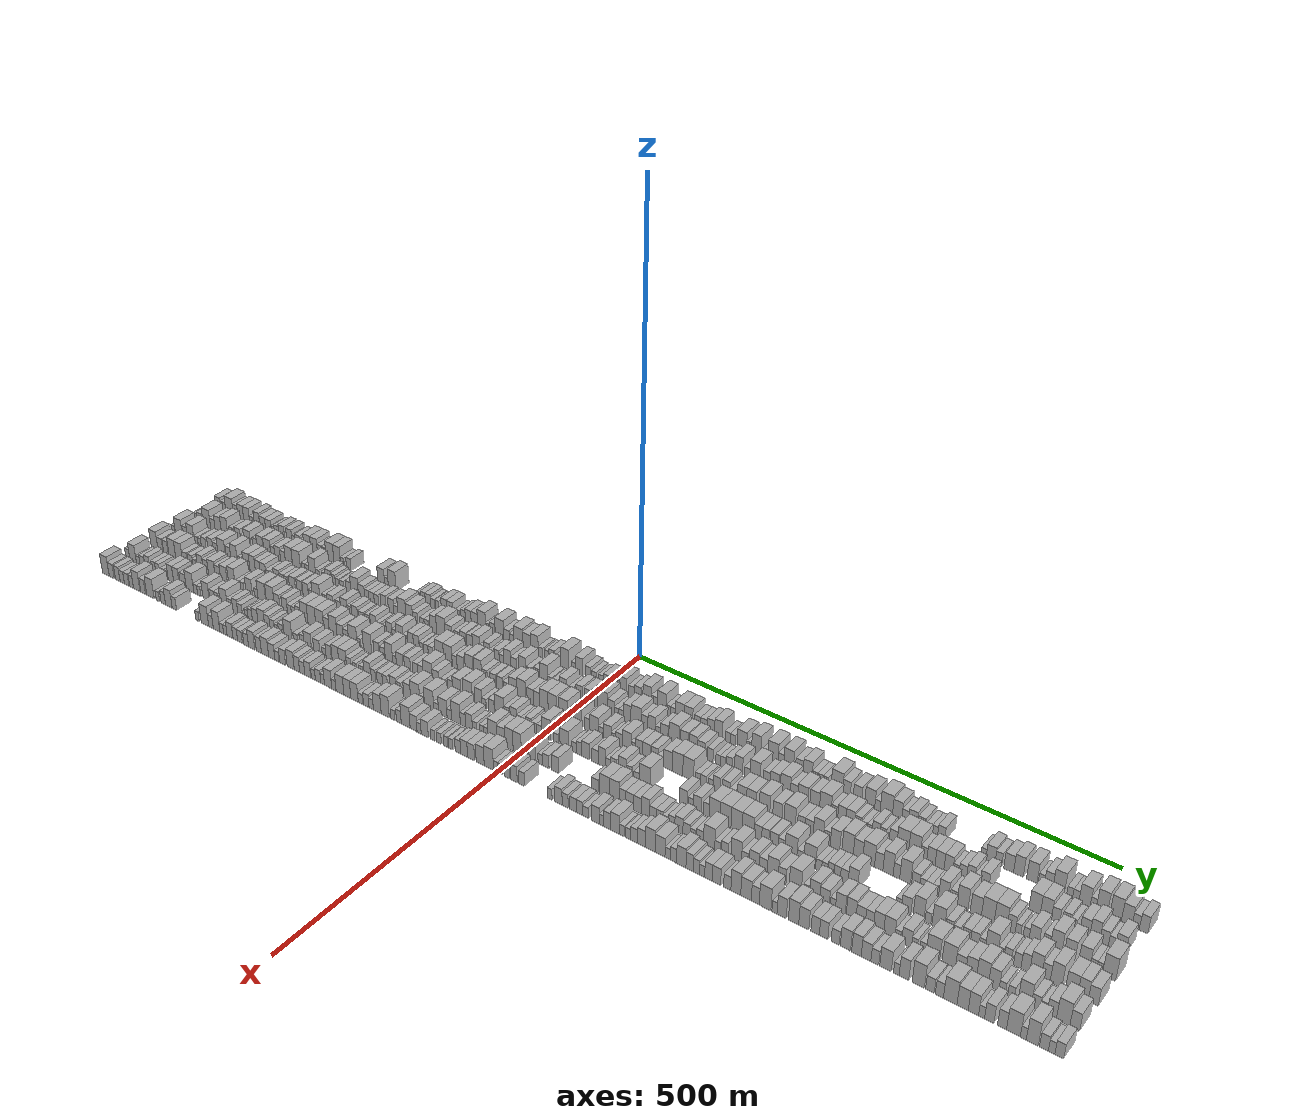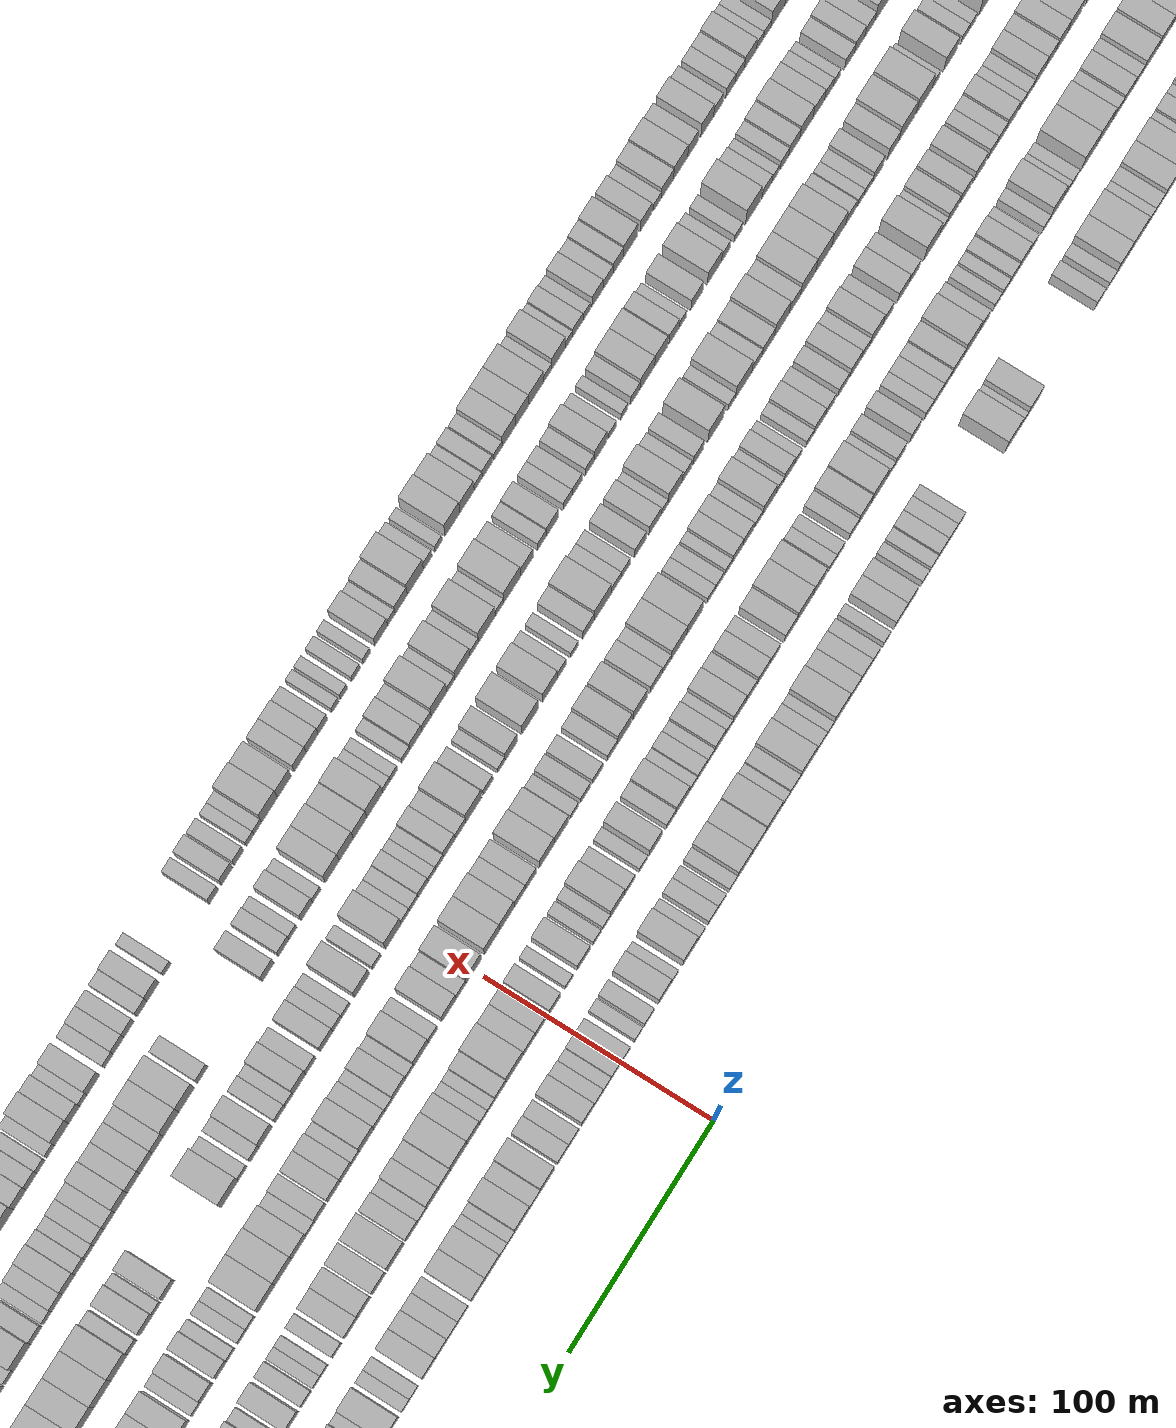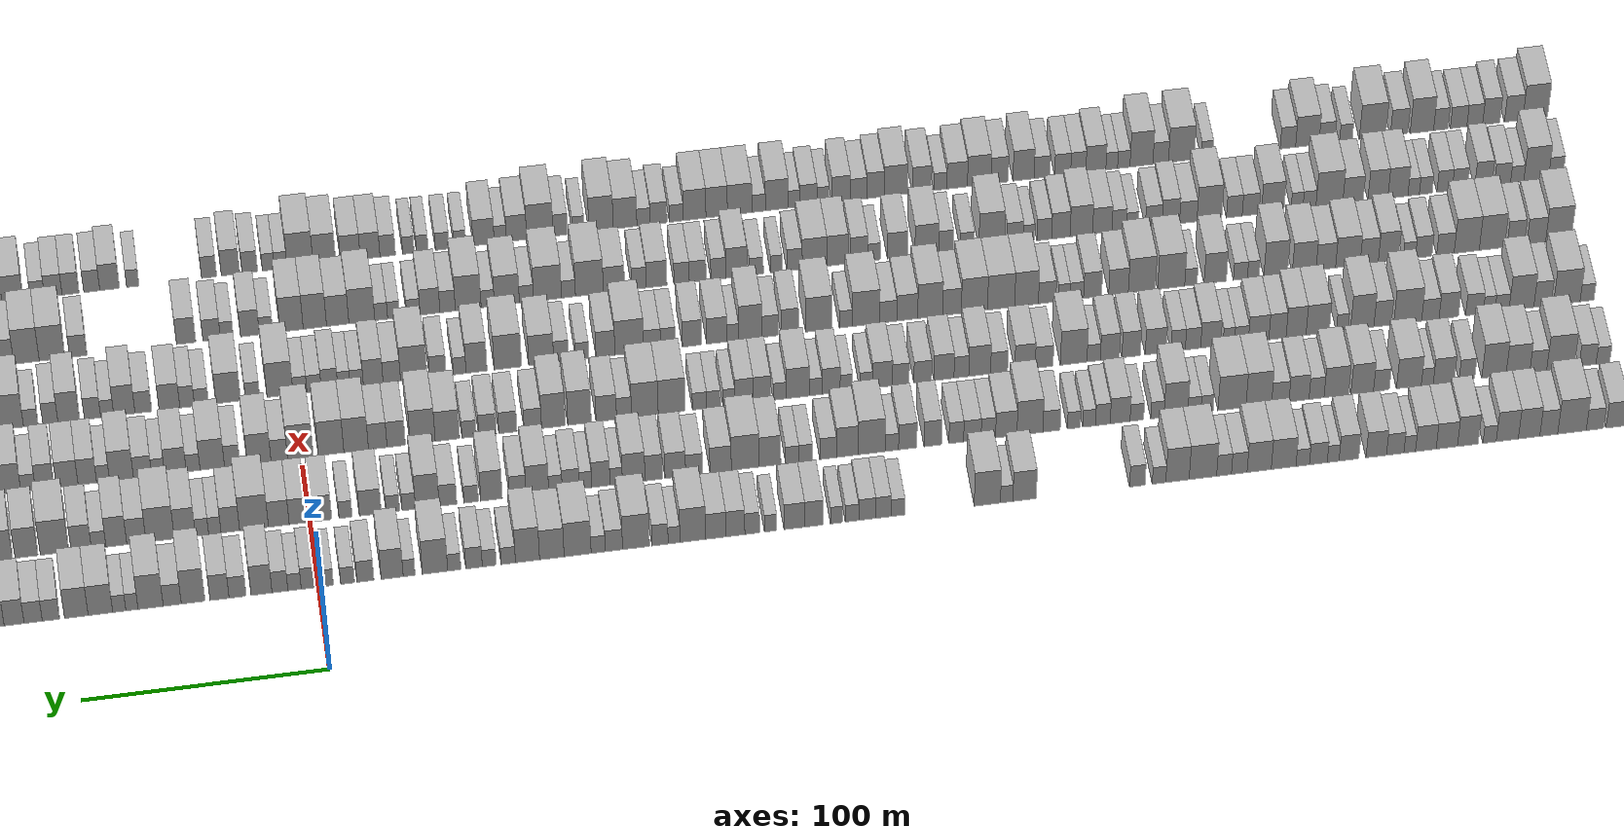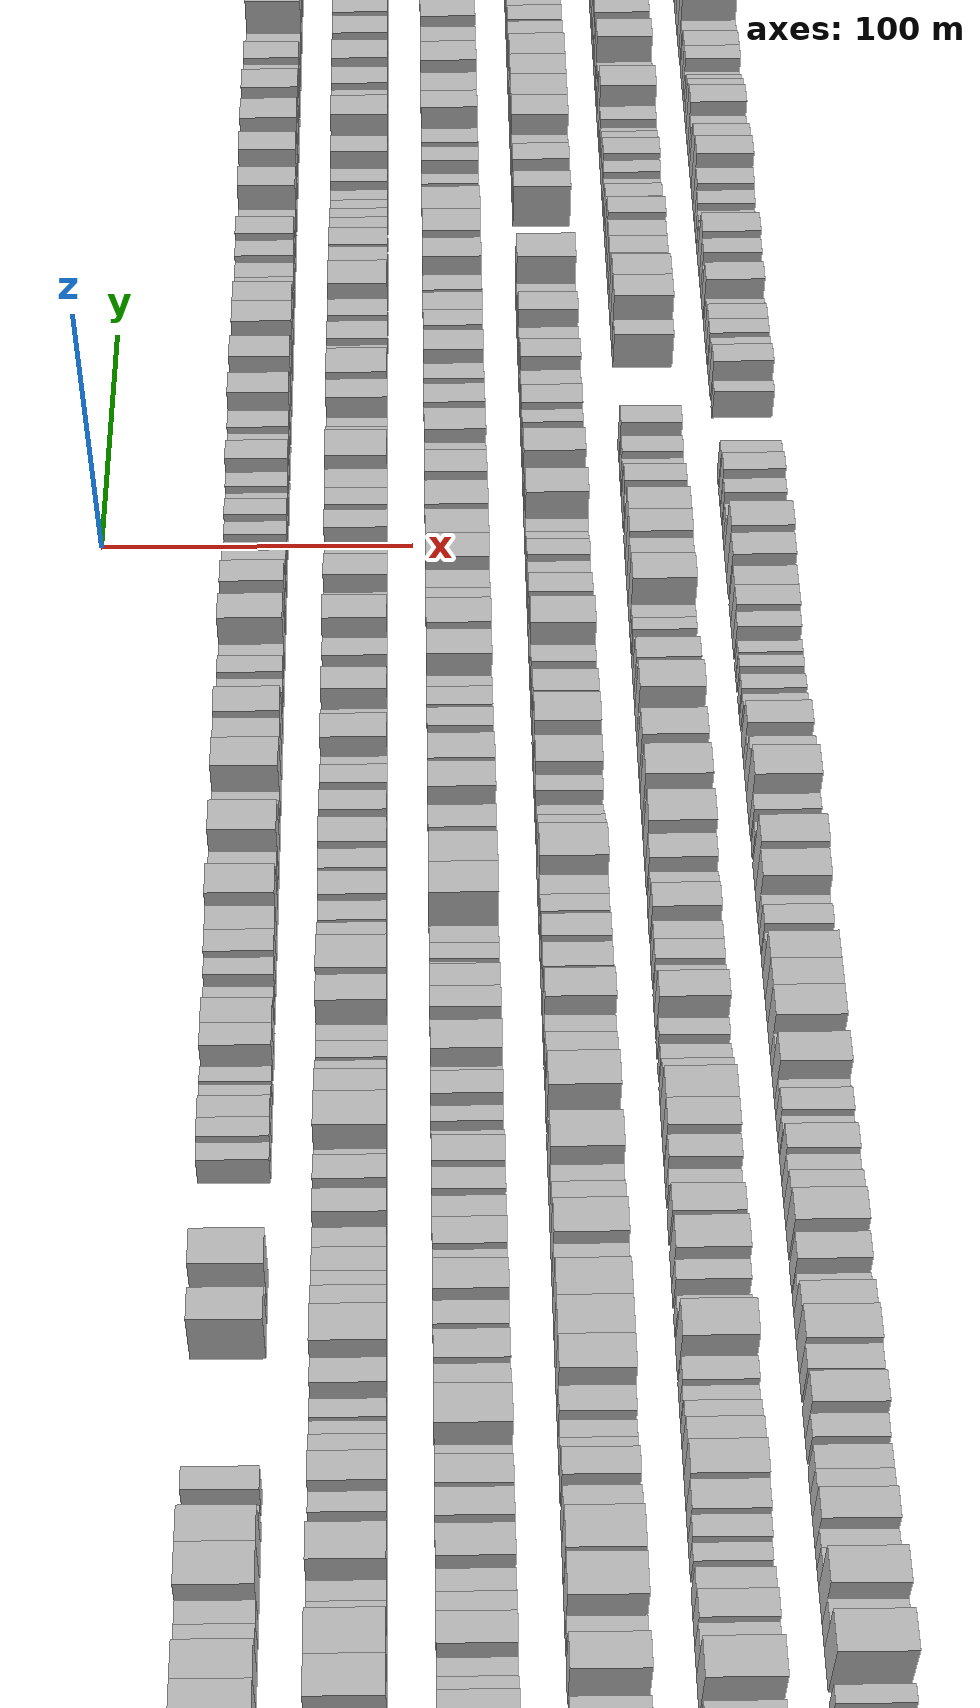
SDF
<sdf version="1.6">
 <world name="default">
  <scene>
   <sky><clouds><speed>12</speed></clouds></sky>
   <ambient>0.4 0.4 0.4 1</ambient>
   <background>0.7 0.7 0.7 1</background>
   <shadows>1</shadows>
  </scene>
  <gravity>0 0 -9.8066</gravity>
  <magnetic_field>6e-06 2.3e-05 -4.2e-05</magnetic_field>
  <physics default="0" name="default_physics" type="ode">
   <ode>
    <solver>
     <type>quick</type>
     <iters>10</iters>
     <sor>1.0</sor>
     <use_dynamic_moi_rescaling>0</use_dynamic_moi_rescaling>
    </solver>
    <constraints>
     <cfm>0</cfm>
     <erp>0.2</erp>
     <contact_max_correcting_vel>100</contact_max_correcting_vel>
     <contact_surface_layer>0.001</contact_surface_layer>
    </constraints>
   </ode>
   <max_step_size>0.004</max_step_size>
   <real_time_factor>1</real_time_factor>
   <real_time_update_rate>250</real_time_update_rate>
  </physics>
  <light name="sun" type="directional">
   <pose>0 0 10 0 0 0</pose>
   <diffuse>0.8 0.8 0.8 1</diffuse>
   <specular>0.2 0.2 0.2 1</specular>
   <attenuation>
    <range>1000</range>
    <constant>0.9</constant>
    <linear>0.01</linear>
    <quadratic>0.001</quadratic>
   </attenuation>
   <direction>-0.5 0.1 -0.9</direction>
  </light>
  <model name="building_1">
   <static>1</static>
   <pose>50.0000 -535.8511 0 0.000000 0.000000 0.000000</pose>
   <link name="link">
    <pose>0 0 9.00 0 0 0</pose>
    <collision name="collision"><geometry><box><size>20.0000 8.2978 18.0000</size></box></geometry></collision>
    <visual name="visual">
     <cast_shadows>0</cast_shadows>
     <geometry><box><size>20.0000 8.2978 18.0000</size></box></geometry>
     <material>
      <script>
       <uri>model://HANNAS_wall/materials/scripts</uri>
       <uri>model://HANNAS_wall/materials/textures</uri>
       <name>vrc/HANNAS_wall</name>
      </script>
     </material>
    </visual>
   </link>
  </model>
  <model name="building_2">
   <static>1</static>
   <pose>50.0000 -527.0699 0 0.000000 0.000000 0.000000</pose>
   <link name="link">
    <pose>0 0 7.50 0 0 0</pose>
    <collision name="collision"><geometry><box><size>20.0000 7.2646 15.0000</size></box></geometry></collision>
    <visual name="visual">
     <cast_shadows>0</cast_shadows>
     <geometry><box><size>20.0000 7.2646 15.0000</size></box></geometry>
     <material>
      <script>
       <uri>model://HANNAS_wall/materials/scripts</uri>
       <uri>model://HANNAS_wall/materials/textures</uri>
       <name>vrc/HANNAS_wall</name>
      </script>
     </material>
    </visual>
   </link>
  </model>
  <model name="building_3">
   <static>1</static>
   <pose>50.0000 -517.4618 0 0.000000 0.000000 0.000000</pose>
   <link name="link">
    <pose>0 0 12.00 0 0 0</pose>
    <collision name="collision"><geometry><box><size>20.0000 11.9516 24.0000</size></box></geometry></collision>
    <visual name="visual">
     <cast_shadows>0</cast_shadows>
     <geometry><box><size>20.0000 11.9516 24.0000</size></box></geometry>
     <material>
      <script>
       <uri>model://HANNAS_wall/materials/scripts</uri>
       <uri>model://HANNAS_wall/materials/textures</uri>
       <name>vrc/HANNAS_wall</name>
      </script>
     </material>
    </visual>
   </link>
  </model>
  <model name="building_4">
   <static>1</static>
   <pose>50.0000 -507.7472 0 0.000000 0.000000 0.000000</pose>
   <link name="link">
    <pose>0 0 9.00 0 0 0</pose>
    <collision name="collision"><geometry><box><size>20.0000 7.4775 18.0000</size></box></geometry></collision>
    <visual name="visual">
     <cast_shadows>0</cast_shadows>
     <geometry><box><size>20.0000 7.4775 18.0000</size></box></geometry>
     <material>
      <script>
       <uri>model://HANNAS_wall/materials/scripts</uri>
       <uri>model://HANNAS_wall/materials/textures</uri>
       <name>vrc/HANNAS_wall</name>
      </script>
     </material>
    </visual>
   </link>
  </model>
  <model name="building_5">
   <static>1</static>
   <pose>50.0000 -499.5124 0 0.000000 0.000000 0.000000</pose>
   <link name="link">
    <pose>0 0 10.50 0 0 0</pose>
    <collision name="collision"><geometry><box><size>20.0000 8.9919 21.0000</size></box></geometry></collision>
    <visual name="visual">
     <cast_shadows>0</cast_shadows>
     <geometry><box><size>20.0000 8.9919 21.0000</size></box></geometry>
     <material>
      <script>
       <uri>model://HANNAS_wall/materials/scripts</uri>
       <uri>model://HANNAS_wall/materials/textures</uri>
       <name>vrc/HANNAS_wall</name>
      </script>
     </material>
    </visual>
   </link>
  </model>
  <model name="building_6">
   <static>1</static>
   <pose>50.0000 -490.3969 0 0.000000 0.000000 0.000000</pose>
   <link name="link">
    <pose>0 0 10.50 0 0 0</pose>
    <collision name="collision"><geometry><box><size>20.0000 9.2392 21.0000</size></box></geometry></collision>
    <visual name="visual">
     <cast_shadows>0</cast_shadows>
     <geometry><box><size>20.0000 9.2392 21.0000</size></box></geometry>
     <material>
      <script>
       <uri>model://HANNAS_wall/materials/scripts</uri>
       <uri>model://HANNAS_wall/materials/textures</uri>
       <name>vrc/HANNAS_wall</name>
      </script>
     </material>
    </visual>
   </link>
  </model>
  <model name="building_7">
   <static>1</static>
   <pose>50.0000 -483.0054 0 0.000000 0.000000 0.000000</pose>
   <link name="link">
    <pose>0 0 6.00 0 0 0</pose>
    <collision name="collision"><geometry><box><size>20.0000 5.5439 12.0000</size></box></geometry></collision>
    <visual name="visual">
     <cast_shadows>0</cast_shadows>
     <geometry><box><size>20.0000 5.5439 12.0000</size></box></geometry>
     <material>
      <script>
       <uri>model://HANNAS_wall/materials/scripts</uri>
       <uri>model://HANNAS_wall/materials/textures</uri>
       <name>vrc/HANNAS_wall</name>
      </script>
     </material>
    </visual>
   </link>
  </model>
  <model name="building_8">
   <static>1</static>
   <pose>50.0000 -473.8988 0 0.000000 0.000000 0.000000</pose>
   <link name="link">
    <pose>0 0 10.50 0 0 0</pose>
    <collision name="collision"><geometry><box><size>20.0000 8.6692 21.0000</size></box></geometry></collision>
    <visual name="visual">
     <cast_shadows>0</cast_shadows>
     <geometry><box><size>20.0000 8.6692 21.0000</size></box></geometry>
     <material>
      <script>
       <uri>model://HANNAS_wall/materials/scripts</uri>
       <uri>model://HANNAS_wall/materials/textures</uri>
       <name>vrc/HANNAS_wall</name>
      </script>
     </material>
    </visual>
   </link>
  </model>
  <model name="building_9">
   <static>1</static>
   <pose>50.0000 -465.1315 0 0.000000 0.000000 0.000000</pose>
   <link name="link">
    <pose>0 0 9.00 0 0 0</pose>
    <collision name="collision"><geometry><box><size>20.0000 8.8655 18.0000</size></box></geometry></collision>
    <visual name="visual">
     <cast_shadows>0</cast_shadows>
     <geometry><box><size>20.0000 8.8655 18.0000</size></box></geometry>
     <material>
      <script>
       <uri>model://HANNAS_wall/materials/scripts</uri>
       <uri>model://HANNAS_wall/materials/textures</uri>
       <name>vrc/HANNAS_wall</name>
      </script>
     </material>
    </visual>
   </link>
  </model>
  <model name="building_10">
   <static>1</static>
   <pose>50.0000 -456.3737 0 0.000000 0.000000 0.000000</pose>
   <link name="link">
    <pose>0 0 9.00 0 0 0</pose>
    <collision name="collision"><geometry><box><size>20.0000 8.6501 18.0000</size></box></geometry></collision>
    <visual name="visual">
     <cast_shadows>0</cast_shadows>
     <geometry><box><size>20.0000 8.6501 18.0000</size></box></geometry>
     <material>
      <script>
       <uri>model://HANNAS_wall/materials/scripts</uri>
       <uri>model://HANNAS_wall/materials/textures</uri>
       <name>vrc/HANNAS_wall</name>
      </script>
     </material>
    </visual>
   </link>
  </model>
  <model name="building_11">
   <static>1</static>
   <pose>50.0000 -449.6461 0 0.000000 0.000000 0.000000</pose>
   <link name="link">
    <pose>0 0 6.00 0 0 0</pose>
    <collision name="collision"><geometry><box><size>20.0000 4.8050 12.0000</size></box></geometry></collision>
    <visual name="visual">
     <cast_shadows>0</cast_shadows>
     <geometry><box><size>20.0000 4.8050 12.0000</size></box></geometry>
     <material>
      <script>
       <uri>model://HANNAS_wall/materials/scripts</uri>
       <uri>model://HANNAS_wall/materials/textures</uri>
       <name>vrc/HANNAS_wall</name>
      </script>
     </material>
    </visual>
   </link>
  </model>
  <model name="building_12">
   <static>1</static>
   <pose>50.0000 -443.6025 0 0.000000 0.000000 0.000000</pose>
   <link name="link">
    <pose>0 0 7.50 0 0 0</pose>
    <collision name="collision"><geometry><box><size>20.0000 7.2822 15.0000</size></box></geometry></collision>
    <visual name="visual">
     <cast_shadows>0</cast_shadows>
     <geometry><box><size>20.0000 7.2822 15.0000</size></box></geometry>
     <material>
      <script>
       <uri>model://HANNAS_wall/materials/scripts</uri>
       <uri>model://HANNAS_wall/materials/textures</uri>
       <name>vrc/HANNAS_wall</name>
      </script>
     </material>
    </visual>
   </link>
  </model>
  <model name="building_13">
   <static>1</static>
   <pose>50.0000 -435.6851 0 0.000000 0.000000 0.000000</pose>
   <link name="link">
    <pose>0 0 9.00 0 0 0</pose>
    <collision name="collision"><geometry><box><size>20.0000 8.5528 18.0000</size></box></geometry></collision>
    <visual name="visual">
     <cast_shadows>0</cast_shadows>
     <geometry><box><size>20.0000 8.5528 18.0000</size></box></geometry>
     <material>
      <script>
       <uri>model://HANNAS_wall/materials/scripts</uri>
       <uri>model://HANNAS_wall/materials/textures</uri>
       <name>vrc/HANNAS_wall</name>
      </script>
     </material>
    </visual>
   </link>
  </model>
  <model name="building_14">
   <static>1</static>
   <pose>50.0000 -424.3038 0 0.000000 0.000000 0.000000</pose>
   <link name="link">
    <pose>0 0 9.00 0 0 0</pose>
    <collision name="collision"><geometry><box><size>20.0000 8.2097 18.0000</size></box></geometry></collision>
    <visual name="visual">
     <cast_shadows>0</cast_shadows>
     <geometry><box><size>20.0000 8.2097 18.0000</size></box></geometry>
     <material>
      <script>
       <uri>model://HANNAS_wall/materials/scripts</uri>
       <uri>model://HANNAS_wall/materials/textures</uri>
       <name>vrc/HANNAS_wall</name>
      </script>
     </material>
    </visual>
   </link>
  </model>
  <model name="building_15">
   <static>1</static>
   <pose>50.0000 -417.7382 0 0.000000 0.000000 0.000000</pose>
   <link name="link">
    <pose>0 0 6.00 0 0 0</pose>
    <collision name="collision"><geometry><box><size>20.0000 4.9214 12.0000</size></box></geometry></collision>
    <visual name="visual">
     <cast_shadows>0</cast_shadows>
     <geometry><box><size>20.0000 4.9214 12.0000</size></box></geometry>
     <material>
      <script>
       <uri>model://HANNAS_wall/materials/scripts</uri>
       <uri>model://HANNAS_wall/materials/textures</uri>
       <name>vrc/HANNAS_wall</name>
      </script>
     </material>
    </visual>
   </link>
  </model>
  <model name="building_16">
   <static>1</static>
   <pose>50.0000 -411.5757 0 0.000000 0.000000 0.000000</pose>
   <link name="link">
    <pose>0 0 7.50 0 0 0</pose>
    <collision name="collision"><geometry><box><size>20.0000 7.4037 15.0000</size></box></geometry></collision>
    <visual name="visual">
     <cast_shadows>0</cast_shadows>
     <geometry><box><size>20.0000 7.4037 15.0000</size></box></geometry>
     <material>
      <script>
       <uri>model://HANNAS_wall/materials/scripts</uri>
       <uri>model://HANNAS_wall/materials/textures</uri>
       <name>vrc/HANNAS_wall</name>
      </script>
     </material>
    </visual>
   </link>
  </model>
  <model name="building_17">
   <static>1</static>
   <pose>50.0000 -405.0557 0 0.000000 0.000000 0.000000</pose>
   <link name="link">
    <pose>0 0 6.00 0 0 0</pose>
    <collision name="collision"><geometry><box><size>20.0000 5.6362 12.0000</size></box></geometry></collision>
    <visual name="visual">
     <cast_shadows>0</cast_shadows>
     <geometry><box><size>20.0000 5.6362 12.0000</size></box></geometry>
     <material>
      <script>
       <uri>model://HANNAS_wall/materials/scripts</uri>
       <uri>model://HANNAS_wall/materials/textures</uri>
       <name>vrc/HANNAS_wall</name>
      </script>
     </material>
    </visual>
   </link>
  </model>
  <model name="building_18">
   <static>1</static>
   <pose>50.0000 -397.1059 0 0.000000 0.000000 0.000000</pose>
   <link name="link">
    <pose>0 0 10.50 0 0 0</pose>
    <collision name="collision"><geometry><box><size>20.0000 10.2633 21.0000</size></box></geometry></collision>
    <visual name="visual">
     <cast_shadows>0</cast_shadows>
     <geometry><box><size>20.0000 10.2633 21.0000</size></box></geometry>
     <material>
      <script>
       <uri>model://HANNAS_wall/materials/scripts</uri>
       <uri>model://HANNAS_wall/materials/textures</uri>
       <name>vrc/HANNAS_wall</name>
      </script>
     </material>
    </visual>
   </link>
  </model>
  <model name="building_19">
   <static>1</static>
   <pose>50.0000 -386.9578 0 0.000000 0.000000 0.000000</pose>
   <link name="link">
    <pose>0 0 10.50 0 0 0</pose>
    <collision name="collision"><geometry><box><size>20.0000 10.0329 21.0000</size></box></geometry></collision>
    <visual name="visual">
     <cast_shadows>0</cast_shadows>
     <geometry><box><size>20.0000 10.0329 21.0000</size></box></geometry>
     <material>
      <script>
       <uri>model://HANNAS_wall/materials/scripts</uri>
       <uri>model://HANNAS_wall/materials/textures</uri>
       <name>vrc/HANNAS_wall</name>
      </script>
     </material>
    </visual>
   </link>
  </model>
  <model name="building_20">
   <static>1</static>
   <pose>50.0000 -378.6762 0 0.000000 0.000000 0.000000</pose>
   <link name="link">
    <pose>0 0 7.50 0 0 0</pose>
    <collision name="collision"><geometry><box><size>20.0000 6.5304 15.0000</size></box></geometry></collision>
    <visual name="visual">
     <cast_shadows>0</cast_shadows>
     <geometry><box><size>20.0000 6.5304 15.0000</size></box></geometry>
     <material>
      <script>
       <uri>model://HANNAS_wall/materials/scripts</uri>
       <uri>model://HANNAS_wall/materials/textures</uri>
       <name>vrc/HANNAS_wall</name>
      </script>
     </material>
    </visual>
   </link>
  </model>
  <model name="building_21">
   <static>1</static>
   <pose>50.0000 -372.3386 0 0.000000 0.000000 0.000000</pose>
   <link name="link">
    <pose>0 0 7.50 0 0 0</pose>
    <collision name="collision"><geometry><box><size>20.0000 6.1447 15.0000</size></box></geometry></collision>
    <visual name="visual">
     <cast_shadows>0</cast_shadows>
     <geometry><box><size>20.0000 6.1447 15.0000</size></box></geometry>
     <material>
      <script>
       <uri>model://HANNAS_wall/materials/scripts</uri>
       <uri>model://HANNAS_wall/materials/textures</uri>
       <name>vrc/HANNAS_wall</name>
      </script>
     </material>
    </visual>
   </link>
  </model>
  <model name="building_22">
   <static>1</static>
   <pose>50.0000 -363.5620 0 0.000000 0.000000 0.000000</pose>
   <link name="link">
    <pose>0 0 12.00 0 0 0</pose>
    <collision name="collision"><geometry><box><size>20.0000 11.4085 24.0000</size></box></geometry></collision>
    <visual name="visual">
     <cast_shadows>0</cast_shadows>
     <geometry><box><size>20.0000 11.4085 24.0000</size></box></geometry>
     <material>
      <script>
       <uri>model://HANNAS_wall/materials/scripts</uri>
       <uri>model://HANNAS_wall/materials/textures</uri>
       <name>vrc/HANNAS_wall</name>
      </script>
     </material>
    </visual>
   </link>
  </model>
  <model name="building_23">
   <static>1</static>
   <pose>50.0000 -353.0114 0 0.000000 0.000000 0.000000</pose>
   <link name="link">
    <pose>0 0 12.00 0 0 0</pose>
    <collision name="collision"><geometry><box><size>20.0000 9.6928 24.0000</size></box></geometry></collision>
    <visual name="visual">
     <cast_shadows>0</cast_shadows>
     <geometry><box><size>20.0000 9.6928 24.0000</size></box></geometry>
     <material>
      <script>
       <uri>model://HANNAS_wall/materials/scripts</uri>
       <uri>model://HANNAS_wall/materials/textures</uri>
       <name>vrc/HANNAS_wall</name>
      </script>
     </material>
    </visual>
   </link>
  </model>
  <model name="building_24">
   <static>1</static>
   <pose>50.0000 -345.3561 0 0.000000 0.000000 0.000000</pose>
   <link name="link">
    <pose>0 0 6.00 0 0 0</pose>
    <collision name="collision"><geometry><box><size>20.0000 5.6176 12.0000</size></box></geometry></collision>
    <visual name="visual">
     <cast_shadows>0</cast_shadows>
     <geometry><box><size>20.0000 5.6176 12.0000</size></box></geometry>
     <material>
      <script>
       <uri>model://HANNAS_wall/materials/scripts</uri>
       <uri>model://HANNAS_wall/materials/textures</uri>
       <name>vrc/HANNAS_wall</name>
      </script>
     </material>
    </visual>
   </link>
  </model>
  <model name="building_25">
   <static>1</static>
   <pose>50.0000 -336.3392 0 0.000000 0.000000 0.000000</pose>
   <link name="link">
    <pose>0 0 7.50 0 0 0</pose>
    <collision name="collision"><geometry><box><size>20.0000 6.4162 15.0000</size></box></geometry></collision>
    <visual name="visual">
     <cast_shadows>0</cast_shadows>
     <geometry><box><size>20.0000 6.4162 15.0000</size></box></geometry>
     <material>
      <script>
       <uri>model://HANNAS_wall/materials/scripts</uri>
       <uri>model://HANNAS_wall/materials/textures</uri>
       <name>vrc/HANNAS_wall</name>
      </script>
     </material>
    </visual>
   </link>
  </model>
  <model name="building_26">
   <static>1</static>
   <pose>50.0000 -289.6660 0 0.000000 0.000000 0.000000</pose>
   <link name="link">
    <pose>0 0 10.50 0 0 0</pose>
    <collision name="collision"><geometry><box><size>20.0000 9.6434 21.0000</size></box></geometry></collision>
    <visual name="visual">
     <cast_shadows>0</cast_shadows>
     <geometry><box><size>20.0000 9.6434 21.0000</size></box></geometry>
     <material>
      <script>
       <uri>model://HANNAS_wall/materials/scripts</uri>
       <uri>model://HANNAS_wall/materials/textures</uri>
       <name>vrc/HANNAS_wall</name>
      </script>
     </material>
    </visual>
   </link>
  </model>
  <model name="building_27">
   <static>1</static>
   <pose>50.0000 -282.2654 0 0.000000 0.000000 0.000000</pose>
   <link name="link">
    <pose>0 0 6.00 0 0 0</pose>
    <collision name="collision"><geometry><box><size>20.0000 5.1577 12.0000</size></box></geometry></collision>
    <visual name="visual">
     <cast_shadows>0</cast_shadows>
     <geometry><box><size>20.0000 5.1577 12.0000</size></box></geometry>
     <material>
      <script>
       <uri>model://HANNAS_wall/materials/scripts</uri>
       <uri>model://HANNAS_wall/materials/textures</uri>
       <name>vrc/HANNAS_wall</name>
      </script>
     </material>
    </visual>
   </link>
  </model>
  <model name="building_28">
   <static>1</static>
   <pose>50.0000 -274.2711 0 0.000000 0.000000 0.000000</pose>
   <link name="link">
    <pose>0 0 12.00 0 0 0</pose>
    <collision name="collision"><geometry><box><size>20.0000 10.8308 24.0000</size></box></geometry></collision>
    <visual name="visual">
     <cast_shadows>0</cast_shadows>
     <geometry><box><size>20.0000 10.8308 24.0000</size></box></geometry>
     <material>
      <script>
       <uri>model://HANNAS_wall/materials/scripts</uri>
       <uri>model://HANNAS_wall/materials/textures</uri>
       <name>vrc/HANNAS_wall</name>
      </script>
     </material>
    </visual>
   </link>
  </model>
  <model name="building_29">
   <static>1</static>
   <pose>50.0000 -237.3630 0 0.000000 0.000000 0.000000</pose>
   <link name="link">
    <pose>0 0 6.00 0 0 0</pose>
    <collision name="collision"><geometry><box><size>20.0000 5.6618 12.0000</size></box></geometry></collision>
    <visual name="visual">
     <cast_shadows>0</cast_shadows>
     <geometry><box><size>20.0000 5.6618 12.0000</size></box></geometry>
     <material>
      <script>
       <uri>model://HANNAS_wall/materials/scripts</uri>
       <uri>model://HANNAS_wall/materials/textures</uri>
       <name>vrc/HANNAS_wall</name>
      </script>
     </material>
    </visual>
   </link>
  </model>
  <model name="building_30">
   <static>1</static>
   <pose>50.0000 -231.3875 0 0.000000 0.000000 0.000000</pose>
   <link name="link">
    <pose>0 0 7.50 0 0 0</pose>
    <collision name="collision"><geometry><box><size>20.0000 6.2892 15.0000</size></box></geometry></collision>
    <visual name="visual">
     <cast_shadows>0</cast_shadows>
     <geometry><box><size>20.0000 6.2892 15.0000</size></box></geometry>
     <material>
      <script>
       <uri>model://HANNAS_wall/materials/scripts</uri>
       <uri>model://HANNAS_wall/materials/textures</uri>
       <name>vrc/HANNAS_wall</name>
      </script>
     </material>
    </visual>
   </link>
  </model>
  <model name="building_31">
   <static>1</static>
   <pose>50.0000 -224.7228 0 0.000000 0.000000 0.000000</pose>
   <link name="link">
    <pose>0 0 7.50 0 0 0</pose>
    <collision name="collision"><geometry><box><size>20.0000 7.0403 15.0000</size></box></geometry></collision>
    <visual name="visual">
     <cast_shadows>0</cast_shadows>
     <geometry><box><size>20.0000 7.0403 15.0000</size></box></geometry>
     <material>
      <script>
       <uri>model://HANNAS_wall/materials/scripts</uri>
       <uri>model://HANNAS_wall/materials/textures</uri>
       <name>vrc/HANNAS_wall</name>
      </script>
     </material>
    </visual>
   </link>
  </model>
  <model name="building_32">
   <static>1</static>
   <pose>50.0000 -218.4330 0 0.000000 0.000000 0.000000</pose>
   <link name="link">
    <pose>0 0 6.00 0 0 0</pose>
    <collision name="collision"><geometry><box><size>20.0000 5.5392 12.0000</size></box></geometry></collision>
    <visual name="visual">
     <cast_shadows>0</cast_shadows>
     <geometry><box><size>20.0000 5.5392 12.0000</size></box></geometry>
     <material>
      <script>
       <uri>model://HANNAS_wall/materials/scripts</uri>
       <uri>model://HANNAS_wall/materials/textures</uri>
       <name>vrc/HANNAS_wall</name>
      </script>
     </material>
    </visual>
   </link>
  </model>
  <model name="building_33">
   <static>1</static>
   <pose>50.0000 -212.1156 0 0.000000 0.000000 0.000000</pose>
   <link name="link">
    <pose>0 0 6.00 0 0 0</pose>
    <collision name="collision"><geometry><box><size>20.0000 5.0956 12.0000</size></box></geometry></collision>
    <visual name="visual">
     <cast_shadows>0</cast_shadows>
     <geometry><box><size>20.0000 5.0956 12.0000</size></box></geometry>
     <material>
      <script>
       <uri>model://HANNAS_wall/materials/scripts</uri>
       <uri>model://HANNAS_wall/materials/textures</uri>
       <name>vrc/HANNAS_wall</name>
      </script>
     </material>
    </visual>
   </link>
  </model>
  <model name="building_34">
   <static>1</static>
   <pose>50.0000 -202.7801 0 0.000000 0.000000 0.000000</pose>
   <link name="link">
    <pose>0 0 9.00 0 0 0</pose>
    <collision name="collision"><geometry><box><size>20.0000 7.5754 18.0000</size></box></geometry></collision>
    <visual name="visual">
     <cast_shadows>0</cast_shadows>
     <geometry><box><size>20.0000 7.5754 18.0000</size></box></geometry>
     <material>
      <script>
       <uri>model://HANNAS_wall/materials/scripts</uri>
       <uri>model://HANNAS_wall/materials/textures</uri>
       <name>vrc/HANNAS_wall</name>
      </script>
     </material>
    </visual>
   </link>
  </model>
  <model name="building_35">
   <static>1</static>
   <pose>50.0000 -194.7225 0 0.000000 0.000000 0.000000</pose>
   <link name="link">
    <pose>0 0 9.00 0 0 0</pose>
    <collision name="collision"><geometry><box><size>20.0000 8.5398 18.0000</size></box></geometry></collision>
    <visual name="visual">
     <cast_shadows>0</cast_shadows>
     <geometry><box><size>20.0000 8.5398 18.0000</size></box></geometry>
     <material>
      <script>
       <uri>model://HANNAS_wall/materials/scripts</uri>
       <uri>model://HANNAS_wall/materials/textures</uri>
       <name>vrc/HANNAS_wall</name>
      </script>
     </material>
    </visual>
   </link>
  </model>
  <model name="building_36">
   <static>1</static>
   <pose>50.0000 -184.9223 0 0.000000 0.000000 0.000000</pose>
   <link name="link">
    <pose>0 0 6.00 0 0 0</pose>
    <collision name="collision"><geometry><box><size>20.0000 5.0607 12.0000</size></box></geometry></collision>
    <visual name="visual">
     <cast_shadows>0</cast_shadows>
     <geometry><box><size>20.0000 5.0607 12.0000</size></box></geometry>
     <material>
      <script>
       <uri>model://HANNAS_wall/materials/scripts</uri>
       <uri>model://HANNAS_wall/materials/textures</uri>
       <name>vrc/HANNAS_wall</name>
      </script>
     </material>
    </visual>
   </link>
  </model>
  <model name="building_37">
   <static>1</static>
   <pose>50.0000 -177.3628 0 0.000000 0.000000 0.000000</pose>
   <link name="link">
    <pose>0 0 7.50 0 0 0</pose>
    <collision name="collision"><geometry><box><size>20.0000 6.0583 15.0000</size></box></geometry></collision>
    <visual name="visual">
     <cast_shadows>0</cast_shadows>
     <geometry><box><size>20.0000 6.0583 15.0000</size></box></geometry>
     <material>
      <script>
       <uri>model://HANNAS_wall/materials/scripts</uri>
       <uri>model://HANNAS_wall/materials/textures</uri>
       <name>vrc/HANNAS_wall</name>
      </script>
     </material>
    </visual>
   </link>
  </model>
  <model name="building_38">
   <static>1</static>
   <pose>50.0000 -170.4805 0 0.000000 0.000000 0.000000</pose>
   <link name="link">
    <pose>0 0 9.00 0 0 0</pose>
    <collision name="collision"><geometry><box><size>20.0000 7.7063 18.0000</size></box></geometry></collision>
    <visual name="visual">
     <cast_shadows>0</cast_shadows>
     <geometry><box><size>20.0000 7.7063 18.0000</size></box></geometry>
     <material>
      <script>
       <uri>model://HANNAS_wall/materials/scripts</uri>
       <uri>model://HANNAS_wall/materials/textures</uri>
       <name>vrc/HANNAS_wall</name>
      </script>
     </material>
    </visual>
   </link>
  </model>
  <model name="building_39">
   <static>1</static>
   <pose>50.0000 -162.4200 0 0.000000 0.000000 0.000000</pose>
   <link name="link">
    <pose>0 0 9.00 0 0 0</pose>
    <collision name="collision"><geometry><box><size>20.0000 8.4147 18.0000</size></box></geometry></collision>
    <visual name="visual">
     <cast_shadows>0</cast_shadows>
     <geometry><box><size>20.0000 8.4147 18.0000</size></box></geometry>
     <material>
      <script>
       <uri>model://HANNAS_wall/materials/scripts</uri>
       <uri>model://HANNAS_wall/materials/textures</uri>
       <name>vrc/HANNAS_wall</name>
      </script>
     </material>
    </visual>
   </link>
  </model>
  <model name="building_40">
   <static>1</static>
   <pose>50.0000 -152.9572 0 0.000000 0.000000 0.000000</pose>
   <link name="link">
    <pose>0 0 12.00 0 0 0</pose>
    <collision name="collision"><geometry><box><size>20.0000 10.5107 24.0000</size></box></geometry></collision>
    <visual name="visual">
     <cast_shadows>0</cast_shadows>
     <geometry><box><size>20.0000 10.5107 24.0000</size></box></geometry>
     <material>
      <script>
       <uri>model://HANNAS_wall/materials/scripts</uri>
       <uri>model://HANNAS_wall/materials/textures</uri>
       <name>vrc/HANNAS_wall</name>
      </script>
     </material>
    </visual>
   </link>
  </model>
  <model name="building_41">
   <static>1</static>
   <pose>50.0000 -145.2653 0 0.000000 0.000000 0.000000</pose>
   <link name="link">
    <pose>0 0 6.00 0 0 0</pose>
    <collision name="collision"><geometry><box><size>20.0000 4.8732 12.0000</size></box></geometry></collision>
    <visual name="visual">
     <cast_shadows>0</cast_shadows>
     <geometry><box><size>20.0000 4.8732 12.0000</size></box></geometry>
     <material>
      <script>
       <uri>model://HANNAS_wall/materials/scripts</uri>
       <uri>model://HANNAS_wall/materials/textures</uri>
       <name>vrc/HANNAS_wall</name>
      </script>
     </material>
    </visual>
   </link>
  </model>
  <model name="building_42">
   <static>1</static>
   <pose>50.0000 -139.5186 0 0.000000 0.000000 0.000000</pose>
   <link name="link">
    <pose>0 0 7.50 0 0 0</pose>
    <collision name="collision"><geometry><box><size>20.0000 6.6202 15.0000</size></box></geometry></collision>
    <visual name="visual">
     <cast_shadows>0</cast_shadows>
     <geometry><box><size>20.0000 6.6202 15.0000</size></box></geometry>
     <material>
      <script>
       <uri>model://HANNAS_wall/materials/scripts</uri>
       <uri>model://HANNAS_wall/materials/textures</uri>
       <name>vrc/HANNAS_wall</name>
      </script>
     </material>
    </visual>
   </link>
  </model>
  <model name="building_43">
   <static>1</static>
   <pose>50.0000 -129.6769 0 0.000000 0.000000 0.000000</pose>
   <link name="link">
    <pose>0 0 12.00 0 0 0</pose>
    <collision name="collision"><geometry><box><size>20.0000 11.0632 24.0000</size></box></geometry></collision>
    <visual name="visual">
     <cast_shadows>0</cast_shadows>
     <geometry><box><size>20.0000 11.0632 24.0000</size></box></geometry>
     <material>
      <script>
       <uri>model://HANNAS_wall/materials/scripts</uri>
       <uri>model://HANNAS_wall/materials/textures</uri>
       <name>vrc/HANNAS_wall</name>
      </script>
     </material>
    </visual>
   </link>
  </model>
  <model name="building_44">
   <static>1</static>
   <pose>50.0000 -120.6109 0 0.000000 0.000000 0.000000</pose>
   <link name="link">
    <pose>0 0 7.50 0 0 0</pose>
    <collision name="collision"><geometry><box><size>20.0000 7.0687 15.0000</size></box></geometry></collision>
    <visual name="visual">
     <cast_shadows>0</cast_shadows>
     <geometry><box><size>20.0000 7.0687 15.0000</size></box></geometry>
     <material>
      <script>
       <uri>model://HANNAS_wall/materials/scripts</uri>
       <uri>model://HANNAS_wall/materials/textures</uri>
       <name>vrc/HANNAS_wall</name>
      </script>
     </material>
    </visual>
   </link>
  </model>
  <model name="building_45">
   <static>1</static>
   <pose>50.0000 -114.1726 0 0.000000 0.000000 0.000000</pose>
   <link name="link">
    <pose>0 0 6.00 0 0 0</pose>
    <collision name="collision"><geometry><box><size>20.0000 5.8080 12.0000</size></box></geometry></collision>
    <visual name="visual">
     <cast_shadows>0</cast_shadows>
     <geometry><box><size>20.0000 5.8080 12.0000</size></box></geometry>
     <material>
      <script>
       <uri>model://HANNAS_wall/materials/scripts</uri>
       <uri>model://HANNAS_wall/materials/textures</uri>
       <name>vrc/HANNAS_wall</name>
      </script>
     </material>
    </visual>
   </link>
  </model>
  <model name="building_46">
   <static>1</static>
   <pose>50.0000 -105.7286 0 0.000000 0.000000 0.000000</pose>
   <link name="link">
    <pose>0 0 12.00 0 0 0</pose>
    <collision name="collision"><geometry><box><size>20.0000 11.0799 24.0000</size></box></geometry></collision>
    <visual name="visual">
     <cast_shadows>0</cast_shadows>
     <geometry><box><size>20.0000 11.0799 24.0000</size></box></geometry>
     <material>
      <script>
       <uri>model://HANNAS_wall/materials/scripts</uri>
       <uri>model://HANNAS_wall/materials/textures</uri>
       <name>vrc/HANNAS_wall</name>
      </script>
     </material>
    </visual>
   </link>
  </model>
  <model name="building_47">
   <static>1</static>
   <pose>50.0000 -95.1664 0 0.000000 0.000000 0.000000</pose>
   <link name="link">
    <pose>0 0 10.50 0 0 0</pose>
    <collision name="collision"><geometry><box><size>20.0000 10.0445 21.0000</size></box></geometry></collision>
    <visual name="visual">
     <cast_shadows>0</cast_shadows>
     <geometry><box><size>20.0000 10.0445 21.0000</size></box></geometry>
     <material>
      <script>
       <uri>model://HANNAS_wall/materials/scripts</uri>
       <uri>model://HANNAS_wall/materials/textures</uri>
       <name>vrc/HANNAS_wall</name>
      </script>
     </material>
    </visual>
   </link>
  </model>
  <model name="building_48">
   <static>1</static>
   <pose>50.0000 -85.2147 0 0.000000 0.000000 0.000000</pose>
   <link name="link">
    <pose>0 0 12.00 0 0 0</pose>
    <collision name="collision"><geometry><box><size>20.0000 9.8589 24.0000</size></box></geometry></collision>
    <visual name="visual">
     <cast_shadows>0</cast_shadows>
     <geometry><box><size>20.0000 9.8589 24.0000</size></box></geometry>
     <material>
      <script>
       <uri>model://HANNAS_wall/materials/scripts</uri>
       <uri>model://HANNAS_wall/materials/textures</uri>
       <name>vrc/HANNAS_wall</name>
      </script>
     </material>
    </visual>
   </link>
  </model>
  <model name="building_49">
   <static>1</static>
   <pose>50.0000 -77.3720 0 0.000000 0.000000 0.000000</pose>
   <link name="link">
    <pose>0 0 6.00 0 0 0</pose>
    <collision name="collision"><geometry><box><size>20.0000 5.8264 12.0000</size></box></geometry></collision>
    <visual name="visual">
     <cast_shadows>0</cast_shadows>
     <geometry><box><size>20.0000 5.8264 12.0000</size></box></geometry>
     <material>
      <script>
       <uri>model://HANNAS_wall/materials/scripts</uri>
       <uri>model://HANNAS_wall/materials/textures</uri>
       <name>vrc/HANNAS_wall</name>
      </script>
     </material>
    </visual>
   </link>
  </model>
  <model name="building_50">
   <static>1</static>
   <pose>50.0000 -69.5935 0 0.000000 0.000000 0.000000</pose>
   <link name="link">
    <pose>0 0 6.00 0 0 0</pose>
    <collision name="collision"><geometry><box><size>20.0000 5.7306 12.0000</size></box></geometry></collision>
    <visual name="visual">
     <cast_shadows>0</cast_shadows>
     <geometry><box><size>20.0000 5.7306 12.0000</size></box></geometry>
     <material>
      <script>
       <uri>model://HANNAS_wall/materials/scripts</uri>
       <uri>model://HANNAS_wall/materials/textures</uri>
       <name>vrc/HANNAS_wall</name>
      </script>
     </material>
    </visual>
   </link>
  </model>
  <model name="building_51">
   <static>1</static>
   <pose>50.0000 -63.3656 0 0.000000 0.000000 0.000000</pose>
   <link name="link">
    <pose>0 0 7.50 0 0 0</pose>
    <collision name="collision"><geometry><box><size>20.0000 6.7251 15.0000</size></box></geometry></collision>
    <visual name="visual">
     <cast_shadows>0</cast_shadows>
     <geometry><box><size>20.0000 6.7251 15.0000</size></box></geometry>
     <material>
      <script>
       <uri>model://HANNAS_wall/materials/scripts</uri>
       <uri>model://HANNAS_wall/materials/textures</uri>
       <name>vrc/HANNAS_wall</name>
      </script>
     </material>
    </visual>
   </link>
  </model>
  <model name="building_52">
   <static>1</static>
   <pose>50.0000 -55.3044 0 0.000000 0.000000 0.000000</pose>
   <link name="link">
    <pose>0 0 6.00 0 0 0</pose>
    <collision name="collision"><geometry><box><size>20.0000 5.3973 12.0000</size></box></geometry></collision>
    <visual name="visual">
     <cast_shadows>0</cast_shadows>
     <geometry><box><size>20.0000 5.3973 12.0000</size></box></geometry>
     <material>
      <script>
       <uri>model://HANNAS_wall/materials/scripts</uri>
       <uri>model://HANNAS_wall/materials/textures</uri>
       <name>vrc/HANNAS_wall</name>
      </script>
     </material>
    </visual>
   </link>
  </model>
  <model name="building_53">
   <static>1</static>
   <pose>50.0000 -47.4502 0 0.000000 0.000000 0.000000</pose>
   <link name="link">
    <pose>0 0 12.00 0 0 0</pose>
    <collision name="collision"><geometry><box><size>20.0000 10.3111 24.0000</size></box></geometry></collision>
    <visual name="visual">
     <cast_shadows>0</cast_shadows>
     <geometry><box><size>20.0000 10.3111 24.0000</size></box></geometry>
     <material>
      <script>
       <uri>model://HANNAS_wall/materials/scripts</uri>
       <uri>model://HANNAS_wall/materials/textures</uri>
       <name>vrc/HANNAS_wall</name>
      </script>
     </material>
    </visual>
   </link>
  </model>
  <model name="building_54">
   <static>1</static>
   <pose>50.0000 -36.8633 0 0.000000 0.000000 0.000000</pose>
   <link name="link">
    <pose>0 0 6.00 0 0 0</pose>
    <collision name="collision"><geometry><box><size>20.0000 4.8627 12.0000</size></box></geometry></collision>
    <visual name="visual">
     <cast_shadows>0</cast_shadows>
     <geometry><box><size>20.0000 4.8627 12.0000</size></box></geometry>
     <material>
      <script>
       <uri>model://HANNAS_wall/materials/scripts</uri>
       <uri>model://HANNAS_wall/materials/textures</uri>
       <name>vrc/HANNAS_wall</name>
      </script>
     </material>
    </visual>
   </link>
  </model>
  <model name="building_55">
   <static>1</static>
   <pose>50.0000 -29.9581 0 0.000000 0.000000 0.000000</pose>
   <link name="link">
    <pose>0 0 10.50 0 0 0</pose>
    <collision name="collision"><geometry><box><size>20.0000 8.9479 21.0000</size></box></geometry></collision>
    <visual name="visual">
     <cast_shadows>0</cast_shadows>
     <geometry><box><size>20.0000 8.9479 21.0000</size></box></geometry>
     <material>
      <script>
       <uri>model://HANNAS_wall/materials/scripts</uri>
       <uri>model://HANNAS_wall/materials/textures</uri>
       <name>vrc/HANNAS_wall</name>
      </script>
     </material>
    </visual>
   </link>
  </model>
  <model name="building_56">
   <static>1</static>
   <pose>50.0000 -19.0492 0 0.000000 0.000000 0.000000</pose>
   <link name="link">
    <pose>0 0 7.50 0 0 0</pose>
    <collision name="collision"><geometry><box><size>20.0000 6.8700 15.0000</size></box></geometry></collision>
    <visual name="visual">
     <cast_shadows>0</cast_shadows>
     <geometry><box><size>20.0000 6.8700 15.0000</size></box></geometry>
     <material>
      <script>
       <uri>model://HANNAS_wall/materials/scripts</uri>
       <uri>model://HANNAS_wall/materials/textures</uri>
       <name>vrc/HANNAS_wall</name>
      </script>
     </material>
    </visual>
   </link>
  </model>
  <model name="building_57">
   <static>1</static>
   <pose>50.0000 -11.8106 0 0.000000 0.000000 0.000000</pose>
   <link name="link">
    <pose>0 0 6.00 0 0 0</pose>
    <collision name="collision"><geometry><box><size>20.0000 5.6073 12.0000</size></box></geometry></collision>
    <visual name="visual">
     <cast_shadows>0</cast_shadows>
     <geometry><box><size>20.0000 5.6073 12.0000</size></box></geometry>
     <material>
      <script>
       <uri>model://HANNAS_wall/materials/scripts</uri>
       <uri>model://HANNAS_wall/materials/textures</uri>
       <name>vrc/HANNAS_wall</name>
      </script>
     </material>
    </visual>
   </link>
  </model>
  <model name="building_58">
   <static>1</static>
   <pose>50.0000 -3.0111 0 0.000000 0.000000 0.000000</pose>
   <link name="link">
    <pose>0 0 6.00 0 0 0</pose>
    <collision name="collision"><geometry><box><size>20.0000 5.9916 12.0000</size></box></geometry></collision>
    <visual name="visual">
     <cast_shadows>0</cast_shadows>
     <geometry><box><size>20.0000 5.9916 12.0000</size></box></geometry>
     <material>
      <script>
       <uri>model://HANNAS_wall/materials/scripts</uri>
       <uri>model://HANNAS_wall/materials/textures</uri>
       <name>vrc/HANNAS_wall</name>
      </script>
     </material>
    </visual>
   </link>
  </model>
  <model name="building_59">
   <static>1</static>
   <pose>50.0000 3.5411 0 0.000000 0.000000 0.000000</pose>
   <link name="link">
    <pose>0 0 7.50 0 0 0</pose>
    <collision name="collision"><geometry><box><size>20.0000 7.1128 15.0000</size></box></geometry></collision>
    <visual name="visual">
     <cast_shadows>0</cast_shadows>
     <geometry><box><size>20.0000 7.1128 15.0000</size></box></geometry>
     <material>
      <script>
       <uri>model://HANNAS_wall/materials/scripts</uri>
       <uri>model://HANNAS_wall/materials/textures</uri>
       <name>vrc/HANNAS_wall</name>
      </script>
     </material>
    </visual>
   </link>
  </model>
  <model name="building_60">
   <static>1</static>
   <pose>50.0000 9.8182 0 0.000000 0.000000 0.000000</pose>
   <link name="link">
    <pose>0 0 6.00 0 0 0</pose>
    <collision name="collision"><geometry><box><size>20.0000 5.4413 12.0000</size></box></geometry></collision>
    <visual name="visual">
     <cast_shadows>0</cast_shadows>
     <geometry><box><size>20.0000 5.4413 12.0000</size></box></geometry>
     <material>
      <script>
       <uri>model://HANNAS_wall/materials/scripts</uri>
       <uri>model://HANNAS_wall/materials/textures</uri>
       <name>vrc/HANNAS_wall</name>
      </script>
     </material>
    </visual>
   </link>
  </model>
  <model name="building_61">
   <static>1</static>
   <pose>50.0000 15.7599 0 0.000000 0.000000 0.000000</pose>
   <link name="link">
    <pose>0 0 7.50 0 0 0</pose>
    <collision name="collision"><geometry><box><size>20.0000 6.4422 15.0000</size></box></geometry></collision>
    <visual name="visual">
     <cast_shadows>0</cast_shadows>
     <geometry><box><size>20.0000 6.4422 15.0000</size></box></geometry>
     <material>
      <script>
       <uri>model://HANNAS_wall/materials/scripts</uri>
       <uri>model://HANNAS_wall/materials/textures</uri>
       <name>vrc/HANNAS_wall</name>
      </script>
     </material>
    </visual>
   </link>
  </model>
  <model name="building_62">
   <static>1</static>
   <pose>50.0000 23.2361 0 0.000000 0.000000 0.000000</pose>
   <link name="link">
    <pose>0 0 10.50 0 0 0</pose>
    <collision name="collision"><geometry><box><size>20.0000 8.5100 21.0000</size></box></geometry></collision>
    <visual name="visual">
     <cast_shadows>0</cast_shadows>
     <geometry><box><size>20.0000 8.5100 21.0000</size></box></geometry>
     <material>
      <script>
       <uri>model://HANNAS_wall/materials/scripts</uri>
       <uri>model://HANNAS_wall/materials/textures</uri>
       <name>vrc/HANNAS_wall</name>
      </script>
     </material>
    </visual>
   </link>
  </model>
  <model name="building_63">
   <static>1</static>
   <pose>50.0000 32.9809 0 0.000000 0.000000 0.000000</pose>
   <link name="link">
    <pose>0 0 7.50 0 0 0</pose>
    <collision name="collision"><geometry><box><size>20.0000 6.9796 15.0000</size></box></geometry></collision>
    <visual name="visual">
     <cast_shadows>0</cast_shadows>
     <geometry><box><size>20.0000 6.9796 15.0000</size></box></geometry>
     <material>
      <script>
       <uri>model://HANNAS_wall/materials/scripts</uri>
       <uri>model://HANNAS_wall/materials/textures</uri>
       <name>vrc/HANNAS_wall</name>
      </script>
     </material>
    </visual>
   </link>
  </model>
  <model name="building_64">
   <static>1</static>
   <pose>50.0000 40.3442 0 0.000000 0.000000 0.000000</pose>
   <link name="link">
    <pose>0 0 9.00 0 0 0</pose>
    <collision name="collision"><geometry><box><size>20.0000 7.7471 18.0000</size></box></geometry></collision>
    <visual name="visual">
     <cast_shadows>0</cast_shadows>
     <geometry><box><size>20.0000 7.7471 18.0000</size></box></geometry>
     <material>
      <script>
       <uri>model://HANNAS_wall/materials/scripts</uri>
       <uri>model://HANNAS_wall/materials/textures</uri>
       <name>vrc/HANNAS_wall</name>
      </script>
     </material>
    </visual>
   </link>
  </model>
  <model name="building_65">
   <static>1</static>
   <pose>50.0000 51.0409 0 0.000000 0.000000 0.000000</pose>
   <link name="link">
    <pose>0 0 12.00 0 0 0</pose>
    <collision name="collision"><geometry><box><size>20.0000 9.6463 24.0000</size></box></geometry></collision>
    <visual name="visual">
     <cast_shadows>0</cast_shadows>
     <geometry><box><size>20.0000 9.6463 24.0000</size></box></geometry>
     <material>
      <script>
       <uri>model://HANNAS_wall/materials/scripts</uri>
       <uri>model://HANNAS_wall/materials/textures</uri>
       <name>vrc/HANNAS_wall</name>
      </script>
     </material>
    </visual>
   </link>
  </model>
  <model name="building_66">
   <static>1</static>
   <pose>50.0000 59.5326 0 0.000000 0.000000 0.000000</pose>
   <link name="link">
    <pose>0 0 7.50 0 0 0</pose>
    <collision name="collision"><geometry><box><size>20.0000 7.3370 15.0000</size></box></geometry></collision>
    <visual name="visual">
     <cast_shadows>0</cast_shadows>
     <geometry><box><size>20.0000 7.3370 15.0000</size></box></geometry>
     <material>
      <script>
       <uri>model://HANNAS_wall/materials/scripts</uri>
       <uri>model://HANNAS_wall/materials/textures</uri>
       <name>vrc/HANNAS_wall</name>
      </script>
     </material>
    </visual>
   </link>
  </model>
  <model name="building_67">
   <static>1</static>
   <pose>50.0000 68.3051 0 0.000000 0.000000 0.000000</pose>
   <link name="link">
    <pose>0 0 12.00 0 0 0</pose>
    <collision name="collision"><geometry><box><size>20.0000 10.2081 24.0000</size></box></geometry></collision>
    <visual name="visual">
     <cast_shadows>0</cast_shadows>
     <geometry><box><size>20.0000 10.2081 24.0000</size></box></geometry>
     <material>
      <script>
       <uri>model://HANNAS_wall/materials/scripts</uri>
       <uri>model://HANNAS_wall/materials/textures</uri>
       <name>vrc/HANNAS_wall</name>
      </script>
     </material>
    </visual>
   </link>
  </model>
  <model name="building_68">
   <static>1</static>
   <pose>50.0000 75.8781 0 0.000000 0.000000 0.000000</pose>
   <link name="link">
    <pose>0 0 6.00 0 0 0</pose>
    <collision name="collision"><geometry><box><size>20.0000 4.9378 12.0000</size></box></geometry></collision>
    <visual name="visual">
     <cast_shadows>0</cast_shadows>
     <geometry><box><size>20.0000 4.9378 12.0000</size></box></geometry>
     <material>
      <script>
       <uri>model://HANNAS_wall/materials/scripts</uri>
       <uri>model://HANNAS_wall/materials/textures</uri>
       <name>vrc/HANNAS_wall</name>
      </script>
     </material>
    </visual>
   </link>
  </model>
  <model name="building_69">
   <static>1</static>
   <pose>50.0000 81.0055 0 0.000000 0.000000 0.000000</pose>
   <link name="link">
    <pose>0 0 6.00 0 0 0</pose>
    <collision name="collision"><geometry><box><size>20.0000 5.3171 12.0000</size></box></geometry></collision>
    <visual name="visual">
     <cast_shadows>0</cast_shadows>
     <geometry><box><size>20.0000 5.3171 12.0000</size></box></geometry>
     <material>
      <script>
       <uri>model://HANNAS_wall/materials/scripts</uri>
       <uri>model://HANNAS_wall/materials/textures</uri>
       <name>vrc/HANNAS_wall</name>
      </script>
     </material>
    </visual>
   </link>
  </model>
  <model name="building_70">
   <static>1</static>
   <pose>50.0000 88.6465 0 0.000000 0.000000 0.000000</pose>
   <link name="link">
    <pose>0 0 10.50 0 0 0</pose>
    <collision name="collision"><geometry><box><size>20.0000 9.9649 21.0000</size></box></geometry></collision>
    <visual name="visual">
     <cast_shadows>0</cast_shadows>
     <geometry><box><size>20.0000 9.9649 21.0000</size></box></geometry>
     <material>
      <script>
       <uri>model://HANNAS_wall/materials/scripts</uri>
       <uri>model://HANNAS_wall/materials/textures</uri>
       <name>vrc/HANNAS_wall</name>
      </script>
     </material>
    </visual>
   </link>
  </model>
  <model name="building_71">
   <static>1</static>
   <pose>50.0000 98.4130 0 0.000000 0.000000 0.000000</pose>
   <link name="link">
    <pose>0 0 10.50 0 0 0</pose>
    <collision name="collision"><geometry><box><size>20.0000 9.5681 21.0000</size></box></geometry></collision>
    <visual name="visual">
     <cast_shadows>0</cast_shadows>
     <geometry><box><size>20.0000 9.5681 21.0000</size></box></geometry>
     <material>
      <script>
       <uri>model://HANNAS_wall/materials/scripts</uri>
       <uri>model://HANNAS_wall/materials/textures</uri>
       <name>vrc/HANNAS_wall</name>
      </script>
     </material>
    </visual>
   </link>
  </model>
  <model name="building_72">
   <static>1</static>
   <pose>50.0000 108.7007 0 0.000000 0.000000 0.000000</pose>
   <link name="link">
    <pose>0 0 7.50 0 0 0</pose>
    <collision name="collision"><geometry><box><size>20.0000 7.0072 15.0000</size></box></geometry></collision>
    <visual name="visual">
     <cast_shadows>0</cast_shadows>
     <geometry><box><size>20.0000 7.0072 15.0000</size></box></geometry>
     <material>
      <script>
       <uri>model://HANNAS_wall/materials/scripts</uri>
       <uri>model://HANNAS_wall/materials/textures</uri>
       <name>vrc/HANNAS_wall</name>
      </script>
     </material>
    </visual>
   </link>
  </model>
  <model name="building_73">
   <static>1</static>
   <pose>50.0000 115.8831 0 0.000000 0.000000 0.000000</pose>
   <link name="link">
    <pose>0 0 7.50 0 0 0</pose>
    <collision name="collision"><geometry><box><size>20.0000 7.3577 15.0000</size></box></geometry></collision>
    <visual name="visual">
     <cast_shadows>0</cast_shadows>
     <geometry><box><size>20.0000 7.3577 15.0000</size></box></geometry>
     <material>
      <script>
       <uri>model://HANNAS_wall/materials/scripts</uri>
       <uri>model://HANNAS_wall/materials/textures</uri>
       <name>vrc/HANNAS_wall</name>
      </script>
     </material>
    </visual>
   </link>
  </model>
  <model name="building_74">
   <static>1</static>
   <pose>50.0000 123.5903 0 0.000000 0.000000 0.000000</pose>
   <link name="link">
    <pose>0 0 9.00 0 0 0</pose>
    <collision name="collision"><geometry><box><size>20.0000 8.0567 18.0000</size></box></geometry></collision>
    <visual name="visual">
     <cast_shadows>0</cast_shadows>
     <geometry><box><size>20.0000 8.0567 18.0000</size></box></geometry>
     <material>
      <script>
       <uri>model://HANNAS_wall/materials/scripts</uri>
       <uri>model://HANNAS_wall/materials/textures</uri>
       <name>vrc/HANNAS_wall</name>
      </script>
     </material>
    </visual>
   </link>
  </model>
  <model name="building_75">
   <static>1</static>
   <pose>50.0000 131.9729 0 0.000000 0.000000 0.000000</pose>
   <link name="link">
    <pose>0 0 10.50 0 0 0</pose>
    <collision name="collision"><geometry><box><size>20.0000 8.7083 21.0000</size></box></geometry></collision>
    <visual name="visual">
     <cast_shadows>0</cast_shadows>
     <geometry><box><size>20.0000 8.7083 21.0000</size></box></geometry>
     <material>
      <script>
       <uri>model://HANNAS_wall/materials/scripts</uri>
       <uri>model://HANNAS_wall/materials/textures</uri>
       <name>vrc/HANNAS_wall</name>
      </script>
     </material>
    </visual>
   </link>
  </model>
  <model name="building_76">
   <static>1</static>
   <pose>50.0000 142.2325 0 0.000000 0.000000 0.000000</pose>
   <link name="link">
    <pose>0 0 6.00 0 0 0</pose>
    <collision name="collision"><geometry><box><size>20.0000 5.8109 12.0000</size></box></geometry></collision>
    <visual name="visual">
     <cast_shadows>0</cast_shadows>
     <geometry><box><size>20.0000 5.8109 12.0000</size></box></geometry>
     <material>
      <script>
       <uri>model://HANNAS_wall/materials/scripts</uri>
       <uri>model://HANNAS_wall/materials/textures</uri>
       <name>vrc/HANNAS_wall</name>
      </script>
     </material>
    </visual>
   </link>
  </model>
  <model name="building_77">
   <static>1</static>
   <pose>50.0000 147.8658 0 0.000000 0.000000 0.000000</pose>
   <link name="link">
    <pose>0 0 6.00 0 0 0</pose>
    <collision name="collision"><geometry><box><size>20.0000 5.4557 12.0000</size></box></geometry></collision>
    <visual name="visual">
     <cast_shadows>0</cast_shadows>
     <geometry><box><size>20.0000 5.4557 12.0000</size></box></geometry>
     <material>
      <script>
       <uri>model://HANNAS_wall/materials/scripts</uri>
       <uri>model://HANNAS_wall/materials/textures</uri>
       <name>vrc/HANNAS_wall</name>
      </script>
     </material>
    </visual>
   </link>
  </model>
  <model name="building_78">
   <static>1</static>
   <pose>50.0000 157.6757 0 0.000000 0.000000 0.000000</pose>
   <link name="link">
    <pose>0 0 10.50 0 0 0</pose>
    <collision name="collision"><geometry><box><size>20.0000 10.1641 21.0000</size></box></geometry></collision>
    <visual name="visual">
     <cast_shadows>0</cast_shadows>
     <geometry><box><size>20.0000 10.1641 21.0000</size></box></geometry>
     <material>
      <script>
       <uri>model://HANNAS_wall/materials/scripts</uri>
       <uri>model://HANNAS_wall/materials/textures</uri>
       <name>vrc/HANNAS_wall</name>
      </script>
     </material>
    </visual>
   </link>
  </model>
  <model name="building_79">
   <static>1</static>
   <pose>50.0000 165.4263 0 0.000000 0.000000 0.000000</pose>
   <link name="link">
    <pose>0 0 6.00 0 0 0</pose>
    <collision name="collision"><geometry><box><size>20.0000 5.3370 12.0000</size></box></geometry></collision>
    <visual name="visual">
     <cast_shadows>0</cast_shadows>
     <geometry><box><size>20.0000 5.3370 12.0000</size></box></geometry>
     <material>
      <script>
       <uri>model://HANNAS_wall/materials/scripts</uri>
       <uri>model://HANNAS_wall/materials/textures</uri>
       <name>vrc/HANNAS_wall</name>
      </script>
     </material>
    </visual>
   </link>
  </model>
  <model name="building_80">
   <static>1</static>
   <pose>50.0000 173.0352 0 0.000000 0.000000 0.000000</pose>
   <link name="link">
    <pose>0 0 12.00 0 0 0</pose>
    <collision name="collision"><geometry><box><size>20.0000 9.8808 24.0000</size></box></geometry></collision>
    <visual name="visual">
     <cast_shadows>0</cast_shadows>
     <geometry><box><size>20.0000 9.8808 24.0000</size></box></geometry>
     <material>
      <script>
       <uri>model://HANNAS_wall/materials/scripts</uri>
       <uri>model://HANNAS_wall/materials/textures</uri>
       <name>vrc/HANNAS_wall</name>
      </script>
     </material>
    </visual>
   </link>
  </model>
  <model name="building_81">
   <static>1</static>
   <pose>50.0000 182.6878 0 0.000000 0.000000 0.000000</pose>
   <link name="link">
    <pose>0 0 6.00 0 0 0</pose>
    <collision name="collision"><geometry><box><size>20.0000 5.4244 12.0000</size></box></geometry></collision>
    <visual name="visual">
     <cast_shadows>0</cast_shadows>
     <geometry><box><size>20.0000 5.4244 12.0000</size></box></geometry>
     <material>
      <script>
       <uri>model://HANNAS_wall/materials/scripts</uri>
       <uri>model://HANNAS_wall/materials/textures</uri>
       <name>vrc/HANNAS_wall</name>
      </script>
     </material>
    </visual>
   </link>
  </model>
  <model name="building_82">
   <static>1</static>
   <pose>50.0000 190.9141 0 0.000000 0.000000 0.000000</pose>
   <link name="link">
    <pose>0 0 12.00 0 0 0</pose>
    <collision name="collision"><geometry><box><size>20.0000 11.0281 24.0000</size></box></geometry></collision>
    <visual name="visual">
     <cast_shadows>0</cast_shadows>
     <geometry><box><size>20.0000 11.0281 24.0000</size></box></geometry>
     <material>
      <script>
       <uri>model://HANNAS_wall/materials/scripts</uri>
       <uri>model://HANNAS_wall/materials/textures</uri>
       <name>vrc/HANNAS_wall</name>
      </script>
     </material>
    </visual>
   </link>
  </model>
  <model name="building_83">
   <static>1</static>
   <pose>50.0000 199.4466 0 0.000000 0.000000 0.000000</pose>
   <link name="link">
    <pose>0 0 7.50 0 0 0</pose>
    <collision name="collision"><geometry><box><size>20.0000 6.0369 15.0000</size></box></geometry></collision>
    <visual name="visual">
     <cast_shadows>0</cast_shadows>
     <geometry><box><size>20.0000 6.0369 15.0000</size></box></geometry>
     <material>
      <script>
       <uri>model://HANNAS_wall/materials/scripts</uri>
       <uri>model://HANNAS_wall/materials/textures</uri>
       <name>vrc/HANNAS_wall</name>
      </script>
     </material>
    </visual>
   </link>
  </model>
  <model name="building_84">
   <static>1</static>
   <pose>50.0000 207.6008 0 0.000000 0.000000 0.000000</pose>
   <link name="link">
    <pose>0 0 12.00 0 0 0</pose>
    <collision name="collision"><geometry><box><size>20.0000 10.2717 24.0000</size></box></geometry></collision>
    <visual name="visual">
     <cast_shadows>0</cast_shadows>
     <geometry><box><size>20.0000 10.2717 24.0000</size></box></geometry>
     <material>
      <script>
       <uri>model://HANNAS_wall/materials/scripts</uri>
       <uri>model://HANNAS_wall/materials/textures</uri>
       <name>vrc/HANNAS_wall</name>
      </script>
     </material>
    </visual>
   </link>
  </model>
  <model name="building_85">
   <static>1</static>
   <pose>50.0000 218.7896 0 0.000000 0.000000 0.000000</pose>
   <link name="link">
    <pose>0 0 9.00 0 0 0</pose>
    <collision name="collision"><geometry><box><size>20.0000 8.1058 18.0000</size></box></geometry></collision>
    <visual name="visual">
     <cast_shadows>0</cast_shadows>
     <geometry><box><size>20.0000 8.1058 18.0000</size></box></geometry>
     <material>
      <script>
       <uri>model://HANNAS_wall/materials/scripts</uri>
       <uri>model://HANNAS_wall/materials/textures</uri>
       <name>vrc/HANNAS_wall</name>
      </script>
     </material>
    </visual>
   </link>
  </model>
  <model name="building_86">
   <static>1</static>
   <pose>50.0000 227.5365 0 0.000000 0.000000 0.000000</pose>
   <link name="link">
    <pose>0 0 10.50 0 0 0</pose>
    <collision name="collision"><geometry><box><size>20.0000 9.3882 21.0000</size></box></geometry></collision>
    <visual name="visual">
     <cast_shadows>0</cast_shadows>
     <geometry><box><size>20.0000 9.3882 21.0000</size></box></geometry>
     <material>
      <script>
       <uri>model://HANNAS_wall/materials/scripts</uri>
       <uri>model://HANNAS_wall/materials/textures</uri>
       <name>vrc/HANNAS_wall</name>
      </script>
     </material>
    </visual>
   </link>
  </model>
  <model name="building_87">
   <static>1</static>
   <pose>50.0000 235.1733 0 0.000000 0.000000 0.000000</pose>
   <link name="link">
    <pose>0 0 6.00 0 0 0</pose>
    <collision name="collision"><geometry><box><size>20.0000 5.8853 12.0000</size></box></geometry></collision>
    <visual name="visual">
     <cast_shadows>0</cast_shadows>
     <geometry><box><size>20.0000 5.8853 12.0000</size></box></geometry>
     <material>
      <script>
       <uri>model://HANNAS_wall/materials/scripts</uri>
       <uri>model://HANNAS_wall/materials/textures</uri>
       <name>vrc/HANNAS_wall</name>
      </script>
     </material>
    </visual>
   </link>
  </model>
  <model name="building_88">
   <static>1</static>
   <pose>50.0000 240.8105 0 0.000000 0.000000 0.000000</pose>
   <link name="link">
    <pose>0 0 6.00 0 0 0</pose>
    <collision name="collision"><geometry><box><size>20.0000 5.3891 12.0000</size></box></geometry></collision>
    <visual name="visual">
     <cast_shadows>0</cast_shadows>
     <geometry><box><size>20.0000 5.3891 12.0000</size></box></geometry>
     <material>
      <script>
       <uri>model://HANNAS_wall/materials/scripts</uri>
       <uri>model://HANNAS_wall/materials/textures</uri>
       <name>vrc/HANNAS_wall</name>
      </script>
     </material>
    </visual>
   </link>
  </model>
  <model name="building_89">
   <static>1</static>
   <pose>50.0000 246.1669 0 0.000000 0.000000 0.000000</pose>
   <link name="link">
    <pose>0 0 6.00 0 0 0</pose>
    <collision name="collision"><geometry><box><size>20.0000 5.3238 12.0000</size></box></geometry></collision>
    <visual name="visual">
     <cast_shadows>0</cast_shadows>
     <geometry><box><size>20.0000 5.3238 12.0000</size></box></geometry>
     <material>
      <script>
       <uri>model://HANNAS_wall/materials/scripts</uri>
       <uri>model://HANNAS_wall/materials/textures</uri>
       <name>vrc/HANNAS_wall</name>
      </script>
     </material>
    </visual>
   </link>
  </model>
  <model name="building_90">
   <static>1</static>
   <pose>50.0000 257.6862 0 0.000000 0.000000 0.000000</pose>
   <link name="link">
    <pose>0 0 12.00 0 0 0</pose>
    <collision name="collision"><geometry><box><size>20.0000 11.7147 24.0000</size></box></geometry></collision>
    <visual name="visual">
     <cast_shadows>0</cast_shadows>
     <geometry><box><size>20.0000 11.7147 24.0000</size></box></geometry>
     <material>
      <script>
       <uri>model://HANNAS_wall/materials/scripts</uri>
       <uri>model://HANNAS_wall/materials/textures</uri>
       <name>vrc/HANNAS_wall</name>
      </script>
     </material>
    </visual>
   </link>
  </model>
  <model name="building_91">
   <static>1</static>
   <pose>50.0000 267.4687 0 0.000000 0.000000 0.000000</pose>
   <link name="link">
    <pose>0 0 9.00 0 0 0</pose>
    <collision name="collision"><geometry><box><size>20.0000 7.8502 18.0000</size></box></geometry></collision>
    <visual name="visual">
     <cast_shadows>0</cast_shadows>
     <geometry><box><size>20.0000 7.8502 18.0000</size></box></geometry>
     <material>
      <script>
       <uri>model://HANNAS_wall/materials/scripts</uri>
       <uri>model://HANNAS_wall/materials/textures</uri>
       <name>vrc/HANNAS_wall</name>
      </script>
     </material>
    </visual>
   </link>
  </model>
  <model name="building_92">
   <static>1</static>
   <pose>50.0000 278.6966 0 0.000000 0.000000 0.000000</pose>
   <link name="link">
    <pose>0 0 9.00 0 0 0</pose>
    <collision name="collision"><geometry><box><size>20.0000 8.6055 18.0000</size></box></geometry></collision>
    <visual name="visual">
     <cast_shadows>0</cast_shadows>
     <geometry><box><size>20.0000 8.6055 18.0000</size></box></geometry>
     <material>
      <script>
       <uri>model://HANNAS_wall/materials/scripts</uri>
       <uri>model://HANNAS_wall/materials/textures</uri>
       <name>vrc/HANNAS_wall</name>
      </script>
     </material>
    </visual>
   </link>
  </model>
  <model name="building_93">
   <static>1</static>
   <pose>50.0000 291.0090 0 0.000000 0.000000 0.000000</pose>
   <link name="link">
    <pose>0 0 10.50 0 0 0</pose>
    <collision name="collision"><geometry><box><size>20.0000 10.0194 21.0000</size></box></geometry></collision>
    <visual name="visual">
     <cast_shadows>0</cast_shadows>
     <geometry><box><size>20.0000 10.0194 21.0000</size></box></geometry>
     <material>
      <script>
       <uri>model://HANNAS_wall/materials/scripts</uri>
       <uri>model://HANNAS_wall/materials/textures</uri>
       <name>vrc/HANNAS_wall</name>
      </script>
     </material>
    </visual>
   </link>
  </model>
  <model name="building_94">
   <static>1</static>
   <pose>50.0000 298.7575 0 0.000000 0.000000 0.000000</pose>
   <link name="link">
    <pose>0 0 6.00 0 0 0</pose>
    <collision name="collision"><geometry><box><size>20.0000 5.4776 12.0000</size></box></geometry></collision>
    <visual name="visual">
     <cast_shadows>0</cast_shadows>
     <geometry><box><size>20.0000 5.4776 12.0000</size></box></geometry>
     <material>
      <script>
       <uri>model://HANNAS_wall/materials/scripts</uri>
       <uri>model://HANNAS_wall/materials/textures</uri>
       <name>vrc/HANNAS_wall</name>
      </script>
     </material>
    </visual>
   </link>
  </model>
  <model name="building_95">
   <static>1</static>
   <pose>50.0000 307.4810 0 0.000000 0.000000 0.000000</pose>
   <link name="link">
    <pose>0 0 12.00 0 0 0</pose>
    <collision name="collision"><geometry><box><size>20.0000 11.9693 24.0000</size></box></geometry></collision>
    <visual name="visual">
     <cast_shadows>0</cast_shadows>
     <geometry><box><size>20.0000 11.9693 24.0000</size></box></geometry>
     <material>
      <script>
       <uri>model://HANNAS_wall/materials/scripts</uri>
       <uri>model://HANNAS_wall/materials/textures</uri>
       <name>vrc/HANNAS_wall</name>
      </script>
     </material>
    </visual>
   </link>
  </model>
  <model name="building_96">
   <static>1</static>
   <pose>50.0000 318.0610 0 0.000000 0.000000 0.000000</pose>
   <link name="link">
    <pose>0 0 10.50 0 0 0</pose>
    <collision name="collision"><geometry><box><size>20.0000 9.1909 21.0000</size></box></geometry></collision>
    <visual name="visual">
     <cast_shadows>0</cast_shadows>
     <geometry><box><size>20.0000 9.1909 21.0000</size></box></geometry>
     <material>
      <script>
       <uri>model://HANNAS_wall/materials/scripts</uri>
       <uri>model://HANNAS_wall/materials/textures</uri>
       <name>vrc/HANNAS_wall</name>
      </script>
     </material>
    </visual>
   </link>
  </model>
  <model name="building_97">
   <static>1</static>
   <pose>50.0000 325.8655 0 0.000000 0.000000 0.000000</pose>
   <link name="link">
    <pose>0 0 7.50 0 0 0</pose>
    <collision name="collision"><geometry><box><size>20.0000 6.4181 15.0000</size></box></geometry></collision>
    <visual name="visual">
     <cast_shadows>0</cast_shadows>
     <geometry><box><size>20.0000 6.4181 15.0000</size></box></geometry>
     <material>
      <script>
       <uri>model://HANNAS_wall/materials/scripts</uri>
       <uri>model://HANNAS_wall/materials/textures</uri>
       <name>vrc/HANNAS_wall</name>
      </script>
     </material>
    </visual>
   </link>
  </model>
  <model name="building_98">
   <static>1</static>
   <pose>50.0000 333.1732 0 0.000000 0.000000 0.000000</pose>
   <link name="link">
    <pose>0 0 9.00 0 0 0</pose>
    <collision name="collision"><geometry><box><size>20.0000 8.1974 18.0000</size></box></geometry></collision>
    <visual name="visual">
     <cast_shadows>0</cast_shadows>
     <geometry><box><size>20.0000 8.1974 18.0000</size></box></geometry>
     <material>
      <script>
       <uri>model://HANNAS_wall/materials/scripts</uri>
       <uri>model://HANNAS_wall/materials/textures</uri>
       <name>vrc/HANNAS_wall</name>
      </script>
     </material>
    </visual>
   </link>
  </model>
  <model name="building_99">
   <static>1</static>
   <pose>50.0000 341.7953 0 0.000000 0.000000 0.000000</pose>
   <link name="link">
    <pose>0 0 7.50 0 0 0</pose>
    <collision name="collision"><geometry><box><size>20.0000 7.0467 15.0000</size></box></geometry></collision>
    <visual name="visual">
     <cast_shadows>0</cast_shadows>
     <geometry><box><size>20.0000 7.0467 15.0000</size></box></geometry>
     <material>
      <script>
       <uri>model://HANNAS_wall/materials/scripts</uri>
       <uri>model://HANNAS_wall/materials/textures</uri>
       <name>vrc/HANNAS_wall</name>
      </script>
     </material>
    </visual>
   </link>
  </model>
  <model name="building_100">
   <static>1</static>
   <pose>50.0000 349.1491 0 0.000000 0.000000 0.000000</pose>
   <link name="link">
    <pose>0 0 6.00 0 0 0</pose>
    <collision name="collision"><geometry><box><size>20.0000 5.6609 12.0000</size></box></geometry></collision>
    <visual name="visual">
     <cast_shadows>0</cast_shadows>
     <geometry><box><size>20.0000 5.6609 12.0000</size></box></geometry>
     <material>
      <script>
       <uri>model://HANNAS_wall/materials/scripts</uri>
       <uri>model://HANNAS_wall/materials/textures</uri>
       <name>vrc/HANNAS_wall</name>
      </script>
     </material>
    </visual>
   </link>
  </model>
  <model name="building_101">
   <static>1</static>
   <pose>50.0000 354.6615 0 0.000000 0.000000 0.000000</pose>
   <link name="link">
    <pose>0 0 6.00 0 0 0</pose>
    <collision name="collision"><geometry><box><size>20.0000 5.3639 12.0000</size></box></geometry></collision>
    <visual name="visual">
     <cast_shadows>0</cast_shadows>
     <geometry><box><size>20.0000 5.3639 12.0000</size></box></geometry>
     <material>
      <script>
       <uri>model://HANNAS_wall/materials/scripts</uri>
       <uri>model://HANNAS_wall/materials/textures</uri>
       <name>vrc/HANNAS_wall</name>
      </script>
     </material>
    </visual>
   </link>
  </model>
  <model name="building_102">
   <static>1</static>
   <pose>50.0000 360.8224 0 0.000000 0.000000 0.000000</pose>
   <link name="link">
    <pose>0 0 7.50 0 0 0</pose>
    <collision name="collision"><geometry><box><size>20.0000 6.9579 15.0000</size></box></geometry></collision>
    <visual name="visual">
     <cast_shadows>0</cast_shadows>
     <geometry><box><size>20.0000 6.9579 15.0000</size></box></geometry>
     <material>
      <script>
       <uri>model://HANNAS_wall/materials/scripts</uri>
       <uri>model://HANNAS_wall/materials/textures</uri>
       <name>vrc/HANNAS_wall</name>
      </script>
     </material>
    </visual>
   </link>
  </model>
  <model name="building_103">
   <static>1</static>
   <pose>50.0000 400.5356 0 0.000000 0.000000 0.000000</pose>
   <link name="link">
    <pose>0 0 6.00 0 0 0</pose>
    <collision name="collision"><geometry><box><size>20.0000 4.8228 12.0000</size></box></geometry></collision>
    <visual name="visual">
     <cast_shadows>0</cast_shadows>
     <geometry><box><size>20.0000 4.8228 12.0000</size></box></geometry>
     <material>
      <script>
       <uri>model://HANNAS_wall/materials/scripts</uri>
       <uri>model://HANNAS_wall/materials/textures</uri>
       <name>vrc/HANNAS_wall</name>
      </script>
     </material>
    </visual>
   </link>
  </model>
  <model name="building_104">
   <static>1</static>
   <pose>50.0000 407.1687 0 0.000000 0.000000 0.000000</pose>
   <link name="link">
    <pose>0 0 9.00 0 0 0</pose>
    <collision name="collision"><geometry><box><size>20.0000 8.4433 18.0000</size></box></geometry></collision>
    <visual name="visual">
     <cast_shadows>0</cast_shadows>
     <geometry><box><size>20.0000 8.4433 18.0000</size></box></geometry>
     <material>
      <script>
       <uri>model://HANNAS_wall/materials/scripts</uri>
       <uri>model://HANNAS_wall/materials/textures</uri>
       <name>vrc/HANNAS_wall</name>
      </script>
     </material>
    </visual>
   </link>
  </model>
  <model name="building_105">
   <static>1</static>
   <pose>50.0000 414.4777 0 0.000000 0.000000 0.000000</pose>
   <link name="link">
    <pose>0 0 7.50 0 0 0</pose>
    <collision name="collision"><geometry><box><size>20.0000 6.1748 15.0000</size></box></geometry></collision>
    <visual name="visual">
     <cast_shadows>0</cast_shadows>
     <geometry><box><size>20.0000 6.1748 15.0000</size></box></geometry>
     <material>
      <script>
       <uri>model://HANNAS_wall/materials/scripts</uri>
       <uri>model://HANNAS_wall/materials/textures</uri>
       <name>vrc/HANNAS_wall</name>
      </script>
     </material>
    </visual>
   </link>
  </model>
  <model name="building_106">
   <static>1</static>
   <pose>50.0000 424.0494 0 0.000000 0.000000 0.000000</pose>
   <link name="link">
    <pose>0 0 9.00 0 0 0</pose>
    <collision name="collision"><geometry><box><size>20.0000 8.9685 18.0000</size></box></geometry></collision>
    <visual name="visual">
     <cast_shadows>0</cast_shadows>
     <geometry><box><size>20.0000 8.9685 18.0000</size></box></geometry>
     <material>
      <script>
       <uri>model://HANNAS_wall/materials/scripts</uri>
       <uri>model://HANNAS_wall/materials/textures</uri>
       <name>vrc/HANNAS_wall</name>
      </script>
     </material>
    </visual>
   </link>
  </model>
  <model name="building_107">
   <static>1</static>
   <pose>50.0000 432.9425 0 0.000000 0.000000 0.000000</pose>
   <link name="link">
    <pose>0 0 10.50 0 0 0</pose>
    <collision name="collision"><geometry><box><size>20.0000 8.8177 21.0000</size></box></geometry></collision>
    <visual name="visual">
     <cast_shadows>0</cast_shadows>
     <geometry><box><size>20.0000 8.8177 21.0000</size></box></geometry>
     <material>
      <script>
       <uri>model://HANNAS_wall/materials/scripts</uri>
       <uri>model://HANNAS_wall/materials/textures</uri>
       <name>vrc/HANNAS_wall</name>
      </script>
     </material>
    </visual>
   </link>
  </model>
  <model name="building_108">
   <static>1</static>
   <pose>50.0000 445.0283 0 0.000000 0.000000 0.000000</pose>
   <link name="link">
    <pose>0 0 10.50 0 0 0</pose>
    <collision name="collision"><geometry><box><size>20.0000 9.3540 21.0000</size></box></geometry></collision>
    <visual name="visual">
     <cast_shadows>0</cast_shadows>
     <geometry><box><size>20.0000 9.3540 21.0000</size></box></geometry>
     <material>
      <script>
       <uri>model://HANNAS_wall/materials/scripts</uri>
       <uri>model://HANNAS_wall/materials/textures</uri>
       <name>vrc/HANNAS_wall</name>
      </script>
     </material>
    </visual>
   </link>
  </model>
  <model name="building_109">
   <static>1</static>
   <pose>50.0000 453.3056 0 0.000000 0.000000 0.000000</pose>
   <link name="link">
    <pose>0 0 6.00 0 0 0</pose>
    <collision name="collision"><geometry><box><size>20.0000 5.2006 12.0000</size></box></geometry></collision>
    <visual name="visual">
     <cast_shadows>0</cast_shadows>
     <geometry><box><size>20.0000 5.2006 12.0000</size></box></geometry>
     <material>
      <script>
       <uri>model://HANNAS_wall/materials/scripts</uri>
       <uri>model://HANNAS_wall/materials/textures</uri>
       <name>vrc/HANNAS_wall</name>
      </script>
     </material>
    </visual>
   </link>
  </model>
  <model name="building_110">
   <static>1</static>
   <pose>50.0000 459.7465 0 0.000000 0.000000 0.000000</pose>
   <link name="link">
    <pose>0 0 9.00 0 0 0</pose>
    <collision name="collision"><geometry><box><size>20.0000 7.6811 18.0000</size></box></geometry></collision>
    <visual name="visual">
     <cast_shadows>0</cast_shadows>
     <geometry><box><size>20.0000 7.6811 18.0000</size></box></geometry>
     <material>
      <script>
       <uri>model://HANNAS_wall/materials/scripts</uri>
       <uri>model://HANNAS_wall/materials/textures</uri>
       <name>vrc/HANNAS_wall</name>
      </script>
     </material>
    </visual>
   </link>
  </model>
  <model name="building_111">
   <static>1</static>
   <pose>50.0000 468.6966 0 0.000000 0.000000 0.000000</pose>
   <link name="link">
    <pose>0 0 12.00 0 0 0</pose>
    <collision name="collision"><geometry><box><size>20.0000 10.2190 24.0000</size></box></geometry></collision>
    <visual name="visual">
     <cast_shadows>0</cast_shadows>
     <geometry><box><size>20.0000 10.2190 24.0000</size></box></geometry>
     <material>
      <script>
       <uri>model://HANNAS_wall/materials/scripts</uri>
       <uri>model://HANNAS_wall/materials/textures</uri>
       <name>vrc/HANNAS_wall</name>
      </script>
     </material>
    </visual>
   </link>
  </model>
  <model name="building_112">
   <static>1</static>
   <pose>50.0000 478.5039 0 0.000000 0.000000 0.000000</pose>
   <link name="link">
    <pose>0 0 6.00 0 0 0</pose>
    <collision name="collision"><geometry><box><size>20.0000 5.3956 12.0000</size></box></geometry></collision>
    <visual name="visual">
     <cast_shadows>0</cast_shadows>
     <geometry><box><size>20.0000 5.3956 12.0000</size></box></geometry>
     <material>
      <script>
       <uri>model://HANNAS_wall/materials/scripts</uri>
       <uri>model://HANNAS_wall/materials/textures</uri>
       <name>vrc/HANNAS_wall</name>
      </script>
     </material>
    </visual>
   </link>
  </model>
  <model name="building_113">
   <static>1</static>
   <pose>50.0000 484.0043 0 0.000000 0.000000 0.000000</pose>
   <link name="link">
    <pose>0 0 6.00 0 0 0</pose>
    <collision name="collision"><geometry><box><size>20.0000 5.6053 12.0000</size></box></geometry></collision>
    <visual name="visual">
     <cast_shadows>0</cast_shadows>
     <geometry><box><size>20.0000 5.6053 12.0000</size></box></geometry>
     <material>
      <script>
       <uri>model://HANNAS_wall/materials/scripts</uri>
       <uri>model://HANNAS_wall/materials/textures</uri>
       <name>vrc/HANNAS_wall</name>
      </script>
     </material>
    </visual>
   </link>
  </model>
  <model name="building_114">
   <static>1</static>
   <pose>50.0000 491.7116 0 0.000000 0.000000 0.000000</pose>
   <link name="link">
    <pose>0 0 10.50 0 0 0</pose>
    <collision name="collision"><geometry><box><size>20.0000 9.8092 21.0000</size></box></geometry></collision>
    <visual name="visual">
     <cast_shadows>0</cast_shadows>
     <geometry><box><size>20.0000 9.8092 21.0000</size></box></geometry>
     <material>
      <script>
       <uri>model://HANNAS_wall/materials/scripts</uri>
       <uri>model://HANNAS_wall/materials/textures</uri>
       <name>vrc/HANNAS_wall</name>
      </script>
     </material>
    </visual>
   </link>
  </model>
  <model name="building_115">
   <static>1</static>
   <pose>50.0000 499.1779 0 0.000000 0.000000 0.000000</pose>
   <link name="link">
    <pose>0 0 6.00 0 0 0</pose>
    <collision name="collision"><geometry><box><size>20.0000 5.1235 12.0000</size></box></geometry></collision>
    <visual name="visual">
     <cast_shadows>0</cast_shadows>
     <geometry><box><size>20.0000 5.1235 12.0000</size></box></geometry>
     <material>
      <script>
       <uri>model://HANNAS_wall/materials/scripts</uri>
       <uri>model://HANNAS_wall/materials/textures</uri>
       <name>vrc/HANNAS_wall</name>
      </script>
     </material>
    </visual>
   </link>
  </model>
  <model name="building_116">
   <static>1</static>
   <pose>50.0000 506.5544 0 0.000000 0.000000 0.000000</pose>
   <link name="link">
    <pose>0 0 12.00 0 0 0</pose>
    <collision name="collision"><geometry><box><size>20.0000 9.6294 24.0000</size></box></geometry></collision>
    <visual name="visual">
     <cast_shadows>0</cast_shadows>
     <geometry><box><size>20.0000 9.6294 24.0000</size></box></geometry>
     <material>
      <script>
       <uri>model://HANNAS_wall/materials/scripts</uri>
       <uri>model://HANNAS_wall/materials/textures</uri>
       <name>vrc/HANNAS_wall</name>
      </script>
     </material>
    </visual>
   </link>
  </model>
  <model name="building_117">
   <static>1</static>
   <pose>50.0000 518.4179 0 0.000000 0.000000 0.000000</pose>
   <link name="link">
    <pose>0 0 12.00 0 0 0</pose>
    <collision name="collision"><geometry><box><size>20.0000 10.0976 24.0000</size></box></geometry></collision>
    <visual name="visual">
     <cast_shadows>0</cast_shadows>
     <geometry><box><size>20.0000 10.0976 24.0000</size></box></geometry>
     <material>
      <script>
       <uri>model://HANNAS_wall/materials/scripts</uri>
       <uri>model://HANNAS_wall/materials/textures</uri>
       <name>vrc/HANNAS_wall</name>
      </script>
     </material>
    </visual>
   </link>
  </model>
  <model name="building_118">
   <static>1</static>
   <pose>50.0000 528.0215 0 0.000000 0.000000 0.000000</pose>
   <link name="link">
    <pose>0 0 10.50 0 0 0</pose>
    <collision name="collision"><geometry><box><size>20.0000 9.1098 21.0000</size></box></geometry></collision>
    <visual name="visual">
     <cast_shadows>0</cast_shadows>
     <geometry><box><size>20.0000 9.1098 21.0000</size></box></geometry>
     <material>
      <script>
       <uri>model://HANNAS_wall/materials/scripts</uri>
       <uri>model://HANNAS_wall/materials/textures</uri>
       <name>vrc/HANNAS_wall</name>
      </script>
     </material>
    </visual>
   </link>
  </model>
  <model name="building_119">
   <static>1</static>
   <pose>50.0000 535.6797 0 0.000000 0.000000 0.000000</pose>
   <link name="link">
    <pose>0 0 7.50 0 0 0</pose>
    <collision name="collision"><geometry><box><size>20.0000 6.2066 15.0000</size></box></geometry></collision>
    <visual name="visual">
     <cast_shadows>0</cast_shadows>
     <geometry><box><size>20.0000 6.2066 15.0000</size></box></geometry>
     <material>
      <script>
       <uri>model://HANNAS_wall/materials/scripts</uri>
       <uri>model://HANNAS_wall/materials/textures</uri>
       <name>vrc/HANNAS_wall</name>
      </script>
     </material>
    </visual>
   </link>
  </model>
  <model name="building_120">
   <static>1</static>
   <pose>50.0000 542.4233 0 0.000000 0.000000 0.000000</pose>
   <link name="link">
    <pose>0 0 9.00 0 0 0</pose>
    <collision name="collision"><geometry><box><size>20.0000 7.2804 18.0000</size></box></geometry></collision>
    <visual name="visual">
     <cast_shadows>0</cast_shadows>
     <geometry><box><size>20.0000 7.2804 18.0000</size></box></geometry>
     <material>
      <script>
       <uri>model://HANNAS_wall/materials/scripts</uri>
       <uri>model://HANNAS_wall/materials/textures</uri>
       <name>vrc/HANNAS_wall</name>
      </script>
     </material>
    </visual>
   </link>
  </model>
  <model name="building_121">
   <static>1</static>
   <pose>82.0000 -537.1102 0 0.000000 0.000000 0.000000</pose>
   <link name="link">
    <pose>0 0 6.00 0 0 0</pose>
    <collision name="collision"><geometry><box><size>20.0000 5.7795 12.0000</size></box></geometry></collision>
    <visual name="visual">
     <cast_shadows>0</cast_shadows>
     <geometry><box><size>20.0000 5.7795 12.0000</size></box></geometry>
     <material>
      <script>
       <uri>model://HANNAS_wall/materials/scripts</uri>
       <uri>model://HANNAS_wall/materials/textures</uri>
       <name>vrc/HANNAS_wall</name>
      </script>
     </material>
    </visual>
   </link>
  </model>
  <model name="building_122">
   <static>1</static>
   <pose>82.0000 -530.6249 0 0.000000 0.000000 0.000000</pose>
   <link name="link">
    <pose>0 0 7.50 0 0 0</pose>
    <collision name="collision"><geometry><box><size>20.0000 7.1912 15.0000</size></box></geometry></collision>
    <visual name="visual">
     <cast_shadows>0</cast_shadows>
     <geometry><box><size>20.0000 7.1912 15.0000</size></box></geometry>
     <material>
      <script>
       <uri>model://HANNAS_wall/materials/scripts</uri>
       <uri>model://HANNAS_wall/materials/textures</uri>
       <name>vrc/HANNAS_wall</name>
      </script>
     </material>
    </visual>
   </link>
  </model>
  <model name="building_123">
   <static>1</static>
   <pose>82.0000 -519.2367 0 0.000000 0.000000 0.000000</pose>
   <link name="link">
    <pose>0 0 12.00 0 0 0</pose>
    <collision name="collision"><geometry><box><size>20.0000 11.5851 24.0000</size></box></geometry></collision>
    <visual name="visual">
     <cast_shadows>0</cast_shadows>
     <geometry><box><size>20.0000 11.5851 24.0000</size></box></geometry>
     <material>
      <script>
       <uri>model://HANNAS_wall/materials/scripts</uri>
       <uri>model://HANNAS_wall/materials/textures</uri>
       <name>vrc/HANNAS_wall</name>
      </script>
     </material>
    </visual>
   </link>
  </model>
  <model name="building_124">
   <static>1</static>
   <pose>82.0000 -509.8719 0 0.000000 0.000000 0.000000</pose>
   <link name="link">
    <pose>0 0 7.50 0 0 0</pose>
    <collision name="collision"><geometry><box><size>20.0000 7.1445 15.0000</size></box></geometry></collision>
    <visual name="visual">
     <cast_shadows>0</cast_shadows>
     <geometry><box><size>20.0000 7.1445 15.0000</size></box></geometry>
     <material>
      <script>
       <uri>model://HANNAS_wall/materials/scripts</uri>
       <uri>model://HANNAS_wall/materials/textures</uri>
       <name>vrc/HANNAS_wall</name>
      </script>
     </material>
    </visual>
   </link>
  </model>
  <model name="building_125">
   <static>1</static>
   <pose>82.0000 -501.3055 0 0.000000 0.000000 0.000000</pose>
   <link name="link">
    <pose>0 0 10.50 0 0 0</pose>
    <collision name="collision"><geometry><box><size>20.0000 9.9885 21.0000</size></box></geometry></collision>
    <visual name="visual">
     <cast_shadows>0</cast_shadows>
     <geometry><box><size>20.0000 9.9885 21.0000</size></box></geometry>
     <material>
      <script>
       <uri>model://HANNAS_wall/materials/scripts</uri>
       <uri>model://HANNAS_wall/materials/textures</uri>
       <name>vrc/HANNAS_wall</name>
      </script>
     </material>
    </visual>
   </link>
  </model>
  <model name="building_126">
   <static>1</static>
   <pose>82.0000 -491.2129 0 0.000000 0.000000 0.000000</pose>
   <link name="link">
    <pose>0 0 12.00 0 0 0</pose>
    <collision name="collision"><geometry><box><size>20.0000 10.1966 24.0000</size></box></geometry></collision>
    <visual name="visual">
     <cast_shadows>0</cast_shadows>
     <geometry><box><size>20.0000 10.1966 24.0000</size></box></geometry>
     <material>
      <script>
       <uri>model://HANNAS_wall/materials/scripts</uri>
       <uri>model://HANNAS_wall/materials/textures</uri>
       <name>vrc/HANNAS_wall</name>
      </script>
     </material>
    </visual>
   </link>
  </model>
  <model name="building_127">
   <static>1</static>
   <pose>82.0000 -479.8260 0 0.000000 0.000000 0.000000</pose>
   <link name="link">
    <pose>0 0 7.50 0 0 0</pose>
    <collision name="collision"><geometry><box><size>20.0000 6.5773 15.0000</size></box></geometry></collision>
    <visual name="visual">
     <cast_shadows>0</cast_shadows>
     <geometry><box><size>20.0000 6.5773 15.0000</size></box></geometry>
     <material>
      <script>
       <uri>model://HANNAS_wall/materials/scripts</uri>
       <uri>model://HANNAS_wall/materials/textures</uri>
       <name>vrc/HANNAS_wall</name>
      </script>
     </material>
    </visual>
   </link>
  </model>
  <model name="building_128">
   <static>1</static>
   <pose>82.0000 -470.1416 0 0.000000 0.000000 0.000000</pose>
   <link name="link">
    <pose>0 0 9.00 0 0 0</pose>
    <collision name="collision"><geometry><box><size>20.0000 8.7916 18.0000</size></box></geometry></collision>
    <visual name="visual">
     <cast_shadows>0</cast_shadows>
     <geometry><box><size>20.0000 8.7916 18.0000</size></box></geometry>
     <material>
      <script>
       <uri>model://HANNAS_wall/materials/scripts</uri>
       <uri>model://HANNAS_wall/materials/textures</uri>
       <name>vrc/HANNAS_wall</name>
      </script>
     </material>
    </visual>
   </link>
  </model>
  <model name="building_129">
   <static>1</static>
   <pose>82.0000 -463.2264 0 0.000000 0.000000 0.000000</pose>
   <link name="link">
    <pose>0 0 6.00 0 0 0</pose>
    <collision name="collision"><geometry><box><size>20.0000 5.0387 12.0000</size></box></geometry></collision>
    <visual name="visual">
     <cast_shadows>0</cast_shadows>
     <geometry><box><size>20.0000 5.0387 12.0000</size></box></geometry>
     <material>
      <script>
       <uri>model://HANNAS_wall/materials/scripts</uri>
       <uri>model://HANNAS_wall/materials/textures</uri>
       <name>vrc/HANNAS_wall</name>
      </script>
     </material>
    </visual>
   </link>
  </model>
  <model name="building_130">
   <static>1</static>
   <pose>82.0000 -455.5113 0 0.000000 0.000000 0.000000</pose>
   <link name="link">
    <pose>0 0 10.50 0 0 0</pose>
    <collision name="collision"><geometry><box><size>20.0000 10.3915 21.0000</size></box></geometry></collision>
    <visual name="visual">
     <cast_shadows>0</cast_shadows>
     <geometry><box><size>20.0000 10.3915 21.0000</size></box></geometry>
     <material>
      <script>
       <uri>model://HANNAS_wall/materials/scripts</uri>
       <uri>model://HANNAS_wall/materials/textures</uri>
       <name>vrc/HANNAS_wall</name>
      </script>
     </material>
    </visual>
   </link>
  </model>
  <model name="building_131">
   <static>1</static>
   <pose>82.0000 -443.9804 0 0.000000 0.000000 0.000000</pose>
   <link name="link">
    <pose>0 0 7.50 0 0 0</pose>
    <collision name="collision"><geometry><box><size>20.0000 6.6704 15.0000</size></box></geometry></collision>
    <visual name="visual">
     <cast_shadows>0</cast_shadows>
     <geometry><box><size>20.0000 6.6704 15.0000</size></box></geometry>
     <material>
      <script>
       <uri>model://HANNAS_wall/materials/scripts</uri>
       <uri>model://HANNAS_wall/materials/textures</uri>
       <name>vrc/HANNAS_wall</name>
      </script>
     </material>
    </visual>
   </link>
  </model>
  <model name="building_132">
   <static>1</static>
   <pose>82.0000 -435.9180 0 0.000000 0.000000 0.000000</pose>
   <link name="link">
    <pose>0 0 10.50 0 0 0</pose>
    <collision name="collision"><geometry><box><size>20.0000 9.4544 21.0000</size></box></geometry></collision>
    <visual name="visual">
     <cast_shadows>0</cast_shadows>
     <geometry><box><size>20.0000 9.4544 21.0000</size></box></geometry>
     <material>
      <script>
       <uri>model://HANNAS_wall/materials/scripts</uri>
       <uri>model://HANNAS_wall/materials/textures</uri>
       <name>vrc/HANNAS_wall</name>
      </script>
     </material>
    </visual>
   </link>
  </model>
  <model name="building_133">
   <static>1</static>
   <pose>82.0000 -425.0646 0 0.000000 0.000000 0.000000</pose>
   <link name="link">
    <pose>0 0 10.50 0 0 0</pose>
    <collision name="collision"><geometry><box><size>20.0000 10.2524 21.0000</size></box></geometry></collision>
    <visual name="visual">
     <cast_shadows>0</cast_shadows>
     <geometry><box><size>20.0000 10.2524 21.0000</size></box></geometry>
     <material>
      <script>
       <uri>model://HANNAS_wall/materials/scripts</uri>
       <uri>model://HANNAS_wall/materials/textures</uri>
       <name>vrc/HANNAS_wall</name>
      </script>
     </material>
    </visual>
   </link>
  </model>
  <model name="building_134">
   <static>1</static>
   <pose>82.0000 -416.7917 0 0.000000 0.000000 0.000000</pose>
   <link name="link">
    <pose>0 0 7.50 0 0 0</pose>
    <collision name="collision"><geometry><box><size>20.0000 6.2935 15.0000</size></box></geometry></collision>
    <visual name="visual">
     <cast_shadows>0</cast_shadows>
     <geometry><box><size>20.0000 6.2935 15.0000</size></box></geometry>
     <material>
      <script>
       <uri>model://HANNAS_wall/materials/scripts</uri>
       <uri>model://HANNAS_wall/materials/textures</uri>
       <name>vrc/HANNAS_wall</name>
      </script>
     </material>
    </visual>
   </link>
  </model>
  <model name="building_135">
   <static>1</static>
   <pose>82.0000 -409.4505 0 0.000000 0.000000 0.000000</pose>
   <link name="link">
    <pose>0 0 9.00 0 0 0</pose>
    <collision name="collision"><geometry><box><size>20.0000 8.3888 18.0000</size></box></geometry></collision>
    <visual name="visual">
     <cast_shadows>0</cast_shadows>
     <geometry><box><size>20.0000 8.3888 18.0000</size></box></geometry>
     <material>
      <script>
       <uri>model://HANNAS_wall/materials/scripts</uri>
       <uri>model://HANNAS_wall/materials/textures</uri>
       <name>vrc/HANNAS_wall</name>
      </script>
     </material>
    </visual>
   </link>
  </model>
  <model name="building_136">
   <static>1</static>
   <pose>82.0000 -401.6182 0 0.000000 0.000000 0.000000</pose>
   <link name="link">
    <pose>0 0 7.50 0 0 0</pose>
    <collision name="collision"><geometry><box><size>20.0000 7.2760 15.0000</size></box></geometry></collision>
    <visual name="visual">
     <cast_shadows>0</cast_shadows>
     <geometry><box><size>20.0000 7.2760 15.0000</size></box></geometry>
     <material>
      <script>
       <uri>model://HANNAS_wall/materials/scripts</uri>
       <uri>model://HANNAS_wall/materials/textures</uri>
       <name>vrc/HANNAS_wall</name>
      </script>
     </material>
    </visual>
   </link>
  </model>
  <model name="building_137">
   <static>1</static>
   <pose>82.0000 -392.6150 0 0.000000 0.000000 0.000000</pose>
   <link name="link">
    <pose>0 0 12.00 0 0 0</pose>
    <collision name="collision"><geometry><box><size>20.0000 10.7304 24.0000</size></box></geometry></collision>
    <visual name="visual">
     <cast_shadows>0</cast_shadows>
     <geometry><box><size>20.0000 10.7304 24.0000</size></box></geometry>
     <material>
      <script>
       <uri>model://HANNAS_wall/materials/scripts</uri>
       <uri>model://HANNAS_wall/materials/textures</uri>
       <name>vrc/HANNAS_wall</name>
      </script>
     </material>
    </visual>
   </link>
  </model>
  <model name="building_138">
   <static>1</static>
   <pose>82.0000 -381.3998 0 0.000000 0.000000 0.000000</pose>
   <link name="link">
    <pose>0 0 12.00 0 0 0</pose>
    <collision name="collision"><geometry><box><size>20.0000 11.7000 24.0000</size></box></geometry></collision>
    <visual name="visual">
     <cast_shadows>0</cast_shadows>
     <geometry><box><size>20.0000 11.7000 24.0000</size></box></geometry>
     <material>
      <script>
       <uri>model://HANNAS_wall/materials/scripts</uri>
       <uri>model://HANNAS_wall/materials/textures</uri>
       <name>vrc/HANNAS_wall</name>
      </script>
     </material>
    </visual>
   </link>
  </model>
  <model name="building_139">
   <static>1</static>
   <pose>82.0000 -370.9697 0 0.000000 0.000000 0.000000</pose>
   <link name="link">
    <pose>0 0 6.00 0 0 0</pose>
    <collision name="collision"><geometry><box><size>20.0000 5.1601 12.0000</size></box></geometry></collision>
    <visual name="visual">
     <cast_shadows>0</cast_shadows>
     <geometry><box><size>20.0000 5.1601 12.0000</size></box></geometry>
     <material>
      <script>
       <uri>model://HANNAS_wall/materials/scripts</uri>
       <uri>model://HANNAS_wall/materials/textures</uri>
       <name>vrc/HANNAS_wall</name>
      </script>
     </material>
    </visual>
   </link>
  </model>
  <model name="building_140">
   <static>1</static>
   <pose>82.0000 -365.6521 0 0.000000 0.000000 0.000000</pose>
   <link name="link">
    <pose>0 0 6.00 0 0 0</pose>
    <collision name="collision"><geometry><box><size>20.0000 5.4751 12.0000</size></box></geometry></collision>
    <visual name="visual">
     <cast_shadows>0</cast_shadows>
     <geometry><box><size>20.0000 5.4751 12.0000</size></box></geometry>
     <material>
      <script>
       <uri>model://HANNAS_wall/materials/scripts</uri>
       <uri>model://HANNAS_wall/materials/textures</uri>
       <name>vrc/HANNAS_wall</name>
      </script>
     </material>
    </visual>
   </link>
  </model>
  <model name="building_141">
   <static>1</static>
   <pose>82.0000 -357.9494 0 0.000000 0.000000 0.000000</pose>
   <link name="link">
    <pose>0 0 12.00 0 0 0</pose>
    <collision name="collision"><geometry><box><size>20.0000 9.9304 24.0000</size></box></geometry></collision>
    <visual name="visual">
     <cast_shadows>0</cast_shadows>
     <geometry><box><size>20.0000 9.9304 24.0000</size></box></geometry>
     <material>
      <script>
       <uri>model://HANNAS_wall/materials/scripts</uri>
       <uri>model://HANNAS_wall/materials/textures</uri>
       <name>vrc/HANNAS_wall</name>
      </script>
     </material>
    </visual>
   </link>
  </model>
  <model name="building_142">
   <static>1</static>
   <pose>82.0000 -350.2520 0 0.000000 0.000000 0.000000</pose>
   <link name="link">
    <pose>0 0 6.00 0 0 0</pose>
    <collision name="collision"><geometry><box><size>20.0000 5.4645 12.0000</size></box></geometry></collision>
    <visual name="visual">
     <cast_shadows>0</cast_shadows>
     <geometry><box><size>20.0000 5.4645 12.0000</size></box></geometry>
     <material>
      <script>
       <uri>model://HANNAS_wall/materials/scripts</uri>
       <uri>model://HANNAS_wall/materials/textures</uri>
       <name>vrc/HANNAS_wall</name>
      </script>
     </material>
    </visual>
   </link>
  </model>
  <model name="building_143">
   <static>1</static>
   <pose>82.0000 -341.6794 0 0.000000 0.000000 0.000000</pose>
   <link name="link">
    <pose>0 0 6.00 0 0 0</pose>
    <collision name="collision"><geometry><box><size>20.0000 5.6806 12.0000</size></box></geometry></collision>
    <visual name="visual">
     <cast_shadows>0</cast_shadows>
     <geometry><box><size>20.0000 5.6806 12.0000</size></box></geometry>
     <material>
      <script>
       <uri>model://HANNAS_wall/materials/scripts</uri>
       <uri>model://HANNAS_wall/materials/textures</uri>
       <name>vrc/HANNAS_wall</name>
      </script>
     </material>
    </visual>
   </link>
  </model>
  <model name="building_144">
   <static>1</static>
   <pose>82.0000 -334.6959 0 0.000000 0.000000 0.000000</pose>
   <link name="link">
    <pose>0 0 9.00 0 0 0</pose>
    <collision name="collision"><geometry><box><size>20.0000 8.2864 18.0000</size></box></geometry></collision>
    <visual name="visual">
     <cast_shadows>0</cast_shadows>
     <geometry><box><size>20.0000 8.2864 18.0000</size></box></geometry>
     <material>
      <script>
       <uri>model://HANNAS_wall/materials/scripts</uri>
       <uri>model://HANNAS_wall/materials/textures</uri>
       <name>vrc/HANNAS_wall</name>
      </script>
     </material>
    </visual>
   </link>
  </model>
  <model name="building_145">
   <static>1</static>
   <pose>82.0000 -327.4932 0 0.000000 0.000000 0.000000</pose>
   <link name="link">
    <pose>0 0 7.50 0 0 0</pose>
    <collision name="collision"><geometry><box><size>20.0000 6.1190 15.0000</size></box></geometry></collision>
    <visual name="visual">
     <cast_shadows>0</cast_shadows>
     <geometry><box><size>20.0000 6.1190 15.0000</size></box></geometry>
     <material>
      <script>
       <uri>model://HANNAS_wall/materials/scripts</uri>
       <uri>model://HANNAS_wall/materials/textures</uri>
       <name>vrc/HANNAS_wall</name>
      </script>
     </material>
    </visual>
   </link>
  </model>
  <model name="building_146">
   <static>1</static>
   <pose>82.0000 -321.7918 0 0.000000 0.000000 0.000000</pose>
   <link name="link">
    <pose>0 0 6.00 0 0 0</pose>
    <collision name="collision"><geometry><box><size>20.0000 5.2836 12.0000</size></box></geometry></collision>
    <visual name="visual">
     <cast_shadows>0</cast_shadows>
     <geometry><box><size>20.0000 5.2836 12.0000</size></box></geometry>
     <material>
      <script>
       <uri>model://HANNAS_wall/materials/scripts</uri>
       <uri>model://HANNAS_wall/materials/textures</uri>
       <name>vrc/HANNAS_wall</name>
      </script>
     </material>
    </visual>
   </link>
  </model>
  <model name="building_147">
   <static>1</static>
   <pose>82.0000 -315.4479 0 0.000000 0.000000 0.000000</pose>
   <link name="link">
    <pose>0 0 6.00 0 0 0</pose>
    <collision name="collision"><geometry><box><size>20.0000 5.4042 12.0000</size></box></geometry></collision>
    <visual name="visual">
     <cast_shadows>0</cast_shadows>
     <geometry><box><size>20.0000 5.4042 12.0000</size></box></geometry>
     <material>
      <script>
       <uri>model://HANNAS_wall/materials/scripts</uri>
       <uri>model://HANNAS_wall/materials/textures</uri>
       <name>vrc/HANNAS_wall</name>
      </script>
     </material>
    </visual>
   </link>
  </model>
  <model name="building_148">
   <static>1</static>
   <pose>82.0000 -306.1322 0 0.000000 0.000000 0.000000</pose>
   <link name="link">
    <pose>0 0 7.50 0 0 0</pose>
    <collision name="collision"><geometry><box><size>20.0000 7.2272 15.0000</size></box></geometry></collision>
    <visual name="visual">
     <cast_shadows>0</cast_shadows>
     <geometry><box><size>20.0000 7.2272 15.0000</size></box></geometry>
     <material>
      <script>
       <uri>model://HANNAS_wall/materials/scripts</uri>
       <uri>model://HANNAS_wall/materials/textures</uri>
       <name>vrc/HANNAS_wall</name>
      </script>
     </material>
    </visual>
   </link>
  </model>
  <model name="building_149">
   <static>1</static>
   <pose>82.0000 -297.1296 0 0.000000 0.000000 0.000000</pose>
   <link name="link">
    <pose>0 0 12.00 0 0 0</pose>
    <collision name="collision"><geometry><box><size>20.0000 10.7781 24.0000</size></box></geometry></collision>
    <visual name="visual">
     <cast_shadows>0</cast_shadows>
     <geometry><box><size>20.0000 10.7781 24.0000</size></box></geometry>
     <material>
      <script>
       <uri>model://HANNAS_wall/materials/scripts</uri>
       <uri>model://HANNAS_wall/materials/textures</uri>
       <name>vrc/HANNAS_wall</name>
      </script>
     </material>
    </visual>
   </link>
  </model>
  <model name="building_150">
   <static>1</static>
   <pose>82.0000 -287.2996 0 0.000000 0.000000 0.000000</pose>
   <link name="link">
    <pose>0 0 9.00 0 0 0</pose>
    <collision name="collision"><geometry><box><size>20.0000 8.8818 18.0000</size></box></geometry></collision>
    <visual name="visual">
     <cast_shadows>0</cast_shadows>
     <geometry><box><size>20.0000 8.8818 18.0000</size></box></geometry>
     <material>
      <script>
       <uri>model://HANNAS_wall/materials/scripts</uri>
       <uri>model://HANNAS_wall/materials/textures</uri>
       <name>vrc/HANNAS_wall</name>
      </script>
     </material>
    </visual>
   </link>
  </model>
  <model name="building_151">
   <static>1</static>
   <pose>82.0000 -279.8414 0 0.000000 0.000000 0.000000</pose>
   <link name="link">
    <pose>0 0 7.50 0 0 0</pose>
    <collision name="collision"><geometry><box><size>20.0000 6.0347 15.0000</size></box></geometry></collision>
    <visual name="visual">
     <cast_shadows>0</cast_shadows>
     <geometry><box><size>20.0000 6.0347 15.0000</size></box></geometry>
     <material>
      <script>
       <uri>model://HANNAS_wall/materials/scripts</uri>
       <uri>model://HANNAS_wall/materials/textures</uri>
       <name>vrc/HANNAS_wall</name>
      </script>
     </material>
    </visual>
   </link>
  </model>
  <model name="building_152">
   <static>1</static>
   <pose>82.0000 -273.1975 0 0.000000 0.000000 0.000000</pose>
   <link name="link">
    <pose>0 0 7.50 0 0 0</pose>
    <collision name="collision"><geometry><box><size>20.0000 7.2532 15.0000</size></box></geometry></collision>
    <visual name="visual">
     <cast_shadows>0</cast_shadows>
     <geometry><box><size>20.0000 7.2532 15.0000</size></box></geometry>
     <material>
      <script>
       <uri>model://HANNAS_wall/materials/scripts</uri>
       <uri>model://HANNAS_wall/materials/textures</uri>
       <name>vrc/HANNAS_wall</name>
      </script>
     </material>
    </visual>
   </link>
  </model>
  <model name="building_153">
   <static>1</static>
   <pose>82.0000 -266.5309 0 0.000000 0.000000 0.000000</pose>
   <link name="link">
    <pose>0 0 7.50 0 0 0</pose>
    <collision name="collision"><geometry><box><size>20.0000 6.0799 15.0000</size></box></geometry></collision>
    <visual name="visual">
     <cast_shadows>0</cast_shadows>
     <geometry><box><size>20.0000 6.0799 15.0000</size></box></geometry>
     <material>
      <script>
       <uri>model://HANNAS_wall/materials/scripts</uri>
       <uri>model://HANNAS_wall/materials/textures</uri>
       <name>vrc/HANNAS_wall</name>
      </script>
     </material>
    </visual>
   </link>
  </model>
  <model name="building_154">
   <static>1</static>
   <pose>82.0000 -256.8204 0 0.000000 0.000000 0.000000</pose>
   <link name="link">
    <pose>0 0 9.00 0 0 0</pose>
    <collision name="collision"><geometry><box><size>20.0000 7.3410 18.0000</size></box></geometry></collision>
    <visual name="visual">
     <cast_shadows>0</cast_shadows>
     <geometry><box><size>20.0000 7.3410 18.0000</size></box></geometry>
     <material>
      <script>
       <uri>model://HANNAS_wall/materials/scripts</uri>
       <uri>model://HANNAS_wall/materials/textures</uri>
       <name>vrc/HANNAS_wall</name>
      </script>
     </material>
    </visual>
   </link>
  </model>
  <model name="building_155">
   <static>1</static>
   <pose>82.0000 -246.3571 0 0.000000 0.000000 0.000000</pose>
   <link name="link">
    <pose>0 0 9.00 0 0 0</pose>
    <collision name="collision"><geometry><box><size>20.0000 7.5857 18.0000</size></box></geometry></collision>
    <visual name="visual">
     <cast_shadows>0</cast_shadows>
     <geometry><box><size>20.0000 7.5857 18.0000</size></box></geometry>
     <material>
      <script>
       <uri>model://HANNAS_wall/materials/scripts</uri>
       <uri>model://HANNAS_wall/materials/textures</uri>
       <name>vrc/HANNAS_wall</name>
      </script>
     </material>
    </visual>
   </link>
  </model>
  <model name="building_156">
   <static>1</static>
   <pose>82.0000 -239.7883 0 0.000000 0.000000 0.000000</pose>
   <link name="link">
    <pose>0 0 6.00 0 0 0</pose>
    <collision name="collision"><geometry><box><size>20.0000 5.5519 12.0000</size></box></geometry></collision>
    <visual name="visual">
     <cast_shadows>0</cast_shadows>
     <geometry><box><size>20.0000 5.5519 12.0000</size></box></geometry>
     <material>
      <script>
       <uri>model://HANNAS_wall/materials/scripts</uri>
       <uri>model://HANNAS_wall/materials/textures</uri>
       <name>vrc/HANNAS_wall</name>
      </script>
     </material>
    </visual>
   </link>
  </model>
  <model name="building_157">
   <static>1</static>
   <pose>82.0000 -231.4796 0 0.000000 0.000000 0.000000</pose>
   <link name="link">
    <pose>0 0 12.00 0 0 0</pose>
    <collision name="collision"><geometry><box><size>20.0000 11.0653 24.0000</size></box></geometry></collision>
    <visual name="visual">
     <cast_shadows>0</cast_shadows>
     <geometry><box><size>20.0000 11.0653 24.0000</size></box></geometry>
     <material>
      <script>
       <uri>model://HANNAS_wall/materials/scripts</uri>
       <uri>model://HANNAS_wall/materials/textures</uri>
       <name>vrc/HANNAS_wall</name>
      </script>
     </material>
    </visual>
   </link>
  </model>
  <model name="building_158">
   <static>1</static>
   <pose>82.0000 -221.3743 0 0.000000 0.000000 0.000000</pose>
   <link name="link">
    <pose>0 0 10.50 0 0 0</pose>
    <collision name="collision"><geometry><box><size>20.0000 9.1454 21.0000</size></box></geometry></collision>
    <visual name="visual">
     <cast_shadows>0</cast_shadows>
     <geometry><box><size>20.0000 9.1454 21.0000</size></box></geometry>
     <material>
      <script>
       <uri>model://HANNAS_wall/materials/scripts</uri>
       <uri>model://HANNAS_wall/materials/textures</uri>
       <name>vrc/HANNAS_wall</name>
      </script>
     </material>
    </visual>
   </link>
  </model>
  <model name="building_159">
   <static>1</static>
   <pose>82.0000 -213.3561 0 0.000000 0.000000 0.000000</pose>
   <link name="link">
    <pose>0 0 7.50 0 0 0</pose>
    <collision name="collision"><geometry><box><size>20.0000 6.8911 15.0000</size></box></geometry></collision>
    <visual name="visual">
     <cast_shadows>0</cast_shadows>
     <geometry><box><size>20.0000 6.8911 15.0000</size></box></geometry>
     <material>
      <script>
       <uri>model://HANNAS_wall/materials/scripts</uri>
       <uri>model://HANNAS_wall/materials/textures</uri>
       <name>vrc/HANNAS_wall</name>
      </script>
     </material>
    </visual>
   </link>
  </model>
  <model name="building_160">
   <static>1</static>
   <pose>82.0000 -204.0961 0 0.000000 0.000000 0.000000</pose>
   <link name="link">
    <pose>0 0 6.00 0 0 0</pose>
    <collision name="collision"><geometry><box><size>20.0000 5.6289 12.0000</size></box></geometry></collision>
    <visual name="visual">
     <cast_shadows>0</cast_shadows>
     <geometry><box><size>20.0000 5.6289 12.0000</size></box></geometry>
     <material>
      <script>
       <uri>model://HANNAS_wall/materials/scripts</uri>
       <uri>model://HANNAS_wall/materials/textures</uri>
       <name>vrc/HANNAS_wall</name>
      </script>
     </material>
    </visual>
   </link>
  </model>
  <model name="building_161">
   <static>1</static>
   <pose>82.0000 -198.5373 0 0.000000 0.000000 0.000000</pose>
   <link name="link">
    <pose>0 0 6.00 0 0 0</pose>
    <collision name="collision"><geometry><box><size>20.0000 5.4887 12.0000</size></box></geometry></collision>
    <visual name="visual">
     <cast_shadows>0</cast_shadows>
     <geometry><box><size>20.0000 5.4887 12.0000</size></box></geometry>
     <material>
      <script>
       <uri>model://HANNAS_wall/materials/scripts</uri>
       <uri>model://HANNAS_wall/materials/textures</uri>
       <name>vrc/HANNAS_wall</name>
      </script>
     </material>
    </visual>
   </link>
  </model>
  <model name="building_162">
   <static>1</static>
   <pose>82.0000 -189.3347 0 0.000000 0.000000 0.000000</pose>
   <link name="link">
    <pose>0 0 10.50 0 0 0</pose>
    <collision name="collision"><geometry><box><size>20.0000 8.9163 21.0000</size></box></geometry></collision>
    <visual name="visual">
     <cast_shadows>0</cast_shadows>
     <geometry><box><size>20.0000 8.9163 21.0000</size></box></geometry>
     <material>
      <script>
       <uri>model://HANNAS_wall/materials/scripts</uri>
       <uri>model://HANNAS_wall/materials/textures</uri>
       <name>vrc/HANNAS_wall</name>
      </script>
     </material>
    </visual>
   </link>
  </model>
  <model name="building_163">
   <static>1</static>
   <pose>82.0000 -179.0976 0 0.000000 0.000000 0.000000</pose>
   <link name="link">
    <pose>0 0 12.00 0 0 0</pose>
    <collision name="collision"><geometry><box><size>20.0000 11.5581 24.0000</size></box></geometry></collision>
    <visual name="visual">
     <cast_shadows>0</cast_shadows>
     <geometry><box><size>20.0000 11.5581 24.0000</size></box></geometry>
     <material>
      <script>
       <uri>model://HANNAS_wall/materials/scripts</uri>
       <uri>model://HANNAS_wall/materials/textures</uri>
       <name>vrc/HANNAS_wall</name>
      </script>
     </material>
    </visual>
   </link>
  </model>
  <model name="building_164">
   <static>1</static>
   <pose>82.0000 -168.8979 0 0.000000 0.000000 0.000000</pose>
   <link name="link">
    <pose>0 0 9.00 0 0 0</pose>
    <collision name="collision"><geometry><box><size>20.0000 8.8413 18.0000</size></box></geometry></collision>
    <visual name="visual">
     <cast_shadows>0</cast_shadows>
     <geometry><box><size>20.0000 8.8413 18.0000</size></box></geometry>
     <material>
      <script>
       <uri>model://HANNAS_wall/materials/scripts</uri>
       <uri>model://HANNAS_wall/materials/textures</uri>
       <name>vrc/HANNAS_wall</name>
      </script>
     </material>
    </visual>
   </link>
  </model>
  <model name="building_165">
   <static>1</static>
   <pose>82.0000 -157.9597 0 0.000000 0.000000 0.000000</pose>
   <link name="link">
    <pose>0 0 7.50 0 0 0</pose>
    <collision name="collision"><geometry><box><size>20.0000 7.0351 15.0000</size></box></geometry></collision>
    <visual name="visual">
     <cast_shadows>0</cast_shadows>
     <geometry><box><size>20.0000 7.0351 15.0000</size></box></geometry>
     <material>
      <script>
       <uri>model://HANNAS_wall/materials/scripts</uri>
       <uri>model://HANNAS_wall/materials/textures</uri>
       <name>vrc/HANNAS_wall</name>
      </script>
     </material>
    </visual>
   </link>
  </model>
  <model name="building_166">
   <static>1</static>
   <pose>82.0000 -150.1889 0 0.000000 0.000000 0.000000</pose>
   <link name="link">
    <pose>0 0 9.00 0 0 0</pose>
    <collision name="collision"><geometry><box><size>20.0000 8.5064 18.0000</size></box></geometry></collision>
    <visual name="visual">
     <cast_shadows>0</cast_shadows>
     <geometry><box><size>20.0000 8.5064 18.0000</size></box></geometry>
     <material>
      <script>
       <uri>model://HANNAS_wall/materials/scripts</uri>
       <uri>model://HANNAS_wall/materials/textures</uri>
       <name>vrc/HANNAS_wall</name>
      </script>
     </material>
    </visual>
   </link>
  </model>
  <model name="building_167">
   <static>1</static>
   <pose>82.0000 -141.3164 0 0.000000 0.000000 0.000000</pose>
   <link name="link">
    <pose>0 0 9.00 0 0 0</pose>
    <collision name="collision"><geometry><box><size>20.0000 7.2386 18.0000</size></box></geometry></collision>
    <visual name="visual">
     <cast_shadows>0</cast_shadows>
     <geometry><box><size>20.0000 7.2386 18.0000</size></box></geometry>
     <material>
      <script>
       <uri>model://HANNAS_wall/materials/scripts</uri>
       <uri>model://HANNAS_wall/materials/textures</uri>
       <name>vrc/HANNAS_wall</name>
      </script>
     </material>
    </visual>
   </link>
  </model>
  <model name="building_168">
   <static>1</static>
   <pose>82.0000 -133.0347 0 0.000000 0.000000 0.000000</pose>
   <link name="link">
    <pose>0 0 10.50 0 0 0</pose>
    <collision name="collision"><geometry><box><size>20.0000 9.3247 21.0000</size></box></geometry></collision>
    <visual name="visual">
     <cast_shadows>0</cast_shadows>
     <geometry><box><size>20.0000 9.3247 21.0000</size></box></geometry>
     <material>
      <script>
       <uri>model://HANNAS_wall/materials/scripts</uri>
       <uri>model://HANNAS_wall/materials/textures</uri>
       <name>vrc/HANNAS_wall</name>
      </script>
     </material>
    </visual>
   </link>
  </model>
  <model name="building_169">
   <static>1</static>
   <pose>82.0000 -125.8127 0 0.000000 0.000000 0.000000</pose>
   <link name="link">
    <pose>0 0 6.00 0 0 0</pose>
    <collision name="collision"><geometry><box><size>20.0000 5.1193 12.0000</size></box></geometry></collision>
    <visual name="visual">
     <cast_shadows>0</cast_shadows>
     <geometry><box><size>20.0000 5.1193 12.0000</size></box></geometry>
     <material>
      <script>
       <uri>model://HANNAS_wall/materials/scripts</uri>
       <uri>model://HANNAS_wall/materials/textures</uri>
       <name>vrc/HANNAS_wall</name>
      </script>
     </material>
    </visual>
   </link>
  </model>
  <model name="building_170">
   <static>1</static>
   <pose>82.0000 -119.4903 0 0.000000 0.000000 0.000000</pose>
   <link name="link">
    <pose>0 0 9.00 0 0 0</pose>
    <collision name="collision"><geometry><box><size>20.0000 7.5255 18.0000</size></box></geometry></collision>
    <visual name="visual">
     <cast_shadows>0</cast_shadows>
     <geometry><box><size>20.0000 7.5255 18.0000</size></box></geometry>
     <material>
      <script>
       <uri>model://HANNAS_wall/materials/scripts</uri>
       <uri>model://HANNAS_wall/materials/textures</uri>
       <name>vrc/HANNAS_wall</name>
      </script>
     </material>
    </visual>
   </link>
  </model>
  <model name="building_171">
   <static>1</static>
   <pose>82.0000 -113.1906 0 0.000000 0.000000 0.000000</pose>
   <link name="link">
    <pose>0 0 6.00 0 0 0</pose>
    <collision name="collision"><geometry><box><size>20.0000 5.0741 12.0000</size></box></geometry></collision>
    <visual name="visual">
     <cast_shadows>0</cast_shadows>
     <geometry><box><size>20.0000 5.0741 12.0000</size></box></geometry>
     <material>
      <script>
       <uri>model://HANNAS_wall/materials/scripts</uri>
       <uri>model://HANNAS_wall/materials/textures</uri>
       <name>vrc/HANNAS_wall</name>
      </script>
     </material>
    </visual>
   </link>
  </model>
  <model name="building_172">
   <static>1</static>
   <pose>82.0000 -107.1129 0 0.000000 0.000000 0.000000</pose>
   <link name="link">
    <pose>0 0 7.50 0 0 0</pose>
    <collision name="collision"><geometry><box><size>20.0000 7.0812 15.0000</size></box></geometry></collision>
    <visual name="visual">
     <cast_shadows>0</cast_shadows>
     <geometry><box><size>20.0000 7.0812 15.0000</size></box></geometry>
     <material>
      <script>
       <uri>model://HANNAS_wall/materials/scripts</uri>
       <uri>model://HANNAS_wall/materials/textures</uri>
       <name>vrc/HANNAS_wall</name>
      </script>
     </material>
    </visual>
   </link>
  </model>
  <model name="building_173">
   <static>1</static>
   <pose>82.0000 -100.7891 0 0.000000 0.000000 0.000000</pose>
   <link name="link">
    <pose>0 0 6.00 0 0 0</pose>
    <collision name="collision"><geometry><box><size>20.0000 5.5664 12.0000</size></box></geometry></collision>
    <visual name="visual">
     <cast_shadows>0</cast_shadows>
     <geometry><box><size>20.0000 5.5664 12.0000</size></box></geometry>
     <material>
      <script>
       <uri>model://HANNAS_wall/materials/scripts</uri>
       <uri>model://HANNAS_wall/materials/textures</uri>
       <name>vrc/HANNAS_wall</name>
      </script>
     </material>
    </visual>
   </link>
  </model>
  <model name="building_174">
   <static>1</static>
   <pose>82.0000 -93.3521 0 0.000000 0.000000 0.000000</pose>
   <link name="link">
    <pose>0 0 10.50 0 0 0</pose>
    <collision name="collision"><geometry><box><size>20.0000 9.3075 21.0000</size></box></geometry></collision>
    <visual name="visual">
     <cast_shadows>0</cast_shadows>
     <geometry><box><size>20.0000 9.3075 21.0000</size></box></geometry>
     <material>
      <script>
       <uri>model://HANNAS_wall/materials/scripts</uri>
       <uri>model://HANNAS_wall/materials/textures</uri>
       <name>vrc/HANNAS_wall</name>
      </script>
     </material>
    </visual>
   </link>
  </model>
  <model name="building_175">
   <static>1</static>
   <pose>82.0000 -85.2978 0 0.000000 0.000000 0.000000</pose>
   <link name="link">
    <pose>0 0 7.50 0 0 0</pose>
    <collision name="collision"><geometry><box><size>20.0000 6.8011 15.0000</size></box></geometry></collision>
    <visual name="visual">
     <cast_shadows>0</cast_shadows>
     <geometry><box><size>20.0000 6.8011 15.0000</size></box></geometry>
     <material>
      <script>
       <uri>model://HANNAS_wall/materials/scripts</uri>
       <uri>model://HANNAS_wall/materials/textures</uri>
       <name>vrc/HANNAS_wall</name>
      </script>
     </material>
    </visual>
   </link>
  </model>
  <model name="building_176">
   <static>1</static>
   <pose>82.0000 -74.4849 0 0.000000 0.000000 0.000000</pose>
   <link name="link">
    <pose>0 0 10.50 0 0 0</pose>
    <collision name="collision"><geometry><box><size>20.0000 8.8247 21.0000</size></box></geometry></collision>
    <visual name="visual">
     <cast_shadows>0</cast_shadows>
     <geometry><box><size>20.0000 8.8247 21.0000</size></box></geometry>
     <material>
      <script>
       <uri>model://HANNAS_wall/materials/scripts</uri>
       <uri>model://HANNAS_wall/materials/textures</uri>
       <name>vrc/HANNAS_wall</name>
      </script>
     </material>
    </visual>
   </link>
  </model>
  <model name="building_177">
   <static>1</static>
   <pose>82.0000 -66.1263 0 0.000000 0.000000 0.000000</pose>
   <link name="link">
    <pose>0 0 6.00 0 0 0</pose>
    <collision name="collision"><geometry><box><size>20.0000 5.8926 12.0000</size></box></geometry></collision>
    <visual name="visual">
     <cast_shadows>0</cast_shadows>
     <geometry><box><size>20.0000 5.8926 12.0000</size></box></geometry>
     <material>
      <script>
       <uri>model://HANNAS_wall/materials/scripts</uri>
       <uri>model://HANNAS_wall/materials/textures</uri>
       <name>vrc/HANNAS_wall</name>
      </script>
     </material>
    </visual>
   </link>
  </model>
  <model name="building_178">
   <static>1</static>
   <pose>82.0000 -56.5760 0 0.000000 0.000000 0.000000</pose>
   <link name="link">
    <pose>0 0 7.50 0 0 0</pose>
    <collision name="collision"><geometry><box><size>20.0000 7.2081 15.0000</size></box></geometry></collision>
    <visual name="visual">
     <cast_shadows>0</cast_shadows>
     <geometry><box><size>20.0000 7.2081 15.0000</size></box></geometry>
     <material>
      <script>
       <uri>model://HANNAS_wall/materials/scripts</uri>
       <uri>model://HANNAS_wall/materials/textures</uri>
       <name>vrc/HANNAS_wall</name>
      </script>
     </material>
    </visual>
   </link>
  </model>
  <model name="building_179">
   <static>1</static>
   <pose>82.0000 -48.1003 0 0.000000 0.000000 0.000000</pose>
   <link name="link">
    <pose>0 0 12.00 0 0 0</pose>
    <collision name="collision"><geometry><box><size>20.0000 9.7432 24.0000</size></box></geometry></collision>
    <visual name="visual">
     <cast_shadows>0</cast_shadows>
     <geometry><box><size>20.0000 9.7432 24.0000</size></box></geometry>
     <material>
      <script>
       <uri>model://HANNAS_wall/materials/scripts</uri>
       <uri>model://HANNAS_wall/materials/textures</uri>
       <name>vrc/HANNAS_wall</name>
      </script>
     </material>
    </visual>
   </link>
  </model>
  <model name="building_180">
   <static>1</static>
   <pose>82.0000 -40.4837 0 0.000000 0.000000 0.000000</pose>
   <link name="link">
    <pose>0 0 6.00 0 0 0</pose>
    <collision name="collision"><geometry><box><size>20.0000 5.4900 12.0000</size></box></geometry></collision>
    <visual name="visual">
     <cast_shadows>0</cast_shadows>
     <geometry><box><size>20.0000 5.4900 12.0000</size></box></geometry>
     <material>
      <script>
       <uri>model://HANNAS_wall/materials/scripts</uri>
       <uri>model://HANNAS_wall/materials/textures</uri>
       <name>vrc/HANNAS_wall</name>
      </script>
     </material>
    </visual>
   </link>
  </model>
  <model name="building_181">
   <static>1</static>
   <pose>82.0000 -33.9692 0 0.000000 0.000000 0.000000</pose>
   <link name="link">
    <pose>0 0 6.00 0 0 0</pose>
    <collision name="collision"><geometry><box><size>20.0000 5.5391 12.0000</size></box></geometry></collision>
    <visual name="visual">
     <cast_shadows>0</cast_shadows>
     <geometry><box><size>20.0000 5.5391 12.0000</size></box></geometry>
     <material>
      <script>
       <uri>model://HANNAS_wall/materials/scripts</uri>
       <uri>model://HANNAS_wall/materials/textures</uri>
       <name>vrc/HANNAS_wall</name>
      </script>
     </material>
    </visual>
   </link>
  </model>
  <model name="building_182">
   <static>1</static>
   <pose>82.0000 -24.7071 0 0.000000 0.000000 0.000000</pose>
   <link name="link">
    <pose>0 0 9.00 0 0 0</pose>
    <collision name="collision"><geometry><box><size>20.0000 8.9850 18.0000</size></box></geometry></collision>
    <visual name="visual">
     <cast_shadows>0</cast_shadows>
     <geometry><box><size>20.0000 8.9850 18.0000</size></box></geometry>
     <material>
      <script>
       <uri>model://HANNAS_wall/materials/scripts</uri>
       <uri>model://HANNAS_wall/materials/textures</uri>
       <name>vrc/HANNAS_wall</name>
      </script>
     </material>
    </visual>
   </link>
  </model>
  <model name="building_183">
   <static>1</static>
   <pose>82.0000 -14.5454 0 0.000000 0.000000 0.000000</pose>
   <link name="link">
    <pose>0 0 6.00 0 0 0</pose>
    <collision name="collision"><geometry><box><size>20.0000 5.3384 12.0000</size></box></geometry></collision>
    <visual name="visual">
     <cast_shadows>0</cast_shadows>
     <geometry><box><size>20.0000 5.3384 12.0000</size></box></geometry>
     <material>
      <script>
       <uri>model://HANNAS_wall/materials/scripts</uri>
       <uri>model://HANNAS_wall/materials/textures</uri>
       <name>vrc/HANNAS_wall</name>
      </script>
     </material>
    </visual>
   </link>
  </model>
  <model name="building_184">
   <static>1</static>
   <pose>82.0000 -4.9444 0 0.000000 0.000000 0.000000</pose>
   <link name="link">
    <pose>0 0 9.00 0 0 0</pose>
    <collision name="collision"><geometry><box><size>20.0000 7.8636 18.0000</size></box></geometry></collision>
    <visual name="visual">
     <cast_shadows>0</cast_shadows>
     <geometry><box><size>20.0000 7.8636 18.0000</size></box></geometry>
     <material>
      <script>
       <uri>model://HANNAS_wall/materials/scripts</uri>
       <uri>model://HANNAS_wall/materials/textures</uri>
       <name>vrc/HANNAS_wall</name>
      </script>
     </material>
    </visual>
   </link>
  </model>
  <model name="building_185">
   <static>1</static>
   <pose>82.0000 4.7688 0 0.000000 0.000000 0.000000</pose>
   <link name="link">
    <pose>0 0 9.00 0 0 0</pose>
    <collision name="collision"><geometry><box><size>20.0000 7.5629 18.0000</size></box></geometry></collision>
    <visual name="visual">
     <cast_shadows>0</cast_shadows>
     <geometry><box><size>20.0000 7.5629 18.0000</size></box></geometry>
     <material>
      <script>
       <uri>model://HANNAS_wall/materials/scripts</uri>
       <uri>model://HANNAS_wall/materials/textures</uri>
       <name>vrc/HANNAS_wall</name>
      </script>
     </material>
    </visual>
   </link>
  </model>
  <model name="building_186">
   <static>1</static>
   <pose>82.0000 12.7990 0 0.000000 0.000000 0.000000</pose>
   <link name="link">
    <pose>0 0 9.00 0 0 0</pose>
    <collision name="collision"><geometry><box><size>20.0000 8.4974 18.0000</size></box></geometry></collision>
    <visual name="visual">
     <cast_shadows>0</cast_shadows>
     <geometry><box><size>20.0000 8.4974 18.0000</size></box></geometry>
     <material>
      <script>
       <uri>model://HANNAS_wall/materials/scripts</uri>
       <uri>model://HANNAS_wall/materials/textures</uri>
       <name>vrc/HANNAS_wall</name>
      </script>
     </material>
    </visual>
   </link>
  </model>
  <model name="building_187">
   <static>1</static>
   <pose>82.0000 22.9458 0 0.000000 0.000000 0.000000</pose>
   <link name="link">
    <pose>0 0 12.00 0 0 0</pose>
    <collision name="collision"><geometry><box><size>20.0000 11.7962 24.0000</size></box></geometry></collision>
    <visual name="visual">
     <cast_shadows>0</cast_shadows>
     <geometry><box><size>20.0000 11.7962 24.0000</size></box></geometry>
     <material>
      <script>
       <uri>model://HANNAS_wall/materials/scripts</uri>
       <uri>model://HANNAS_wall/materials/textures</uri>
       <name>vrc/HANNAS_wall</name>
      </script>
     </material>
    </visual>
   </link>
  </model>
  <model name="building_188">
   <static>1</static>
   <pose>82.0000 32.6362 0 0.000000 0.000000 0.000000</pose>
   <link name="link">
    <pose>0 0 9.00 0 0 0</pose>
    <collision name="collision"><geometry><box><size>20.0000 7.5846 18.0000</size></box></geometry></collision>
    <visual name="visual">
     <cast_shadows>0</cast_shadows>
     <geometry><box><size>20.0000 7.5846 18.0000</size></box></geometry>
     <material>
      <script>
       <uri>model://HANNAS_wall/materials/scripts</uri>
       <uri>model://HANNAS_wall/materials/textures</uri>
       <name>vrc/HANNAS_wall</name>
      </script>
     </material>
    </visual>
   </link>
  </model>
  <model name="building_189">
   <static>1</static>
   <pose>82.0000 38.9619 0 0.000000 0.000000 0.000000</pose>
   <link name="link">
    <pose>0 0 6.00 0 0 0</pose>
    <collision name="collision"><geometry><box><size>20.0000 5.0670 12.0000</size></box></geometry></collision>
    <visual name="visual">
     <cast_shadows>0</cast_shadows>
     <geometry><box><size>20.0000 5.0670 12.0000</size></box></geometry>
     <material>
      <script>
       <uri>model://HANNAS_wall/materials/scripts</uri>
       <uri>model://HANNAS_wall/materials/textures</uri>
       <name>vrc/HANNAS_wall</name>
      </script>
     </material>
    </visual>
   </link>
  </model>
  <model name="building_190">
   <static>1</static>
   <pose>82.0000 44.1706 0 0.000000 0.000000 0.000000</pose>
   <link name="link">
    <pose>0 0 6.00 0 0 0</pose>
    <collision name="collision"><geometry><box><size>20.0000 5.3503 12.0000</size></box></geometry></collision>
    <visual name="visual">
     <cast_shadows>0</cast_shadows>
     <geometry><box><size>20.0000 5.3503 12.0000</size></box></geometry>
     <material>
      <script>
       <uri>model://HANNAS_wall/materials/scripts</uri>
       <uri>model://HANNAS_wall/materials/textures</uri>
       <name>vrc/HANNAS_wall</name>
      </script>
     </material>
    </visual>
   </link>
  </model>
  <model name="building_191">
   <static>1</static>
   <pose>82.0000 51.1586 0 0.000000 0.000000 0.000000</pose>
   <link name="link">
    <pose>0 0 10.50 0 0 0</pose>
    <collision name="collision"><geometry><box><size>20.0000 8.6258 21.0000</size></box></geometry></collision>
    <visual name="visual">
     <cast_shadows>0</cast_shadows>
     <geometry><box><size>20.0000 8.6258 21.0000</size></box></geometry>
     <material>
      <script>
       <uri>model://HANNAS_wall/materials/scripts</uri>
       <uri>model://HANNAS_wall/materials/textures</uri>
       <name>vrc/HANNAS_wall</name>
      </script>
     </material>
    </visual>
   </link>
  </model>
  <model name="building_192">
   <static>1</static>
   <pose>82.0000 61.2488 0 0.000000 0.000000 0.000000</pose>
   <link name="link">
    <pose>0 0 12.00 0 0 0</pose>
    <collision name="collision"><geometry><box><size>20.0000 11.5545 24.0000</size></box></geometry></collision>
    <visual name="visual">
     <cast_shadows>0</cast_shadows>
     <geometry><box><size>20.0000 11.5545 24.0000</size></box></geometry>
     <material>
      <script>
       <uri>model://HANNAS_wall/materials/scripts</uri>
       <uri>model://HANNAS_wall/materials/textures</uri>
       <name>vrc/HANNAS_wall</name>
      </script>
     </material>
    </visual>
   </link>
  </model>
  <model name="building_193">
   <static>1</static>
   <pose>82.0000 70.9507 0 0.000000 0.000000 0.000000</pose>
   <link name="link">
    <pose>0 0 9.00 0 0 0</pose>
    <collision name="collision"><geometry><box><size>20.0000 7.8493 18.0000</size></box></geometry></collision>
    <visual name="visual">
     <cast_shadows>0</cast_shadows>
     <geometry><box><size>20.0000 7.8493 18.0000</size></box></geometry>
     <material>
      <script>
       <uri>model://HANNAS_wall/materials/scripts</uri>
       <uri>model://HANNAS_wall/materials/textures</uri>
       <name>vrc/HANNAS_wall</name>
      </script>
     </material>
    </visual>
   </link>
  </model>
  <model name="building_194">
   <static>1</static>
   <pose>82.0000 79.1147 0 0.000000 0.000000 0.000000</pose>
   <link name="link">
    <pose>0 0 10.50 0 0 0</pose>
    <collision name="collision"><geometry><box><size>20.0000 8.4789 21.0000</size></box></geometry></collision>
    <visual name="visual">
     <cast_shadows>0</cast_shadows>
     <geometry><box><size>20.0000 8.4789 21.0000</size></box></geometry>
     <material>
      <script>
       <uri>model://HANNAS_wall/materials/scripts</uri>
       <uri>model://HANNAS_wall/materials/textures</uri>
       <name>vrc/HANNAS_wall</name>
      </script>
     </material>
    </visual>
   </link>
  </model>
  <model name="building_195">
   <static>1</static>
   <pose>82.0000 86.3496 0 0.000000 0.000000 0.000000</pose>
   <link name="link">
    <pose>0 0 6.00 0 0 0</pose>
    <collision name="collision"><geometry><box><size>20.0000 5.9908 12.0000</size></box></geometry></collision>
    <visual name="visual">
     <cast_shadows>0</cast_shadows>
     <geometry><box><size>20.0000 5.9908 12.0000</size></box></geometry>
     <material>
      <script>
       <uri>model://HANNAS_wall/materials/scripts</uri>
       <uri>model://HANNAS_wall/materials/textures</uri>
       <name>vrc/HANNAS_wall</name>
      </script>
     </material>
    </visual>
   </link>
  </model>
  <model name="building_196">
   <static>1</static>
   <pose>82.0000 93.4408 0 0.000000 0.000000 0.000000</pose>
   <link name="link">
    <pose>0 0 9.00 0 0 0</pose>
    <collision name="collision"><geometry><box><size>20.0000 8.1917 18.0000</size></box></geometry></collision>
    <visual name="visual">
     <cast_shadows>0</cast_shadows>
     <geometry><box><size>20.0000 8.1917 18.0000</size></box></geometry>
     <material>
      <script>
       <uri>model://HANNAS_wall/materials/scripts</uri>
       <uri>model://HANNAS_wall/materials/textures</uri>
       <name>vrc/HANNAS_wall</name>
      </script>
     </material>
    </visual>
   </link>
  </model>
  <model name="building_197">
   <static>1</static>
   <pose>82.0000 104.3335 0 0.000000 0.000000 0.000000</pose>
   <link name="link">
    <pose>0 0 12.00 0 0 0</pose>
    <collision name="collision"><geometry><box><size>20.0000 11.5936 24.0000</size></box></geometry></collision>
    <visual name="visual">
     <cast_shadows>0</cast_shadows>
     <geometry><box><size>20.0000 11.5936 24.0000</size></box></geometry>
     <material>
      <script>
       <uri>model://HANNAS_wall/materials/scripts</uri>
       <uri>model://HANNAS_wall/materials/textures</uri>
       <name>vrc/HANNAS_wall</name>
      </script>
     </material>
    </visual>
   </link>
  </model>
  <model name="building_198">
   <static>1</static>
   <pose>82.0000 115.7813 0 0.000000 0.000000 0.000000</pose>
   <link name="link">
    <pose>0 0 10.50 0 0 0</pose>
    <collision name="collision"><geometry><box><size>20.0000 9.3020 21.0000</size></box></geometry></collision>
    <visual name="visual">
     <cast_shadows>0</cast_shadows>
     <geometry><box><size>20.0000 9.3020 21.0000</size></box></geometry>
     <material>
      <script>
       <uri>model://HANNAS_wall/materials/scripts</uri>
       <uri>model://HANNAS_wall/materials/textures</uri>
       <name>vrc/HANNAS_wall</name>
      </script>
     </material>
    </visual>
   </link>
  </model>
  <model name="building_199">
   <static>1</static>
   <pose>82.0000 125.8905 0 0.000000 0.000000 0.000000</pose>
   <link name="link">
    <pose>0 0 10.50 0 0 0</pose>
    <collision name="collision"><geometry><box><size>20.0000 8.9165 21.0000</size></box></geometry></collision>
    <visual name="visual">
     <cast_shadows>0</cast_shadows>
     <geometry><box><size>20.0000 8.9165 21.0000</size></box></geometry>
     <material>
      <script>
       <uri>model://HANNAS_wall/materials/scripts</uri>
       <uri>model://HANNAS_wall/materials/textures</uri>
       <name>vrc/HANNAS_wall</name>
      </script>
     </material>
    </visual>
   </link>
  </model>
  <model name="building_200">
   <static>1</static>
   <pose>82.0000 134.7702 0 0.000000 0.000000 0.000000</pose>
   <link name="link">
    <pose>0 0 9.00 0 0 0</pose>
    <collision name="collision"><geometry><box><size>20.0000 8.8429 18.0000</size></box></geometry></collision>
    <visual name="visual">
     <cast_shadows>0</cast_shadows>
     <geometry><box><size>20.0000 8.8429 18.0000</size></box></geometry>
     <material>
      <script>
       <uri>model://HANNAS_wall/materials/scripts</uri>
       <uri>model://HANNAS_wall/materials/textures</uri>
       <name>vrc/HANNAS_wall</name>
      </script>
     </material>
    </visual>
   </link>
  </model>
  <model name="building_201">
   <static>1</static>
   <pose>82.0000 144.2933 0 0.000000 0.000000 0.000000</pose>
   <link name="link">
    <pose>0 0 7.50 0 0 0</pose>
    <collision name="collision"><geometry><box><size>20.0000 6.2032 15.0000</size></box></geometry></collision>
    <visual name="visual">
     <cast_shadows>0</cast_shadows>
     <geometry><box><size>20.0000 6.2032 15.0000</size></box></geometry>
     <material>
      <script>
       <uri>model://HANNAS_wall/materials/scripts</uri>
       <uri>model://HANNAS_wall/materials/textures</uri>
       <name>vrc/HANNAS_wall</name>
      </script>
     </material>
    </visual>
   </link>
  </model>
  <model name="building_202">
   <static>1</static>
   <pose>82.0000 152.8547 0 0.000000 0.000000 0.000000</pose>
   <link name="link">
    <pose>0 0 6.00 0 0 0</pose>
    <collision name="collision"><geometry><box><size>20.0000 4.9196 12.0000</size></box></geometry></collision>
    <visual name="visual">
     <cast_shadows>0</cast_shadows>
     <geometry><box><size>20.0000 4.9196 12.0000</size></box></geometry>
     <material>
      <script>
       <uri>model://HANNAS_wall/materials/scripts</uri>
       <uri>model://HANNAS_wall/materials/textures</uri>
       <name>vrc/HANNAS_wall</name>
      </script>
     </material>
    </visual>
   </link>
  </model>
  <model name="building_203">
   <static>1</static>
   <pose>82.0000 157.9532 0 0.000000 0.000000 0.000000</pose>
   <link name="link">
    <pose>0 0 6.00 0 0 0</pose>
    <collision name="collision"><geometry><box><size>20.0000 5.2775 12.0000</size></box></geometry></collision>
    <visual name="visual">
     <cast_shadows>0</cast_shadows>
     <geometry><box><size>20.0000 5.2775 12.0000</size></box></geometry>
     <material>
      <script>
       <uri>model://HANNAS_wall/materials/scripts</uri>
       <uri>model://HANNAS_wall/materials/textures</uri>
       <name>vrc/HANNAS_wall</name>
      </script>
     </material>
    </visual>
   </link>
  </model>
  <model name="building_204">
   <static>1</static>
   <pose>82.0000 165.0145 0 0.000000 0.000000 0.000000</pose>
   <link name="link">
    <pose>0 0 7.50 0 0 0</pose>
    <collision name="collision"><geometry><box><size>20.0000 6.8451 15.0000</size></box></geometry></collision>
    <visual name="visual">
     <cast_shadows>0</cast_shadows>
     <geometry><box><size>20.0000 6.8451 15.0000</size></box></geometry>
     <material>
      <script>
       <uri>model://HANNAS_wall/materials/scripts</uri>
       <uri>model://HANNAS_wall/materials/textures</uri>
       <name>vrc/HANNAS_wall</name>
      </script>
     </material>
    </visual>
   </link>
  </model>
  <model name="building_205">
   <static>1</static>
   <pose>82.0000 174.7736 0 0.000000 0.000000 0.000000</pose>
   <link name="link">
    <pose>0 0 10.50 0 0 0</pose>
    <collision name="collision"><geometry><box><size>20.0000 8.6732 21.0000</size></box></geometry></collision>
    <visual name="visual">
     <cast_shadows>0</cast_shadows>
     <geometry><box><size>20.0000 8.6732 21.0000</size></box></geometry>
     <material>
      <script>
       <uri>model://HANNAS_wall/materials/scripts</uri>
       <uri>model://HANNAS_wall/materials/textures</uri>
       <name>vrc/HANNAS_wall</name>
      </script>
     </material>
    </visual>
   </link>
  </model>
  <model name="building_206">
   <static>1</static>
   <pose>82.0000 184.0374 0 0.000000 0.000000 0.000000</pose>
   <link name="link">
    <pose>0 0 6.00 0 0 0</pose>
    <collision name="collision"><geometry><box><size>20.0000 5.8544 12.0000</size></box></geometry></collision>
    <visual name="visual">
     <cast_shadows>0</cast_shadows>
     <geometry><box><size>20.0000 5.8544 12.0000</size></box></geometry>
     <material>
      <script>
       <uri>model://HANNAS_wall/materials/scripts</uri>
       <uri>model://HANNAS_wall/materials/textures</uri>
       <name>vrc/HANNAS_wall</name>
      </script>
     </material>
    </visual>
   </link>
  </model>
  <model name="building_207">
   <static>1</static>
   <pose>82.0000 192.3250 0 0.000000 0.000000 0.000000</pose>
   <link name="link">
    <pose>0 0 12.00 0 0 0</pose>
    <collision name="collision"><geometry><box><size>20.0000 10.7208 24.0000</size></box></geometry></collision>
    <visual name="visual">
     <cast_shadows>0</cast_shadows>
     <geometry><box><size>20.0000 10.7208 24.0000</size></box></geometry>
     <material>
      <script>
       <uri>model://HANNAS_wall/materials/scripts</uri>
       <uri>model://HANNAS_wall/materials/textures</uri>
       <name>vrc/HANNAS_wall</name>
      </script>
     </material>
    </visual>
   </link>
  </model>
  <model name="building_208">
   <static>1</static>
   <pose>82.0000 204.4524 0 0.000000 0.000000 0.000000</pose>
   <link name="link">
    <pose>0 0 9.00 0 0 0</pose>
    <collision name="collision"><geometry><box><size>20.0000 7.5341 18.0000</size></box></geometry></collision>
    <visual name="visual">
     <cast_shadows>0</cast_shadows>
     <geometry><box><size>20.0000 7.5341 18.0000</size></box></geometry>
     <material>
      <script>
       <uri>model://HANNAS_wall/materials/scripts</uri>
       <uri>model://HANNAS_wall/materials/textures</uri>
       <name>vrc/HANNAS_wall</name>
      </script>
     </material>
    </visual>
   </link>
  </model>
  <model name="building_209">
   <static>1</static>
   <pose>82.0000 212.9217 0 0.000000 0.000000 0.000000</pose>
   <link name="link">
    <pose>0 0 10.50 0 0 0</pose>
    <collision name="collision"><geometry><box><size>20.0000 9.4045 21.0000</size></box></geometry></collision>
    <visual name="visual">
     <cast_shadows>0</cast_shadows>
     <geometry><box><size>20.0000 9.4045 21.0000</size></box></geometry>
     <material>
      <script>
       <uri>model://HANNAS_wall/materials/scripts</uri>
       <uri>model://HANNAS_wall/materials/textures</uri>
       <name>vrc/HANNAS_wall</name>
      </script>
     </material>
    </visual>
   </link>
  </model>
  <model name="building_210">
   <static>1</static>
   <pose>82.0000 223.8600 0 0.000000 0.000000 0.000000</pose>
   <link name="link">
    <pose>0 0 12.00 0 0 0</pose>
    <collision name="collision"><geometry><box><size>20.0000 10.4719 24.0000</size></box></geometry></collision>
    <visual name="visual">
     <cast_shadows>0</cast_shadows>
     <geometry><box><size>20.0000 10.4719 24.0000</size></box></geometry>
     <material>
      <script>
       <uri>model://HANNAS_wall/materials/scripts</uri>
       <uri>model://HANNAS_wall/materials/textures</uri>
       <name>vrc/HANNAS_wall</name>
      </script>
     </material>
    </visual>
   </link>
  </model>
  <model name="building_211">
   <static>1</static>
   <pose>82.0000 233.0404 0 0.000000 0.000000 0.000000</pose>
   <link name="link">
    <pose>0 0 9.00 0 0 0</pose>
    <collision name="collision"><geometry><box><size>20.0000 7.8888 18.0000</size></box></geometry></collision>
    <visual name="visual">
     <cast_shadows>0</cast_shadows>
     <geometry><box><size>20.0000 7.8888 18.0000</size></box></geometry>
     <material>
      <script>
       <uri>model://HANNAS_wall/materials/scripts</uri>
       <uri>model://HANNAS_wall/materials/textures</uri>
       <name>vrc/HANNAS_wall</name>
      </script>
     </material>
    </visual>
   </link>
  </model>
  <model name="building_212">
   <static>1</static>
   <pose>82.0000 242.1101 0 0.000000 0.000000 0.000000</pose>
   <link name="link">
    <pose>0 0 10.50 0 0 0</pose>
    <collision name="collision"><geometry><box><size>20.0000 10.2505 21.0000</size></box></geometry></collision>
    <visual name="visual">
     <cast_shadows>0</cast_shadows>
     <geometry><box><size>20.0000 10.2505 21.0000</size></box></geometry>
     <material>
      <script>
       <uri>model://HANNAS_wall/materials/scripts</uri>
       <uri>model://HANNAS_wall/materials/textures</uri>
       <name>vrc/HANNAS_wall</name>
      </script>
     </material>
    </visual>
   </link>
  </model>
  <model name="building_213">
   <static>1</static>
   <pose>82.0000 254.0916 0 0.000000 0.000000 0.000000</pose>
   <link name="link">
    <pose>0 0 10.50 0 0 0</pose>
    <collision name="collision"><geometry><box><size>20.0000 9.7125 21.0000</size></box></geometry></collision>
    <visual name="visual">
     <cast_shadows>0</cast_shadows>
     <geometry><box><size>20.0000 9.7125 21.0000</size></box></geometry>
     <material>
      <script>
       <uri>model://HANNAS_wall/materials/scripts</uri>
       <uri>model://HANNAS_wall/materials/textures</uri>
       <name>vrc/HANNAS_wall</name>
      </script>
     </material>
    </visual>
   </link>
  </model>
  <model name="building_214">
   <static>1</static>
   <pose>82.0000 264.7324 0 0.000000 0.000000 0.000000</pose>
   <link name="link">
    <pose>0 0 12.00 0 0 0</pose>
    <collision name="collision"><geometry><box><size>20.0000 11.5691 24.0000</size></box></geometry></collision>
    <visual name="visual">
     <cast_shadows>0</cast_shadows>
     <geometry><box><size>20.0000 11.5691 24.0000</size></box></geometry>
     <material>
      <script>
       <uri>model://HANNAS_wall/materials/scripts</uri>
       <uri>model://HANNAS_wall/materials/textures</uri>
       <name>vrc/HANNAS_wall</name>
      </script>
     </material>
    </visual>
   </link>
  </model>
  <model name="building_215">
   <static>1</static>
   <pose>82.0000 273.9888 0 0.000000 0.000000 0.000000</pose>
   <link name="link">
    <pose>0 0 7.50 0 0 0</pose>
    <collision name="collision"><geometry><box><size>20.0000 6.9437 15.0000</size></box></geometry></collision>
    <visual name="visual">
     <cast_shadows>0</cast_shadows>
     <geometry><box><size>20.0000 6.9437 15.0000</size></box></geometry>
     <material>
      <script>
       <uri>model://HANNAS_wall/materials/scripts</uri>
       <uri>model://HANNAS_wall/materials/textures</uri>
       <name>vrc/HANNAS_wall</name>
      </script>
     </material>
    </visual>
   </link>
  </model>
  <model name="building_216">
   <static>1</static>
   <pose>82.0000 281.5194 0 0.000000 0.000000 0.000000</pose>
   <link name="link">
    <pose>0 0 9.00 0 0 0</pose>
    <collision name="collision"><geometry><box><size>20.0000 8.1176 18.0000</size></box></geometry></collision>
    <visual name="visual">
     <cast_shadows>0</cast_shadows>
     <geometry><box><size>20.0000 8.1176 18.0000</size></box></geometry>
     <material>
      <script>
       <uri>model://HANNAS_wall/materials/scripts</uri>
       <uri>model://HANNAS_wall/materials/textures</uri>
       <name>vrc/HANNAS_wall</name>
      </script>
     </material>
    </visual>
   </link>
  </model>
  <model name="building_217">
   <static>1</static>
   <pose>82.0000 289.9159 0 0.000000 0.000000 0.000000</pose>
   <link name="link">
    <pose>0 0 9.00 0 0 0</pose>
    <collision name="collision"><geometry><box><size>20.0000 8.6755 18.0000</size></box></geometry></collision>
    <visual name="visual">
     <cast_shadows>0</cast_shadows>
     <geometry><box><size>20.0000 8.6755 18.0000</size></box></geometry>
     <material>
      <script>
       <uri>model://HANNAS_wall/materials/scripts</uri>
       <uri>model://HANNAS_wall/materials/textures</uri>
       <name>vrc/HANNAS_wall</name>
      </script>
     </material>
    </visual>
   </link>
  </model>
  <model name="building_218">
   <static>1</static>
   <pose>82.0000 297.5646 0 0.000000 0.000000 0.000000</pose>
   <link name="link">
    <pose>0 0 7.50 0 0 0</pose>
    <collision name="collision"><geometry><box><size>20.0000 6.6217 15.0000</size></box></geometry></collision>
    <visual name="visual">
     <cast_shadows>0</cast_shadows>
     <geometry><box><size>20.0000 6.6217 15.0000</size></box></geometry>
     <material>
      <script>
       <uri>model://HANNAS_wall/materials/scripts</uri>
       <uri>model://HANNAS_wall/materials/textures</uri>
       <name>vrc/HANNAS_wall</name>
      </script>
     </material>
    </visual>
   </link>
  </model>
  <model name="building_219">
   <static>1</static>
   <pose>82.0000 303.6491 0 0.000000 0.000000 0.000000</pose>
   <link name="link">
    <pose>0 0 6.00 0 0 0</pose>
    <collision name="collision"><geometry><box><size>20.0000 5.5474 12.0000</size></box></geometry></collision>
    <visual name="visual">
     <cast_shadows>0</cast_shadows>
     <geometry><box><size>20.0000 5.5474 12.0000</size></box></geometry>
     <material>
      <script>
       <uri>model://HANNAS_wall/materials/scripts</uri>
       <uri>model://HANNAS_wall/materials/textures</uri>
       <name>vrc/HANNAS_wall</name>
      </script>
     </material>
    </visual>
   </link>
  </model>
  <model name="building_220">
   <static>1</static>
   <pose>82.0000 308.8416 0 0.000000 0.000000 0.000000</pose>
   <link name="link">
    <pose>0 0 6.00 0 0 0</pose>
    <collision name="collision"><geometry><box><size>20.0000 4.8376 12.0000</size></box></geometry></collision>
    <visual name="visual">
     <cast_shadows>0</cast_shadows>
     <geometry><box><size>20.0000 4.8376 12.0000</size></box></geometry>
     <material>
      <script>
       <uri>model://HANNAS_wall/materials/scripts</uri>
       <uri>model://HANNAS_wall/materials/textures</uri>
       <name>vrc/HANNAS_wall</name>
      </script>
     </material>
    </visual>
   </link>
  </model>
  <model name="building_221">
   <static>1</static>
   <pose>82.0000 315.0397 0 0.000000 0.000000 0.000000</pose>
   <link name="link">
    <pose>0 0 9.00 0 0 0</pose>
    <collision name="collision"><geometry><box><size>20.0000 7.5588 18.0000</size></box></geometry></collision>
    <visual name="visual">
     <cast_shadows>0</cast_shadows>
     <geometry><box><size>20.0000 7.5588 18.0000</size></box></geometry>
     <material>
      <script>
       <uri>model://HANNAS_wall/materials/scripts</uri>
       <uri>model://HANNAS_wall/materials/textures</uri>
       <name>vrc/HANNAS_wall</name>
      </script>
     </material>
    </visual>
   </link>
  </model>
  <model name="building_222">
   <static>1</static>
   <pose>82.0000 321.8367 0 0.000000 0.000000 0.000000</pose>
   <link name="link">
    <pose>0 0 7.50 0 0 0</pose>
    <collision name="collision"><geometry><box><size>20.0000 6.0351 15.0000</size></box></geometry></collision>
    <visual name="visual">
     <cast_shadows>0</cast_shadows>
     <geometry><box><size>20.0000 6.0351 15.0000</size></box></geometry>
     <material>
      <script>
       <uri>model://HANNAS_wall/materials/scripts</uri>
       <uri>model://HANNAS_wall/materials/textures</uri>
       <name>vrc/HANNAS_wall</name>
      </script>
     </material>
    </visual>
   </link>
  </model>
  <model name="building_223">
   <static>1</static>
   <pose>82.0000 331.5959 0 0.000000 0.000000 0.000000</pose>
   <link name="link">
    <pose>0 0 9.00 0 0 0</pose>
    <collision name="collision"><geometry><box><size>20.0000 7.4834 18.0000</size></box></geometry></collision>
    <visual name="visual">
     <cast_shadows>0</cast_shadows>
     <geometry><box><size>20.0000 7.4834 18.0000</size></box></geometry>
     <material>
      <script>
       <uri>model://HANNAS_wall/materials/scripts</uri>
       <uri>model://HANNAS_wall/materials/textures</uri>
       <name>vrc/HANNAS_wall</name>
      </script>
     </material>
    </visual>
   </link>
  </model>
  <model name="building_224">
   <static>1</static>
   <pose>82.0000 341.0111 0 0.000000 0.000000 0.000000</pose>
   <link name="link">
    <pose>0 0 12.00 0 0 0</pose>
    <collision name="collision"><geometry><box><size>20.0000 11.3470 24.0000</size></box></geometry></collision>
    <visual name="visual">
     <cast_shadows>0</cast_shadows>
     <geometry><box><size>20.0000 11.3470 24.0000</size></box></geometry>
     <material>
      <script>
       <uri>model://HANNAS_wall/materials/scripts</uri>
       <uri>model://HANNAS_wall/materials/textures</uri>
       <name>vrc/HANNAS_wall</name>
      </script>
     </material>
    </visual>
   </link>
  </model>
  <model name="building_225">
   <static>1</static>
   <pose>82.0000 352.1809 0 0.000000 0.000000 0.000000</pose>
   <link name="link">
    <pose>0 0 12.00 0 0 0</pose>
    <collision name="collision"><geometry><box><size>20.0000 10.9926 24.0000</size></box></geometry></collision>
    <visual name="visual">
     <cast_shadows>0</cast_shadows>
     <geometry><box><size>20.0000 10.9926 24.0000</size></box></geometry>
     <material>
      <script>
       <uri>model://HANNAS_wall/materials/scripts</uri>
       <uri>model://HANNAS_wall/materials/textures</uri>
       <name>vrc/HANNAS_wall</name>
      </script>
     </material>
    </visual>
   </link>
  </model>
  <model name="building_226">
   <static>1</static>
   <pose>82.0000 360.8566 0 0.000000 0.000000 0.000000</pose>
   <link name="link">
    <pose>0 0 7.50 0 0 0</pose>
    <collision name="collision"><geometry><box><size>20.0000 6.3588 15.0000</size></box></geometry></collision>
    <visual name="visual">
     <cast_shadows>0</cast_shadows>
     <geometry><box><size>20.0000 6.3588 15.0000</size></box></geometry>
     <material>
      <script>
       <uri>model://HANNAS_wall/materials/scripts</uri>
       <uri>model://HANNAS_wall/materials/textures</uri>
       <name>vrc/HANNAS_wall</name>
      </script>
     </material>
    </visual>
   </link>
  </model>
  <model name="building_227">
   <static>1</static>
   <pose>82.0000 368.0112 0 0.000000 0.000000 0.000000</pose>
   <link name="link">
    <pose>0 0 9.00 0 0 0</pose>
    <collision name="collision"><geometry><box><size>20.0000 7.9503 18.0000</size></box></geometry></collision>
    <visual name="visual">
     <cast_shadows>0</cast_shadows>
     <geometry><box><size>20.0000 7.9503 18.0000</size></box></geometry>
     <material>
      <script>
       <uri>model://HANNAS_wall/materials/scripts</uri>
       <uri>model://HANNAS_wall/materials/textures</uri>
       <name>vrc/HANNAS_wall</name>
      </script>
     </material>
    </visual>
   </link>
  </model>
  <model name="building_228">
   <static>1</static>
   <pose>82.0000 376.1276 0 0.000000 0.000000 0.000000</pose>
   <link name="link">
    <pose>0 0 9.00 0 0 0</pose>
    <collision name="collision"><geometry><box><size>20.0000 8.2825 18.0000</size></box></geometry></collision>
    <visual name="visual">
     <cast_shadows>0</cast_shadows>
     <geometry><box><size>20.0000 8.2825 18.0000</size></box></geometry>
     <material>
      <script>
       <uri>model://HANNAS_wall/materials/scripts</uri>
       <uri>model://HANNAS_wall/materials/textures</uri>
       <name>vrc/HANNAS_wall</name>
      </script>
     </material>
    </visual>
   </link>
  </model>
  <model name="building_229">
   <static>1</static>
   <pose>82.0000 384.2911 0 0.000000 0.000000 0.000000</pose>
   <link name="link">
    <pose>0 0 9.00 0 0 0</pose>
    <collision name="collision"><geometry><box><size>20.0000 8.0446 18.0000</size></box></geometry></collision>
    <visual name="visual">
     <cast_shadows>0</cast_shadows>
     <geometry><box><size>20.0000 8.0446 18.0000</size></box></geometry>
     <material>
      <script>
       <uri>model://HANNAS_wall/materials/scripts</uri>
       <uri>model://HANNAS_wall/materials/textures</uri>
       <name>vrc/HANNAS_wall</name>
      </script>
     </material>
    </visual>
   </link>
  </model>
  <model name="building_230">
   <static>1</static>
   <pose>82.0000 391.1195 0 0.000000 0.000000 0.000000</pose>
   <link name="link">
    <pose>0 0 6.00 0 0 0</pose>
    <collision name="collision"><geometry><box><size>20.0000 5.6122 12.0000</size></box></geometry></collision>
    <visual name="visual">
     <cast_shadows>0</cast_shadows>
     <geometry><box><size>20.0000 5.6122 12.0000</size></box></geometry>
     <material>
      <script>
       <uri>model://HANNAS_wall/materials/scripts</uri>
       <uri>model://HANNAS_wall/materials/textures</uri>
       <name>vrc/HANNAS_wall</name>
      </script>
     </material>
    </visual>
   </link>
  </model>
  <model name="building_231">
   <static>1</static>
   <pose>82.0000 397.4575 0 0.000000 0.000000 0.000000</pose>
   <link name="link">
    <pose>0 0 7.50 0 0 0</pose>
    <collision name="collision"><geometry><box><size>20.0000 7.0638 15.0000</size></box></geometry></collision>
    <visual name="visual">
     <cast_shadows>0</cast_shadows>
     <geometry><box><size>20.0000 7.0638 15.0000</size></box></geometry>
     <material>
      <script>
       <uri>model://HANNAS_wall/materials/scripts</uri>
       <uri>model://HANNAS_wall/materials/textures</uri>
       <name>vrc/HANNAS_wall</name>
      </script>
     </material>
    </visual>
   </link>
  </model>
  <model name="building_232">
   <static>1</static>
   <pose>82.0000 404.6358 0 0.000000 0.000000 0.000000</pose>
   <link name="link">
    <pose>0 0 9.00 0 0 0</pose>
    <collision name="collision"><geometry><box><size>20.0000 7.2927 18.0000</size></box></geometry></collision>
    <visual name="visual">
     <cast_shadows>0</cast_shadows>
     <geometry><box><size>20.0000 7.2927 18.0000</size></box></geometry>
     <material>
      <script>
       <uri>model://HANNAS_wall/materials/scripts</uri>
       <uri>model://HANNAS_wall/materials/textures</uri>
       <name>vrc/HANNAS_wall</name>
      </script>
     </material>
    </visual>
   </link>
  </model>
  <model name="building_233">
   <static>1</static>
   <pose>82.0000 410.7580 0 0.000000 0.000000 0.000000</pose>
   <link name="link">
    <pose>0 0 6.00 0 0 0</pose>
    <collision name="collision"><geometry><box><size>20.0000 4.9517 12.0000</size></box></geometry></collision>
    <visual name="visual">
     <cast_shadows>0</cast_shadows>
     <geometry><box><size>20.0000 4.9517 12.0000</size></box></geometry>
     <material>
      <script>
       <uri>model://HANNAS_wall/materials/scripts</uri>
       <uri>model://HANNAS_wall/materials/textures</uri>
       <name>vrc/HANNAS_wall</name>
      </script>
     </material>
    </visual>
   </link>
  </model>
  <model name="building_234">
   <static>1</static>
   <pose>82.0000 417.2871 0 0.000000 0.000000 0.000000</pose>
   <link name="link">
    <pose>0 0 9.00 0 0 0</pose>
    <collision name="collision"><geometry><box><size>20.0000 8.1067 18.0000</size></box></geometry></collision>
    <visual name="visual">
     <cast_shadows>0</cast_shadows>
     <geometry><box><size>20.0000 8.1067 18.0000</size></box></geometry>
     <material>
      <script>
       <uri>model://HANNAS_wall/materials/scripts</uri>
       <uri>model://HANNAS_wall/materials/textures</uri>
       <name>vrc/HANNAS_wall</name>
      </script>
     </material>
    </visual>
   </link>
  </model>
  <model name="building_235">
   <static>1</static>
   <pose>82.0000 462.4996 0 0.000000 0.000000 0.000000</pose>
   <link name="link">
    <pose>0 0 10.50 0 0 0</pose>
    <collision name="collision"><geometry><box><size>20.0000 10.1060 21.0000</size></box></geometry></collision>
    <visual name="visual">
     <cast_shadows>0</cast_shadows>
     <geometry><box><size>20.0000 10.1060 21.0000</size></box></geometry>
     <material>
      <script>
       <uri>model://HANNAS_wall/materials/scripts</uri>
       <uri>model://HANNAS_wall/materials/textures</uri>
       <name>vrc/HANNAS_wall</name>
      </script>
     </material>
    </visual>
   </link>
  </model>
  <model name="building_236">
   <static>1</static>
   <pose>82.0000 472.3910 0 0.000000 0.000000 0.000000</pose>
   <link name="link">
    <pose>0 0 10.50 0 0 0</pose>
    <collision name="collision"><geometry><box><size>20.0000 9.6768 21.0000</size></box></geometry></collision>
    <visual name="visual">
     <cast_shadows>0</cast_shadows>
     <geometry><box><size>20.0000 9.6768 21.0000</size></box></geometry>
     <material>
      <script>
       <uri>model://HANNAS_wall/materials/scripts</uri>
       <uri>model://HANNAS_wall/materials/textures</uri>
       <name>vrc/HANNAS_wall</name>
      </script>
     </material>
    </visual>
   </link>
  </model>
  <model name="building_237">
   <static>1</static>
   <pose>82.0000 480.8398 0 0.000000 0.000000 0.000000</pose>
   <link name="link">
    <pose>0 0 7.50 0 0 0</pose>
    <collision name="collision"><geometry><box><size>20.0000 7.2209 15.0000</size></box></geometry></collision>
    <visual name="visual">
     <cast_shadows>0</cast_shadows>
     <geometry><box><size>20.0000 7.2209 15.0000</size></box></geometry>
     <material>
      <script>
       <uri>model://HANNAS_wall/materials/scripts</uri>
       <uri>model://HANNAS_wall/materials/textures</uri>
       <name>vrc/HANNAS_wall</name>
      </script>
     </material>
    </visual>
   </link>
  </model>
  <model name="building_238">
   <static>1</static>
   <pose>82.0000 490.0213 0 0.000000 0.000000 0.000000</pose>
   <link name="link">
    <pose>0 0 7.50 0 0 0</pose>
    <collision name="collision"><geometry><box><size>20.0000 7.1421 15.0000</size></box></geometry></collision>
    <visual name="visual">
     <cast_shadows>0</cast_shadows>
     <geometry><box><size>20.0000 7.1421 15.0000</size></box></geometry>
     <material>
      <script>
       <uri>model://HANNAS_wall/materials/scripts</uri>
       <uri>model://HANNAS_wall/materials/textures</uri>
       <name>vrc/HANNAS_wall</name>
      </script>
     </material>
    </visual>
   </link>
  </model>
  <model name="building_239">
   <static>1</static>
   <pose>82.0000 496.0827 0 0.000000 0.000000 0.000000</pose>
   <link name="link">
    <pose>0 0 6.00 0 0 0</pose>
    <collision name="collision"><geometry><box><size>20.0000 4.9807 12.0000</size></box></geometry></collision>
    <visual name="visual">
     <cast_shadows>0</cast_shadows>
     <geometry><box><size>20.0000 4.9807 12.0000</size></box></geometry>
     <material>
      <script>
       <uri>model://HANNAS_wall/materials/scripts</uri>
       <uri>model://HANNAS_wall/materials/textures</uri>
       <name>vrc/HANNAS_wall</name>
      </script>
     </material>
    </visual>
   </link>
  </model>
  <model name="building_240">
   <static>1</static>
   <pose>82.0000 505.8542 0 0.000000 0.000000 0.000000</pose>
   <link name="link">
    <pose>0 0 9.00 0 0 0</pose>
    <collision name="collision"><geometry><box><size>20.0000 8.5623 18.0000</size></box></geometry></collision>
    <visual name="visual">
     <cast_shadows>0</cast_shadows>
     <geometry><box><size>20.0000 8.5623 18.0000</size></box></geometry>
     <material>
      <script>
       <uri>model://HANNAS_wall/materials/scripts</uri>
       <uri>model://HANNAS_wall/materials/textures</uri>
       <name>vrc/HANNAS_wall</name>
      </script>
     </material>
    </visual>
   </link>
  </model>
  <model name="building_241">
   <static>1</static>
   <pose>82.0000 514.4048 0 0.000000 0.000000 0.000000</pose>
   <link name="link">
    <pose>0 0 10.50 0 0 0</pose>
    <collision name="collision"><geometry><box><size>20.0000 8.5391 21.0000</size></box></geometry></collision>
    <visual name="visual">
     <cast_shadows>0</cast_shadows>
     <geometry><box><size>20.0000 8.5391 21.0000</size></box></geometry>
     <material>
      <script>
       <uri>model://HANNAS_wall/materials/scripts</uri>
       <uri>model://HANNAS_wall/materials/textures</uri>
       <name>vrc/HANNAS_wall</name>
      </script>
     </material>
    </visual>
   </link>
  </model>
  <model name="building_242">
   <static>1</static>
   <pose>82.0000 522.4053 0 0.000000 0.000000 0.000000</pose>
   <link name="link">
    <pose>0 0 7.50 0 0 0</pose>
    <collision name="collision"><geometry><box><size>20.0000 7.4619 15.0000</size></box></geometry></collision>
    <visual name="visual">
     <cast_shadows>0</cast_shadows>
     <geometry><box><size>20.0000 7.4619 15.0000</size></box></geometry>
     <material>
      <script>
       <uri>model://HANNAS_wall/materials/scripts</uri>
       <uri>model://HANNAS_wall/materials/textures</uri>
       <name>vrc/HANNAS_wall</name>
      </script>
     </material>
    </visual>
   </link>
  </model>
  <model name="building_243">
   <static>1</static>
   <pose>82.0000 528.9283 0 0.000000 0.000000 0.000000</pose>
   <link name="link">
    <pose>0 0 6.00 0 0 0</pose>
    <collision name="collision"><geometry><box><size>20.0000 5.5841 12.0000</size></box></geometry></collision>
    <visual name="visual">
     <cast_shadows>0</cast_shadows>
     <geometry><box><size>20.0000 5.5841 12.0000</size></box></geometry>
     <material>
      <script>
       <uri>model://HANNAS_wall/materials/scripts</uri>
       <uri>model://HANNAS_wall/materials/textures</uri>
       <name>vrc/HANNAS_wall</name>
      </script>
     </material>
    </visual>
   </link>
  </model>
  <model name="building_244">
   <static>1</static>
   <pose>82.0000 536.2103 0 0.000000 0.000000 0.000000</pose>
   <link name="link">
    <pose>0 0 9.00 0 0 0</pose>
    <collision name="collision"><geometry><box><size>20.0000 8.9800 18.0000</size></box></geometry></collision>
    <visual name="visual">
     <cast_shadows>0</cast_shadows>
     <geometry><box><size>20.0000 8.9800 18.0000</size></box></geometry>
     <material>
      <script>
       <uri>model://HANNAS_wall/materials/scripts</uri>
       <uri>model://HANNAS_wall/materials/textures</uri>
       <name>vrc/HANNAS_wall</name>
      </script>
     </material>
    </visual>
   </link>
  </model>
  <model name="building_245">
   <static>1</static>
   <pose>114.0000 -537.0485 0 0.000000 0.000000 0.000000</pose>
   <link name="link">
    <pose>0 0 6.00 0 0 0</pose>
    <collision name="collision"><geometry><box><size>20.0000 5.9030 12.0000</size></box></geometry></collision>
    <visual name="visual">
     <cast_shadows>0</cast_shadows>
     <geometry><box><size>20.0000 5.9030 12.0000</size></box></geometry>
     <material>
      <script>
       <uri>model://HANNAS_wall/materials/scripts</uri>
       <uri>model://HANNAS_wall/materials/textures</uri>
       <name>vrc/HANNAS_wall</name>
      </script>
     </material>
    </visual>
   </link>
  </model>
  <model name="building_246">
   <static>1</static>
   <pose>114.0000 -528.4424 0 0.000000 0.000000 0.000000</pose>
   <link name="link">
    <pose>0 0 12.00 0 0 0</pose>
    <collision name="collision"><geometry><box><size>20.0000 11.3092 24.0000</size></box></geometry></collision>
    <visual name="visual">
     <cast_shadows>0</cast_shadows>
     <geometry><box><size>20.0000 11.3092 24.0000</size></box></geometry>
     <material>
      <script>
       <uri>model://HANNAS_wall/materials/scripts</uri>
       <uri>model://HANNAS_wall/materials/textures</uri>
       <name>vrc/HANNAS_wall</name>
      </script>
     </material>
    </visual>
   </link>
  </model>
  <model name="building_247">
   <static>1</static>
   <pose>114.0000 -518.1438 0 0.000000 0.000000 0.000000</pose>
   <link name="link">
    <pose>0 0 9.00 0 0 0</pose>
    <collision name="collision"><geometry><box><size>20.0000 7.2878 18.0000</size></box></geometry></collision>
    <visual name="visual">
     <cast_shadows>0</cast_shadows>
     <geometry><box><size>20.0000 7.2878 18.0000</size></box></geometry>
     <material>
      <script>
       <uri>model://HANNAS_wall/materials/scripts</uri>
       <uri>model://HANNAS_wall/materials/textures</uri>
       <name>vrc/HANNAS_wall</name>
      </script>
     </material>
    </visual>
   </link>
  </model>
  <model name="building_248">
   <static>1</static>
   <pose>114.0000 -509.2557 0 0.000000 0.000000 0.000000</pose>
   <link name="link">
    <pose>0 0 12.00 0 0 0</pose>
    <collision name="collision"><geometry><box><size>20.0000 10.4885 24.0000</size></box></geometry></collision>
    <visual name="visual">
     <cast_shadows>0</cast_shadows>
     <geometry><box><size>20.0000 10.4885 24.0000</size></box></geometry>
     <material>
      <script>
       <uri>model://HANNAS_wall/materials/scripts</uri>
       <uri>model://HANNAS_wall/materials/textures</uri>
       <name>vrc/HANNAS_wall</name>
      </script>
     </material>
    </visual>
   </link>
  </model>
  <model name="building_249">
   <static>1</static>
   <pose>114.0000 -501.0436 0 0.000000 0.000000 0.000000</pose>
   <link name="link">
    <pose>0 0 6.00 0 0 0</pose>
    <collision name="collision"><geometry><box><size>20.0000 5.9357 12.0000</size></box></geometry></collision>
    <visual name="visual">
     <cast_shadows>0</cast_shadows>
     <geometry><box><size>20.0000 5.9357 12.0000</size></box></geometry>
     <material>
      <script>
       <uri>model://HANNAS_wall/materials/scripts</uri>
       <uri>model://HANNAS_wall/materials/textures</uri>
       <name>vrc/HANNAS_wall</name>
      </script>
     </material>
    </visual>
   </link>
  </model>
  <model name="building_250">
   <static>1</static>
   <pose>114.0000 -495.5862 0 0.000000 0.000000 0.000000</pose>
   <link name="link">
    <pose>0 0 6.00 0 0 0</pose>
    <collision name="collision"><geometry><box><size>20.0000 4.9792 12.0000</size></box></geometry></collision>
    <visual name="visual">
     <cast_shadows>0</cast_shadows>
     <geometry><box><size>20.0000 4.9792 12.0000</size></box></geometry>
     <material>
      <script>
       <uri>model://HANNAS_wall/materials/scripts</uri>
       <uri>model://HANNAS_wall/materials/textures</uri>
       <name>vrc/HANNAS_wall</name>
      </script>
     </material>
    </visual>
   </link>
  </model>
  <model name="building_251">
   <static>1</static>
   <pose>114.0000 -489.3744 0 0.000000 0.000000 0.000000</pose>
   <link name="link">
    <pose>0 0 7.50 0 0 0</pose>
    <collision name="collision"><geometry><box><size>20.0000 7.4444 15.0000</size></box></geometry></collision>
    <visual name="visual">
     <cast_shadows>0</cast_shadows>
     <geometry><box><size>20.0000 7.4444 15.0000</size></box></geometry>
     <material>
      <script>
       <uri>model://HANNAS_wall/materials/scripts</uri>
       <uri>model://HANNAS_wall/materials/textures</uri>
       <name>vrc/HANNAS_wall</name>
      </script>
     </material>
    </visual>
   </link>
  </model>
  <model name="building_252">
   <static>1</static>
   <pose>114.0000 -478.5495 0 0.000000 0.000000 0.000000</pose>
   <link name="link">
    <pose>0 0 9.00 0 0 0</pose>
    <collision name="collision"><geometry><box><size>20.0000 8.2054 18.0000</size></box></geometry></collision>
    <visual name="visual">
     <cast_shadows>0</cast_shadows>
     <geometry><box><size>20.0000 8.2054 18.0000</size></box></geometry>
     <material>
      <script>
       <uri>model://HANNAS_wall/materials/scripts</uri>
       <uri>model://HANNAS_wall/materials/textures</uri>
       <name>vrc/HANNAS_wall</name>
      </script>
     </material>
    </visual>
   </link>
  </model>
  <model name="building_253">
   <static>1</static>
   <pose>114.0000 -470.7600 0 0.000000 0.000000 0.000000</pose>
   <link name="link">
    <pose>0 0 7.50 0 0 0</pose>
    <collision name="collision"><geometry><box><size>20.0000 7.3736 15.0000</size></box></geometry></collision>
    <visual name="visual">
     <cast_shadows>0</cast_shadows>
     <geometry><box><size>20.0000 7.3736 15.0000</size></box></geometry>
     <material>
      <script>
       <uri>model://HANNAS_wall/materials/scripts</uri>
       <uri>model://HANNAS_wall/materials/textures</uri>
       <name>vrc/HANNAS_wall</name>
      </script>
     </material>
    </visual>
   </link>
  </model>
  <model name="building_254">
   <static>1</static>
   <pose>114.0000 -461.1799 0 0.000000 0.000000 0.000000</pose>
   <link name="link">
    <pose>0 0 12.00 0 0 0</pose>
    <collision name="collision"><geometry><box><size>20.0000 11.7867 24.0000</size></box></geometry></collision>
    <visual name="visual">
     <cast_shadows>0</cast_shadows>
     <geometry><box><size>20.0000 11.7867 24.0000</size></box></geometry>
     <material>
      <script>
       <uri>model://HANNAS_wall/materials/scripts</uri>
       <uri>model://HANNAS_wall/materials/textures</uri>
       <name>vrc/HANNAS_wall</name>
      </script>
     </material>
    </visual>
   </link>
  </model>
  <model name="building_255">
   <static>1</static>
   <pose>114.0000 -450.6151 0 0.000000 0.000000 0.000000</pose>
   <link name="link">
    <pose>0 0 9.00 0 0 0</pose>
    <collision name="collision"><geometry><box><size>20.0000 7.3430 18.0000</size></box></geometry></collision>
    <visual name="visual">
     <cast_shadows>0</cast_shadows>
     <geometry><box><size>20.0000 7.3430 18.0000</size></box></geometry>
     <material>
      <script>
       <uri>model://HANNAS_wall/materials/scripts</uri>
       <uri>model://HANNAS_wall/materials/textures</uri>
       <name>vrc/HANNAS_wall</name>
      </script>
     </material>
    </visual>
   </link>
  </model>
  <model name="building_256">
   <static>1</static>
   <pose>114.0000 -442.0031 0 0.000000 0.000000 0.000000</pose>
   <link name="link">
    <pose>0 0 12.00 0 0 0</pose>
    <collision name="collision"><geometry><box><size>20.0000 9.8809 24.0000</size></box></geometry></collision>
    <visual name="visual">
     <cast_shadows>0</cast_shadows>
     <geometry><box><size>20.0000 9.8809 24.0000</size></box></geometry>
     <material>
      <script>
       <uri>model://HANNAS_wall/materials/scripts</uri>
       <uri>model://HANNAS_wall/materials/textures</uri>
       <name>vrc/HANNAS_wall</name>
      </script>
     </material>
    </visual>
   </link>
  </model>
  <model name="building_257">
   <static>1</static>
   <pose>114.0000 -433.5939 0 0.000000 0.000000 0.000000</pose>
   <link name="link">
    <pose>0 0 6.00 0 0 0</pose>
    <collision name="collision"><geometry><box><size>20.0000 4.9375 12.0000</size></box></geometry></collision>
    <visual name="visual">
     <cast_shadows>0</cast_shadows>
     <geometry><box><size>20.0000 4.9375 12.0000</size></box></geometry>
     <material>
      <script>
       <uri>model://HANNAS_wall/materials/scripts</uri>
       <uri>model://HANNAS_wall/materials/textures</uri>
       <name>vrc/HANNAS_wall</name>
      </script>
     </material>
    </visual>
   </link>
  </model>
  <model name="building_258">
   <static>1</static>
   <pose>114.0000 -423.2410 0 0.000000 0.000000 0.000000</pose>
   <link name="link">
    <pose>0 0 10.50 0 0 0</pose>
    <collision name="collision"><geometry><box><size>20.0000 9.7682 21.0000</size></box></geometry></collision>
    <visual name="visual">
     <cast_shadows>0</cast_shadows>
     <geometry><box><size>20.0000 9.7682 21.0000</size></box></geometry>
     <material>
      <script>
       <uri>model://HANNAS_wall/materials/scripts</uri>
       <uri>model://HANNAS_wall/materials/textures</uri>
       <name>vrc/HANNAS_wall</name>
      </script>
     </material>
    </visual>
   </link>
  </model>
  <model name="building_259">
   <static>1</static>
   <pose>114.0000 -414.1509 0 0.000000 0.000000 0.000000</pose>
   <link name="link">
    <pose>0 0 10.50 0 0 0</pose>
    <collision name="collision"><geometry><box><size>20.0000 8.4120 21.0000</size></box></geometry></collision>
    <visual name="visual">
     <cast_shadows>0</cast_shadows>
     <geometry><box><size>20.0000 8.4120 21.0000</size></box></geometry>
     <material>
      <script>
       <uri>model://HANNAS_wall/materials/scripts</uri>
       <uri>model://HANNAS_wall/materials/textures</uri>
       <name>vrc/HANNAS_wall</name>
      </script>
     </material>
    </visual>
   </link>
  </model>
  <model name="building_260">
   <static>1</static>
   <pose>114.0000 -406.3233 0 0.000000 0.000000 0.000000</pose>
   <link name="link">
    <pose>0 0 9.00 0 0 0</pose>
    <collision name="collision"><geometry><box><size>20.0000 7.2432 18.0000</size></box></geometry></collision>
    <visual name="visual">
     <cast_shadows>0</cast_shadows>
     <geometry><box><size>20.0000 7.2432 18.0000</size></box></geometry>
     <material>
      <script>
       <uri>model://HANNAS_wall/materials/scripts</uri>
       <uri>model://HANNAS_wall/materials/textures</uri>
       <name>vrc/HANNAS_wall</name>
      </script>
     </material>
    </visual>
   </link>
  </model>
  <model name="building_261">
   <static>1</static>
   <pose>114.0000 -398.3839 0 0.000000 0.000000 0.000000</pose>
   <link name="link">
    <pose>0 0 9.00 0 0 0</pose>
    <collision name="collision"><geometry><box><size>20.0000 8.6355 18.0000</size></box></geometry></collision>
    <visual name="visual">
     <cast_shadows>0</cast_shadows>
     <geometry><box><size>20.0000 8.6355 18.0000</size></box></geometry>
     <material>
      <script>
       <uri>model://HANNAS_wall/materials/scripts</uri>
       <uri>model://HANNAS_wall/materials/textures</uri>
       <name>vrc/HANNAS_wall</name>
      </script>
     </material>
    </visual>
   </link>
  </model>
  <model name="building_262">
   <static>1</static>
   <pose>114.0000 -391.1399 0 0.000000 0.000000 0.000000</pose>
   <link name="link">
    <pose>0 0 6.00 0 0 0</pose>
    <collision name="collision"><geometry><box><size>20.0000 5.8525 12.0000</size></box></geometry></collision>
    <visual name="visual">
     <cast_shadows>0</cast_shadows>
     <geometry><box><size>20.0000 5.8525 12.0000</size></box></geometry>
     <material>
      <script>
       <uri>model://HANNAS_wall/materials/scripts</uri>
       <uri>model://HANNAS_wall/materials/textures</uri>
       <name>vrc/HANNAS_wall</name>
      </script>
     </material>
    </visual>
   </link>
  </model>
  <model name="building_263">
   <static>1</static>
   <pose>114.0000 -385.8036 0 0.000000 0.000000 0.000000</pose>
   <link name="link">
    <pose>0 0 6.00 0 0 0</pose>
    <collision name="collision"><geometry><box><size>20.0000 4.8201 12.0000</size></box></geometry></collision>
    <visual name="visual">
     <cast_shadows>0</cast_shadows>
     <geometry><box><size>20.0000 4.8201 12.0000</size></box></geometry>
     <material>
      <script>
       <uri>model://HANNAS_wall/materials/scripts</uri>
       <uri>model://HANNAS_wall/materials/textures</uri>
       <name>vrc/HANNAS_wall</name>
      </script>
     </material>
    </visual>
   </link>
  </model>
  <model name="building_264">
   <static>1</static>
   <pose>114.0000 -378.2037 0 0.000000 0.000000 0.000000</pose>
   <link name="link">
    <pose>0 0 9.00 0 0 0</pose>
    <collision name="collision"><geometry><box><size>20.0000 8.3797 18.0000</size></box></geometry></collision>
    <visual name="visual">
     <cast_shadows>0</cast_shadows>
     <geometry><box><size>20.0000 8.3797 18.0000</size></box></geometry>
     <material>
      <script>
       <uri>model://HANNAS_wall/materials/scripts</uri>
       <uri>model://HANNAS_wall/materials/textures</uri>
       <name>vrc/HANNAS_wall</name>
      </script>
     </material>
    </visual>
   </link>
  </model>
  <model name="building_265">
   <static>1</static>
   <pose>114.0000 -370.7893 0 0.000000 0.000000 0.000000</pose>
   <link name="link">
    <pose>0 0 7.50 0 0 0</pose>
    <collision name="collision"><geometry><box><size>20.0000 6.4493 15.0000</size></box></geometry></collision>
    <visual name="visual">
     <cast_shadows>0</cast_shadows>
     <geometry><box><size>20.0000 6.4493 15.0000</size></box></geometry>
     <material>
      <script>
       <uri>model://HANNAS_wall/materials/scripts</uri>
       <uri>model://HANNAS_wall/materials/textures</uri>
       <name>vrc/HANNAS_wall</name>
      </script>
     </material>
    </visual>
   </link>
  </model>
  <model name="building_266">
   <static>1</static>
   <pose>114.0000 -364.5216 0 0.000000 0.000000 0.000000</pose>
   <link name="link">
    <pose>0 0 7.50 0 0 0</pose>
    <collision name="collision"><geometry><box><size>20.0000 6.0861 15.0000</size></box></geometry></collision>
    <visual name="visual">
     <cast_shadows>0</cast_shadows>
     <geometry><box><size>20.0000 6.0861 15.0000</size></box></geometry>
     <material>
      <script>
       <uri>model://HANNAS_wall/materials/scripts</uri>
       <uri>model://HANNAS_wall/materials/textures</uri>
       <name>vrc/HANNAS_wall</name>
      </script>
     </material>
    </visual>
   </link>
  </model>
  <model name="building_267">
   <static>1</static>
   <pose>114.0000 -355.0828 0 0.000000 0.000000 0.000000</pose>
   <link name="link">
    <pose>0 0 9.00 0 0 0</pose>
    <collision name="collision"><geometry><box><size>20.0000 8.7916 18.0000</size></box></geometry></collision>
    <visual name="visual">
     <cast_shadows>0</cast_shadows>
     <geometry><box><size>20.0000 8.7916 18.0000</size></box></geometry>
     <material>
      <script>
       <uri>model://HANNAS_wall/materials/scripts</uri>
       <uri>model://HANNAS_wall/materials/textures</uri>
       <name>vrc/HANNAS_wall</name>
      </script>
     </material>
    </visual>
   </link>
  </model>
  <model name="building_268">
   <static>1</static>
   <pose>114.0000 -344.8017 0 0.000000 0.000000 0.000000</pose>
   <link name="link">
    <pose>0 0 9.00 0 0 0</pose>
    <collision name="collision"><geometry><box><size>20.0000 7.7705 18.0000</size></box></geometry></collision>
    <visual name="visual">
     <cast_shadows>0</cast_shadows>
     <geometry><box><size>20.0000 7.7705 18.0000</size></box></geometry>
     <material>
      <script>
       <uri>model://HANNAS_wall/materials/scripts</uri>
       <uri>model://HANNAS_wall/materials/textures</uri>
       <name>vrc/HANNAS_wall</name>
      </script>
     </material>
    </visual>
   </link>
  </model>
  <model name="building_269">
   <static>1</static>
   <pose>114.0000 -335.9017 0 0.000000 0.000000 0.000000</pose>
   <link name="link">
    <pose>0 0 9.00 0 0 0</pose>
    <collision name="collision"><geometry><box><size>20.0000 8.0297 18.0000</size></box></geometry></collision>
    <visual name="visual">
     <cast_shadows>0</cast_shadows>
     <geometry><box><size>20.0000 8.0297 18.0000</size></box></geometry>
     <material>
      <script>
       <uri>model://HANNAS_wall/materials/scripts</uri>
       <uri>model://HANNAS_wall/materials/textures</uri>
       <name>vrc/HANNAS_wall</name>
      </script>
     </material>
    </visual>
   </link>
  </model>
  <model name="building_270">
   <static>1</static>
   <pose>114.0000 -329.0785 0 0.000000 0.000000 0.000000</pose>
   <link name="link">
    <pose>0 0 6.00 0 0 0</pose>
    <collision name="collision"><geometry><box><size>20.0000 5.6167 12.0000</size></box></geometry></collision>
    <visual name="visual">
     <cast_shadows>0</cast_shadows>
     <geometry><box><size>20.0000 5.6167 12.0000</size></box></geometry>
     <material>
      <script>
       <uri>model://HANNAS_wall/materials/scripts</uri>
       <uri>model://HANNAS_wall/materials/textures</uri>
       <name>vrc/HANNAS_wall</name>
      </script>
     </material>
    </visual>
   </link>
  </model>
  <model name="building_271">
   <static>1</static>
   <pose>114.0000 -320.6873 0 0.000000 0.000000 0.000000</pose>
   <link name="link">
    <pose>0 0 12.00 0 0 0</pose>
    <collision name="collision"><geometry><box><size>20.0000 11.1656 24.0000</size></box></geometry></collision>
    <visual name="visual">
     <cast_shadows>0</cast_shadows>
     <geometry><box><size>20.0000 11.1656 24.0000</size></box></geometry>
     <material>
      <script>
       <uri>model://HANNAS_wall/materials/scripts</uri>
       <uri>model://HANNAS_wall/materials/textures</uri>
       <name>vrc/HANNAS_wall</name>
      </script>
     </material>
    </visual>
   </link>
  </model>
  <model name="building_272">
   <static>1</static>
   <pose>114.0000 -308.3578 0 0.000000 0.000000 0.000000</pose>
   <link name="link">
    <pose>0 0 7.50 0 0 0</pose>
    <collision name="collision"><geometry><box><size>20.0000 7.4934 15.0000</size></box></geometry></collision>
    <visual name="visual">
     <cast_shadows>0</cast_shadows>
     <geometry><box><size>20.0000 7.4934 15.0000</size></box></geometry>
     <material>
      <script>
       <uri>model://HANNAS_wall/materials/scripts</uri>
       <uri>model://HANNAS_wall/materials/textures</uri>
       <name>vrc/HANNAS_wall</name>
      </script>
     </material>
    </visual>
   </link>
  </model>
  <model name="building_273">
   <static>1</static>
   <pose>114.0000 -300.3415 0 0.000000 0.000000 0.000000</pose>
   <link name="link">
    <pose>0 0 9.00 0 0 0</pose>
    <collision name="collision"><geometry><box><size>20.0000 8.5393 18.0000</size></box></geometry></collision>
    <visual name="visual">
     <cast_shadows>0</cast_shadows>
     <geometry><box><size>20.0000 8.5393 18.0000</size></box></geometry>
     <material>
      <script>
       <uri>model://HANNAS_wall/materials/scripts</uri>
       <uri>model://HANNAS_wall/materials/textures</uri>
       <name>vrc/HANNAS_wall</name>
      </script>
     </material>
    </visual>
   </link>
  </model>
  <model name="building_274">
   <static>1</static>
   <pose>114.0000 -289.5163 0 0.000000 0.000000 0.000000</pose>
   <link name="link">
    <pose>0 0 7.50 0 0 0</pose>
    <collision name="collision"><geometry><box><size>20.0000 7.1110 15.0000</size></box></geometry></collision>
    <visual name="visual">
     <cast_shadows>0</cast_shadows>
     <geometry><box><size>20.0000 7.1110 15.0000</size></box></geometry>
     <material>
      <script>
       <uri>model://HANNAS_wall/materials/scripts</uri>
       <uri>model://HANNAS_wall/materials/textures</uri>
       <name>vrc/HANNAS_wall</name>
      </script>
     </material>
    </visual>
   </link>
  </model>
  <model name="building_275">
   <static>1</static>
   <pose>114.0000 -281.3859 0 0.000000 0.000000 0.000000</pose>
   <link name="link">
    <pose>0 0 10.50 0 0 0</pose>
    <collision name="collision"><geometry><box><size>20.0000 9.1499 21.0000</size></box></geometry></collision>
    <visual name="visual">
     <cast_shadows>0</cast_shadows>
     <geometry><box><size>20.0000 9.1499 21.0000</size></box></geometry>
     <material>
      <script>
       <uri>model://HANNAS_wall/materials/scripts</uri>
       <uri>model://HANNAS_wall/materials/textures</uri>
       <name>vrc/HANNAS_wall</name>
      </script>
     </material>
    </visual>
   </link>
  </model>
  <model name="building_276">
   <static>1</static>
   <pose>114.0000 -273.7319 0 0.000000 0.000000 0.000000</pose>
   <link name="link">
    <pose>0 0 7.50 0 0 0</pose>
    <collision name="collision"><geometry><box><size>20.0000 6.1581 15.0000</size></box></geometry></collision>
    <visual name="visual">
     <cast_shadows>0</cast_shadows>
     <geometry><box><size>20.0000 6.1581 15.0000</size></box></geometry>
     <material>
      <script>
       <uri>model://HANNAS_wall/materials/scripts</uri>
       <uri>model://HANNAS_wall/materials/textures</uri>
       <name>vrc/HANNAS_wall</name>
      </script>
     </material>
    </visual>
   </link>
  </model>
  <model name="building_277">
   <static>1</static>
   <pose>114.0000 -266.4886 0 0.000000 0.000000 0.000000</pose>
   <link name="link">
    <pose>0 0 9.00 0 0 0</pose>
    <collision name="collision"><geometry><box><size>20.0000 8.3285 18.0000</size></box></geometry></collision>
    <visual name="visual">
     <cast_shadows>0</cast_shadows>
     <geometry><box><size>20.0000 8.3285 18.0000</size></box></geometry>
     <material>
      <script>
       <uri>model://HANNAS_wall/materials/scripts</uri>
       <uri>model://HANNAS_wall/materials/textures</uri>
       <name>vrc/HANNAS_wall</name>
      </script>
     </material>
    </visual>
   </link>
  </model>
  <model name="building_278">
   <static>1</static>
   <pose>114.0000 -257.6236 0 0.000000 0.000000 0.000000</pose>
   <link name="link">
    <pose>0 0 7.50 0 0 0</pose>
    <collision name="collision"><geometry><box><size>20.0000 7.4015 15.0000</size></box></geometry></collision>
    <visual name="visual">
     <cast_shadows>0</cast_shadows>
     <geometry><box><size>20.0000 7.4015 15.0000</size></box></geometry>
     <material>
      <script>
       <uri>model://HANNAS_wall/materials/scripts</uri>
       <uri>model://HANNAS_wall/materials/textures</uri>
       <name>vrc/HANNAS_wall</name>
      </script>
     </material>
    </visual>
   </link>
  </model>
  <model name="building_279">
   <static>1</static>
   <pose>114.0000 -248.4529 0 0.000000 0.000000 0.000000</pose>
   <link name="link">
    <pose>0 0 7.50 0 0 0</pose>
    <collision name="collision"><geometry><box><size>20.0000 6.9400 15.0000</size></box></geometry></collision>
    <visual name="visual">
     <cast_shadows>0</cast_shadows>
     <geometry><box><size>20.0000 6.9400 15.0000</size></box></geometry>
     <material>
      <script>
       <uri>model://HANNAS_wall/materials/scripts</uri>
       <uri>model://HANNAS_wall/materials/textures</uri>
       <name>vrc/HANNAS_wall</name>
      </script>
     </material>
    </visual>
   </link>
  </model>
  <model name="building_280">
   <static>1</static>
   <pose>114.0000 -240.8406 0 0.000000 0.000000 0.000000</pose>
   <link name="link">
    <pose>0 0 9.00 0 0 0</pose>
    <collision name="collision"><geometry><box><size>20.0000 8.2845 18.0000</size></box></geometry></collision>
    <visual name="visual">
     <cast_shadows>0</cast_shadows>
     <geometry><box><size>20.0000 8.2845 18.0000</size></box></geometry>
     <material>
      <script>
       <uri>model://HANNAS_wall/materials/scripts</uri>
       <uri>model://HANNAS_wall/materials/textures</uri>
       <name>vrc/HANNAS_wall</name>
      </script>
     </material>
    </visual>
   </link>
  </model>
  <model name="building_281">
   <static>1</static>
   <pose>114.0000 -234.0204 0 0.000000 0.000000 0.000000</pose>
   <link name="link">
    <pose>0 0 6.00 0 0 0</pose>
    <collision name="collision"><geometry><box><size>20.0000 5.3559 12.0000</size></box></geometry></collision>
    <visual name="visual">
     <cast_shadows>0</cast_shadows>
     <geometry><box><size>20.0000 5.3559 12.0000</size></box></geometry>
     <material>
      <script>
       <uri>model://HANNAS_wall/materials/scripts</uri>
       <uri>model://HANNAS_wall/materials/textures</uri>
       <name>vrc/HANNAS_wall</name>
      </script>
     </material>
    </visual>
   </link>
  </model>
  <model name="building_282">
   <static>1</static>
   <pose>114.0000 -225.7488 0 0.000000 0.000000 0.000000</pose>
   <link name="link">
    <pose>0 0 6.00 0 0 0</pose>
    <collision name="collision"><geometry><box><size>20.0000 5.1872 12.0000</size></box></geometry></collision>
    <visual name="visual">
     <cast_shadows>0</cast_shadows>
     <geometry><box><size>20.0000 5.1872 12.0000</size></box></geometry>
     <material>
      <script>
       <uri>model://HANNAS_wall/materials/scripts</uri>
       <uri>model://HANNAS_wall/materials/textures</uri>
       <name>vrc/HANNAS_wall</name>
      </script>
     </material>
    </visual>
   </link>
  </model>
  <model name="building_283">
   <static>1</static>
   <pose>114.0000 -219.3821 0 0.000000 0.000000 0.000000</pose>
   <link name="link">
    <pose>0 0 9.00 0 0 0</pose>
    <collision name="collision"><geometry><box><size>20.0000 7.5464 18.0000</size></box></geometry></collision>
    <visual name="visual">
     <cast_shadows>0</cast_shadows>
     <geometry><box><size>20.0000 7.5464 18.0000</size></box></geometry>
     <material>
      <script>
       <uri>model://HANNAS_wall/materials/scripts</uri>
       <uri>model://HANNAS_wall/materials/textures</uri>
       <name>vrc/HANNAS_wall</name>
      </script>
     </material>
    </visual>
   </link>
  </model>
  <model name="building_284">
   <static>1</static>
   <pose>114.0000 -212.9669 0 0.000000 0.000000 0.000000</pose>
   <link name="link">
    <pose>0 0 6.00 0 0 0</pose>
    <collision name="collision"><geometry><box><size>20.0000 5.2840 12.0000</size></box></geometry></collision>
    <visual name="visual">
     <cast_shadows>0</cast_shadows>
     <geometry><box><size>20.0000 5.2840 12.0000</size></box></geometry>
     <material>
      <script>
       <uri>model://HANNAS_wall/materials/scripts</uri>
       <uri>model://HANNAS_wall/materials/textures</uri>
       <name>vrc/HANNAS_wall</name>
      </script>
     </material>
    </visual>
   </link>
  </model>
  <model name="building_285">
   <static>1</static>
   <pose>114.0000 -205.5097 0 0.000000 0.000000 0.000000</pose>
   <link name="link">
    <pose>0 0 10.50 0 0 0</pose>
    <collision name="collision"><geometry><box><size>20.0000 9.6304 21.0000</size></box></geometry></collision>
    <visual name="visual">
     <cast_shadows>0</cast_shadows>
     <geometry><box><size>20.0000 9.6304 21.0000</size></box></geometry>
     <material>
      <script>
       <uri>model://HANNAS_wall/materials/scripts</uri>
       <uri>model://HANNAS_wall/materials/textures</uri>
       <name>vrc/HANNAS_wall</name>
      </script>
     </material>
    </visual>
   </link>
  </model>
  <model name="building_286">
   <static>1</static>
   <pose>114.0000 -197.9798 0 0.000000 0.000000 0.000000</pose>
   <link name="link">
    <pose>0 0 6.00 0 0 0</pose>
    <collision name="collision"><geometry><box><size>20.0000 5.4293 12.0000</size></box></geometry></collision>
    <visual name="visual">
     <cast_shadows>0</cast_shadows>
     <geometry><box><size>20.0000 5.4293 12.0000</size></box></geometry>
     <material>
      <script>
       <uri>model://HANNAS_wall/materials/scripts</uri>
       <uri>model://HANNAS_wall/materials/textures</uri>
       <name>vrc/HANNAS_wall</name>
      </script>
     </material>
    </visual>
   </link>
  </model>
  <model name="building_287">
   <static>1</static>
   <pose>114.0000 -190.6415 0 0.000000 0.000000 0.000000</pose>
   <link name="link">
    <pose>0 0 9.00 0 0 0</pose>
    <collision name="collision"><geometry><box><size>20.0000 7.2474 18.0000</size></box></geometry></collision>
    <visual name="visual">
     <cast_shadows>0</cast_shadows>
     <geometry><box><size>20.0000 7.2474 18.0000</size></box></geometry>
     <material>
      <script>
       <uri>model://HANNAS_wall/materials/scripts</uri>
       <uri>model://HANNAS_wall/materials/textures</uri>
       <name>vrc/HANNAS_wall</name>
      </script>
     </material>
    </visual>
   </link>
  </model>
  <model name="building_288">
   <static>1</static>
   <pose>114.0000 -183.1752 0 0.000000 0.000000 0.000000</pose>
   <link name="link">
    <pose>0 0 9.00 0 0 0</pose>
    <collision name="collision"><geometry><box><size>20.0000 7.6853 18.0000</size></box></geometry></collision>
    <visual name="visual">
     <cast_shadows>0</cast_shadows>
     <geometry><box><size>20.0000 7.6853 18.0000</size></box></geometry>
     <material>
      <script>
       <uri>model://HANNAS_wall/materials/scripts</uri>
       <uri>model://HANNAS_wall/materials/textures</uri>
       <name>vrc/HANNAS_wall</name>
      </script>
     </material>
    </visual>
   </link>
  </model>
  <model name="building_289">
   <static>1</static>
   <pose>114.0000 -176.8612 0 0.000000 0.000000 0.000000</pose>
   <link name="link">
    <pose>0 0 6.00 0 0 0</pose>
    <collision name="collision"><geometry><box><size>20.0000 4.9427 12.0000</size></box></geometry></collision>
    <visual name="visual">
     <cast_shadows>0</cast_shadows>
     <geometry><box><size>20.0000 4.9427 12.0000</size></box></geometry>
     <material>
      <script>
       <uri>model://HANNAS_wall/materials/scripts</uri>
       <uri>model://HANNAS_wall/materials/textures</uri>
       <name>vrc/HANNAS_wall</name>
      </script>
     </material>
    </visual>
   </link>
  </model>
  <model name="building_290">
   <static>1</static>
   <pose>114.0000 -170.5209 0 0.000000 0.000000 0.000000</pose>
   <link name="link">
    <pose>0 0 6.00 0 0 0</pose>
    <collision name="collision"><geometry><box><size>20.0000 5.7380 12.0000</size></box></geometry></collision>
    <visual name="visual">
     <cast_shadows>0</cast_shadows>
     <geometry><box><size>20.0000 5.7380 12.0000</size></box></geometry>
     <material>
      <script>
       <uri>model://HANNAS_wall/materials/scripts</uri>
       <uri>model://HANNAS_wall/materials/textures</uri>
       <name>vrc/HANNAS_wall</name>
      </script>
     </material>
    </visual>
   </link>
  </model>
  <model name="building_291">
   <static>1</static>
   <pose>114.0000 -164.6711 0 0.000000 0.000000 0.000000</pose>
   <link name="link">
    <pose>0 0 6.00 0 0 0</pose>
    <collision name="collision"><geometry><box><size>20.0000 5.9616 12.0000</size></box></geometry></collision>
    <visual name="visual">
     <cast_shadows>0</cast_shadows>
     <geometry><box><size>20.0000 5.9616 12.0000</size></box></geometry>
     <material>
      <script>
       <uri>model://HANNAS_wall/materials/scripts</uri>
       <uri>model://HANNAS_wall/materials/textures</uri>
       <name>vrc/HANNAS_wall</name>
      </script>
     </material>
    </visual>
   </link>
  </model>
  <model name="building_292">
   <static>1</static>
   <pose>114.0000 -153.0856 0 0.000000 0.000000 0.000000</pose>
   <link name="link">
    <pose>0 0 12.00 0 0 0</pose>
    <collision name="collision"><geometry><box><size>20.0000 11.2094 24.0000</size></box></geometry></collision>
    <visual name="visual">
     <cast_shadows>0</cast_shadows>
     <geometry><box><size>20.0000 11.2094 24.0000</size></box></geometry>
     <material>
      <script>
       <uri>model://HANNAS_wall/materials/scripts</uri>
       <uri>model://HANNAS_wall/materials/textures</uri>
       <name>vrc/HANNAS_wall</name>
      </script>
     </material>
    </visual>
   </link>
  </model>
  <model name="building_293">
   <static>1</static>
   <pose>114.0000 -141.9498 0 0.000000 0.000000 0.000000</pose>
   <link name="link">
    <pose>0 0 12.00 0 0 0</pose>
    <collision name="collision"><geometry><box><size>20.0000 11.0622 24.0000</size></box></geometry></collision>
    <visual name="visual">
     <cast_shadows>0</cast_shadows>
     <geometry><box><size>20.0000 11.0622 24.0000</size></box></geometry>
     <material>
      <script>
       <uri>model://HANNAS_wall/materials/scripts</uri>
       <uri>model://HANNAS_wall/materials/textures</uri>
       <name>vrc/HANNAS_wall</name>
      </script>
     </material>
    </visual>
   </link>
  </model>
  <model name="building_294">
   <static>1</static>
   <pose>114.0000 -133.3117 0 0.000000 0.000000 0.000000</pose>
   <link name="link">
    <pose>0 0 7.50 0 0 0</pose>
    <collision name="collision"><geometry><box><size>20.0000 6.2142 15.0000</size></box></geometry></collision>
    <visual name="visual">
     <cast_shadows>0</cast_shadows>
     <geometry><box><size>20.0000 6.2142 15.0000</size></box></geometry>
     <material>
      <script>
       <uri>model://HANNAS_wall/materials/scripts</uri>
       <uri>model://HANNAS_wall/materials/textures</uri>
       <name>vrc/HANNAS_wall</name>
      </script>
     </material>
    </visual>
   </link>
  </model>
  <model name="building_295">
   <static>1</static>
   <pose>114.0000 -125.9584 0 0.000000 0.000000 0.000000</pose>
   <link name="link">
    <pose>0 0 9.00 0 0 0</pose>
    <collision name="collision"><geometry><box><size>20.0000 8.4923 18.0000</size></box></geometry></collision>
    <visual name="visual">
     <cast_shadows>0</cast_shadows>
     <geometry><box><size>20.0000 8.4923 18.0000</size></box></geometry>
     <material>
      <script>
       <uri>model://HANNAS_wall/materials/scripts</uri>
       <uri>model://HANNAS_wall/materials/textures</uri>
       <name>vrc/HANNAS_wall</name>
      </script>
     </material>
    </visual>
   </link>
  </model>
  <model name="building_296">
   <static>1</static>
   <pose>114.0000 -114.8510 0 0.000000 0.000000 0.000000</pose>
   <link name="link">
    <pose>0 0 12.00 0 0 0</pose>
    <collision name="collision"><geometry><box><size>20.0000 9.7226 24.0000</size></box></geometry></collision>
    <visual name="visual">
     <cast_shadows>0</cast_shadows>
     <geometry><box><size>20.0000 9.7226 24.0000</size></box></geometry>
     <material>
      <script>
       <uri>model://HANNAS_wall/materials/scripts</uri>
       <uri>model://HANNAS_wall/materials/textures</uri>
       <name>vrc/HANNAS_wall</name>
      </script>
     </material>
    </visual>
   </link>
  </model>
  <model name="building_297">
   <static>1</static>
   <pose>114.0000 -104.0540 0 0.000000 0.000000 0.000000</pose>
   <link name="link">
    <pose>0 0 12.00 0 0 0</pose>
    <collision name="collision"><geometry><box><size>20.0000 9.8715 24.0000</size></box></geometry></collision>
    <visual name="visual">
     <cast_shadows>0</cast_shadows>
     <geometry><box><size>20.0000 9.8715 24.0000</size></box></geometry>
     <material>
      <script>
       <uri>model://HANNAS_wall/materials/scripts</uri>
       <uri>model://HANNAS_wall/materials/textures</uri>
       <name>vrc/HANNAS_wall</name>
      </script>
     </material>
    </visual>
   </link>
  </model>
  <model name="building_298">
   <static>1</static>
   <pose>114.0000 -95.5180 0 0.000000 0.000000 0.000000</pose>
   <link name="link">
    <pose>0 0 7.50 0 0 0</pose>
    <collision name="collision"><geometry><box><size>20.0000 7.2006 15.0000</size></box></geometry></collision>
    <visual name="visual">
     <cast_shadows>0</cast_shadows>
     <geometry><box><size>20.0000 7.2006 15.0000</size></box></geometry>
     <material>
      <script>
       <uri>model://HANNAS_wall/materials/scripts</uri>
       <uri>model://HANNAS_wall/materials/textures</uri>
       <name>vrc/HANNAS_wall</name>
      </script>
     </material>
    </visual>
   </link>
  </model>
  <model name="building_299">
   <static>1</static>
   <pose>114.0000 -85.1818 0 0.000000 0.000000 0.000000</pose>
   <link name="link">
    <pose>0 0 7.50 0 0 0</pose>
    <collision name="collision"><geometry><box><size>20.0000 7.4717 15.0000</size></box></geometry></collision>
    <visual name="visual">
     <cast_shadows>0</cast_shadows>
     <geometry><box><size>20.0000 7.4717 15.0000</size></box></geometry>
     <material>
      <script>
       <uri>model://HANNAS_wall/materials/scripts</uri>
       <uri>model://HANNAS_wall/materials/textures</uri>
       <name>vrc/HANNAS_wall</name>
      </script>
     </material>
    </visual>
   </link>
  </model>
  <model name="building_300">
   <static>1</static>
   <pose>114.0000 -76.7942 0 0.000000 0.000000 0.000000</pose>
   <link name="link">
    <pose>0 0 7.50 0 0 0</pose>
    <collision name="collision"><geometry><box><size>20.0000 7.3036 15.0000</size></box></geometry></collision>
    <visual name="visual">
     <cast_shadows>0</cast_shadows>
     <geometry><box><size>20.0000 7.3036 15.0000</size></box></geometry>
     <material>
      <script>
       <uri>model://HANNAS_wall/materials/scripts</uri>
       <uri>model://HANNAS_wall/materials/textures</uri>
       <name>vrc/HANNAS_wall</name>
      </script>
     </material>
    </visual>
   </link>
  </model>
  <model name="building_301">
   <static>1</static>
   <pose>114.0000 -69.1866 0 0.000000 0.000000 0.000000</pose>
   <link name="link">
    <pose>0 0 6.00 0 0 0</pose>
    <collision name="collision"><geometry><box><size>20.0000 5.9116 12.0000</size></box></geometry></collision>
    <visual name="visual">
     <cast_shadows>0</cast_shadows>
     <geometry><box><size>20.0000 5.9116 12.0000</size></box></geometry>
     <material>
      <script>
       <uri>model://HANNAS_wall/materials/scripts</uri>
       <uri>model://HANNAS_wall/materials/textures</uri>
       <name>vrc/HANNAS_wall</name>
      </script>
     </material>
    </visual>
   </link>
  </model>
  <model name="building_302">
   <static>1</static>
   <pose>114.0000 -60.1741 0 0.000000 0.000000 0.000000</pose>
   <link name="link">
    <pose>0 0 10.50 0 0 0</pose>
    <collision name="collision"><geometry><box><size>20.0000 10.1135 21.0000</size></box></geometry></collision>
    <visual name="visual">
     <cast_shadows>0</cast_shadows>
     <geometry><box><size>20.0000 10.1135 21.0000</size></box></geometry>
     <material>
      <script>
       <uri>model://HANNAS_wall/materials/scripts</uri>
       <uri>model://HANNAS_wall/materials/textures</uri>
       <name>vrc/HANNAS_wall</name>
      </script>
     </material>
    </visual>
   </link>
  </model>
  <model name="building_303">
   <static>1</static>
   <pose>114.0000 -49.9653 0 0.000000 0.000000 0.000000</pose>
   <link name="link">
    <pose>0 0 12.00 0 0 0</pose>
    <collision name="collision"><geometry><box><size>20.0000 10.3042 24.0000</size></box></geometry></collision>
    <visual name="visual">
     <cast_shadows>0</cast_shadows>
     <geometry><box><size>20.0000 10.3042 24.0000</size></box></geometry>
     <material>
      <script>
       <uri>model://HANNAS_wall/materials/scripts</uri>
       <uri>model://HANNAS_wall/materials/textures</uri>
       <name>vrc/HANNAS_wall</name>
      </script>
     </material>
    </visual>
   </link>
  </model>
  <model name="building_304">
   <static>1</static>
   <pose>114.0000 -39.0295 0 0.000000 0.000000 0.000000</pose>
   <link name="link">
    <pose>0 0 9.00 0 0 0</pose>
    <collision name="collision"><geometry><box><size>20.0000 7.5673 18.0000</size></box></geometry></collision>
    <visual name="visual">
     <cast_shadows>0</cast_shadows>
     <geometry><box><size>20.0000 7.5673 18.0000</size></box></geometry>
     <material>
      <script>
       <uri>model://HANNAS_wall/materials/scripts</uri>
       <uri>model://HANNAS_wall/materials/textures</uri>
       <name>vrc/HANNAS_wall</name>
      </script>
     </material>
    </visual>
   </link>
  </model>
  <model name="building_305">
   <static>1</static>
   <pose>114.0000 -31.4142 0 0.000000 0.000000 0.000000</pose>
   <link name="link">
    <pose>0 0 9.00 0 0 0</pose>
    <collision name="collision"><geometry><box><size>20.0000 7.6634 18.0000</size></box></geometry></collision>
    <visual name="visual">
     <cast_shadows>0</cast_shadows>
     <geometry><box><size>20.0000 7.6634 18.0000</size></box></geometry>
     <material>
      <script>
       <uri>model://HANNAS_wall/materials/scripts</uri>
       <uri>model://HANNAS_wall/materials/textures</uri>
       <name>vrc/HANNAS_wall</name>
      </script>
     </material>
    </visual>
   </link>
  </model>
  <model name="building_306">
   <static>1</static>
   <pose>114.0000 -22.5210 0 0.000000 0.000000 0.000000</pose>
   <link name="link">
    <pose>0 0 12.00 0 0 0</pose>
    <collision name="collision"><geometry><box><size>20.0000 10.1229 24.0000</size></box></geometry></collision>
    <visual name="visual">
     <cast_shadows>0</cast_shadows>
     <geometry><box><size>20.0000 10.1229 24.0000</size></box></geometry>
     <material>
      <script>
       <uri>model://HANNAS_wall/materials/scripts</uri>
       <uri>model://HANNAS_wall/materials/textures</uri>
       <name>vrc/HANNAS_wall</name>
      </script>
     </material>
    </visual>
   </link>
  </model>
  <model name="building_307">
   <static>1</static>
   <pose>114.0000 -12.1708 0 0.000000 0.000000 0.000000</pose>
   <link name="link">
    <pose>0 0 12.00 0 0 0</pose>
    <collision name="collision"><geometry><box><size>20.0000 10.5776 24.0000</size></box></geometry></collision>
    <visual name="visual">
     <cast_shadows>0</cast_shadows>
     <geometry><box><size>20.0000 10.5776 24.0000</size></box></geometry>
     <material>
      <script>
       <uri>model://HANNAS_wall/materials/scripts</uri>
       <uri>model://HANNAS_wall/materials/textures</uri>
       <name>vrc/HANNAS_wall</name>
      </script>
     </material>
    </visual>
   </link>
  </model>
  <model name="building_308">
   <static>1</static>
   <pose>114.0000 0.4397 0 0.000000 0.000000 0.000000</pose>
   <link name="link">
    <pose>0 0 12.00 0 0 0</pose>
    <collision name="collision"><geometry><box><size>20.0000 10.6432 24.0000</size></box></geometry></collision>
    <visual name="visual">
     <cast_shadows>0</cast_shadows>
     <geometry><box><size>20.0000 10.6432 24.0000</size></box></geometry>
     <material>
      <script>
       <uri>model://HANNAS_wall/materials/scripts</uri>
       <uri>model://HANNAS_wall/materials/textures</uri>
       <name>vrc/HANNAS_wall</name>
      </script>
     </material>
    </visual>
   </link>
  </model>
  <model name="building_309">
   <static>1</static>
   <pose>114.0000 9.1565 0 0.000000 0.000000 0.000000</pose>
   <link name="link">
    <pose>0 0 7.50 0 0 0</pose>
    <collision name="collision"><geometry><box><size>20.0000 6.7905 15.0000</size></box></geometry></collision>
    <visual name="visual">
     <cast_shadows>0</cast_shadows>
     <geometry><box><size>20.0000 6.7905 15.0000</size></box></geometry>
     <material>
      <script>
       <uri>model://HANNAS_wall/materials/scripts</uri>
       <uri>model://HANNAS_wall/materials/textures</uri>
       <name>vrc/HANNAS_wall</name>
      </script>
     </material>
    </visual>
   </link>
  </model>
  <model name="building_310">
   <static>1</static>
   <pose>114.0000 17.4340 0 0.000000 0.000000 0.000000</pose>
   <link name="link">
    <pose>0 0 10.50 0 0 0</pose>
    <collision name="collision"><geometry><box><size>20.0000 9.7644 21.0000</size></box></geometry></collision>
    <visual name="visual">
     <cast_shadows>0</cast_shadows>
     <geometry><box><size>20.0000 9.7644 21.0000</size></box></geometry>
     <material>
      <script>
       <uri>model://HANNAS_wall/materials/scripts</uri>
       <uri>model://HANNAS_wall/materials/textures</uri>
       <name>vrc/HANNAS_wall</name>
      </script>
     </material>
    </visual>
   </link>
  </model>
  <model name="building_311">
   <static>1</static>
   <pose>114.0000 28.5110 0 0.000000 0.000000 0.000000</pose>
   <link name="link">
    <pose>0 0 7.50 0 0 0</pose>
    <collision name="collision"><geometry><box><size>20.0000 6.3897 15.0000</size></box></geometry></collision>
    <visual name="visual">
     <cast_shadows>0</cast_shadows>
     <geometry><box><size>20.0000 6.3897 15.0000</size></box></geometry>
     <material>
      <script>
       <uri>model://HANNAS_wall/materials/scripts</uri>
       <uri>model://HANNAS_wall/materials/textures</uri>
       <name>vrc/HANNAS_wall</name>
      </script>
     </material>
    </visual>
   </link>
  </model>
  <model name="building_312">
   <static>1</static>
   <pose>114.0000 36.7295 0 0.000000 0.000000 0.000000</pose>
   <link name="link">
    <pose>0 0 10.50 0 0 0</pose>
    <collision name="collision"><geometry><box><size>20.0000 10.0473 21.0000</size></box></geometry></collision>
    <visual name="visual">
     <cast_shadows>0</cast_shadows>
     <geometry><box><size>20.0000 10.0473 21.0000</size></box></geometry>
     <material>
      <script>
       <uri>model://HANNAS_wall/materials/scripts</uri>
       <uri>model://HANNAS_wall/materials/textures</uri>
       <name>vrc/HANNAS_wall</name>
      </script>
     </material>
    </visual>
   </link>
  </model>
  <model name="building_313">
   <static>1</static>
   <pose>114.0000 44.5752 0 0.000000 0.000000 0.000000</pose>
   <link name="link">
    <pose>0 0 6.00 0 0 0</pose>
    <collision name="collision"><geometry><box><size>20.0000 5.6441 12.0000</size></box></geometry></collision>
    <visual name="visual">
     <cast_shadows>0</cast_shadows>
     <geometry><box><size>20.0000 5.6441 12.0000</size></box></geometry>
     <material>
      <script>
       <uri>model://HANNAS_wall/materials/scripts</uri>
       <uri>model://HANNAS_wall/materials/textures</uri>
       <name>vrc/HANNAS_wall</name>
      </script>
     </material>
    </visual>
   </link>
  </model>
  <model name="building_314">
   <static>1</static>
   <pose>114.0000 51.8392 0 0.000000 0.000000 0.000000</pose>
   <link name="link">
    <pose>0 0 9.00 0 0 0</pose>
    <collision name="collision"><geometry><box><size>20.0000 8.8838 18.0000</size></box></geometry></collision>
    <visual name="visual">
     <cast_shadows>0</cast_shadows>
     <geometry><box><size>20.0000 8.8838 18.0000</size></box></geometry>
     <material>
      <script>
       <uri>model://HANNAS_wall/materials/scripts</uri>
       <uri>model://HANNAS_wall/materials/textures</uri>
       <name>vrc/HANNAS_wall</name>
      </script>
     </material>
    </visual>
   </link>
  </model>
  <model name="building_315">
   <static>1</static>
   <pose>114.0000 58.9408 0 0.000000 0.000000 0.000000</pose>
   <link name="link">
    <pose>0 0 6.00 0 0 0</pose>
    <collision name="collision"><geometry><box><size>20.0000 5.3193 12.0000</size></box></geometry></collision>
    <visual name="visual">
     <cast_shadows>0</cast_shadows>
     <geometry><box><size>20.0000 5.3193 12.0000</size></box></geometry>
     <material>
      <script>
       <uri>model://HANNAS_wall/materials/scripts</uri>
       <uri>model://HANNAS_wall/materials/textures</uri>
       <name>vrc/HANNAS_wall</name>
      </script>
     </material>
    </visual>
   </link>
  </model>
  <model name="building_316">
   <static>1</static>
   <pose>114.0000 65.3334 0 0.000000 0.000000 0.000000</pose>
   <link name="link">
    <pose>0 0 7.50 0 0 0</pose>
    <collision name="collision"><geometry><box><size>20.0000 7.4659 15.0000</size></box></geometry></collision>
    <visual name="visual">
     <cast_shadows>0</cast_shadows>
     <geometry><box><size>20.0000 7.4659 15.0000</size></box></geometry>
     <material>
      <script>
       <uri>model://HANNAS_wall/materials/scripts</uri>
       <uri>model://HANNAS_wall/materials/textures</uri>
       <name>vrc/HANNAS_wall</name>
      </script>
     </material>
    </visual>
   </link>
  </model>
  <model name="building_317">
   <static>1</static>
   <pose>114.0000 73.9648 0 0.000000 0.000000 0.000000</pose>
   <link name="link">
    <pose>0 0 10.50 0 0 0</pose>
    <collision name="collision"><geometry><box><size>20.0000 9.7970 21.0000</size></box></geometry></collision>
    <visual name="visual">
     <cast_shadows>0</cast_shadows>
     <geometry><box><size>20.0000 9.7970 21.0000</size></box></geometry>
     <material>
      <script>
       <uri>model://HANNAS_wall/materials/scripts</uri>
       <uri>model://HANNAS_wall/materials/textures</uri>
       <name>vrc/HANNAS_wall</name>
      </script>
     </material>
    </visual>
   </link>
  </model>
  <model name="building_318">
   <static>1</static>
   <pose>114.0000 81.5324 0 0.000000 0.000000 0.000000</pose>
   <link name="link">
    <pose>0 0 6.00 0 0 0</pose>
    <collision name="collision"><geometry><box><size>20.0000 5.3382 12.0000</size></box></geometry></collision>
    <visual name="visual">
     <cast_shadows>0</cast_shadows>
     <geometry><box><size>20.0000 5.3382 12.0000</size></box></geometry>
     <material>
      <script>
       <uri>model://HANNAS_wall/materials/scripts</uri>
       <uri>model://HANNAS_wall/materials/textures</uri>
       <name>vrc/HANNAS_wall</name>
      </script>
     </material>
    </visual>
   </link>
  </model>
  <model name="building_319">
   <static>1</static>
   <pose>114.0000 87.9860 0 0.000000 0.000000 0.000000</pose>
   <link name="link">
    <pose>0 0 9.00 0 0 0</pose>
    <collision name="collision"><geometry><box><size>20.0000 7.5690 18.0000</size></box></geometry></collision>
    <visual name="visual">
     <cast_shadows>0</cast_shadows>
     <geometry><box><size>20.0000 7.5690 18.0000</size></box></geometry>
     <material>
      <script>
       <uri>model://HANNAS_wall/materials/scripts</uri>
       <uri>model://HANNAS_wall/materials/textures</uri>
       <name>vrc/HANNAS_wall</name>
      </script>
     </material>
    </visual>
   </link>
  </model>
  <model name="building_320">
   <static>1</static>
   <pose>114.0000 96.2046 0 0.000000 0.000000 0.000000</pose>
   <link name="link">
    <pose>0 0 9.00 0 0 0</pose>
    <collision name="collision"><geometry><box><size>20.0000 8.8681 18.0000</size></box></geometry></collision>
    <visual name="visual">
     <cast_shadows>0</cast_shadows>
     <geometry><box><size>20.0000 8.8681 18.0000</size></box></geometry>
     <material>
      <script>
       <uri>model://HANNAS_wall/materials/scripts</uri>
       <uri>model://HANNAS_wall/materials/textures</uri>
       <name>vrc/HANNAS_wall</name>
      </script>
     </material>
    </visual>
   </link>
  </model>
  <model name="building_321">
   <static>1</static>
   <pose>114.0000 105.4223 0 0.000000 0.000000 0.000000</pose>
   <link name="link">
    <pose>0 0 9.00 0 0 0</pose>
    <collision name="collision"><geometry><box><size>20.0000 7.5672 18.0000</size></box></geometry></collision>
    <visual name="visual">
     <cast_shadows>0</cast_shadows>
     <geometry><box><size>20.0000 7.5672 18.0000</size></box></geometry>
     <material>
      <script>
       <uri>model://HANNAS_wall/materials/scripts</uri>
       <uri>model://HANNAS_wall/materials/textures</uri>
       <name>vrc/HANNAS_wall</name>
      </script>
     </material>
    </visual>
   </link>
  </model>
  <model name="building_322">
   <static>1</static>
   <pose>114.0000 112.1959 0 0.000000 0.000000 0.000000</pose>
   <link name="link">
    <pose>0 0 6.00 0 0 0</pose>
    <collision name="collision"><geometry><box><size>20.0000 5.9800 12.0000</size></box></geometry></collision>
    <visual name="visual">
     <cast_shadows>0</cast_shadows>
     <geometry><box><size>20.0000 5.9800 12.0000</size></box></geometry>
     <material>
      <script>
       <uri>model://HANNAS_wall/materials/scripts</uri>
       <uri>model://HANNAS_wall/materials/textures</uri>
       <name>vrc/HANNAS_wall</name>
      </script>
     </material>
    </visual>
   </link>
  </model>
  <model name="building_323">
   <static>1</static>
   <pose>114.0000 120.0453 0 0.000000 0.000000 0.000000</pose>
   <link name="link">
    <pose>0 0 10.50 0 0 0</pose>
    <collision name="collision"><geometry><box><size>20.0000 9.7189 21.0000</size></box></geometry></collision>
    <visual name="visual">
     <cast_shadows>0</cast_shadows>
     <geometry><box><size>20.0000 9.7189 21.0000</size></box></geometry>
     <material>
      <script>
       <uri>model://HANNAS_wall/materials/scripts</uri>
       <uri>model://HANNAS_wall/materials/textures</uri>
       <name>vrc/HANNAS_wall</name>
      </script>
     </material>
    </visual>
   </link>
  </model>
  <model name="building_324">
   <static>1</static>
   <pose>114.0000 130.5648 0 0.000000 0.000000 0.000000</pose>
   <link name="link">
    <pose>0 0 12.00 0 0 0</pose>
    <collision name="collision"><geometry><box><size>20.0000 11.3199 24.0000</size></box></geometry></collision>
    <visual name="visual">
     <cast_shadows>0</cast_shadows>
     <geometry><box><size>20.0000 11.3199 24.0000</size></box></geometry>
     <material>
      <script>
       <uri>model://HANNAS_wall/materials/scripts</uri>
       <uri>model://HANNAS_wall/materials/textures</uri>
       <name>vrc/HANNAS_wall</name>
      </script>
     </material>
    </visual>
   </link>
  </model>
  <model name="building_325">
   <static>1</static>
   <pose>114.0000 142.0952 0 0.000000 0.000000 0.000000</pose>
   <link name="link">
    <pose>0 0 12.00 0 0 0</pose>
    <collision name="collision"><geometry><box><size>20.0000 11.7410 24.0000</size></box></geometry></collision>
    <visual name="visual">
     <cast_shadows>0</cast_shadows>
     <geometry><box><size>20.0000 11.7410 24.0000</size></box></geometry>
     <material>
      <script>
       <uri>model://HANNAS_wall/materials/scripts</uri>
       <uri>model://HANNAS_wall/materials/textures</uri>
       <name>vrc/HANNAS_wall</name>
      </script>
     </material>
    </visual>
   </link>
  </model>
  <model name="building_326">
   <static>1</static>
   <pose>114.0000 152.8293 0 0.000000 0.000000 0.000000</pose>
   <link name="link">
    <pose>0 0 6.00 0 0 0</pose>
    <collision name="collision"><geometry><box><size>20.0000 5.7272 12.0000</size></box></geometry></collision>
    <visual name="visual">
     <cast_shadows>0</cast_shadows>
     <geometry><box><size>20.0000 5.7272 12.0000</size></box></geometry>
     <material>
      <script>
       <uri>model://HANNAS_wall/materials/scripts</uri>
       <uri>model://HANNAS_wall/materials/textures</uri>
       <name>vrc/HANNAS_wall</name>
      </script>
     </material>
    </visual>
   </link>
  </model>
  <model name="building_327">
   <static>1</static>
   <pose>114.0000 158.6037 0 0.000000 0.000000 0.000000</pose>
   <link name="link">
    <pose>0 0 6.00 0 0 0</pose>
    <collision name="collision"><geometry><box><size>20.0000 5.8215 12.0000</size></box></geometry></collision>
    <visual name="visual">
     <cast_shadows>0</cast_shadows>
     <geometry><box><size>20.0000 5.8215 12.0000</size></box></geometry>
     <material>
      <script>
       <uri>model://HANNAS_wall/materials/scripts</uri>
       <uri>model://HANNAS_wall/materials/textures</uri>
       <name>vrc/HANNAS_wall</name>
      </script>
     </material>
    </visual>
   </link>
  </model>
  <model name="building_328">
   <static>1</static>
   <pose>114.0000 166.2416 0 0.000000 0.000000 0.000000</pose>
   <link name="link">
    <pose>0 0 6.00 0 0 0</pose>
    <collision name="collision"><geometry><box><size>20.0000 5.4544 12.0000</size></box></geometry></collision>
    <visual name="visual">
     <cast_shadows>0</cast_shadows>
     <geometry><box><size>20.0000 5.4544 12.0000</size></box></geometry>
     <material>
      <script>
       <uri>model://HANNAS_wall/materials/scripts</uri>
       <uri>model://HANNAS_wall/materials/textures</uri>
       <name>vrc/HANNAS_wall</name>
      </script>
     </material>
    </visual>
   </link>
  </model>
  <model name="building_329">
   <static>1</static>
   <pose>114.0000 172.7272 0 0.000000 0.000000 0.000000</pose>
   <link name="link">
    <pose>0 0 9.00 0 0 0</pose>
    <collision name="collision"><geometry><box><size>20.0000 7.5168 18.0000</size></box></geometry></collision>
    <visual name="visual">
     <cast_shadows>0</cast_shadows>
     <geometry><box><size>20.0000 7.5168 18.0000</size></box></geometry>
     <material>
      <script>
       <uri>model://HANNAS_wall/materials/scripts</uri>
       <uri>model://HANNAS_wall/materials/textures</uri>
       <name>vrc/HANNAS_wall</name>
      </script>
     </material>
    </visual>
   </link>
  </model>
  <model name="building_330">
   <static>1</static>
   <pose>114.0000 182.4803 0 0.000000 0.000000 0.000000</pose>
   <link name="link">
    <pose>0 0 9.00 0 0 0</pose>
    <collision name="collision"><geometry><box><size>20.0000 7.9894 18.0000</size></box></geometry></collision>
    <visual name="visual">
     <cast_shadows>0</cast_shadows>
     <geometry><box><size>20.0000 7.9894 18.0000</size></box></geometry>
     <material>
      <script>
       <uri>model://HANNAS_wall/materials/scripts</uri>
       <uri>model://HANNAS_wall/materials/textures</uri>
       <name>vrc/HANNAS_wall</name>
      </script>
     </material>
    </visual>
   </link>
  </model>
  <model name="building_331">
   <static>1</static>
   <pose>114.0000 189.4295 0 0.000000 0.000000 0.000000</pose>
   <link name="link">
    <pose>0 0 6.00 0 0 0</pose>
    <collision name="collision"><geometry><box><size>20.0000 5.9091 12.0000</size></box></geometry></collision>
    <visual name="visual">
     <cast_shadows>0</cast_shadows>
     <geometry><box><size>20.0000 5.9091 12.0000</size></box></geometry>
     <material>
      <script>
       <uri>model://HANNAS_wall/materials/scripts</uri>
       <uri>model://HANNAS_wall/materials/textures</uri>
       <name>vrc/HANNAS_wall</name>
      </script>
     </material>
    </visual>
   </link>
  </model>
  <model name="building_332">
   <static>1</static>
   <pose>114.0000 199.1111 0 0.000000 0.000000 0.000000</pose>
   <link name="link">
    <pose>0 0 10.50 0 0 0</pose>
    <collision name="collision"><geometry><box><size>20.0000 9.4540 21.0000</size></box></geometry></collision>
    <visual name="visual">
     <cast_shadows>0</cast_shadows>
     <geometry><box><size>20.0000 9.4540 21.0000</size></box></geometry>
     <material>
      <script>
       <uri>model://HANNAS_wall/materials/scripts</uri>
       <uri>model://HANNAS_wall/materials/textures</uri>
       <name>vrc/HANNAS_wall</name>
      </script>
     </material>
    </visual>
   </link>
  </model>
  <model name="building_333">
   <static>1</static>
   <pose>114.0000 208.9312 0 0.000000 0.000000 0.000000</pose>
   <link name="link">
    <pose>0 0 10.50 0 0 0</pose>
    <collision name="collision"><geometry><box><size>20.0000 10.1862 21.0000</size></box></geometry></collision>
    <visual name="visual">
     <cast_shadows>0</cast_shadows>
     <geometry><box><size>20.0000 10.1862 21.0000</size></box></geometry>
     <material>
      <script>
       <uri>model://HANNAS_wall/materials/scripts</uri>
       <uri>model://HANNAS_wall/materials/textures</uri>
       <name>vrc/HANNAS_wall</name>
      </script>
     </material>
    </visual>
   </link>
  </model>
  <model name="building_334">
   <static>1</static>
   <pose>114.0000 222.5123 0 0.000000 0.000000 0.000000</pose>
   <link name="link">
    <pose>0 0 12.00 0 0 0</pose>
    <collision name="collision"><geometry><box><size>20.0000 10.9758 24.0000</size></box></geometry></collision>
    <visual name="visual">
     <cast_shadows>0</cast_shadows>
     <geometry><box><size>20.0000 10.9758 24.0000</size></box></geometry>
     <material>
      <script>
       <uri>model://HANNAS_wall/materials/scripts</uri>
       <uri>model://HANNAS_wall/materials/textures</uri>
       <name>vrc/HANNAS_wall</name>
      </script>
     </material>
    </visual>
   </link>
  </model>
  <model name="building_335">
   <static>1</static>
   <pose>114.0000 235.7473 0 0.000000 0.000000 0.000000</pose>
   <link name="link">
    <pose>0 0 10.50 0 0 0</pose>
    <collision name="collision"><geometry><box><size>20.0000 9.4942 21.0000</size></box></geometry></collision>
    <visual name="visual">
     <cast_shadows>0</cast_shadows>
     <geometry><box><size>20.0000 9.4942 21.0000</size></box></geometry>
     <material>
      <script>
       <uri>model://HANNAS_wall/materials/scripts</uri>
       <uri>model://HANNAS_wall/materials/textures</uri>
       <name>vrc/HANNAS_wall</name>
      </script>
     </material>
    </visual>
   </link>
  </model>
  <model name="building_336">
   <static>1</static>
   <pose>114.0000 248.2364 0 0.000000 0.000000 0.000000</pose>
   <link name="link">
    <pose>0 0 12.00 0 0 0</pose>
    <collision name="collision"><geometry><box><size>20.0000 11.4842 24.0000</size></box></geometry></collision>
    <visual name="visual">
     <cast_shadows>0</cast_shadows>
     <geometry><box><size>20.0000 11.4842 24.0000</size></box></geometry>
     <material>
      <script>
       <uri>model://HANNAS_wall/materials/scripts</uri>
       <uri>model://HANNAS_wall/materials/textures</uri>
       <name>vrc/HANNAS_wall</name>
      </script>
     </material>
    </visual>
   </link>
  </model>
  <model name="building_337">
   <static>1</static>
   <pose>114.0000 259.6599 0 0.000000 0.000000 0.000000</pose>
   <link name="link">
    <pose>0 0 9.00 0 0 0</pose>
    <collision name="collision"><geometry><box><size>20.0000 7.3628 18.0000</size></box></geometry></collision>
    <visual name="visual">
     <cast_shadows>0</cast_shadows>
     <geometry><box><size>20.0000 7.3628 18.0000</size></box></geometry>
     <material>
      <script>
       <uri>model://HANNAS_wall/materials/scripts</uri>
       <uri>model://HANNAS_wall/materials/textures</uri>
       <name>vrc/HANNAS_wall</name>
      </script>
     </material>
    </visual>
   </link>
  </model>
  <model name="building_338">
   <static>1</static>
   <pose>114.0000 267.6207 0 0.000000 0.000000 0.000000</pose>
   <link name="link">
    <pose>0 0 9.00 0 0 0</pose>
    <collision name="collision"><geometry><box><size>20.0000 8.5588 18.0000</size></box></geometry></collision>
    <visual name="visual">
     <cast_shadows>0</cast_shadows>
     <geometry><box><size>20.0000 8.5588 18.0000</size></box></geometry>
     <material>
      <script>
       <uri>model://HANNAS_wall/materials/scripts</uri>
       <uri>model://HANNAS_wall/materials/textures</uri>
       <name>vrc/HANNAS_wall</name>
      </script>
     </material>
    </visual>
   </link>
  </model>
  <model name="building_339">
   <static>1</static>
   <pose>114.0000 276.9744 0 0.000000 0.000000 0.000000</pose>
   <link name="link">
    <pose>0 0 12.00 0 0 0</pose>
    <collision name="collision"><geometry><box><size>20.0000 10.1486 24.0000</size></box></geometry></collision>
    <visual name="visual">
     <cast_shadows>0</cast_shadows>
     <geometry><box><size>20.0000 10.1486 24.0000</size></box></geometry>
     <material>
      <script>
       <uri>model://HANNAS_wall/materials/scripts</uri>
       <uri>model://HANNAS_wall/materials/textures</uri>
       <name>vrc/HANNAS_wall</name>
      </script>
     </material>
    </visual>
   </link>
  </model>
  <model name="building_340">
   <static>1</static>
   <pose>114.0000 285.5117 0 0.000000 0.000000 0.000000</pose>
   <link name="link">
    <pose>0 0 7.50 0 0 0</pose>
    <collision name="collision"><geometry><box><size>20.0000 6.9259 15.0000</size></box></geometry></collision>
    <visual name="visual">
     <cast_shadows>0</cast_shadows>
     <geometry><box><size>20.0000 6.9259 15.0000</size></box></geometry>
     <material>
      <script>
       <uri>model://HANNAS_wall/materials/scripts</uri>
       <uri>model://HANNAS_wall/materials/textures</uri>
       <name>vrc/HANNAS_wall</name>
      </script>
     </material>
    </visual>
   </link>
  </model>
  <model name="building_341">
   <static>1</static>
   <pose>114.0000 293.6670 0 0.000000 0.000000 0.000000</pose>
   <link name="link">
    <pose>0 0 10.50 0 0 0</pose>
    <collision name="collision"><geometry><box><size>20.0000 9.3847 21.0000</size></box></geometry></collision>
    <visual name="visual">
     <cast_shadows>0</cast_shadows>
     <geometry><box><size>20.0000 9.3847 21.0000</size></box></geometry>
     <material>
      <script>
       <uri>model://HANNAS_wall/materials/scripts</uri>
       <uri>model://HANNAS_wall/materials/textures</uri>
       <name>vrc/HANNAS_wall</name>
      </script>
     </material>
    </visual>
   </link>
  </model>
  <model name="building_342">
   <static>1</static>
   <pose>114.0000 305.8833 0 0.000000 0.000000 0.000000</pose>
   <link name="link">
    <pose>0 0 12.00 0 0 0</pose>
    <collision name="collision"><geometry><box><size>20.0000 11.0479 24.0000</size></box></geometry></collision>
    <visual name="visual">
     <cast_shadows>0</cast_shadows>
     <geometry><box><size>20.0000 11.0479 24.0000</size></box></geometry>
     <material>
      <script>
       <uri>model://HANNAS_wall/materials/scripts</uri>
       <uri>model://HANNAS_wall/materials/textures</uri>
       <name>vrc/HANNAS_wall</name>
      </script>
     </material>
    </visual>
   </link>
  </model>
  <model name="building_343">
   <static>1</static>
   <pose>114.0000 315.9752 0 0.000000 0.000000 0.000000</pose>
   <link name="link">
    <pose>0 0 10.50 0 0 0</pose>
    <collision name="collision"><geometry><box><size>20.0000 9.1359 21.0000</size></box></geometry></collision>
    <visual name="visual">
     <cast_shadows>0</cast_shadows>
     <geometry><box><size>20.0000 9.1359 21.0000</size></box></geometry>
     <material>
      <script>
       <uri>model://HANNAS_wall/materials/scripts</uri>
       <uri>model://HANNAS_wall/materials/textures</uri>
       <name>vrc/HANNAS_wall</name>
      </script>
     </material>
    </visual>
   </link>
  </model>
  <model name="building_344">
   <static>1</static>
   <pose>114.0000 326.2953 0 0.000000 0.000000 0.000000</pose>
   <link name="link">
    <pose>0 0 12.00 0 0 0</pose>
    <collision name="collision"><geometry><box><size>20.0000 11.5043 24.0000</size></box></geometry></collision>
    <visual name="visual">
     <cast_shadows>0</cast_shadows>
     <geometry><box><size>20.0000 11.5043 24.0000</size></box></geometry>
     <material>
      <script>
       <uri>model://HANNAS_wall/materials/scripts</uri>
       <uri>model://HANNAS_wall/materials/textures</uri>
       <name>vrc/HANNAS_wall</name>
      </script>
     </material>
    </visual>
   </link>
  </model>
  <model name="building_345">
   <static>1</static>
   <pose>114.0000 336.0408 0 0.000000 0.000000 0.000000</pose>
   <link name="link">
    <pose>0 0 9.00 0 0 0</pose>
    <collision name="collision"><geometry><box><size>20.0000 7.9865 18.0000</size></box></geometry></collision>
    <visual name="visual">
     <cast_shadows>0</cast_shadows>
     <geometry><box><size>20.0000 7.9865 18.0000</size></box></geometry>
     <material>
      <script>
       <uri>model://HANNAS_wall/materials/scripts</uri>
       <uri>model://HANNAS_wall/materials/textures</uri>
       <name>vrc/HANNAS_wall</name>
      </script>
     </material>
    </visual>
   </link>
  </model>
  <model name="building_346">
   <static>1</static>
   <pose>114.0000 344.8850 0 0.000000 0.000000 0.000000</pose>
   <link name="link">
    <pose>0 0 12.00 0 0 0</pose>
    <collision name="collision"><geometry><box><size>20.0000 9.7019 24.0000</size></box></geometry></collision>
    <visual name="visual">
     <cast_shadows>0</cast_shadows>
     <geometry><box><size>20.0000 9.7019 24.0000</size></box></geometry>
     <material>
      <script>
       <uri>model://HANNAS_wall/materials/scripts</uri>
       <uri>model://HANNAS_wall/materials/textures</uri>
       <name>vrc/HANNAS_wall</name>
      </script>
     </material>
    </visual>
   </link>
  </model>
  <model name="building_347">
   <static>1</static>
   <pose>114.0000 352.8256 0 0.000000 0.000000 0.000000</pose>
   <link name="link">
    <pose>0 0 7.50 0 0 0</pose>
    <collision name="collision"><geometry><box><size>20.0000 6.1793 15.0000</size></box></geometry></collision>
    <visual name="visual">
     <cast_shadows>0</cast_shadows>
     <geometry><box><size>20.0000 6.1793 15.0000</size></box></geometry>
     <material>
      <script>
       <uri>model://HANNAS_wall/materials/scripts</uri>
       <uri>model://HANNAS_wall/materials/textures</uri>
       <name>vrc/HANNAS_wall</name>
      </script>
     </material>
    </visual>
   </link>
  </model>
  <model name="building_348">
   <static>1</static>
   <pose>114.0000 361.0072 0 0.000000 0.000000 0.000000</pose>
   <link name="link">
    <pose>0 0 12.00 0 0 0</pose>
    <collision name="collision"><geometry><box><size>20.0000 10.1839 24.0000</size></box></geometry></collision>
    <visual name="visual">
     <cast_shadows>0</cast_shadows>
     <geometry><box><size>20.0000 10.1839 24.0000</size></box></geometry>
     <material>
      <script>
       <uri>model://HANNAS_wall/materials/scripts</uri>
       <uri>model://HANNAS_wall/materials/textures</uri>
       <name>vrc/HANNAS_wall</name>
      </script>
     </material>
    </visual>
   </link>
  </model>
  <model name="building_349">
   <static>1</static>
   <pose>114.0000 370.8132 0 0.000000 0.000000 0.000000</pose>
   <link name="link">
    <pose>0 0 7.50 0 0 0</pose>
    <collision name="collision"><geometry><box><size>20.0000 7.4281 15.0000</size></box></geometry></collision>
    <visual name="visual">
     <cast_shadows>0</cast_shadows>
     <geometry><box><size>20.0000 7.4281 15.0000</size></box></geometry>
     <material>
      <script>
       <uri>model://HANNAS_wall/materials/scripts</uri>
       <uri>model://HANNAS_wall/materials/textures</uri>
       <name>vrc/HANNAS_wall</name>
      </script>
     </material>
    </visual>
   </link>
  </model>
  <model name="building_350">
   <static>1</static>
   <pose>114.0000 377.3312 0 0.000000 0.000000 0.000000</pose>
   <link name="link">
    <pose>0 0 6.00 0 0 0</pose>
    <collision name="collision"><geometry><box><size>20.0000 5.6077 12.0000</size></box></geometry></collision>
    <visual name="visual">
     <cast_shadows>0</cast_shadows>
     <geometry><box><size>20.0000 5.6077 12.0000</size></box></geometry>
     <material>
      <script>
       <uri>model://HANNAS_wall/materials/scripts</uri>
       <uri>model://HANNAS_wall/materials/textures</uri>
       <name>vrc/HANNAS_wall</name>
      </script>
     </material>
    </visual>
   </link>
  </model>
  <model name="building_351">
   <static>1</static>
   <pose>114.0000 383.1330 0 0.000000 0.000000 0.000000</pose>
   <link name="link">
    <pose>0 0 6.00 0 0 0</pose>
    <collision name="collision"><geometry><box><size>20.0000 5.9960 12.0000</size></box></geometry></collision>
    <visual name="visual">
     <cast_shadows>0</cast_shadows>
     <geometry><box><size>20.0000 5.9960 12.0000</size></box></geometry>
     <material>
      <script>
       <uri>model://HANNAS_wall/materials/scripts</uri>
       <uri>model://HANNAS_wall/materials/textures</uri>
       <name>vrc/HANNAS_wall</name>
      </script>
     </material>
    </visual>
   </link>
  </model>
  <model name="building_352">
   <static>1</static>
   <pose>114.0000 389.0446 0 0.000000 0.000000 0.000000</pose>
   <link name="link">
    <pose>0 0 6.00 0 0 0</pose>
    <collision name="collision"><geometry><box><size>20.0000 5.8270 12.0000</size></box></geometry></collision>
    <visual name="visual">
     <cast_shadows>0</cast_shadows>
     <geometry><box><size>20.0000 5.8270 12.0000</size></box></geometry>
     <material>
      <script>
       <uri>model://HANNAS_wall/materials/scripts</uri>
       <uri>model://HANNAS_wall/materials/textures</uri>
       <name>vrc/HANNAS_wall</name>
      </script>
     </material>
    </visual>
   </link>
  </model>
  <model name="building_353">
   <static>1</static>
   <pose>114.0000 396.4284 0 0.000000 0.000000 0.000000</pose>
   <link name="link">
    <pose>0 0 10.50 0 0 0</pose>
    <collision name="collision"><geometry><box><size>20.0000 8.9406 21.0000</size></box></geometry></collision>
    <visual name="visual">
     <cast_shadows>0</cast_shadows>
     <geometry><box><size>20.0000 8.9406 21.0000</size></box></geometry>
     <material>
      <script>
       <uri>model://HANNAS_wall/materials/scripts</uri>
       <uri>model://HANNAS_wall/materials/textures</uri>
       <name>vrc/HANNAS_wall</name>
      </script>
     </material>
    </visual>
   </link>
  </model>
  <model name="building_354">
   <static>1</static>
   <pose>114.0000 405.1800 0 0.000000 0.000000 0.000000</pose>
   <link name="link">
    <pose>0 0 7.50 0 0 0</pose>
    <collision name="collision"><geometry><box><size>20.0000 6.5626 15.0000</size></box></geometry></collision>
    <visual name="visual">
     <cast_shadows>0</cast_shadows>
     <geometry><box><size>20.0000 6.5626 15.0000</size></box></geometry>
     <material>
      <script>
       <uri>model://HANNAS_wall/materials/scripts</uri>
       <uri>model://HANNAS_wall/materials/textures</uri>
       <name>vrc/HANNAS_wall</name>
      </script>
     </material>
    </visual>
   </link>
  </model>
  <model name="building_355">
   <static>1</static>
   <pose>114.0000 413.5789 0 0.000000 0.000000 0.000000</pose>
   <link name="link">
    <pose>0 0 12.00 0 0 0</pose>
    <collision name="collision"><geometry><box><size>20.0000 10.2352 24.0000</size></box></geometry></collision>
    <visual name="visual">
     <cast_shadows>0</cast_shadows>
     <geometry><box><size>20.0000 10.2352 24.0000</size></box></geometry>
     <material>
      <script>
       <uri>model://HANNAS_wall/materials/scripts</uri>
       <uri>model://HANNAS_wall/materials/textures</uri>
       <name>vrc/HANNAS_wall</name>
      </script>
     </material>
    </visual>
   </link>
  </model>
  <model name="building_356">
   <static>1</static>
   <pose>114.0000 425.6651 0 0.000000 0.000000 0.000000</pose>
   <link name="link">
    <pose>0 0 10.50 0 0 0</pose>
    <collision name="collision"><geometry><box><size>20.0000 9.9372 21.0000</size></box></geometry></collision>
    <visual name="visual">
     <cast_shadows>0</cast_shadows>
     <geometry><box><size>20.0000 9.9372 21.0000</size></box></geometry>
     <material>
      <script>
       <uri>model://HANNAS_wall/materials/scripts</uri>
       <uri>model://HANNAS_wall/materials/textures</uri>
       <name>vrc/HANNAS_wall</name>
      </script>
     </material>
    </visual>
   </link>
  </model>
  <model name="building_357">
   <static>1</static>
   <pose>114.0000 436.3594 0 0.000000 0.000000 0.000000</pose>
   <link name="link">
    <pose>0 0 12.00 0 0 0</pose>
    <collision name="collision"><geometry><box><size>20.0000 11.4515 24.0000</size></box></geometry></collision>
    <visual name="visual">
     <cast_shadows>0</cast_shadows>
     <geometry><box><size>20.0000 11.4515 24.0000</size></box></geometry>
     <material>
      <script>
       <uri>model://HANNAS_wall/materials/scripts</uri>
       <uri>model://HANNAS_wall/materials/textures</uri>
       <name>vrc/HANNAS_wall</name>
      </script>
     </material>
    </visual>
   </link>
  </model>
  <model name="building_358">
   <static>1</static>
   <pose>114.0000 447.6583 0 0.000000 0.000000 0.000000</pose>
   <link name="link">
    <pose>0 0 12.00 0 0 0</pose>
    <collision name="collision"><geometry><box><size>20.0000 11.1463 24.0000</size></box></geometry></collision>
    <visual name="visual">
     <cast_shadows>0</cast_shadows>
     <geometry><box><size>20.0000 11.1463 24.0000</size></box></geometry>
     <material>
      <script>
       <uri>model://HANNAS_wall/materials/scripts</uri>
       <uri>model://HANNAS_wall/materials/textures</uri>
       <name>vrc/HANNAS_wall</name>
      </script>
     </material>
    </visual>
   </link>
  </model>
  <model name="building_359">
   <static>1</static>
   <pose>114.0000 456.8945 0 0.000000 0.000000 0.000000</pose>
   <link name="link">
    <pose>0 0 9.00 0 0 0</pose>
    <collision name="collision"><geometry><box><size>20.0000 7.3260 18.0000</size></box></geometry></collision>
    <visual name="visual">
     <cast_shadows>0</cast_shadows>
     <geometry><box><size>20.0000 7.3260 18.0000</size></box></geometry>
     <material>
      <script>
       <uri>model://HANNAS_wall/materials/scripts</uri>
       <uri>model://HANNAS_wall/materials/textures</uri>
       <name>vrc/HANNAS_wall</name>
      </script>
     </material>
    </visual>
   </link>
  </model>
  <model name="building_360">
   <static>1</static>
   <pose>114.0000 462.9871 0 0.000000 0.000000 0.000000</pose>
   <link name="link">
    <pose>0 0 6.00 0 0 0</pose>
    <collision name="collision"><geometry><box><size>20.0000 4.8592 12.0000</size></box></geometry></collision>
    <visual name="visual">
     <cast_shadows>0</cast_shadows>
     <geometry><box><size>20.0000 4.8592 12.0000</size></box></geometry>
     <material>
      <script>
       <uri>model://HANNAS_wall/materials/scripts</uri>
       <uri>model://HANNAS_wall/materials/textures</uri>
       <name>vrc/HANNAS_wall</name>
      </script>
     </material>
    </visual>
   </link>
  </model>
  <model name="building_361">
   <static>1</static>
   <pose>114.0000 470.0687 0 0.000000 0.000000 0.000000</pose>
   <link name="link">
    <pose>0 0 6.00 0 0 0</pose>
    <collision name="collision"><geometry><box><size>20.0000 5.3041 12.0000</size></box></geometry></collision>
    <visual name="visual">
     <cast_shadows>0</cast_shadows>
     <geometry><box><size>20.0000 5.3041 12.0000</size></box></geometry>
     <material>
      <script>
       <uri>model://HANNAS_wall/materials/scripts</uri>
       <uri>model://HANNAS_wall/materials/textures</uri>
       <name>vrc/HANNAS_wall</name>
      </script>
     </material>
    </visual>
   </link>
  </model>
  <model name="building_362">
   <static>1</static>
   <pose>114.0000 477.0723 0 0.000000 0.000000 0.000000</pose>
   <link name="link">
    <pose>0 0 9.00 0 0 0</pose>
    <collision name="collision"><geometry><box><size>20.0000 8.7031 18.0000</size></box></geometry></collision>
    <visual name="visual">
     <cast_shadows>0</cast_shadows>
     <geometry><box><size>20.0000 8.7031 18.0000</size></box></geometry>
     <material>
      <script>
       <uri>model://HANNAS_wall/materials/scripts</uri>
       <uri>model://HANNAS_wall/materials/textures</uri>
       <name>vrc/HANNAS_wall</name>
      </script>
     </material>
    </visual>
   </link>
  </model>
  <model name="building_363">
   <static>1</static>
   <pose>114.0000 487.4982 0 0.000000 0.000000 0.000000</pose>
   <link name="link">
    <pose>0 0 7.50 0 0 0</pose>
    <collision name="collision"><geometry><box><size>20.0000 6.1487 15.0000</size></box></geometry></collision>
    <visual name="visual">
     <cast_shadows>0</cast_shadows>
     <geometry><box><size>20.0000 6.1487 15.0000</size></box></geometry>
     <material>
      <script>
       <uri>model://HANNAS_wall/materials/scripts</uri>
       <uri>model://HANNAS_wall/materials/textures</uri>
       <name>vrc/HANNAS_wall</name>
      </script>
     </material>
    </visual>
   </link>
  </model>
  <model name="building_364">
   <static>1</static>
   <pose>114.0000 495.5265 0 0.000000 0.000000 0.000000</pose>
   <link name="link">
    <pose>0 0 12.00 0 0 0</pose>
    <collision name="collision"><geometry><box><size>20.0000 9.9079 24.0000</size></box></geometry></collision>
    <visual name="visual">
     <cast_shadows>0</cast_shadows>
     <geometry><box><size>20.0000 9.9079 24.0000</size></box></geometry>
     <material>
      <script>
       <uri>model://HANNAS_wall/materials/scripts</uri>
       <uri>model://HANNAS_wall/materials/textures</uri>
       <name>vrc/HANNAS_wall</name>
      </script>
     </material>
    </visual>
   </link>
  </model>
  <model name="building_365">
   <static>1</static>
   <pose>114.0000 507.1232 0 0.000000 0.000000 0.000000</pose>
   <link name="link">
    <pose>0 0 10.50 0 0 0</pose>
    <collision name="collision"><geometry><box><size>20.0000 9.2853 21.0000</size></box></geometry></collision>
    <visual name="visual">
     <cast_shadows>0</cast_shadows>
     <geometry><box><size>20.0000 9.2853 21.0000</size></box></geometry>
     <material>
      <script>
       <uri>model://HANNAS_wall/materials/scripts</uri>
       <uri>model://HANNAS_wall/materials/textures</uri>
       <name>vrc/HANNAS_wall</name>
      </script>
     </material>
    </visual>
   </link>
  </model>
  <model name="building_366">
   <static>1</static>
   <pose>114.0000 519.5775 0 0.000000 0.000000 0.000000</pose>
   <link name="link">
    <pose>0 0 10.50 0 0 0</pose>
    <collision name="collision"><geometry><box><size>20.0000 9.6234 21.0000</size></box></geometry></collision>
    <visual name="visual">
     <cast_shadows>0</cast_shadows>
     <geometry><box><size>20.0000 9.6234 21.0000</size></box></geometry>
     <material>
      <script>
       <uri>model://HANNAS_wall/materials/scripts</uri>
       <uri>model://HANNAS_wall/materials/textures</uri>
       <name>vrc/HANNAS_wall</name>
      </script>
     </material>
    </visual>
   </link>
  </model>
  <model name="building_367">
   <static>1</static>
   <pose>114.0000 527.1208 0 0.000000 0.000000 0.000000</pose>
   <link name="link">
    <pose>0 0 6.00 0 0 0</pose>
    <collision name="collision"><geometry><box><size>20.0000 5.4630 12.0000</size></box></geometry></collision>
    <visual name="visual">
     <cast_shadows>0</cast_shadows>
     <geometry><box><size>20.0000 5.4630 12.0000</size></box></geometry>
     <material>
      <script>
       <uri>model://HANNAS_wall/materials/scripts</uri>
       <uri>model://HANNAS_wall/materials/textures</uri>
       <name>vrc/HANNAS_wall</name>
      </script>
     </material>
    </visual>
   </link>
  </model>
  <model name="building_368">
   <static>1</static>
   <pose>114.0000 532.3269 0 0.000000 0.000000 0.000000</pose>
   <link name="link">
    <pose>0 0 6.00 0 0 0</pose>
    <collision name="collision"><geometry><box><size>20.0000 4.9493 12.0000</size></box></geometry></collision>
    <visual name="visual">
     <cast_shadows>0</cast_shadows>
     <geometry><box><size>20.0000 4.9493 12.0000</size></box></geometry>
     <material>
      <script>
       <uri>model://HANNAS_wall/materials/scripts</uri>
       <uri>model://HANNAS_wall/materials/textures</uri>
       <name>vrc/HANNAS_wall</name>
      </script>
     </material>
    </visual>
   </link>
  </model>
  <model name="building_369">
   <static>1</static>
   <pose>114.0000 540.3286 0 0.000000 0.000000 0.000000</pose>
   <link name="link">
    <pose>0 0 12.00 0 0 0</pose>
    <collision name="collision"><geometry><box><size>20.0000 11.0540 24.0000</size></box></geometry></collision>
    <visual name="visual">
     <cast_shadows>0</cast_shadows>
     <geometry><box><size>20.0000 11.0540 24.0000</size></box></geometry>
     <material>
      <script>
       <uri>model://HANNAS_wall/materials/scripts</uri>
       <uri>model://HANNAS_wall/materials/textures</uri>
       <name>vrc/HANNAS_wall</name>
      </script>
     </material>
    </visual>
   </link>
  </model>
  <model name="building_370">
   <static>1</static>
   <pose>146.0000 -531.5206 0 0.000000 0.000000 0.000000</pose>
   <link name="link">
    <pose>0 0 12.00 0 0 0</pose>
    <collision name="collision"><geometry><box><size>20.0000 10.9589 24.0000</size></box></geometry></collision>
    <visual name="visual">
     <cast_shadows>0</cast_shadows>
     <geometry><box><size>20.0000 10.9589 24.0000</size></box></geometry>
     <material>
      <script>
       <uri>model://HANNAS_wall/materials/scripts</uri>
       <uri>model://HANNAS_wall/materials/textures</uri>
       <name>vrc/HANNAS_wall</name>
      </script>
     </material>
    </visual>
   </link>
  </model>
  <model name="building_371">
   <static>1</static>
   <pose>146.0000 -522.0286 0 0.000000 0.000000 0.000000</pose>
   <link name="link">
    <pose>0 0 9.00 0 0 0</pose>
    <collision name="collision"><geometry><box><size>20.0000 8.0251 18.0000</size></box></geometry></collision>
    <visual name="visual">
     <cast_shadows>0</cast_shadows>
     <geometry><box><size>20.0000 8.0251 18.0000</size></box></geometry>
     <material>
      <script>
       <uri>model://HANNAS_wall/materials/scripts</uri>
       <uri>model://HANNAS_wall/materials/textures</uri>
       <name>vrc/HANNAS_wall</name>
      </script>
     </material>
    </visual>
   </link>
  </model>
  <model name="building_372">
   <static>1</static>
   <pose>146.0000 -513.3007 0 0.000000 0.000000 0.000000</pose>
   <link name="link">
    <pose>0 0 9.00 0 0 0</pose>
    <collision name="collision"><geometry><box><size>20.0000 7.4307 18.0000</size></box></geometry></collision>
    <visual name="visual">
     <cast_shadows>0</cast_shadows>
     <geometry><box><size>20.0000 7.4307 18.0000</size></box></geometry>
     <material>
      <script>
       <uri>model://HANNAS_wall/materials/scripts</uri>
       <uri>model://HANNAS_wall/materials/textures</uri>
       <name>vrc/HANNAS_wall</name>
      </script>
     </material>
    </visual>
   </link>
  </model>
  <model name="building_373">
   <static>1</static>
   <pose>146.0000 -503.2010 0 0.000000 0.000000 0.000000</pose>
   <link name="link">
    <pose>0 0 12.00 0 0 0</pose>
    <collision name="collision"><geometry><box><size>20.0000 10.7687 24.0000</size></box></geometry></collision>
    <visual name="visual">
     <cast_shadows>0</cast_shadows>
     <geometry><box><size>20.0000 10.7687 24.0000</size></box></geometry>
     <material>
      <script>
       <uri>model://HANNAS_wall/materials/scripts</uri>
       <uri>model://HANNAS_wall/materials/textures</uri>
       <name>vrc/HANNAS_wall</name>
      </script>
     </material>
    </visual>
   </link>
  </model>
  <model name="building_374">
   <static>1</static>
   <pose>146.0000 -492.4739 0 0.000000 0.000000 0.000000</pose>
   <link name="link">
    <pose>0 0 12.00 0 0 0</pose>
    <collision name="collision"><geometry><box><size>20.0000 10.6856 24.0000</size></box></geometry></collision>
    <visual name="visual">
     <cast_shadows>0</cast_shadows>
     <geometry><box><size>20.0000 10.6856 24.0000</size></box></geometry>
     <material>
      <script>
       <uri>model://HANNAS_wall/materials/scripts</uri>
       <uri>model://HANNAS_wall/materials/textures</uri>
       <name>vrc/HANNAS_wall</name>
      </script>
     </material>
    </visual>
   </link>
  </model>
  <model name="building_375">
   <static>1</static>
   <pose>146.0000 -483.4173 0 0.000000 0.000000 0.000000</pose>
   <link name="link">
    <pose>0 0 7.50 0 0 0</pose>
    <collision name="collision"><geometry><box><size>20.0000 7.4275 15.0000</size></box></geometry></collision>
    <visual name="visual">
     <cast_shadows>0</cast_shadows>
     <geometry><box><size>20.0000 7.4275 15.0000</size></box></geometry>
     <material>
      <script>
       <uri>model://HANNAS_wall/materials/scripts</uri>
       <uri>model://HANNAS_wall/materials/textures</uri>
       <name>vrc/HANNAS_wall</name>
      </script>
     </material>
    </visual>
   </link>
  </model>
  <model name="building_376">
   <static>1</static>
   <pose>146.0000 -474.1877 0 0.000000 0.000000 0.000000</pose>
   <link name="link">
    <pose>0 0 7.50 0 0 0</pose>
    <collision name="collision"><geometry><box><size>20.0000 7.0317 15.0000</size></box></geometry></collision>
    <visual name="visual">
     <cast_shadows>0</cast_shadows>
     <geometry><box><size>20.0000 7.0317 15.0000</size></box></geometry>
     <material>
      <script>
       <uri>model://HANNAS_wall/materials/scripts</uri>
       <uri>model://HANNAS_wall/materials/textures</uri>
       <name>vrc/HANNAS_wall</name>
      </script>
     </material>
    </visual>
   </link>
  </model>
  <model name="building_377">
   <static>1</static>
   <pose>146.0000 -468.0804 0 0.000000 0.000000 0.000000</pose>
   <link name="link">
    <pose>0 0 6.00 0 0 0</pose>
    <collision name="collision"><geometry><box><size>20.0000 5.1830 12.0000</size></box></geometry></collision>
    <visual name="visual">
     <cast_shadows>0</cast_shadows>
     <geometry><box><size>20.0000 5.1830 12.0000</size></box></geometry>
     <material>
      <script>
       <uri>model://HANNAS_wall/materials/scripts</uri>
       <uri>model://HANNAS_wall/materials/textures</uri>
       <name>vrc/HANNAS_wall</name>
      </script>
     </material>
    </visual>
   </link>
  </model>
  <model name="building_378">
   <static>1</static>
   <pose>146.0000 -459.2044 0 0.000000 0.000000 0.000000</pose>
   <link name="link">
    <pose>0 0 10.50 0 0 0</pose>
    <collision name="collision"><geometry><box><size>20.0000 8.5689 21.0000</size></box></geometry></collision>
    <visual name="visual">
     <cast_shadows>0</cast_shadows>
     <geometry><box><size>20.0000 8.5689 21.0000</size></box></geometry>
     <material>
      <script>
       <uri>model://HANNAS_wall/materials/scripts</uri>
       <uri>model://HANNAS_wall/materials/textures</uri>
       <name>vrc/HANNAS_wall</name>
      </script>
     </material>
    </visual>
   </link>
  </model>
  <model name="building_379">
   <static>1</static>
   <pose>146.0000 -451.0552 0 0.000000 0.000000 0.000000</pose>
   <link name="link">
    <pose>0 0 9.00 0 0 0</pose>
    <collision name="collision"><geometry><box><size>20.0000 7.7296 18.0000</size></box></geometry></collision>
    <visual name="visual">
     <cast_shadows>0</cast_shadows>
     <geometry><box><size>20.0000 7.7296 18.0000</size></box></geometry>
     <material>
      <script>
       <uri>model://HANNAS_wall/materials/scripts</uri>
       <uri>model://HANNAS_wall/materials/textures</uri>
       <name>vrc/HANNAS_wall</name>
      </script>
     </material>
    </visual>
   </link>
  </model>
  <model name="building_380">
   <static>1</static>
   <pose>146.0000 -442.0049 0 0.000000 0.000000 0.000000</pose>
   <link name="link">
    <pose>0 0 10.50 0 0 0</pose>
    <collision name="collision"><geometry><box><size>20.0000 10.3711 21.0000</size></box></geometry></collision>
    <visual name="visual">
     <cast_shadows>0</cast_shadows>
     <geometry><box><size>20.0000 10.3711 21.0000</size></box></geometry>
     <material>
      <script>
       <uri>model://HANNAS_wall/materials/scripts</uri>
       <uri>model://HANNAS_wall/materials/textures</uri>
       <name>vrc/HANNAS_wall</name>
      </script>
     </material>
    </visual>
   </link>
  </model>
  <model name="building_381">
   <static>1</static>
   <pose>146.0000 -432.6744 0 0.000000 0.000000 0.000000</pose>
   <link name="link">
    <pose>0 0 9.00 0 0 0</pose>
    <collision name="collision"><geometry><box><size>20.0000 8.2898 18.0000</size></box></geometry></collision>
    <visual name="visual">
     <cast_shadows>0</cast_shadows>
     <geometry><box><size>20.0000 8.2898 18.0000</size></box></geometry>
     <material>
      <script>
       <uri>model://HANNAS_wall/materials/scripts</uri>
       <uri>model://HANNAS_wall/materials/textures</uri>
       <name>vrc/HANNAS_wall</name>
      </script>
     </material>
    </visual>
   </link>
  </model>
  <model name="building_382">
   <static>1</static>
   <pose>146.0000 -423.4884 0 0.000000 0.000000 0.000000</pose>
   <link name="link">
    <pose>0 0 10.50 0 0 0</pose>
    <collision name="collision"><geometry><box><size>20.0000 10.0822 21.0000</size></box></geometry></collision>
    <visual name="visual">
     <cast_shadows>0</cast_shadows>
     <geometry><box><size>20.0000 10.0822 21.0000</size></box></geometry>
     <material>
      <script>
       <uri>model://HANNAS_wall/materials/scripts</uri>
       <uri>model://HANNAS_wall/materials/textures</uri>
       <name>vrc/HANNAS_wall</name>
      </script>
     </material>
    </visual>
   </link>
  </model>
  <model name="building_383">
   <static>1</static>
   <pose>146.0000 -411.4409 0 0.000000 0.000000 0.000000</pose>
   <link name="link">
    <pose>0 0 12.00 0 0 0</pose>
    <collision name="collision"><geometry><box><size>20.0000 10.0129 24.0000</size></box></geometry></collision>
    <visual name="visual">
     <cast_shadows>0</cast_shadows>
     <geometry><box><size>20.0000 10.0129 24.0000</size></box></geometry>
     <material>
      <script>
       <uri>model://HANNAS_wall/materials/scripts</uri>
       <uri>model://HANNAS_wall/materials/textures</uri>
       <name>vrc/HANNAS_wall</name>
      </script>
     </material>
    </visual>
   </link>
  </model>
  <model name="building_384">
   <static>1</static>
   <pose>146.0000 -401.9492 0 0.000000 0.000000 0.000000</pose>
   <link name="link">
    <pose>0 0 6.00 0 0 0</pose>
    <collision name="collision"><geometry><box><size>20.0000 4.9704 12.0000</size></box></geometry></collision>
    <visual name="visual">
     <cast_shadows>0</cast_shadows>
     <geometry><box><size>20.0000 4.9704 12.0000</size></box></geometry>
     <material>
      <script>
       <uri>model://HANNAS_wall/materials/scripts</uri>
       <uri>model://HANNAS_wall/materials/textures</uri>
       <name>vrc/HANNAS_wall</name>
      </script>
     </material>
    </visual>
   </link>
  </model>
  <model name="building_385">
   <static>1</static>
   <pose>146.0000 -396.5137 0 0.000000 0.000000 0.000000</pose>
   <link name="link">
    <pose>0 0 6.00 0 0 0</pose>
    <collision name="collision"><geometry><box><size>20.0000 5.9006 12.0000</size></box></geometry></collision>
    <visual name="visual">
     <cast_shadows>0</cast_shadows>
     <geometry><box><size>20.0000 5.9006 12.0000</size></box></geometry>
     <material>
      <script>
       <uri>model://HANNAS_wall/materials/scripts</uri>
       <uri>model://HANNAS_wall/materials/textures</uri>
       <name>vrc/HANNAS_wall</name>
      </script>
     </material>
    </visual>
   </link>
  </model>
  <model name="building_386">
   <static>1</static>
   <pose>146.0000 -385.8481 0 0.000000 0.000000 0.000000</pose>
   <link name="link">
    <pose>0 0 10.50 0 0 0</pose>
    <collision name="collision"><geometry><box><size>20.0000 9.4307 21.0000</size></box></geometry></collision>
    <visual name="visual">
     <cast_shadows>0</cast_shadows>
     <geometry><box><size>20.0000 9.4307 21.0000</size></box></geometry>
     <material>
      <script>
       <uri>model://HANNAS_wall/materials/scripts</uri>
       <uri>model://HANNAS_wall/materials/textures</uri>
       <name>vrc/HANNAS_wall</name>
      </script>
     </material>
    </visual>
   </link>
  </model>
  <model name="building_387">
   <static>1</static>
   <pose>146.0000 -375.5461 0 0.000000 0.000000 0.000000</pose>
   <link name="link">
    <pose>0 0 6.00 0 0 0</pose>
    <collision name="collision"><geometry><box><size>20.0000 5.1732 12.0000</size></box></geometry></collision>
    <visual name="visual">
     <cast_shadows>0</cast_shadows>
     <geometry><box><size>20.0000 5.1732 12.0000</size></box></geometry>
     <material>
      <script>
       <uri>model://HANNAS_wall/materials/scripts</uri>
       <uri>model://HANNAS_wall/materials/textures</uri>
       <name>vrc/HANNAS_wall</name>
      </script>
     </material>
    </visual>
   </link>
  </model>
  <model name="building_388">
   <static>1</static>
   <pose>146.0000 -367.2390 0 0.000000 0.000000 0.000000</pose>
   <link name="link">
    <pose>0 0 12.00 0 0 0</pose>
    <collision name="collision"><geometry><box><size>20.0000 11.4408 24.0000</size></box></geometry></collision>
    <visual name="visual">
     <cast_shadows>0</cast_shadows>
     <geometry><box><size>20.0000 11.4408 24.0000</size></box></geometry>
     <material>
      <script>
       <uri>model://HANNAS_wall/materials/scripts</uri>
       <uri>model://HANNAS_wall/materials/textures</uri>
       <name>vrc/HANNAS_wall</name>
      </script>
     </material>
    </visual>
   </link>
  </model>
  <model name="building_389">
   <static>1</static>
   <pose>146.0000 -354.8342 0 0.000000 0.000000 0.000000</pose>
   <link name="link">
    <pose>0 0 12.00 0 0 0</pose>
    <collision name="collision"><geometry><box><size>20.0000 11.3689 24.0000</size></box></geometry></collision>
    <visual name="visual">
     <cast_shadows>0</cast_shadows>
     <geometry><box><size>20.0000 11.3689 24.0000</size></box></geometry>
     <material>
      <script>
       <uri>model://HANNAS_wall/materials/scripts</uri>
       <uri>model://HANNAS_wall/materials/textures</uri>
       <name>vrc/HANNAS_wall</name>
      </script>
     </material>
    </visual>
   </link>
  </model>
  <model name="building_390">
   <static>1</static>
   <pose>146.0000 -345.0014 0 0.000000 0.000000 0.000000</pose>
   <link name="link">
    <pose>0 0 9.00 0 0 0</pose>
    <collision name="collision"><geometry><box><size>20.0000 8.2967 18.0000</size></box></geometry></collision>
    <visual name="visual">
     <cast_shadows>0</cast_shadows>
     <geometry><box><size>20.0000 8.2967 18.0000</size></box></geometry>
     <material>
      <script>
       <uri>model://HANNAS_wall/materials/scripts</uri>
       <uri>model://HANNAS_wall/materials/textures</uri>
       <name>vrc/HANNAS_wall</name>
      </script>
     </material>
    </visual>
   </link>
  </model>
  <model name="building_391">
   <static>1</static>
   <pose>146.0000 -334.0626 0 0.000000 0.000000 0.000000</pose>
   <link name="link">
    <pose>0 0 9.00 0 0 0</pose>
    <collision name="collision"><geometry><box><size>20.0000 7.5808 18.0000</size></box></geometry></collision>
    <visual name="visual">
     <cast_shadows>0</cast_shadows>
     <geometry><box><size>20.0000 7.5808 18.0000</size></box></geometry>
     <material>
      <script>
       <uri>model://HANNAS_wall/materials/scripts</uri>
       <uri>model://HANNAS_wall/materials/textures</uri>
       <name>vrc/HANNAS_wall</name>
      </script>
     </material>
    </visual>
   </link>
  </model>
  <model name="building_392">
   <static>1</static>
   <pose>146.0000 -327.3900 0 0.000000 0.000000 0.000000</pose>
   <link name="link">
    <pose>0 0 6.00 0 0 0</pose>
    <collision name="collision"><geometry><box><size>20.0000 5.7644 12.0000</size></box></geometry></collision>
    <visual name="visual">
     <cast_shadows>0</cast_shadows>
     <geometry><box><size>20.0000 5.7644 12.0000</size></box></geometry>
     <material>
      <script>
       <uri>model://HANNAS_wall/materials/scripts</uri>
       <uri>model://HANNAS_wall/materials/textures</uri>
       <name>vrc/HANNAS_wall</name>
      </script>
     </material>
    </visual>
   </link>
  </model>
  <model name="building_393">
   <static>1</static>
   <pose>146.0000 -322.0455 0 0.000000 0.000000 0.000000</pose>
   <link name="link">
    <pose>0 0 6.00 0 0 0</pose>
    <collision name="collision"><geometry><box><size>20.0000 4.9247 12.0000</size></box></geometry></collision>
    <visual name="visual">
     <cast_shadows>0</cast_shadows>
     <geometry><box><size>20.0000 4.9247 12.0000</size></box></geometry>
     <material>
      <script>
       <uri>model://HANNAS_wall/materials/scripts</uri>
       <uri>model://HANNAS_wall/materials/textures</uri>
       <name>vrc/HANNAS_wall</name>
      </script>
     </material>
    </visual>
   </link>
  </model>
  <model name="building_394">
   <static>1</static>
   <pose>146.0000 -314.9111 0 0.000000 0.000000 0.000000</pose>
   <link name="link">
    <pose>0 0 7.50 0 0 0</pose>
    <collision name="collision"><geometry><box><size>20.0000 7.3443 15.0000</size></box></geometry></collision>
    <visual name="visual">
     <cast_shadows>0</cast_shadows>
     <geometry><box><size>20.0000 7.3443 15.0000</size></box></geometry>
     <material>
      <script>
       <uri>model://HANNAS_wall/materials/scripts</uri>
       <uri>model://HANNAS_wall/materials/textures</uri>
       <name>vrc/HANNAS_wall</name>
      </script>
     </material>
    </visual>
   </link>
  </model>
  <model name="building_395">
   <static>1</static>
   <pose>146.0000 -306.2437 0 0.000000 0.000000 0.000000</pose>
   <link name="link">
    <pose>0 0 12.00 0 0 0</pose>
    <collision name="collision"><geometry><box><size>20.0000 9.9905 24.0000</size></box></geometry></collision>
    <visual name="visual">
     <cast_shadows>0</cast_shadows>
     <geometry><box><size>20.0000 9.9905 24.0000</size></box></geometry>
     <material>
      <script>
       <uri>model://HANNAS_wall/materials/scripts</uri>
       <uri>model://HANNAS_wall/materials/textures</uri>
       <name>vrc/HANNAS_wall</name>
      </script>
     </material>
    </visual>
   </link>
  </model>
  <model name="building_396">
   <static>1</static>
   <pose>146.0000 -295.5446 0 0.000000 0.000000 0.000000</pose>
   <link name="link">
    <pose>0 0 12.00 0 0 0</pose>
    <collision name="collision"><geometry><box><size>20.0000 11.4077 24.0000</size></box></geometry></collision>
    <visual name="visual">
     <cast_shadows>0</cast_shadows>
     <geometry><box><size>20.0000 11.4077 24.0000</size></box></geometry>
     <material>
      <script>
       <uri>model://HANNAS_wall/materials/scripts</uri>
       <uri>model://HANNAS_wall/materials/textures</uri>
       <name>vrc/HANNAS_wall</name>
      </script>
     </material>
    </visual>
   </link>
  </model>
  <model name="building_397">
   <static>1</static>
   <pose>146.0000 -284.3387 0 0.000000 0.000000 0.000000</pose>
   <link name="link">
    <pose>0 0 12.00 0 0 0</pose>
    <collision name="collision"><geometry><box><size>20.0000 11.0041 24.0000</size></box></geometry></collision>
    <visual name="visual">
     <cast_shadows>0</cast_shadows>
     <geometry><box><size>20.0000 11.0041 24.0000</size></box></geometry>
     <material>
      <script>
       <uri>model://HANNAS_wall/materials/scripts</uri>
       <uri>model://HANNAS_wall/materials/textures</uri>
       <name>vrc/HANNAS_wall</name>
      </script>
     </material>
    </visual>
   </link>
  </model>
  <model name="building_398">
   <static>1</static>
   <pose>146.0000 -274.9222 0 0.000000 0.000000 0.000000</pose>
   <link name="link">
    <pose>0 0 9.00 0 0 0</pose>
    <collision name="collision"><geometry><box><size>20.0000 7.8288 18.0000</size></box></geometry></collision>
    <visual name="visual">
     <cast_shadows>0</cast_shadows>
     <geometry><box><size>20.0000 7.8288 18.0000</size></box></geometry>
     <material>
      <script>
       <uri>model://HANNAS_wall/materials/scripts</uri>
       <uri>model://HANNAS_wall/materials/textures</uri>
       <name>vrc/HANNAS_wall</name>
      </script>
     </material>
    </visual>
   </link>
  </model>
  <model name="building_399">
   <static>1</static>
   <pose>146.0000 -265.7611 0 0.000000 0.000000 0.000000</pose>
   <link name="link">
    <pose>0 0 12.00 0 0 0</pose>
    <collision name="collision"><geometry><box><size>20.0000 10.4935 24.0000</size></box></geometry></collision>
    <visual name="visual">
     <cast_shadows>0</cast_shadows>
     <geometry><box><size>20.0000 10.4935 24.0000</size></box></geometry>
     <material>
      <script>
       <uri>model://HANNAS_wall/materials/scripts</uri>
       <uri>model://HANNAS_wall/materials/textures</uri>
       <name>vrc/HANNAS_wall</name>
      </script>
     </material>
    </visual>
   </link>
  </model>
  <model name="building_400">
   <static>1</static>
   <pose>146.0000 -256.1226 0 0.000000 0.000000 0.000000</pose>
   <link name="link">
    <pose>0 0 9.00 0 0 0</pose>
    <collision name="collision"><geometry><box><size>20.0000 8.7835 18.0000</size></box></geometry></collision>
    <visual name="visual">
     <cast_shadows>0</cast_shadows>
     <geometry><box><size>20.0000 8.7835 18.0000</size></box></geometry>
     <material>
      <script>
       <uri>model://HANNAS_wall/materials/scripts</uri>
       <uri>model://HANNAS_wall/materials/textures</uri>
       <name>vrc/HANNAS_wall</name>
      </script>
     </material>
    </visual>
   </link>
  </model>
  <model name="building_401">
   <static>1</static>
   <pose>146.0000 -248.1497 0 0.000000 0.000000 0.000000</pose>
   <link name="link">
    <pose>0 0 7.50 0 0 0</pose>
    <collision name="collision"><geometry><box><size>20.0000 7.1624 15.0000</size></box></geometry></collision>
    <visual name="visual">
     <cast_shadows>0</cast_shadows>
     <geometry><box><size>20.0000 7.1624 15.0000</size></box></geometry>
     <material>
      <script>
       <uri>model://HANNAS_wall/materials/scripts</uri>
       <uri>model://HANNAS_wall/materials/textures</uri>
       <name>vrc/HANNAS_wall</name>
      </script>
     </material>
    </visual>
   </link>
  </model>
  <model name="building_402">
   <static>1</static>
   <pose>146.0000 -238.7579 0 0.000000 0.000000 0.000000</pose>
   <link name="link">
    <pose>0 0 12.00 0 0 0</pose>
    <collision name="collision"><geometry><box><size>20.0000 11.6211 24.0000</size></box></geometry></collision>
    <visual name="visual">
     <cast_shadows>0</cast_shadows>
     <geometry><box><size>20.0000 11.6211 24.0000</size></box></geometry>
     <material>
      <script>
       <uri>model://HANNAS_wall/materials/scripts</uri>
       <uri>model://HANNAS_wall/materials/textures</uri>
       <name>vrc/HANNAS_wall</name>
      </script>
     </material>
    </visual>
   </link>
  </model>
  <model name="building_403">
   <static>1</static>
   <pose>146.0000 -230.2852 0 0.000000 0.000000 0.000000</pose>
   <link name="link">
    <pose>0 0 6.00 0 0 0</pose>
    <collision name="collision"><geometry><box><size>20.0000 5.3244 12.0000</size></box></geometry></collision>
    <visual name="visual">
     <cast_shadows>0</cast_shadows>
     <geometry><box><size>20.0000 5.3244 12.0000</size></box></geometry>
     <material>
      <script>
       <uri>model://HANNAS_wall/materials/scripts</uri>
       <uri>model://HANNAS_wall/materials/textures</uri>
       <name>vrc/HANNAS_wall</name>
      </script>
     </material>
    </visual>
   </link>
  </model>
  <model name="building_404">
   <static>1</static>
   <pose>146.0000 -219.0445 0 0.000000 0.000000 0.000000</pose>
   <link name="link">
    <pose>0 0 12.00 0 0 0</pose>
    <collision name="collision"><geometry><box><size>20.0000 11.1571 24.0000</size></box></geometry></collision>
    <visual name="visual">
     <cast_shadows>0</cast_shadows>
     <geometry><box><size>20.0000 11.1571 24.0000</size></box></geometry>
     <material>
      <script>
       <uri>model://HANNAS_wall/materials/scripts</uri>
       <uri>model://HANNAS_wall/materials/textures</uri>
       <name>vrc/HANNAS_wall</name>
      </script>
     </material>
    </visual>
   </link>
  </model>
  <model name="building_405">
   <static>1</static>
   <pose>146.0000 -206.8245 0 0.000000 0.000000 0.000000</pose>
   <link name="link">
    <pose>0 0 9.00 0 0 0</pose>
    <collision name="collision"><geometry><box><size>20.0000 7.2828 18.0000</size></box></geometry></collision>
    <visual name="visual">
     <cast_shadows>0</cast_shadows>
     <geometry><box><size>20.0000 7.2828 18.0000</size></box></geometry>
     <material>
      <script>
       <uri>model://HANNAS_wall/materials/scripts</uri>
       <uri>model://HANNAS_wall/materials/textures</uri>
       <name>vrc/HANNAS_wall</name>
      </script>
     </material>
    </visual>
   </link>
  </model>
  <model name="building_406">
   <static>1</static>
   <pose>146.0000 -198.7376 0 0.000000 0.000000 0.000000</pose>
   <link name="link">
    <pose>0 0 7.50 0 0 0</pose>
    <collision name="collision"><geometry><box><size>20.0000 6.8911 15.0000</size></box></geometry></collision>
    <visual name="visual">
     <cast_shadows>0</cast_shadows>
     <geometry><box><size>20.0000 6.8911 15.0000</size></box></geometry>
     <material>
      <script>
       <uri>model://HANNAS_wall/materials/scripts</uri>
       <uri>model://HANNAS_wall/materials/textures</uri>
       <name>vrc/HANNAS_wall</name>
      </script>
     </material>
    </visual>
   </link>
  </model>
  <model name="building_407">
   <static>1</static>
   <pose>146.0000 -190.3859 0 0.000000 0.000000 0.000000</pose>
   <link name="link">
    <pose>0 0 12.00 0 0 0</pose>
    <collision name="collision"><geometry><box><size>20.0000 9.8123 24.0000</size></box></geometry></collision>
    <visual name="visual">
     <cast_shadows>0</cast_shadows>
     <geometry><box><size>20.0000 9.8123 24.0000</size></box></geometry>
     <material>
      <script>
       <uri>model://HANNAS_wall/materials/scripts</uri>
       <uri>model://HANNAS_wall/materials/textures</uri>
       <name>vrc/HANNAS_wall</name>
      </script>
     </material>
    </visual>
   </link>
  </model>
  <model name="building_408">
   <static>1</static>
   <pose>146.0000 -183.0738 0 0.000000 0.000000 0.000000</pose>
   <link name="link">
    <pose>0 0 6.00 0 0 0</pose>
    <collision name="collision"><geometry><box><size>20.0000 4.8118 12.0000</size></box></geometry></collision>
    <visual name="visual">
     <cast_shadows>0</cast_shadows>
     <geometry><box><size>20.0000 4.8118 12.0000</size></box></geometry>
     <material>
      <script>
       <uri>model://HANNAS_wall/materials/scripts</uri>
       <uri>model://HANNAS_wall/materials/textures</uri>
       <name>vrc/HANNAS_wall</name>
      </script>
     </material>
    </visual>
   </link>
  </model>
  <model name="building_409">
   <static>1</static>
   <pose>146.0000 -176.3588 0 0.000000 0.000000 0.000000</pose>
   <link name="link">
    <pose>0 0 9.00 0 0 0</pose>
    <collision name="collision"><geometry><box><size>20.0000 8.6183 18.0000</size></box></geometry></collision>
    <visual name="visual">
     <cast_shadows>0</cast_shadows>
     <geometry><box><size>20.0000 8.6183 18.0000</size></box></geometry>
     <material>
      <script>
       <uri>model://HANNAS_wall/materials/scripts</uri>
       <uri>model://HANNAS_wall/materials/textures</uri>
       <name>vrc/HANNAS_wall</name>
      </script>
     </material>
    </visual>
   </link>
  </model>
  <model name="building_410">
   <static>1</static>
   <pose>146.0000 -166.0205 0 0.000000 0.000000 0.000000</pose>
   <link name="link">
    <pose>0 0 9.00 0 0 0</pose>
    <collision name="collision"><geometry><box><size>20.0000 8.0582 18.0000</size></box></geometry></collision>
    <visual name="visual">
     <cast_shadows>0</cast_shadows>
     <geometry><box><size>20.0000 8.0582 18.0000</size></box></geometry>
     <material>
      <script>
       <uri>model://HANNAS_wall/materials/scripts</uri>
       <uri>model://HANNAS_wall/materials/textures</uri>
       <name>vrc/HANNAS_wall</name>
      </script>
     </material>
    </visual>
   </link>
  </model>
  <model name="building_411">
   <static>1</static>
   <pose>146.0000 -155.9151 0 0.000000 0.000000 0.000000</pose>
   <link name="link">
    <pose>0 0 7.50 0 0 0</pose>
    <collision name="collision"><geometry><box><size>20.0000 6.1526 15.0000</size></box></geometry></collision>
    <visual name="visual">
     <cast_shadows>0</cast_shadows>
     <geometry><box><size>20.0000 6.1526 15.0000</size></box></geometry>
     <material>
      <script>
       <uri>model://HANNAS_wall/materials/scripts</uri>
       <uri>model://HANNAS_wall/materials/textures</uri>
       <name>vrc/HANNAS_wall</name>
      </script>
     </material>
    </visual>
   </link>
  </model>
  <model name="building_412">
   <static>1</static>
   <pose>146.0000 -149.3066 0 0.000000 0.000000 0.000000</pose>
   <link name="link">
    <pose>0 0 7.50 0 0 0</pose>
    <collision name="collision"><geometry><box><size>20.0000 7.0646 15.0000</size></box></geometry></collision>
    <visual name="visual">
     <cast_shadows>0</cast_shadows>
     <geometry><box><size>20.0000 7.0646 15.0000</size></box></geometry>
     <material>
      <script>
       <uri>model://HANNAS_wall/materials/scripts</uri>
       <uri>model://HANNAS_wall/materials/textures</uri>
       <name>vrc/HANNAS_wall</name>
      </script>
     </material>
    </visual>
   </link>
  </model>
  <model name="building_413">
   <static>1</static>
   <pose>146.0000 -139.7869 0 0.000000 0.000000 0.000000</pose>
   <link name="link">
    <pose>0 0 12.00 0 0 0</pose>
    <collision name="collision"><geometry><box><size>20.0000 11.9749 24.0000</size></box></geometry></collision>
    <visual name="visual">
     <cast_shadows>0</cast_shadows>
     <geometry><box><size>20.0000 11.9749 24.0000</size></box></geometry>
     <material>
      <script>
       <uri>model://HANNAS_wall/materials/scripts</uri>
       <uri>model://HANNAS_wall/materials/textures</uri>
       <name>vrc/HANNAS_wall</name>
      </script>
     </material>
    </visual>
   </link>
  </model>
  <model name="building_414">
   <static>1</static>
   <pose>146.0000 -129.8368 0 0.000000 0.000000 0.000000</pose>
   <link name="link">
    <pose>0 0 9.00 0 0 0</pose>
    <collision name="collision"><geometry><box><size>20.0000 7.9253 18.0000</size></box></geometry></collision>
    <visual name="visual">
     <cast_shadows>0</cast_shadows>
     <geometry><box><size>20.0000 7.9253 18.0000</size></box></geometry>
     <material>
      <script>
       <uri>model://HANNAS_wall/materials/scripts</uri>
       <uri>model://HANNAS_wall/materials/textures</uri>
       <name>vrc/HANNAS_wall</name>
      </script>
     </material>
    </visual>
   </link>
  </model>
  <model name="building_415">
   <static>1</static>
   <pose>146.0000 -120.1510 0 0.000000 0.000000 0.000000</pose>
   <link name="link">
    <pose>0 0 6.00 0 0 0</pose>
    <collision name="collision"><geometry><box><size>20.0000 5.4462 12.0000</size></box></geometry></collision>
    <visual name="visual">
     <cast_shadows>0</cast_shadows>
     <geometry><box><size>20.0000 5.4462 12.0000</size></box></geometry>
     <material>
      <script>
       <uri>model://HANNAS_wall/materials/scripts</uri>
       <uri>model://HANNAS_wall/materials/textures</uri>
       <name>vrc/HANNAS_wall</name>
      </script>
     </material>
    </visual>
   </link>
  </model>
  <model name="building_416">
   <static>1</static>
   <pose>146.0000 -111.3438 0 0.000000 0.000000 0.000000</pose>
   <link name="link">
    <pose>0 0 7.50 0 0 0</pose>
    <collision name="collision"><geometry><box><size>20.0000 6.1682 15.0000</size></box></geometry></collision>
    <visual name="visual">
     <cast_shadows>0</cast_shadows>
     <geometry><box><size>20.0000 6.1682 15.0000</size></box></geometry>
     <material>
      <script>
       <uri>model://HANNAS_wall/materials/scripts</uri>
       <uri>model://HANNAS_wall/materials/textures</uri>
       <name>vrc/HANNAS_wall</name>
      </script>
     </material>
    </visual>
   </link>
  </model>
  <model name="building_417">
   <static>1</static>
   <pose>146.0000 -103.0616 0 0.000000 0.000000 0.000000</pose>
   <link name="link">
    <pose>0 0 10.50 0 0 0</pose>
    <collision name="collision"><geometry><box><size>20.0000 10.3961 21.0000</size></box></geometry></collision>
    <visual name="visual">
     <cast_shadows>0</cast_shadows>
     <geometry><box><size>20.0000 10.3961 21.0000</size></box></geometry>
     <material>
      <script>
       <uri>model://HANNAS_wall/materials/scripts</uri>
       <uri>model://HANNAS_wall/materials/textures</uri>
       <name>vrc/HANNAS_wall</name>
      </script>
     </material>
    </visual>
   </link>
  </model>
  <model name="building_418">
   <static>1</static>
   <pose>146.0000 -89.1812 0 0.000000 0.000000 0.000000</pose>
   <link name="link">
    <pose>0 0 12.00 0 0 0</pose>
    <collision name="collision"><geometry><box><size>20.0000 11.3649 24.0000</size></box></geometry></collision>
    <visual name="visual">
     <cast_shadows>0</cast_shadows>
     <geometry><box><size>20.0000 11.3649 24.0000</size></box></geometry>
     <material>
      <script>
       <uri>model://HANNAS_wall/materials/scripts</uri>
       <uri>model://HANNAS_wall/materials/textures</uri>
       <name>vrc/HANNAS_wall</name>
      </script>
     </material>
    </visual>
   </link>
  </model>
  <model name="building_419">
   <static>1</static>
   <pose>146.0000 -76.1378 0 0.000000 0.000000 0.000000</pose>
   <link name="link">
    <pose>0 0 10.50 0 0 0</pose>
    <collision name="collision"><geometry><box><size>20.0000 8.7219 21.0000</size></box></geometry></collision>
    <visual name="visual">
     <cast_shadows>0</cast_shadows>
     <geometry><box><size>20.0000 8.7219 21.0000</size></box></geometry>
     <material>
      <script>
       <uri>model://HANNAS_wall/materials/scripts</uri>
       <uri>model://HANNAS_wall/materials/textures</uri>
       <name>vrc/HANNAS_wall</name>
      </script>
     </material>
    </visual>
   </link>
  </model>
  <model name="building_420">
   <static>1</static>
   <pose>146.0000 -69.1411 0 0.000000 0.000000 0.000000</pose>
   <link name="link">
    <pose>0 0 6.00 0 0 0</pose>
    <collision name="collision"><geometry><box><size>20.0000 5.2715 12.0000</size></box></geometry></collision>
    <visual name="visual">
     <cast_shadows>0</cast_shadows>
     <geometry><box><size>20.0000 5.2715 12.0000</size></box></geometry>
     <material>
      <script>
       <uri>model://HANNAS_wall/materials/scripts</uri>
       <uri>model://HANNAS_wall/materials/textures</uri>
       <name>vrc/HANNAS_wall</name>
      </script>
     </material>
    </visual>
   </link>
  </model>
  <model name="building_421">
   <static>1</static>
   <pose>146.0000 -60.0704 0 0.000000 0.000000 0.000000</pose>
   <link name="link">
    <pose>0 0 7.50 0 0 0</pose>
    <collision name="collision"><geometry><box><size>20.0000 6.8701 15.0000</size></box></geometry></collision>
    <visual name="visual">
     <cast_shadows>0</cast_shadows>
     <geometry><box><size>20.0000 6.8701 15.0000</size></box></geometry>
     <material>
      <script>
       <uri>model://HANNAS_wall/materials/scripts</uri>
       <uri>model://HANNAS_wall/materials/textures</uri>
       <name>vrc/HANNAS_wall</name>
      </script>
     </material>
    </visual>
   </link>
  </model>
  <model name="building_422">
   <static>1</static>
   <pose>146.0000 -50.0986 0 0.000000 0.000000 0.000000</pose>
   <link name="link">
    <pose>0 0 12.00 0 0 0</pose>
    <collision name="collision"><geometry><box><size>20.0000 11.0735 24.0000</size></box></geometry></collision>
    <visual name="visual">
     <cast_shadows>0</cast_shadows>
     <geometry><box><size>20.0000 11.0735 24.0000</size></box></geometry>
     <material>
      <script>
       <uri>model://HANNAS_wall/materials/scripts</uri>
       <uri>model://HANNAS_wall/materials/textures</uri>
       <name>vrc/HANNAS_wall</name>
      </script>
     </material>
    </visual>
   </link>
  </model>
  <model name="building_423">
   <static>1</static>
   <pose>146.0000 -40.9434 0 0.000000 0.000000 0.000000</pose>
   <link name="link">
    <pose>0 0 7.50 0 0 0</pose>
    <collision name="collision"><geometry><box><size>20.0000 7.2370 15.0000</size></box></geometry></collision>
    <visual name="visual">
     <cast_shadows>0</cast_shadows>
     <geometry><box><size>20.0000 7.2370 15.0000</size></box></geometry>
     <material>
      <script>
       <uri>model://HANNAS_wall/materials/scripts</uri>
       <uri>model://HANNAS_wall/materials/textures</uri>
       <name>vrc/HANNAS_wall</name>
      </script>
     </material>
    </visual>
   </link>
  </model>
  <model name="building_424">
   <static>1</static>
   <pose>146.0000 -33.2200 0 0.000000 0.000000 0.000000</pose>
   <link name="link">
    <pose>0 0 9.00 0 0 0</pose>
    <collision name="collision"><geometry><box><size>20.0000 8.2098 18.0000</size></box></geometry></collision>
    <visual name="visual">
     <cast_shadows>0</cast_shadows>
     <geometry><box><size>20.0000 8.2098 18.0000</size></box></geometry>
     <material>
      <script>
       <uri>model://HANNAS_wall/materials/scripts</uri>
       <uri>model://HANNAS_wall/materials/textures</uri>
       <name>vrc/HANNAS_wall</name>
      </script>
     </material>
    </visual>
   </link>
  </model>
  <model name="building_425">
   <static>1</static>
   <pose>146.0000 -26.3870 0 0.000000 0.000000 0.000000</pose>
   <link name="link">
    <pose>0 0 6.00 0 0 0</pose>
    <collision name="collision"><geometry><box><size>20.0000 5.4563 12.0000</size></box></geometry></collision>
    <visual name="visual">
     <cast_shadows>0</cast_shadows>
     <geometry><box><size>20.0000 5.4563 12.0000</size></box></geometry>
     <material>
      <script>
       <uri>model://HANNAS_wall/materials/scripts</uri>
       <uri>model://HANNAS_wall/materials/textures</uri>
       <name>vrc/HANNAS_wall</name>
      </script>
     </material>
    </visual>
   </link>
  </model>
  <model name="building_426">
   <static>1</static>
   <pose>146.0000 -21.1165 0 0.000000 0.000000 0.000000</pose>
   <link name="link">
    <pose>0 0 6.00 0 0 0</pose>
    <collision name="collision"><geometry><box><size>20.0000 5.0845 12.0000</size></box></geometry></collision>
    <visual name="visual">
     <cast_shadows>0</cast_shadows>
     <geometry><box><size>20.0000 5.0845 12.0000</size></box></geometry>
     <material>
      <script>
       <uri>model://HANNAS_wall/materials/scripts</uri>
       <uri>model://HANNAS_wall/materials/textures</uri>
       <name>vrc/HANNAS_wall</name>
      </script>
     </material>
    </visual>
   </link>
  </model>
  <model name="building_427">
   <static>1</static>
   <pose>146.0000 -15.1455 0 0.000000 0.000000 0.000000</pose>
   <link name="link">
    <pose>0 0 7.50 0 0 0</pose>
    <collision name="collision"><geometry><box><size>20.0000 6.8576 15.0000</size></box></geometry></collision>
    <visual name="visual">
     <cast_shadows>0</cast_shadows>
     <geometry><box><size>20.0000 6.8576 15.0000</size></box></geometry>
     <material>
      <script>
       <uri>model://HANNAS_wall/materials/scripts</uri>
       <uri>model://HANNAS_wall/materials/textures</uri>
       <name>vrc/HANNAS_wall</name>
      </script>
     </material>
    </visual>
   </link>
  </model>
  <model name="building_428">
   <static>1</static>
   <pose>146.0000 -8.7272 0 0.000000 0.000000 0.000000</pose>
   <link name="link">
    <pose>0 0 6.00 0 0 0</pose>
    <collision name="collision"><geometry><box><size>20.0000 5.9790 12.0000</size></box></geometry></collision>
    <visual name="visual">
     <cast_shadows>0</cast_shadows>
     <geometry><box><size>20.0000 5.9790 12.0000</size></box></geometry>
     <material>
      <script>
       <uri>model://HANNAS_wall/materials/scripts</uri>
       <uri>model://HANNAS_wall/materials/textures</uri>
       <name>vrc/HANNAS_wall</name>
      </script>
     </material>
    </visual>
   </link>
  </model>
  <model name="building_429">
   <static>1</static>
   <pose>146.0000 -2.8627 0 0.000000 0.000000 0.000000</pose>
   <link name="link">
    <pose>0 0 6.00 0 0 0</pose>
    <collision name="collision"><geometry><box><size>20.0000 5.7501 12.0000</size></box></geometry></collision>
    <visual name="visual">
     <cast_shadows>0</cast_shadows>
     <geometry><box><size>20.0000 5.7501 12.0000</size></box></geometry>
     <material>
      <script>
       <uri>model://HANNAS_wall/materials/scripts</uri>
       <uri>model://HANNAS_wall/materials/textures</uri>
       <name>vrc/HANNAS_wall</name>
      </script>
     </material>
    </visual>
   </link>
  </model>
  <model name="building_430">
   <static>1</static>
   <pose>146.0000 5.4091 0 0.000000 0.000000 0.000000</pose>
   <link name="link">
    <pose>0 0 12.00 0 0 0</pose>
    <collision name="collision"><geometry><box><size>20.0000 10.7934 24.0000</size></box></geometry></collision>
    <visual name="visual">
     <cast_shadows>0</cast_shadows>
     <geometry><box><size>20.0000 10.7934 24.0000</size></box></geometry>
     <material>
      <script>
       <uri>model://HANNAS_wall/materials/scripts</uri>
       <uri>model://HANNAS_wall/materials/textures</uri>
       <name>vrc/HANNAS_wall</name>
      </script>
     </material>
    </visual>
   </link>
  </model>
  <model name="building_431">
   <static>1</static>
   <pose>146.0000 16.7544 0 0.000000 0.000000 0.000000</pose>
   <link name="link">
    <pose>0 0 6.00 0 0 0</pose>
    <collision name="collision"><geometry><box><size>20.0000 5.8972 12.0000</size></box></geometry></collision>
    <visual name="visual">
     <cast_shadows>0</cast_shadows>
     <geometry><box><size>20.0000 5.8972 12.0000</size></box></geometry>
     <material>
      <script>
       <uri>model://HANNAS_wall/materials/scripts</uri>
       <uri>model://HANNAS_wall/materials/textures</uri>
       <name>vrc/HANNAS_wall</name>
      </script>
     </material>
    </visual>
   </link>
  </model>
  <model name="building_432">
   <static>1</static>
   <pose>146.0000 26.8201 0 0.000000 0.000000 0.000000</pose>
   <link name="link">
    <pose>0 0 10.50 0 0 0</pose>
    <collision name="collision"><geometry><box><size>20.0000 10.2344 21.0000</size></box></geometry></collision>
    <visual name="visual">
     <cast_shadows>0</cast_shadows>
     <geometry><box><size>20.0000 10.2344 21.0000</size></box></geometry>
     <material>
      <script>
       <uri>model://HANNAS_wall/materials/scripts</uri>
       <uri>model://HANNAS_wall/materials/textures</uri>
       <name>vrc/HANNAS_wall</name>
      </script>
     </material>
    </visual>
   </link>
  </model>
  <model name="building_433">
   <static>1</static>
   <pose>146.0000 37.8797 0 0.000000 0.000000 0.000000</pose>
   <link name="link">
    <pose>0 0 6.00 0 0 0</pose>
    <collision name="collision"><geometry><box><size>20.0000 5.8847 12.0000</size></box></geometry></collision>
    <visual name="visual">
     <cast_shadows>0</cast_shadows>
     <geometry><box><size>20.0000 5.8847 12.0000</size></box></geometry>
     <material>
      <script>
       <uri>model://HANNAS_wall/materials/scripts</uri>
       <uri>model://HANNAS_wall/materials/textures</uri>
       <name>vrc/HANNAS_wall</name>
      </script>
     </material>
    </visual>
   </link>
  </model>
  <model name="building_434">
   <static>1</static>
   <pose>146.0000 43.8314 0 0.000000 0.000000 0.000000</pose>
   <link name="link">
    <pose>0 0 7.50 0 0 0</pose>
    <collision name="collision"><geometry><box><size>20.0000 6.0187 15.0000</size></box></geometry></collision>
    <visual name="visual">
     <cast_shadows>0</cast_shadows>
     <geometry><box><size>20.0000 6.0187 15.0000</size></box></geometry>
     <material>
      <script>
       <uri>model://HANNAS_wall/materials/scripts</uri>
       <uri>model://HANNAS_wall/materials/textures</uri>
       <name>vrc/HANNAS_wall</name>
      </script>
     </material>
    </visual>
   </link>
  </model>
  <model name="building_435">
   <static>1</static>
   <pose>146.0000 51.1432 0 0.000000 0.000000 0.000000</pose>
   <link name="link">
    <pose>0 0 9.00 0 0 0</pose>
    <collision name="collision"><geometry><box><size>20.0000 8.6048 18.0000</size></box></geometry></collision>
    <visual name="visual">
     <cast_shadows>0</cast_shadows>
     <geometry><box><size>20.0000 8.6048 18.0000</size></box></geometry>
     <material>
      <script>
       <uri>model://HANNAS_wall/materials/scripts</uri>
       <uri>model://HANNAS_wall/materials/textures</uri>
       <name>vrc/HANNAS_wall</name>
      </script>
     </material>
    </visual>
   </link>
  </model>
  <model name="building_436">
   <static>1</static>
   <pose>146.0000 61.9069 0 0.000000 0.000000 0.000000</pose>
   <link name="link">
    <pose>0 0 7.50 0 0 0</pose>
    <collision name="collision"><geometry><box><size>20.0000 6.9225 15.0000</size></box></geometry></collision>
    <visual name="visual">
     <cast_shadows>0</cast_shadows>
     <geometry><box><size>20.0000 6.9225 15.0000</size></box></geometry>
     <material>
      <script>
       <uri>model://HANNAS_wall/materials/scripts</uri>
       <uri>model://HANNAS_wall/materials/textures</uri>
       <name>vrc/HANNAS_wall</name>
      </script>
     </material>
    </visual>
   </link>
  </model>
  <model name="building_437">
   <static>1</static>
   <pose>146.0000 69.7431 0 0.000000 0.000000 0.000000</pose>
   <link name="link">
    <pose>0 0 10.50 0 0 0</pose>
    <collision name="collision"><geometry><box><size>20.0000 8.7500 21.0000</size></box></geometry></collision>
    <visual name="visual">
     <cast_shadows>0</cast_shadows>
     <geometry><box><size>20.0000 8.7500 21.0000</size></box></geometry>
     <material>
      <script>
       <uri>model://HANNAS_wall/materials/scripts</uri>
       <uri>model://HANNAS_wall/materials/textures</uri>
       <name>vrc/HANNAS_wall</name>
      </script>
     </material>
    </visual>
   </link>
  </model>
  <model name="building_438">
   <static>1</static>
   <pose>146.0000 76.8189 0 0.000000 0.000000 0.000000</pose>
   <link name="link">
    <pose>0 0 6.00 0 0 0</pose>
    <collision name="collision"><geometry><box><size>20.0000 5.4017 12.0000</size></box></geometry></collision>
    <visual name="visual">
     <cast_shadows>0</cast_shadows>
     <geometry><box><size>20.0000 5.4017 12.0000</size></box></geometry>
     <material>
      <script>
       <uri>model://HANNAS_wall/materials/scripts</uri>
       <uri>model://HANNAS_wall/materials/textures</uri>
       <name>vrc/HANNAS_wall</name>
      </script>
     </material>
    </visual>
   </link>
  </model>
  <model name="building_439">
   <static>1</static>
   <pose>146.0000 82.8689 0 0.000000 0.000000 0.000000</pose>
   <link name="link">
    <pose>0 0 7.50 0 0 0</pose>
    <collision name="collision"><geometry><box><size>20.0000 6.6982 15.0000</size></box></geometry></collision>
    <visual name="visual">
     <cast_shadows>0</cast_shadows>
     <geometry><box><size>20.0000 6.6982 15.0000</size></box></geometry>
     <material>
      <script>
       <uri>model://HANNAS_wall/materials/scripts</uri>
       <uri>model://HANNAS_wall/materials/textures</uri>
       <name>vrc/HANNAS_wall</name>
      </script>
     </material>
    </visual>
   </link>
  </model>
  <model name="building_440">
   <static>1</static>
   <pose>146.0000 92.6695 0 0.000000 0.000000 0.000000</pose>
   <link name="link">
    <pose>0 0 10.50 0 0 0</pose>
    <collision name="collision"><geometry><box><size>20.0000 8.9031 21.0000</size></box></geometry></collision>
    <visual name="visual">
     <cast_shadows>0</cast_shadows>
     <geometry><box><size>20.0000 8.9031 21.0000</size></box></geometry>
     <material>
      <script>
       <uri>model://HANNAS_wall/materials/scripts</uri>
       <uri>model://HANNAS_wall/materials/textures</uri>
       <name>vrc/HANNAS_wall</name>
      </script>
     </material>
    </visual>
   </link>
  </model>
  <model name="building_441">
   <static>1</static>
   <pose>146.0000 100.2378 0 0.000000 0.000000 0.000000</pose>
   <link name="link">
    <pose>0 0 7.50 0 0 0</pose>
    <collision name="collision"><geometry><box><size>20.0000 6.2336 15.0000</size></box></geometry></collision>
    <visual name="visual">
     <cast_shadows>0</cast_shadows>
     <geometry><box><size>20.0000 6.2336 15.0000</size></box></geometry>
     <material>
      <script>
       <uri>model://HANNAS_wall/materials/scripts</uri>
       <uri>model://HANNAS_wall/materials/textures</uri>
       <name>vrc/HANNAS_wall</name>
      </script>
     </material>
    </visual>
   </link>
  </model>
  <model name="building_442">
   <static>1</static>
   <pose>146.0000 108.3413 0 0.000000 0.000000 0.000000</pose>
   <link name="link">
    <pose>0 0 6.00 0 0 0</pose>
    <collision name="collision"><geometry><box><size>20.0000 5.9735 12.0000</size></box></geometry></collision>
    <visual name="visual">
     <cast_shadows>0</cast_shadows>
     <geometry><box><size>20.0000 5.9735 12.0000</size></box></geometry>
     <material>
      <script>
       <uri>model://HANNAS_wall/materials/scripts</uri>
       <uri>model://HANNAS_wall/materials/textures</uri>
       <name>vrc/HANNAS_wall</name>
      </script>
     </material>
    </visual>
   </link>
  </model>
  <model name="building_443">
   <static>1</static>
   <pose>146.0000 117.2313 0 0.000000 0.000000 0.000000</pose>
   <link name="link">
    <pose>0 0 12.00 0 0 0</pose>
    <collision name="collision"><geometry><box><size>20.0000 11.8064 24.0000</size></box></geometry></collision>
    <visual name="visual">
     <cast_shadows>0</cast_shadows>
     <geometry><box><size>20.0000 11.8064 24.0000</size></box></geometry>
     <material>
      <script>
       <uri>model://HANNAS_wall/materials/scripts</uri>
       <uri>model://HANNAS_wall/materials/textures</uri>
       <name>vrc/HANNAS_wall</name>
      </script>
     </material>
    </visual>
   </link>
  </model>
  <model name="building_444">
   <static>1</static>
   <pose>146.0000 158.7865 0 0.000000 0.000000 0.000000</pose>
   <link name="link">
    <pose>0 0 9.00 0 0 0</pose>
    <collision name="collision"><geometry><box><size>20.0000 8.4347 18.0000</size></box></geometry></collision>
    <visual name="visual">
     <cast_shadows>0</cast_shadows>
     <geometry><box><size>20.0000 8.4347 18.0000</size></box></geometry>
     <material>
      <script>
       <uri>model://HANNAS_wall/materials/scripts</uri>
       <uri>model://HANNAS_wall/materials/textures</uri>
       <name>vrc/HANNAS_wall</name>
      </script>
     </material>
    </visual>
   </link>
  </model>
  <model name="building_445">
   <static>1</static>
   <pose>146.0000 166.6400 0 0.000000 0.000000 0.000000</pose>
   <link name="link">
    <pose>0 0 6.00 0 0 0</pose>
    <collision name="collision"><geometry><box><size>20.0000 5.2723 12.0000</size></box></geometry></collision>
    <visual name="visual">
     <cast_shadows>0</cast_shadows>
     <geometry><box><size>20.0000 5.2723 12.0000</size></box></geometry>
     <material>
      <script>
       <uri>model://HANNAS_wall/materials/scripts</uri>
       <uri>model://HANNAS_wall/materials/textures</uri>
       <name>vrc/HANNAS_wall</name>
      </script>
     </material>
    </visual>
   </link>
  </model>
  <model name="building_446">
   <static>1</static>
   <pose>146.0000 173.6496 0 0.000000 0.000000 0.000000</pose>
   <link name="link">
    <pose>0 0 9.00 0 0 0</pose>
    <collision name="collision"><geometry><box><size>20.0000 8.7470 18.0000</size></box></geometry></collision>
    <visual name="visual">
     <cast_shadows>0</cast_shadows>
     <geometry><box><size>20.0000 8.7470 18.0000</size></box></geometry>
     <material>
      <script>
       <uri>model://HANNAS_wall/materials/scripts</uri>
       <uri>model://HANNAS_wall/materials/textures</uri>
       <name>vrc/HANNAS_wall</name>
      </script>
     </material>
    </visual>
   </link>
  </model>
  <model name="building_447">
   <static>1</static>
   <pose>146.0000 183.1071 0 0.000000 0.000000 0.000000</pose>
   <link name="link">
    <pose>0 0 7.50 0 0 0</pose>
    <collision name="collision"><geometry><box><size>20.0000 6.1679 15.0000</size></box></geometry></collision>
    <visual name="visual">
     <cast_shadows>0</cast_shadows>
     <geometry><box><size>20.0000 6.1679 15.0000</size></box></geometry>
     <material>
      <script>
       <uri>model://HANNAS_wall/materials/scripts</uri>
       <uri>model://HANNAS_wall/materials/textures</uri>
       <name>vrc/HANNAS_wall</name>
      </script>
     </material>
    </visual>
   </link>
  </model>
  <model name="building_448">
   <static>1</static>
   <pose>146.0000 191.7806 0 0.000000 0.000000 0.000000</pose>
   <link name="link">
    <pose>0 0 12.00 0 0 0</pose>
    <collision name="collision"><geometry><box><size>20.0000 11.1790 24.0000</size></box></geometry></collision>
    <visual name="visual">
     <cast_shadows>0</cast_shadows>
     <geometry><box><size>20.0000 11.1790 24.0000</size></box></geometry>
     <material>
      <script>
       <uri>model://HANNAS_wall/materials/scripts</uri>
       <uri>model://HANNAS_wall/materials/textures</uri>
       <name>vrc/HANNAS_wall</name>
      </script>
     </material>
    </visual>
   </link>
  </model>
  <model name="building_449">
   <static>1</static>
   <pose>146.0000 203.1558 0 0.000000 0.000000 0.000000</pose>
   <link name="link">
    <pose>0 0 12.00 0 0 0</pose>
    <collision name="collision"><geometry><box><size>20.0000 11.5716 24.0000</size></box></geometry></collision>
    <visual name="visual">
     <cast_shadows>0</cast_shadows>
     <geometry><box><size>20.0000 11.5716 24.0000</size></box></geometry>
     <material>
      <script>
       <uri>model://HANNAS_wall/materials/scripts</uri>
       <uri>model://HANNAS_wall/materials/textures</uri>
       <name>vrc/HANNAS_wall</name>
      </script>
     </material>
    </visual>
   </link>
  </model>
  <model name="building_450">
   <static>1</static>
   <pose>146.0000 214.5870 0 0.000000 0.000000 0.000000</pose>
   <link name="link">
    <pose>0 0 12.00 0 0 0</pose>
    <collision name="collision"><geometry><box><size>20.0000 11.2908 24.0000</size></box></geometry></collision>
    <visual name="visual">
     <cast_shadows>0</cast_shadows>
     <geometry><box><size>20.0000 11.2908 24.0000</size></box></geometry>
     <material>
      <script>
       <uri>model://HANNAS_wall/materials/scripts</uri>
       <uri>model://HANNAS_wall/materials/textures</uri>
       <name>vrc/HANNAS_wall</name>
      </script>
     </material>
    </visual>
   </link>
  </model>
  <model name="building_451">
   <static>1</static>
   <pose>146.0000 226.2263 0 0.000000 0.000000 0.000000</pose>
   <link name="link">
    <pose>0 0 12.00 0 0 0</pose>
    <collision name="collision"><geometry><box><size>20.0000 11.9878 24.0000</size></box></geometry></collision>
    <visual name="visual">
     <cast_shadows>0</cast_shadows>
     <geometry><box><size>20.0000 11.9878 24.0000</size></box></geometry>
     <material>
      <script>
       <uri>model://HANNAS_wall/materials/scripts</uri>
       <uri>model://HANNAS_wall/materials/textures</uri>
       <name>vrc/HANNAS_wall</name>
      </script>
     </material>
    </visual>
   </link>
  </model>
  <model name="building_452">
   <static>1</static>
   <pose>146.0000 236.0647 0 0.000000 0.000000 0.000000</pose>
   <link name="link">
    <pose>0 0 9.00 0 0 0</pose>
    <collision name="collision"><geometry><box><size>20.0000 7.6889 18.0000</size></box></geometry></collision>
    <visual name="visual">
     <cast_shadows>0</cast_shadows>
     <geometry><box><size>20.0000 7.6889 18.0000</size></box></geometry>
     <material>
      <script>
       <uri>model://HANNAS_wall/materials/scripts</uri>
       <uri>model://HANNAS_wall/materials/textures</uri>
       <name>vrc/HANNAS_wall</name>
      </script>
     </material>
    </visual>
   </link>
  </model>
  <model name="building_453">
   <static>1</static>
   <pose>146.0000 243.5633 0 0.000000 0.000000 0.000000</pose>
   <link name="link">
    <pose>0 0 9.00 0 0 0</pose>
    <collision name="collision"><geometry><box><size>20.0000 7.3082 18.0000</size></box></geometry></collision>
    <visual name="visual">
     <cast_shadows>0</cast_shadows>
     <geometry><box><size>20.0000 7.3082 18.0000</size></box></geometry>
     <material>
      <script>
       <uri>model://HANNAS_wall/materials/scripts</uri>
       <uri>model://HANNAS_wall/materials/textures</uri>
       <name>vrc/HANNAS_wall</name>
      </script>
     </material>
    </visual>
   </link>
  </model>
  <model name="building_454">
   <static>1</static>
   <pose>146.0000 252.4431 0 0.000000 0.000000 0.000000</pose>
   <link name="link">
    <pose>0 0 9.00 0 0 0</pose>
    <collision name="collision"><geometry><box><size>20.0000 8.4514 18.0000</size></box></geometry></collision>
    <visual name="visual">
     <cast_shadows>0</cast_shadows>
     <geometry><box><size>20.0000 8.4514 18.0000</size></box></geometry>
     <material>
      <script>
       <uri>model://HANNAS_wall/materials/scripts</uri>
       <uri>model://HANNAS_wall/materials/textures</uri>
       <name>vrc/HANNAS_wall</name>
      </script>
     </material>
    </visual>
   </link>
  </model>
  <model name="building_455">
   <static>1</static>
   <pose>146.0000 260.0101 0 0.000000 0.000000 0.000000</pose>
   <link name="link">
    <pose>0 0 7.50 0 0 0</pose>
    <collision name="collision"><geometry><box><size>20.0000 6.6825 15.0000</size></box></geometry></collision>
    <visual name="visual">
     <cast_shadows>0</cast_shadows>
     <geometry><box><size>20.0000 6.6825 15.0000</size></box></geometry>
     <material>
      <script>
       <uri>model://HANNAS_wall/materials/scripts</uri>
       <uri>model://HANNAS_wall/materials/textures</uri>
       <name>vrc/HANNAS_wall</name>
      </script>
     </material>
    </visual>
   </link>
  </model>
  <model name="building_456">
   <static>1</static>
   <pose>146.0000 269.2847 0 0.000000 0.000000 0.000000</pose>
   <link name="link">
    <pose>0 0 12.00 0 0 0</pose>
    <collision name="collision"><geometry><box><size>20.0000 11.8668 24.0000</size></box></geometry></collision>
    <visual name="visual">
     <cast_shadows>0</cast_shadows>
     <geometry><box><size>20.0000 11.8668 24.0000</size></box></geometry>
     <material>
      <script>
       <uri>model://HANNAS_wall/materials/scripts</uri>
       <uri>model://HANNAS_wall/materials/textures</uri>
       <name>vrc/HANNAS_wall</name>
      </script>
     </material>
    </visual>
   </link>
  </model>
  <model name="building_457">
   <static>1</static>
   <pose>146.0000 277.6303 0 0.000000 0.000000 0.000000</pose>
   <link name="link">
    <pose>0 0 6.00 0 0 0</pose>
    <collision name="collision"><geometry><box><size>20.0000 4.8244 12.0000</size></box></geometry></collision>
    <visual name="visual">
     <cast_shadows>0</cast_shadows>
     <geometry><box><size>20.0000 4.8244 12.0000</size></box></geometry>
     <material>
      <script>
       <uri>model://HANNAS_wall/materials/scripts</uri>
       <uri>model://HANNAS_wall/materials/textures</uri>
       <name>vrc/HANNAS_wall</name>
      </script>
     </material>
    </visual>
   </link>
  </model>
  <model name="building_458">
   <static>1</static>
   <pose>146.0000 287.8606 0 0.000000 0.000000 0.000000</pose>
   <link name="link">
    <pose>0 0 12.00 0 0 0</pose>
    <collision name="collision"><geometry><box><size>20.0000 11.6363 24.0000</size></box></geometry></collision>
    <visual name="visual">
     <cast_shadows>0</cast_shadows>
     <geometry><box><size>20.0000 11.6363 24.0000</size></box></geometry>
     <material>
      <script>
       <uri>model://HANNAS_wall/materials/scripts</uri>
       <uri>model://HANNAS_wall/materials/textures</uri>
       <name>vrc/HANNAS_wall</name>
      </script>
     </material>
    </visual>
   </link>
  </model>
  <model name="building_459">
   <static>1</static>
   <pose>146.0000 296.5361 0 0.000000 0.000000 0.000000</pose>
   <link name="link">
    <pose>0 0 6.00 0 0 0</pose>
    <collision name="collision"><geometry><box><size>20.0000 5.7148 12.0000</size></box></geometry></collision>
    <visual name="visual">
     <cast_shadows>0</cast_shadows>
     <geometry><box><size>20.0000 5.7148 12.0000</size></box></geometry>
     <material>
      <script>
       <uri>model://HANNAS_wall/materials/scripts</uri>
       <uri>model://HANNAS_wall/materials/textures</uri>
       <name>vrc/HANNAS_wall</name>
      </script>
     </material>
    </visual>
   </link>
  </model>
  <model name="building_460">
   <static>1</static>
   <pose>146.0000 302.2922 0 0.000000 0.000000 0.000000</pose>
   <link name="link">
    <pose>0 0 6.00 0 0 0</pose>
    <collision name="collision"><geometry><box><size>20.0000 5.7975 12.0000</size></box></geometry></collision>
    <visual name="visual">
     <cast_shadows>0</cast_shadows>
     <geometry><box><size>20.0000 5.7975 12.0000</size></box></geometry>
     <material>
      <script>
       <uri>model://HANNAS_wall/materials/scripts</uri>
       <uri>model://HANNAS_wall/materials/textures</uri>
       <name>vrc/HANNAS_wall</name>
      </script>
     </material>
    </visual>
   </link>
  </model>
  <model name="building_461">
   <static>1</static>
   <pose>146.0000 308.2961 0 0.000000 0.000000 0.000000</pose>
   <link name="link">
    <pose>0 0 7.50 0 0 0</pose>
    <collision name="collision"><geometry><box><size>20.0000 6.2101 15.0000</size></box></geometry></collision>
    <visual name="visual">
     <cast_shadows>0</cast_shadows>
     <geometry><box><size>20.0000 6.2101 15.0000</size></box></geometry>
     <material>
      <script>
       <uri>model://HANNAS_wall/materials/scripts</uri>
       <uri>model://HANNAS_wall/materials/textures</uri>
       <name>vrc/HANNAS_wall</name>
      </script>
     </material>
    </visual>
   </link>
  </model>
  <model name="building_462">
   <static>1</static>
   <pose>146.0000 314.4598 0 0.000000 0.000000 0.000000</pose>
   <link name="link">
    <pose>0 0 7.50 0 0 0</pose>
    <collision name="collision"><geometry><box><size>20.0000 6.1173 15.0000</size></box></geometry></collision>
    <visual name="visual">
     <cast_shadows>0</cast_shadows>
     <geometry><box><size>20.0000 6.1173 15.0000</size></box></geometry>
     <material>
      <script>
       <uri>model://HANNAS_wall/materials/scripts</uri>
       <uri>model://HANNAS_wall/materials/textures</uri>
       <name>vrc/HANNAS_wall</name>
      </script>
     </material>
    </visual>
   </link>
  </model>
  <model name="building_463">
   <static>1</static>
   <pose>146.0000 321.2345 0 0.000000 0.000000 0.000000</pose>
   <link name="link">
    <pose>0 0 7.50 0 0 0</pose>
    <collision name="collision"><geometry><box><size>20.0000 7.4321 15.0000</size></box></geometry></collision>
    <visual name="visual">
     <cast_shadows>0</cast_shadows>
     <geometry><box><size>20.0000 7.4321 15.0000</size></box></geometry>
     <material>
      <script>
       <uri>model://HANNAS_wall/materials/scripts</uri>
       <uri>model://HANNAS_wall/materials/textures</uri>
       <name>vrc/HANNAS_wall</name>
      </script>
     </material>
    </visual>
   </link>
  </model>
  <model name="building_464">
   <static>1</static>
   <pose>146.0000 329.5236 0 0.000000 0.000000 0.000000</pose>
   <link name="link">
    <pose>0 0 10.50 0 0 0</pose>
    <collision name="collision"><geometry><box><size>20.0000 9.1460 21.0000</size></box></geometry></collision>
    <visual name="visual">
     <cast_shadows>0</cast_shadows>
     <geometry><box><size>20.0000 9.1460 21.0000</size></box></geometry>
     <material>
      <script>
       <uri>model://HANNAS_wall/materials/scripts</uri>
       <uri>model://HANNAS_wall/materials/textures</uri>
       <name>vrc/HANNAS_wall</name>
      </script>
     </material>
    </visual>
   </link>
  </model>
  <model name="building_465">
   <static>1</static>
   <pose>146.0000 372.1372 0 0.000000 0.000000 0.000000</pose>
   <link name="link">
    <pose>0 0 6.00 0 0 0</pose>
    <collision name="collision"><geometry><box><size>20.0000 5.3604 12.0000</size></box></geometry></collision>
    <visual name="visual">
     <cast_shadows>0</cast_shadows>
     <geometry><box><size>20.0000 5.3604 12.0000</size></box></geometry>
     <material>
      <script>
       <uri>model://HANNAS_wall/materials/scripts</uri>
       <uri>model://HANNAS_wall/materials/textures</uri>
       <name>vrc/HANNAS_wall</name>
      </script>
     </material>
    </visual>
   </link>
  </model>
  <model name="building_466">
   <static>1</static>
   <pose>146.0000 379.2198 0 0.000000 0.000000 0.000000</pose>
   <link name="link">
    <pose>0 0 9.00 0 0 0</pose>
    <collision name="collision"><geometry><box><size>20.0000 8.8049 18.0000</size></box></geometry></collision>
    <visual name="visual">
     <cast_shadows>0</cast_shadows>
     <geometry><box><size>20.0000 8.8049 18.0000</size></box></geometry>
     <material>
      <script>
       <uri>model://HANNAS_wall/materials/scripts</uri>
       <uri>model://HANNAS_wall/materials/textures</uri>
       <name>vrc/HANNAS_wall</name>
      </script>
     </material>
    </visual>
   </link>
  </model>
  <model name="building_467">
   <static>1</static>
   <pose>146.0000 390.5699 0 0.000000 0.000000 0.000000</pose>
   <link name="link">
    <pose>0 0 12.00 0 0 0</pose>
    <collision name="collision"><geometry><box><size>20.0000 9.8951 24.0000</size></box></geometry></collision>
    <visual name="visual">
     <cast_shadows>0</cast_shadows>
     <geometry><box><size>20.0000 9.8951 24.0000</size></box></geometry>
     <material>
      <script>
       <uri>model://HANNAS_wall/materials/scripts</uri>
       <uri>model://HANNAS_wall/materials/textures</uri>
       <name>vrc/HANNAS_wall</name>
      </script>
     </material>
    </visual>
   </link>
  </model>
  <model name="building_468">
   <static>1</static>
   <pose>146.0000 399.1483 0 0.000000 0.000000 0.000000</pose>
   <link name="link">
    <pose>0 0 6.00 0 0 0</pose>
    <collision name="collision"><geometry><box><size>20.0000 5.2617 12.0000</size></box></geometry></collision>
    <visual name="visual">
     <cast_shadows>0</cast_shadows>
     <geometry><box><size>20.0000 5.2617 12.0000</size></box></geometry>
     <material>
      <script>
       <uri>model://HANNAS_wall/materials/scripts</uri>
       <uri>model://HANNAS_wall/materials/textures</uri>
       <name>vrc/HANNAS_wall</name>
      </script>
     </material>
    </visual>
   </link>
  </model>
  <model name="building_469">
   <static>1</static>
   <pose>146.0000 408.2868 0 0.000000 0.000000 0.000000</pose>
   <link name="link">
    <pose>0 0 12.00 0 0 0</pose>
    <collision name="collision"><geometry><box><size>20.0000 11.0151 24.0000</size></box></geometry></collision>
    <visual name="visual">
     <cast_shadows>0</cast_shadows>
     <geometry><box><size>20.0000 11.0151 24.0000</size></box></geometry>
     <material>
      <script>
       <uri>model://HANNAS_wall/materials/scripts</uri>
       <uri>model://HANNAS_wall/materials/textures</uri>
       <name>vrc/HANNAS_wall</name>
      </script>
     </material>
    </visual>
   </link>
  </model>
  <model name="building_470">
   <static>1</static>
   <pose>146.0000 418.2739 0 0.000000 0.000000 0.000000</pose>
   <link name="link">
    <pose>0 0 7.50 0 0 0</pose>
    <collision name="collision"><geometry><box><size>20.0000 6.9591 15.0000</size></box></geometry></collision>
    <visual name="visual">
     <cast_shadows>0</cast_shadows>
     <geometry><box><size>20.0000 6.9591 15.0000</size></box></geometry>
     <material>
      <script>
       <uri>model://HANNAS_wall/materials/scripts</uri>
       <uri>model://HANNAS_wall/materials/textures</uri>
       <name>vrc/HANNAS_wall</name>
      </script>
     </material>
    </visual>
   </link>
  </model>
  <model name="building_471">
   <static>1</static>
   <pose>146.0000 424.6858 0 0.000000 0.000000 0.000000</pose>
   <link name="link">
    <pose>0 0 6.00 0 0 0</pose>
    <collision name="collision"><geometry><box><size>20.0000 5.8648 12.0000</size></box></geometry></collision>
    <visual name="visual">
     <cast_shadows>0</cast_shadows>
     <geometry><box><size>20.0000 5.8648 12.0000</size></box></geometry>
     <material>
      <script>
       <uri>model://HANNAS_wall/materials/scripts</uri>
       <uri>model://HANNAS_wall/materials/textures</uri>
       <name>vrc/HANNAS_wall</name>
      </script>
     </material>
    </visual>
   </link>
  </model>
  <model name="building_472">
   <static>1</static>
   <pose>146.0000 433.3159 0 0.000000 0.000000 0.000000</pose>
   <link name="link">
    <pose>0 0 7.50 0 0 0</pose>
    <collision name="collision"><geometry><box><size>20.0000 7.3955 15.0000</size></box></geometry></collision>
    <visual name="visual">
     <cast_shadows>0</cast_shadows>
     <geometry><box><size>20.0000 7.3955 15.0000</size></box></geometry>
     <material>
      <script>
       <uri>model://HANNAS_wall/materials/scripts</uri>
       <uri>model://HANNAS_wall/materials/textures</uri>
       <name>vrc/HANNAS_wall</name>
      </script>
     </material>
    </visual>
   </link>
  </model>
  <model name="building_473">
   <static>1</static>
   <pose>146.0000 440.6736 0 0.000000 0.000000 0.000000</pose>
   <link name="link">
    <pose>0 0 7.50 0 0 0</pose>
    <collision name="collision"><geometry><box><size>20.0000 7.3198 15.0000</size></box></geometry></collision>
    <visual name="visual">
     <cast_shadows>0</cast_shadows>
     <geometry><box><size>20.0000 7.3198 15.0000</size></box></geometry>
     <material>
      <script>
       <uri>model://HANNAS_wall/materials/scripts</uri>
       <uri>model://HANNAS_wall/materials/textures</uri>
       <name>vrc/HANNAS_wall</name>
      </script>
     </material>
    </visual>
   </link>
  </model>
  <model name="building_474">
   <static>1</static>
   <pose>146.0000 447.1225 0 0.000000 0.000000 0.000000</pose>
   <link name="link">
    <pose>0 0 6.00 0 0 0</pose>
    <collision name="collision"><geometry><box><size>20.0000 5.5780 12.0000</size></box></geometry></collision>
    <visual name="visual">
     <cast_shadows>0</cast_shadows>
     <geometry><box><size>20.0000 5.5780 12.0000</size></box></geometry>
     <material>
      <script>
       <uri>model://HANNAS_wall/materials/scripts</uri>
       <uri>model://HANNAS_wall/materials/textures</uri>
       <name>vrc/HANNAS_wall</name>
      </script>
     </material>
    </visual>
   </link>
  </model>
  <model name="building_475">
   <static>1</static>
   <pose>146.0000 455.3314 0 0.000000 0.000000 0.000000</pose>
   <link name="link">
    <pose>0 0 12.00 0 0 0</pose>
    <collision name="collision"><geometry><box><size>20.0000 10.8398 24.0000</size></box></geometry></collision>
    <visual name="visual">
     <cast_shadows>0</cast_shadows>
     <geometry><box><size>20.0000 10.8398 24.0000</size></box></geometry>
     <material>
      <script>
       <uri>model://HANNAS_wall/materials/scripts</uri>
       <uri>model://HANNAS_wall/materials/textures</uri>
       <name>vrc/HANNAS_wall</name>
      </script>
     </material>
    </visual>
   </link>
  </model>
  <model name="building_476">
   <static>1</static>
   <pose>146.0000 463.4312 0 0.000000 0.000000 0.000000</pose>
   <link name="link">
    <pose>0 0 6.00 0 0 0</pose>
    <collision name="collision"><geometry><box><size>20.0000 5.3597 12.0000</size></box></geometry></collision>
    <visual name="visual">
     <cast_shadows>0</cast_shadows>
     <geometry><box><size>20.0000 5.3597 12.0000</size></box></geometry>
     <material>
      <script>
       <uri>model://HANNAS_wall/materials/scripts</uri>
       <uri>model://HANNAS_wall/materials/textures</uri>
       <name>vrc/HANNAS_wall</name>
      </script>
     </material>
    </visual>
   </link>
  </model>
  <model name="building_477">
   <static>1</static>
   <pose>146.0000 469.3541 0 0.000000 0.000000 0.000000</pose>
   <link name="link">
    <pose>0 0 7.50 0 0 0</pose>
    <collision name="collision"><geometry><box><size>20.0000 6.4862 15.0000</size></box></geometry></collision>
    <visual name="visual">
     <cast_shadows>0</cast_shadows>
     <geometry><box><size>20.0000 6.4862 15.0000</size></box></geometry>
     <material>
      <script>
       <uri>model://HANNAS_wall/materials/scripts</uri>
       <uri>model://HANNAS_wall/materials/textures</uri>
       <name>vrc/HANNAS_wall</name>
      </script>
     </material>
    </visual>
   </link>
  </model>
  <model name="building_478">
   <static>1</static>
   <pose>146.0000 477.7986 0 0.000000 0.000000 0.000000</pose>
   <link name="link">
    <pose>0 0 7.50 0 0 0</pose>
    <collision name="collision"><geometry><box><size>20.0000 6.4028 15.0000</size></box></geometry></collision>
    <visual name="visual">
     <cast_shadows>0</cast_shadows>
     <geometry><box><size>20.0000 6.4028 15.0000</size></box></geometry>
     <material>
      <script>
       <uri>model://HANNAS_wall/materials/scripts</uri>
       <uri>model://HANNAS_wall/materials/textures</uri>
       <name>vrc/HANNAS_wall</name>
      </script>
     </material>
    </visual>
   </link>
  </model>
  <model name="building_479">
   <static>1</static>
   <pose>146.0000 484.6641 0 0.000000 0.000000 0.000000</pose>
   <link name="link">
    <pose>0 0 9.00 0 0 0</pose>
    <collision name="collision"><geometry><box><size>20.0000 7.3284 18.0000</size></box></geometry></collision>
    <visual name="visual">
     <cast_shadows>0</cast_shadows>
     <geometry><box><size>20.0000 7.3284 18.0000</size></box></geometry>
     <material>
      <script>
       <uri>model://HANNAS_wall/materials/scripts</uri>
       <uri>model://HANNAS_wall/materials/textures</uri>
       <name>vrc/HANNAS_wall</name>
      </script>
     </material>
    </visual>
   </link>
  </model>
  <model name="building_480">
   <static>1</static>
   <pose>146.0000 493.3076 0 0.000000 0.000000 0.000000</pose>
   <link name="link">
    <pose>0 0 12.00 0 0 0</pose>
    <collision name="collision"><geometry><box><size>20.0000 9.9585 24.0000</size></box></geometry></collision>
    <visual name="visual">
     <cast_shadows>0</cast_shadows>
     <geometry><box><size>20.0000 9.9585 24.0000</size></box></geometry>
     <material>
      <script>
       <uri>model://HANNAS_wall/materials/scripts</uri>
       <uri>model://HANNAS_wall/materials/textures</uri>
       <name>vrc/HANNAS_wall</name>
      </script>
     </material>
    </visual>
   </link>
  </model>
  <model name="building_481">
   <static>1</static>
   <pose>146.0000 501.9368 0 0.000000 0.000000 0.000000</pose>
   <link name="link">
    <pose>0 0 9.00 0 0 0</pose>
    <collision name="collision"><geometry><box><size>20.0000 7.2999 18.0000</size></box></geometry></collision>
    <visual name="visual">
     <cast_shadows>0</cast_shadows>
     <geometry><box><size>20.0000 7.2999 18.0000</size></box></geometry>
     <material>
      <script>
       <uri>model://HANNAS_wall/materials/scripts</uri>
       <uri>model://HANNAS_wall/materials/textures</uri>
       <name>vrc/HANNAS_wall</name>
      </script>
     </material>
    </visual>
   </link>
  </model>
  <model name="building_482">
   <static>1</static>
   <pose>146.0000 510.4770 0 0.000000 0.000000 0.000000</pose>
   <link name="link">
    <pose>0 0 12.00 0 0 0</pose>
    <collision name="collision"><geometry><box><size>20.0000 9.7805 24.0000</size></box></geometry></collision>
    <visual name="visual">
     <cast_shadows>0</cast_shadows>
     <geometry><box><size>20.0000 9.7805 24.0000</size></box></geometry>
     <material>
      <script>
       <uri>model://HANNAS_wall/materials/scripts</uri>
       <uri>model://HANNAS_wall/materials/textures</uri>
       <name>vrc/HANNAS_wall</name>
      </script>
     </material>
    </visual>
   </link>
  </model>
  <model name="building_483">
   <static>1</static>
   <pose>146.0000 523.4531 0 0.000000 0.000000 0.000000</pose>
   <link name="link">
    <pose>0 0 10.50 0 0 0</pose>
    <collision name="collision"><geometry><box><size>20.0000 10.1718 21.0000</size></box></geometry></collision>
    <visual name="visual">
     <cast_shadows>0</cast_shadows>
     <geometry><box><size>20.0000 10.1718 21.0000</size></box></geometry>
     <material>
      <script>
       <uri>model://HANNAS_wall/materials/scripts</uri>
       <uri>model://HANNAS_wall/materials/textures</uri>
       <name>vrc/HANNAS_wall</name>
      </script>
     </material>
    </visual>
   </link>
  </model>
  <model name="building_484">
   <static>1</static>
   <pose>146.0000 532.8271 0 0.000000 0.000000 0.000000</pose>
   <link name="link">
    <pose>0 0 10.50 0 0 0</pose>
    <collision name="collision"><geometry><box><size>20.0000 8.5763 21.0000</size></box></geometry></collision>
    <visual name="visual">
     <cast_shadows>0</cast_shadows>
     <geometry><box><size>20.0000 8.5763 21.0000</size></box></geometry>
     <material>
      <script>
       <uri>model://HANNAS_wall/materials/scripts</uri>
       <uri>model://HANNAS_wall/materials/textures</uri>
       <name>vrc/HANNAS_wall</name>
      </script>
     </material>
    </visual>
   </link>
  </model>
  <model name="building_485">
   <static>1</static>
   <pose>146.0000 541.3108 0 0.000000 0.000000 0.000000</pose>
   <link name="link">
    <pose>0 0 9.00 0 0 0</pose>
    <collision name="collision"><geometry><box><size>20.0000 8.3909 18.0000</size></box></geometry></collision>
    <visual name="visual">
     <cast_shadows>0</cast_shadows>
     <geometry><box><size>20.0000 8.3909 18.0000</size></box></geometry>
     <material>
      <script>
       <uri>model://HANNAS_wall/materials/scripts</uri>
       <uri>model://HANNAS_wall/materials/textures</uri>
       <name>vrc/HANNAS_wall</name>
      </script>
     </material>
    </visual>
   </link>
  </model>
  <model name="building_486">
   <static>1</static>
   <pose>178.0000 -536.9062 0 0.000000 0.000000 0.000000</pose>
   <link name="link">
    <pose>0 0 7.50 0 0 0</pose>
    <collision name="collision"><geometry><box><size>20.0000 6.1877 15.0000</size></box></geometry></collision>
    <visual name="visual">
     <cast_shadows>0</cast_shadows>
     <geometry><box><size>20.0000 6.1877 15.0000</size></box></geometry>
     <material>
      <script>
       <uri>model://HANNAS_wall/materials/scripts</uri>
       <uri>model://HANNAS_wall/materials/textures</uri>
       <name>vrc/HANNAS_wall</name>
      </script>
     </material>
    </visual>
   </link>
  </model>
  <model name="building_487">
   <static>1</static>
   <pose>178.0000 -528.5273 0 0.000000 0.000000 0.000000</pose>
   <link name="link">
    <pose>0 0 12.00 0 0 0</pose>
    <collision name="collision"><geometry><box><size>20.0000 10.5701 24.0000</size></box></geometry></collision>
    <visual name="visual">
     <cast_shadows>0</cast_shadows>
     <geometry><box><size>20.0000 10.5701 24.0000</size></box></geometry>
     <material>
      <script>
       <uri>model://HANNAS_wall/materials/scripts</uri>
       <uri>model://HANNAS_wall/materials/textures</uri>
       <name>vrc/HANNAS_wall</name>
      </script>
     </material>
    </visual>
   </link>
  </model>
  <model name="building_488">
   <static>1</static>
   <pose>178.0000 -520.3996 0 0.000000 0.000000 0.000000</pose>
   <link name="link">
    <pose>0 0 6.00 0 0 0</pose>
    <collision name="collision"><geometry><box><size>20.0000 5.6854 12.0000</size></box></geometry></collision>
    <visual name="visual">
     <cast_shadows>0</cast_shadows>
     <geometry><box><size>20.0000 5.6854 12.0000</size></box></geometry>
     <material>
      <script>
       <uri>model://HANNAS_wall/materials/scripts</uri>
       <uri>model://HANNAS_wall/materials/textures</uri>
       <name>vrc/HANNAS_wall</name>
      </script>
     </material>
    </visual>
   </link>
  </model>
  <model name="building_489">
   <static>1</static>
   <pose>178.0000 -514.0746 0 0.000000 0.000000 0.000000</pose>
   <link name="link">
    <pose>0 0 7.50 0 0 0</pose>
    <collision name="collision"><geometry><box><size>20.0000 6.9647 15.0000</size></box></geometry></collision>
    <visual name="visual">
     <cast_shadows>0</cast_shadows>
     <geometry><box><size>20.0000 6.9647 15.0000</size></box></geometry>
     <material>
      <script>
       <uri>model://HANNAS_wall/materials/scripts</uri>
       <uri>model://HANNAS_wall/materials/textures</uri>
       <name>vrc/HANNAS_wall</name>
      </script>
     </material>
    </visual>
   </link>
  </model>
  <model name="building_490">
   <static>1</static>
   <pose>178.0000 -505.9038 0 0.000000 0.000000 0.000000</pose>
   <link name="link">
    <pose>0 0 9.00 0 0 0</pose>
    <collision name="collision"><geometry><box><size>20.0000 7.3769 18.0000</size></box></geometry></collision>
    <visual name="visual">
     <cast_shadows>0</cast_shadows>
     <geometry><box><size>20.0000 7.3769 18.0000</size></box></geometry>
     <material>
      <script>
       <uri>model://HANNAS_wall/materials/scripts</uri>
       <uri>model://HANNAS_wall/materials/textures</uri>
       <name>vrc/HANNAS_wall</name>
      </script>
     </material>
    </visual>
   </link>
  </model>
  <model name="building_491">
   <static>1</static>
   <pose>178.0000 -495.9142 0 0.000000 0.000000 0.000000</pose>
   <link name="link">
    <pose>0 0 7.50 0 0 0</pose>
    <collision name="collision"><geometry><box><size>20.0000 6.6022 15.0000</size></box></geometry></collision>
    <visual name="visual">
     <cast_shadows>0</cast_shadows>
     <geometry><box><size>20.0000 6.6022 15.0000</size></box></geometry>
     <material>
      <script>
       <uri>model://HANNAS_wall/materials/scripts</uri>
       <uri>model://HANNAS_wall/materials/textures</uri>
       <name>vrc/HANNAS_wall</name>
      </script>
     </material>
    </visual>
   </link>
  </model>
  <model name="building_492">
   <static>1</static>
   <pose>178.0000 -489.3545 0 0.000000 0.000000 0.000000</pose>
   <link name="link">
    <pose>0 0 7.50 0 0 0</pose>
    <collision name="collision"><geometry><box><size>20.0000 6.5173 15.0000</size></box></geometry></collision>
    <visual name="visual">
     <cast_shadows>0</cast_shadows>
     <geometry><box><size>20.0000 6.5173 15.0000</size></box></geometry>
     <material>
      <script>
       <uri>model://HANNAS_wall/materials/scripts</uri>
       <uri>model://HANNAS_wall/materials/textures</uri>
       <name>vrc/HANNAS_wall</name>
      </script>
     </material>
    </visual>
   </link>
  </model>
  <model name="building_493">
   <static>1</static>
   <pose>178.0000 -481.3334 0 0.000000 0.000000 0.000000</pose>
   <link name="link">
    <pose>0 0 6.00 0 0 0</pose>
    <collision name="collision"><geometry><box><size>20.0000 5.5248 12.0000</size></box></geometry></collision>
    <visual name="visual">
     <cast_shadows>0</cast_shadows>
     <geometry><box><size>20.0000 5.5248 12.0000</size></box></geometry>
     <material>
      <script>
       <uri>model://HANNAS_wall/materials/scripts</uri>
       <uri>model://HANNAS_wall/materials/textures</uri>
       <name>vrc/HANNAS_wall</name>
      </script>
     </material>
    </visual>
   </link>
  </model>
  <model name="building_494">
   <static>1</static>
   <pose>178.0000 -476.1303 0 0.000000 0.000000 0.000000</pose>
   <link name="link">
    <pose>0 0 6.00 0 0 0</pose>
    <collision name="collision"><geometry><box><size>20.0000 4.8814 12.0000</size></box></geometry></collision>
    <visual name="visual">
     <cast_shadows>0</cast_shadows>
     <geometry><box><size>20.0000 4.8814 12.0000</size></box></geometry>
     <material>
      <script>
       <uri>model://HANNAS_wall/materials/scripts</uri>
       <uri>model://HANNAS_wall/materials/textures</uri>
       <name>vrc/HANNAS_wall</name>
      </script>
     </material>
    </visual>
   </link>
  </model>
  <model name="building_495">
   <static>1</static>
   <pose>178.0000 -469.4064 0 0.000000 0.000000 0.000000</pose>
   <link name="link">
    <pose>0 0 10.50 0 0 0</pose>
    <collision name="collision"><geometry><box><size>20.0000 8.5663 21.0000</size></box></geometry></collision>
    <visual name="visual">
     <cast_shadows>0</cast_shadows>
     <geometry><box><size>20.0000 8.5663 21.0000</size></box></geometry>
     <material>
      <script>
       <uri>model://HANNAS_wall/materials/scripts</uri>
       <uri>model://HANNAS_wall/materials/textures</uri>
       <name>vrc/HANNAS_wall</name>
      </script>
     </material>
    </visual>
   </link>
  </model>
  <model name="building_496">
   <static>1</static>
   <pose>178.0000 -460.8628 0 0.000000 0.000000 0.000000</pose>
   <link name="link">
    <pose>0 0 10.50 0 0 0</pose>
    <collision name="collision"><geometry><box><size>20.0000 8.5207 21.0000</size></box></geometry></collision>
    <visual name="visual">
     <cast_shadows>0</cast_shadows>
     <geometry><box><size>20.0000 8.5207 21.0000</size></box></geometry>
     <material>
      <script>
       <uri>model://HANNAS_wall/materials/scripts</uri>
       <uri>model://HANNAS_wall/materials/textures</uri>
       <name>vrc/HANNAS_wall</name>
      </script>
     </material>
    </visual>
   </link>
  </model>
  <model name="building_497">
   <static>1</static>
   <pose>178.0000 -450.2458 0 0.000000 0.000000 0.000000</pose>
   <link name="link">
    <pose>0 0 9.00 0 0 0</pose>
    <collision name="collision"><geometry><box><size>20.0000 8.7135 18.0000</size></box></geometry></collision>
    <visual name="visual">
     <cast_shadows>0</cast_shadows>
     <geometry><box><size>20.0000 8.7135 18.0000</size></box></geometry>
     <material>
      <script>
       <uri>model://HANNAS_wall/materials/scripts</uri>
       <uri>model://HANNAS_wall/materials/textures</uri>
       <name>vrc/HANNAS_wall</name>
      </script>
     </material>
    </visual>
   </link>
  </model>
  <model name="building_498">
   <static>1</static>
   <pose>178.0000 -440.1743 0 0.000000 0.000000 0.000000</pose>
   <link name="link">
    <pose>0 0 12.00 0 0 0</pose>
    <collision name="collision"><geometry><box><size>20.0000 11.4294 24.0000</size></box></geometry></collision>
    <visual name="visual">
     <cast_shadows>0</cast_shadows>
     <geometry><box><size>20.0000 11.4294 24.0000</size></box></geometry>
     <material>
      <script>
       <uri>model://HANNAS_wall/materials/scripts</uri>
       <uri>model://HANNAS_wall/materials/textures</uri>
       <name>vrc/HANNAS_wall</name>
      </script>
     </material>
    </visual>
   </link>
  </model>
  <model name="building_499">
   <static>1</static>
   <pose>178.0000 -431.6945 0 0.000000 0.000000 0.000000</pose>
   <link name="link">
    <pose>0 0 6.00 0 0 0</pose>
    <collision name="collision"><geometry><box><size>20.0000 5.5303 12.0000</size></box></geometry></collision>
    <visual name="visual">
     <cast_shadows>0</cast_shadows>
     <geometry><box><size>20.0000 5.5303 12.0000</size></box></geometry>
     <material>
      <script>
       <uri>model://HANNAS_wall/materials/scripts</uri>
       <uri>model://HANNAS_wall/materials/textures</uri>
       <name>vrc/HANNAS_wall</name>
      </script>
     </material>
    </visual>
   </link>
  </model>
  <model name="building_500">
   <static>1</static>
   <pose>178.0000 -426.3886 0 0.000000 0.000000 0.000000</pose>
   <link name="link">
    <pose>0 0 6.00 0 0 0</pose>
    <collision name="collision"><geometry><box><size>20.0000 5.0814 12.0000</size></box></geometry></collision>
    <visual name="visual">
     <cast_shadows>0</cast_shadows>
     <geometry><box><size>20.0000 5.0814 12.0000</size></box></geometry>
     <material>
      <script>
       <uri>model://HANNAS_wall/materials/scripts</uri>
       <uri>model://HANNAS_wall/materials/textures</uri>
       <name>vrc/HANNAS_wall</name>
      </script>
     </material>
    </visual>
   </link>
  </model>
  <model name="building_501">
   <static>1</static>
   <pose>178.0000 -416.0276 0 0.000000 0.000000 0.000000</pose>
   <link name="link">
    <pose>0 0 10.50 0 0 0</pose>
    <collision name="collision"><geometry><box><size>20.0000 9.6406 21.0000</size></box></geometry></collision>
    <visual name="visual">
     <cast_shadows>0</cast_shadows>
     <geometry><box><size>20.0000 9.6406 21.0000</size></box></geometry>
     <material>
      <script>
       <uri>model://HANNAS_wall/materials/scripts</uri>
       <uri>model://HANNAS_wall/materials/textures</uri>
       <name>vrc/HANNAS_wall</name>
      </script>
     </material>
    </visual>
   </link>
  </model>
  <model name="building_502">
   <static>1</static>
   <pose>178.0000 -406.6281 0 0.000000 0.000000 0.000000</pose>
   <link name="link">
    <pose>0 0 7.50 0 0 0</pose>
    <collision name="collision"><geometry><box><size>20.0000 7.1586 15.0000</size></box></geometry></collision>
    <visual name="visual">
     <cast_shadows>0</cast_shadows>
     <geometry><box><size>20.0000 7.1586 15.0000</size></box></geometry>
     <material>
      <script>
       <uri>model://HANNAS_wall/materials/scripts</uri>
       <uri>model://HANNAS_wall/materials/textures</uri>
       <name>vrc/HANNAS_wall</name>
      </script>
     </material>
    </visual>
   </link>
  </model>
  <model name="building_503">
   <static>1</static>
   <pose>178.0000 -399.6997 0 0.000000 0.000000 0.000000</pose>
   <link name="link">
    <pose>0 0 7.50 0 0 0</pose>
    <collision name="collision"><geometry><box><size>20.0000 6.6982 15.0000</size></box></geometry></collision>
    <visual name="visual">
     <cast_shadows>0</cast_shadows>
     <geometry><box><size>20.0000 6.6982 15.0000</size></box></geometry>
     <material>
      <script>
       <uri>model://HANNAS_wall/materials/scripts</uri>
       <uri>model://HANNAS_wall/materials/textures</uri>
       <name>vrc/HANNAS_wall</name>
      </script>
     </material>
    </visual>
   </link>
  </model>
  <model name="building_504">
   <static>1</static>
   <pose>178.0000 -389.0686 0 0.000000 0.000000 0.000000</pose>
   <link name="link">
    <pose>0 0 12.00 0 0 0</pose>
    <collision name="collision"><geometry><box><size>20.0000 10.5639 24.0000</size></box></geometry></collision>
    <visual name="visual">
     <cast_shadows>0</cast_shadows>
     <geometry><box><size>20.0000 10.5639 24.0000</size></box></geometry>
     <material>
      <script>
       <uri>model://HANNAS_wall/materials/scripts</uri>
       <uri>model://HANNAS_wall/materials/textures</uri>
       <name>vrc/HANNAS_wall</name>
      </script>
     </material>
    </visual>
   </link>
  </model>
  <model name="building_505">
   <static>1</static>
   <pose>178.0000 -380.0914 0 0.000000 0.000000 0.000000</pose>
   <link name="link">
    <pose>0 0 7.50 0 0 0</pose>
    <collision name="collision"><geometry><box><size>20.0000 7.3904 15.0000</size></box></geometry></collision>
    <visual name="visual">
     <cast_shadows>0</cast_shadows>
     <geometry><box><size>20.0000 7.3904 15.0000</size></box></geometry>
     <material>
      <script>
       <uri>model://HANNAS_wall/materials/scripts</uri>
       <uri>model://HANNAS_wall/materials/textures</uri>
       <name>vrc/HANNAS_wall</name>
      </script>
     </material>
    </visual>
   </link>
  </model>
  <model name="building_506">
   <static>1</static>
   <pose>178.0000 -372.6743 0 0.000000 0.000000 0.000000</pose>
   <link name="link">
    <pose>0 0 9.00 0 0 0</pose>
    <collision name="collision"><geometry><box><size>20.0000 7.4438 18.0000</size></box></geometry></collision>
    <visual name="visual">
     <cast_shadows>0</cast_shadows>
     <geometry><box><size>20.0000 7.4438 18.0000</size></box></geometry>
     <material>
      <script>
       <uri>model://HANNAS_wall/materials/scripts</uri>
       <uri>model://HANNAS_wall/materials/textures</uri>
       <name>vrc/HANNAS_wall</name>
      </script>
     </material>
    </visual>
   </link>
  </model>
  <model name="building_507">
   <static>1</static>
   <pose>178.0000 -365.4065 0 0.000000 0.000000 0.000000</pose>
   <link name="link">
    <pose>0 0 7.50 0 0 0</pose>
    <collision name="collision"><geometry><box><size>20.0000 7.0920 15.0000</size></box></geometry></collision>
    <visual name="visual">
     <cast_shadows>0</cast_shadows>
     <geometry><box><size>20.0000 7.0920 15.0000</size></box></geometry>
     <material>
      <script>
       <uri>model://HANNAS_wall/materials/scripts</uri>
       <uri>model://HANNAS_wall/materials/textures</uri>
       <name>vrc/HANNAS_wall</name>
      </script>
     </material>
    </visual>
   </link>
  </model>
  <model name="building_508">
   <static>1</static>
   <pose>178.0000 -356.3359 0 0.000000 0.000000 0.000000</pose>
   <link name="link">
    <pose>0 0 6.00 0 0 0</pose>
    <collision name="collision"><geometry><box><size>20.0000 5.0492 12.0000</size></box></geometry></collision>
    <visual name="visual">
     <cast_shadows>0</cast_shadows>
     <geometry><box><size>20.0000 5.0492 12.0000</size></box></geometry>
     <material>
      <script>
       <uri>model://HANNAS_wall/materials/scripts</uri>
       <uri>model://HANNAS_wall/materials/textures</uri>
       <name>vrc/HANNAS_wall</name>
      </script>
     </material>
    </visual>
   </link>
  </model>
  <model name="building_509">
   <static>1</static>
   <pose>178.0000 -350.7314 0 0.000000 0.000000 0.000000</pose>
   <link name="link">
    <pose>0 0 7.50 0 0 0</pose>
    <collision name="collision"><geometry><box><size>20.0000 6.1597 15.0000</size></box></geometry></collision>
    <visual name="visual">
     <cast_shadows>0</cast_shadows>
     <geometry><box><size>20.0000 6.1597 15.0000</size></box></geometry>
     <material>
      <script>
       <uri>model://HANNAS_wall/materials/scripts</uri>
       <uri>model://HANNAS_wall/materials/textures</uri>
       <name>vrc/HANNAS_wall</name>
      </script>
     </material>
    </visual>
   </link>
  </model>
  <model name="building_510">
   <static>1</static>
   <pose>178.0000 -343.5551 0 0.000000 0.000000 0.000000</pose>
   <link name="link">
    <pose>0 0 9.00 0 0 0</pose>
    <collision name="collision"><geometry><box><size>20.0000 8.1930 18.0000</size></box></geometry></collision>
    <visual name="visual">
     <cast_shadows>0</cast_shadows>
     <geometry><box><size>20.0000 8.1930 18.0000</size></box></geometry>
     <material>
      <script>
       <uri>model://HANNAS_wall/materials/scripts</uri>
       <uri>model://HANNAS_wall/materials/textures</uri>
       <name>vrc/HANNAS_wall</name>
      </script>
     </material>
    </visual>
   </link>
  </model>
  <model name="building_511">
   <static>1</static>
   <pose>178.0000 -334.6878 0 0.000000 0.000000 0.000000</pose>
   <link name="link">
    <pose>0 0 10.50 0 0 0</pose>
    <collision name="collision"><geometry><box><size>20.0000 9.5415 21.0000</size></box></geometry></collision>
    <visual name="visual">
     <cast_shadows>0</cast_shadows>
     <geometry><box><size>20.0000 9.5415 21.0000</size></box></geometry>
     <material>
      <script>
       <uri>model://HANNAS_wall/materials/scripts</uri>
       <uri>model://HANNAS_wall/materials/textures</uri>
       <name>vrc/HANNAS_wall</name>
      </script>
     </material>
    </visual>
   </link>
  </model>
  <model name="building_512">
   <static>1</static>
   <pose>178.0000 -326.0150 0 0.000000 0.000000 0.000000</pose>
   <link name="link">
    <pose>0 0 9.00 0 0 0</pose>
    <collision name="collision"><geometry><box><size>20.0000 7.8042 18.0000</size></box></geometry></collision>
    <visual name="visual">
     <cast_shadows>0</cast_shadows>
     <geometry><box><size>20.0000 7.8042 18.0000</size></box></geometry>
     <material>
      <script>
       <uri>model://HANNAS_wall/materials/scripts</uri>
       <uri>model://HANNAS_wall/materials/textures</uri>
       <name>vrc/HANNAS_wall</name>
      </script>
     </material>
    </visual>
   </link>
  </model>
  <model name="building_513">
   <static>1</static>
   <pose>178.0000 -319.0142 0 0.000000 0.000000 0.000000</pose>
   <link name="link">
    <pose>0 0 7.50 0 0 0</pose>
    <collision name="collision"><geometry><box><size>20.0000 6.1974 15.0000</size></box></geometry></collision>
    <visual name="visual">
     <cast_shadows>0</cast_shadows>
     <geometry><box><size>20.0000 6.1974 15.0000</size></box></geometry>
     <material>
      <script>
       <uri>model://HANNAS_wall/materials/scripts</uri>
       <uri>model://HANNAS_wall/materials/textures</uri>
       <name>vrc/HANNAS_wall</name>
      </script>
     </material>
    </visual>
   </link>
  </model>
  <model name="building_514">
   <static>1</static>
   <pose>178.0000 -312.4749 0 0.000000 0.000000 0.000000</pose>
   <link name="link">
    <pose>0 0 6.00 0 0 0</pose>
    <collision name="collision"><geometry><box><size>20.0000 4.8812 12.0000</size></box></geometry></collision>
    <visual name="visual">
     <cast_shadows>0</cast_shadows>
     <geometry><box><size>20.0000 4.8812 12.0000</size></box></geometry>
     <material>
      <script>
       <uri>model://HANNAS_wall/materials/scripts</uri>
       <uri>model://HANNAS_wall/materials/textures</uri>
       <name>vrc/HANNAS_wall</name>
      </script>
     </material>
    </visual>
   </link>
  </model>
  <model name="building_515">
   <static>1</static>
   <pose>178.0000 -306.6164 0 0.000000 0.000000 0.000000</pose>
   <link name="link">
    <pose>0 0 7.50 0 0 0</pose>
    <collision name="collision"><geometry><box><size>20.0000 6.8357 15.0000</size></box></geometry></collision>
    <visual name="visual">
     <cast_shadows>0</cast_shadows>
     <geometry><box><size>20.0000 6.8357 15.0000</size></box></geometry>
     <material>
      <script>
       <uri>model://HANNAS_wall/materials/scripts</uri>
       <uri>model://HANNAS_wall/materials/textures</uri>
       <name>vrc/HANNAS_wall</name>
      </script>
     </material>
    </visual>
   </link>
  </model>
  <model name="building_516">
   <static>1</static>
   <pose>178.0000 -296.7702 0 0.000000 0.000000 0.000000</pose>
   <link name="link">
    <pose>0 0 12.00 0 0 0</pose>
    <collision name="collision"><geometry><box><size>20.0000 10.8569 24.0000</size></box></geometry></collision>
    <visual name="visual">
     <cast_shadows>0</cast_shadows>
     <geometry><box><size>20.0000 10.8569 24.0000</size></box></geometry>
     <material>
      <script>
       <uri>model://HANNAS_wall/materials/scripts</uri>
       <uri>model://HANNAS_wall/materials/textures</uri>
       <name>vrc/HANNAS_wall</name>
      </script>
     </material>
    </visual>
   </link>
  </model>
  <model name="building_517">
   <static>1</static>
   <pose>178.0000 -286.4016 0 0.000000 0.000000 0.000000</pose>
   <link name="link">
    <pose>0 0 6.00 0 0 0</pose>
    <collision name="collision"><geometry><box><size>20.0000 5.8803 12.0000</size></box></geometry></collision>
    <visual name="visual">
     <cast_shadows>0</cast_shadows>
     <geometry><box><size>20.0000 5.8803 12.0000</size></box></geometry>
     <material>
      <script>
       <uri>model://HANNAS_wall/materials/scripts</uri>
       <uri>model://HANNAS_wall/materials/textures</uri>
       <name>vrc/HANNAS_wall</name>
      </script>
     </material>
    </visual>
   </link>
  </model>
  <model name="building_518">
   <static>1</static>
   <pose>178.0000 -277.4028 0 0.000000 0.000000 0.000000</pose>
   <link name="link">
    <pose>0 0 7.50 0 0 0</pose>
    <collision name="collision"><geometry><box><size>20.0000 6.1172 15.0000</size></box></geometry></collision>
    <visual name="visual">
     <cast_shadows>0</cast_shadows>
     <geometry><box><size>20.0000 6.1172 15.0000</size></box></geometry>
     <material>
      <script>
       <uri>model://HANNAS_wall/materials/scripts</uri>
       <uri>model://HANNAS_wall/materials/textures</uri>
       <name>vrc/HANNAS_wall</name>
      </script>
     </material>
    </visual>
   </link>
  </model>
  <model name="building_519">
   <static>1</static>
   <pose>178.0000 -269.3159 0 0.000000 0.000000 0.000000</pose>
   <link name="link">
    <pose>0 0 10.50 0 0 0</pose>
    <collision name="collision"><geometry><box><size>20.0000 10.0566 21.0000</size></box></geometry></collision>
    <visual name="visual">
     <cast_shadows>0</cast_shadows>
     <geometry><box><size>20.0000 10.0566 21.0000</size></box></geometry>
     <material>
      <script>
       <uri>model://HANNAS_wall/materials/scripts</uri>
       <uri>model://HANNAS_wall/materials/textures</uri>
       <name>vrc/HANNAS_wall</name>
      </script>
     </material>
    </visual>
   </link>
  </model>
  <model name="building_520">
   <static>1</static>
   <pose>178.0000 -256.9803 0 0.000000 0.000000 0.000000</pose>
   <link name="link">
    <pose>0 0 9.00 0 0 0</pose>
    <collision name="collision"><geometry><box><size>20.0000 8.6145 18.0000</size></box></geometry></collision>
    <visual name="visual">
     <cast_shadows>0</cast_shadows>
     <geometry><box><size>20.0000 8.6145 18.0000</size></box></geometry>
     <material>
      <script>
       <uri>model://HANNAS_wall/materials/scripts</uri>
       <uri>model://HANNAS_wall/materials/textures</uri>
       <name>vrc/HANNAS_wall</name>
      </script>
     </material>
    </visual>
   </link>
  </model>
  <model name="building_521">
   <static>1</static>
   <pose>178.0000 -247.0422 0 0.000000 0.000000 0.000000</pose>
   <link name="link">
    <pose>0 0 6.00 0 0 0</pose>
    <collision name="collision"><geometry><box><size>20.0000 5.2616 12.0000</size></box></geometry></collision>
    <visual name="visual">
     <cast_shadows>0</cast_shadows>
     <geometry><box><size>20.0000 5.2616 12.0000</size></box></geometry>
     <material>
      <script>
       <uri>model://HANNAS_wall/materials/scripts</uri>
       <uri>model://HANNAS_wall/materials/textures</uri>
       <name>vrc/HANNAS_wall</name>
      </script>
     </material>
    </visual>
   </link>
  </model>
  <model name="building_522">
   <static>1</static>
   <pose>178.0000 -240.7720 0 0.000000 0.000000 0.000000</pose>
   <link name="link">
    <pose>0 0 9.00 0 0 0</pose>
    <collision name="collision"><geometry><box><size>20.0000 7.2788 18.0000</size></box></geometry></collision>
    <visual name="visual">
     <cast_shadows>0</cast_shadows>
     <geometry><box><size>20.0000 7.2788 18.0000</size></box></geometry>
     <material>
      <script>
       <uri>model://HANNAS_wall/materials/scripts</uri>
       <uri>model://HANNAS_wall/materials/textures</uri>
       <name>vrc/HANNAS_wall</name>
      </script>
     </material>
    </visual>
   </link>
  </model>
  <model name="building_523">
   <static>1</static>
   <pose>178.0000 -231.6453 0 0.000000 0.000000 0.000000</pose>
   <link name="link">
    <pose>0 0 10.50 0 0 0</pose>
    <collision name="collision"><geometry><box><size>20.0000 8.9748 21.0000</size></box></geometry></collision>
    <visual name="visual">
     <cast_shadows>0</cast_shadows>
     <geometry><box><size>20.0000 8.9748 21.0000</size></box></geometry>
     <material>
      <script>
       <uri>model://HANNAS_wall/materials/scripts</uri>
       <uri>model://HANNAS_wall/materials/textures</uri>
       <name>vrc/HANNAS_wall</name>
      </script>
     </material>
    </visual>
   </link>
  </model>
  <model name="building_524">
   <static>1</static>
   <pose>178.0000 -221.9714 0 0.000000 0.000000 0.000000</pose>
   <link name="link">
    <pose>0 0 10.50 0 0 0</pose>
    <collision name="collision"><geometry><box><size>20.0000 10.3730 21.0000</size></box></geometry></collision>
    <visual name="visual">
     <cast_shadows>0</cast_shadows>
     <geometry><box><size>20.0000 10.3730 21.0000</size></box></geometry>
     <material>
      <script>
       <uri>model://HANNAS_wall/materials/scripts</uri>
       <uri>model://HANNAS_wall/materials/textures</uri>
       <name>vrc/HANNAS_wall</name>
      </script>
     </material>
    </visual>
   </link>
  </model>
  <model name="building_525">
   <static>1</static>
   <pose>178.0000 -213.5410 0 0.000000 0.000000 0.000000</pose>
   <link name="link">
    <pose>0 0 7.50 0 0 0</pose>
    <collision name="collision"><geometry><box><size>20.0000 6.4878 15.0000</size></box></geometry></collision>
    <visual name="visual">
     <cast_shadows>0</cast_shadows>
     <geometry><box><size>20.0000 6.4878 15.0000</size></box></geometry>
     <material>
      <script>
       <uri>model://HANNAS_wall/materials/scripts</uri>
       <uri>model://HANNAS_wall/materials/textures</uri>
       <name>vrc/HANNAS_wall</name>
      </script>
     </material>
    </visual>
   </link>
  </model>
  <model name="building_526">
   <static>1</static>
   <pose>178.0000 -205.8468 0 0.000000 0.000000 0.000000</pose>
   <link name="link">
    <pose>0 0 6.00 0 0 0</pose>
    <collision name="collision"><geometry><box><size>20.0000 4.9005 12.0000</size></box></geometry></collision>
    <visual name="visual">
     <cast_shadows>0</cast_shadows>
     <geometry><box><size>20.0000 4.9005 12.0000</size></box></geometry>
     <material>
      <script>
       <uri>model://HANNAS_wall/materials/scripts</uri>
       <uri>model://HANNAS_wall/materials/textures</uri>
       <name>vrc/HANNAS_wall</name>
      </script>
     </material>
    </visual>
   </link>
  </model>
  <model name="building_527">
   <static>1</static>
   <pose>178.0000 -197.4768 0 0.000000 0.000000 0.000000</pose>
   <link name="link">
    <pose>0 0 6.00 0 0 0</pose>
    <collision name="collision"><geometry><box><size>20.0000 5.8397 12.0000</size></box></geometry></collision>
    <visual name="visual">
     <cast_shadows>0</cast_shadows>
     <geometry><box><size>20.0000 5.8397 12.0000</size></box></geometry>
     <material>
      <script>
       <uri>model://HANNAS_wall/materials/scripts</uri>
       <uri>model://HANNAS_wall/materials/textures</uri>
       <name>vrc/HANNAS_wall</name>
      </script>
     </material>
    </visual>
   </link>
  </model>
  <model name="building_528">
   <static>1</static>
   <pose>178.0000 -189.0836 0 0.000000 0.000000 0.000000</pose>
   <link name="link">
    <pose>0 0 10.50 0 0 0</pose>
    <collision name="collision"><geometry><box><size>20.0000 8.9466 21.0000</size></box></geometry></collision>
    <visual name="visual">
     <cast_shadows>0</cast_shadows>
     <geometry><box><size>20.0000 8.9466 21.0000</size></box></geometry>
     <material>
      <script>
       <uri>model://HANNAS_wall/materials/scripts</uri>
       <uri>model://HANNAS_wall/materials/textures</uri>
       <name>vrc/HANNAS_wall</name>
      </script>
     </material>
    </visual>
   </link>
  </model>
  <model name="building_529">
   <static>1</static>
   <pose>178.0000 -181.4706 0 0.000000 0.000000 0.000000</pose>
   <link name="link">
    <pose>0 0 7.50 0 0 0</pose>
    <collision name="collision"><geometry><box><size>20.0000 6.2794 15.0000</size></box></geometry></collision>
    <visual name="visual">
     <cast_shadows>0</cast_shadows>
     <geometry><box><size>20.0000 6.2794 15.0000</size></box></geometry>
     <material>
      <script>
       <uri>model://HANNAS_wall/materials/scripts</uri>
       <uri>model://HANNAS_wall/materials/textures</uri>
       <name>vrc/HANNAS_wall</name>
      </script>
     </material>
    </visual>
   </link>
  </model>
  <model name="building_530">
   <static>1</static>
   <pose>178.0000 -172.7949 0 0.000000 0.000000 0.000000</pose>
   <link name="link">
    <pose>0 0 7.50 0 0 0</pose>
    <collision name="collision"><geometry><box><size>20.0000 7.0720 15.0000</size></box></geometry></collision>
    <visual name="visual">
     <cast_shadows>0</cast_shadows>
     <geometry><box><size>20.0000 7.0720 15.0000</size></box></geometry>
     <material>
      <script>
       <uri>model://HANNAS_wall/materials/scripts</uri>
       <uri>model://HANNAS_wall/materials/textures</uri>
       <name>vrc/HANNAS_wall</name>
      </script>
     </material>
    </visual>
   </link>
  </model>
  <model name="building_531">
   <static>1</static>
   <pose>178.0000 -166.0530 0 0.000000 0.000000 0.000000</pose>
   <link name="link">
    <pose>0 0 7.50 0 0 0</pose>
    <collision name="collision"><geometry><box><size>20.0000 6.4118 15.0000</size></box></geometry></collision>
    <visual name="visual">
     <cast_shadows>0</cast_shadows>
     <geometry><box><size>20.0000 6.4118 15.0000</size></box></geometry>
     <material>
      <script>
       <uri>model://HANNAS_wall/materials/scripts</uri>
       <uri>model://HANNAS_wall/materials/textures</uri>
       <name>vrc/HANNAS_wall</name>
      </script>
     </material>
    </visual>
   </link>
  </model>
  <model name="building_532">
   <static>1</static>
   <pose>178.0000 -155.5350 0 0.000000 0.000000 0.000000</pose>
   <link name="link">
    <pose>0 0 9.00 0 0 0</pose>
    <collision name="collision"><geometry><box><size>20.0000 8.6242 18.0000</size></box></geometry></collision>
    <visual name="visual">
     <cast_shadows>0</cast_shadows>
     <geometry><box><size>20.0000 8.6242 18.0000</size></box></geometry>
     <material>
      <script>
       <uri>model://HANNAS_wall/materials/scripts</uri>
       <uri>model://HANNAS_wall/materials/textures</uri>
       <name>vrc/HANNAS_wall</name>
      </script>
     </material>
    </visual>
   </link>
  </model>
  <model name="building_533">
   <static>1</static>
   <pose>178.0000 -148.1656 0 0.000000 0.000000 0.000000</pose>
   <link name="link">
    <pose>0 0 7.50 0 0 0</pose>
    <collision name="collision"><geometry><box><size>20.0000 6.1145 15.0000</size></box></geometry></collision>
    <visual name="visual">
     <cast_shadows>0</cast_shadows>
     <geometry><box><size>20.0000 6.1145 15.0000</size></box></geometry>
     <material>
      <script>
       <uri>model://HANNAS_wall/materials/scripts</uri>
       <uri>model://HANNAS_wall/materials/textures</uri>
       <name>vrc/HANNAS_wall</name>
      </script>
     </material>
    </visual>
   </link>
  </model>
  <model name="building_534">
   <static>1</static>
   <pose>178.0000 -137.6500 0 0.000000 0.000000 0.000000</pose>
   <link name="link">
    <pose>0 0 9.00 0 0 0</pose>
    <collision name="collision"><geometry><box><size>20.0000 8.9167 18.0000</size></box></geometry></collision>
    <visual name="visual">
     <cast_shadows>0</cast_shadows>
     <geometry><box><size>20.0000 8.9167 18.0000</size></box></geometry>
     <material>
      <script>
       <uri>model://HANNAS_wall/materials/scripts</uri>
       <uri>model://HANNAS_wall/materials/textures</uri>
       <name>vrc/HANNAS_wall</name>
      </script>
     </material>
    </visual>
   </link>
  </model>
  <model name="building_535">
   <static>1</static>
   <pose>178.0000 -127.3308 0 0.000000 0.000000 0.000000</pose>
   <link name="link">
    <pose>0 0 12.00 0 0 0</pose>
    <collision name="collision"><geometry><box><size>20.0000 11.7218 24.0000</size></box></geometry></collision>
    <visual name="visual">
     <cast_shadows>0</cast_shadows>
     <geometry><box><size>20.0000 11.7218 24.0000</size></box></geometry>
     <material>
      <script>
       <uri>model://HANNAS_wall/materials/scripts</uri>
       <uri>model://HANNAS_wall/materials/textures</uri>
       <name>vrc/HANNAS_wall</name>
      </script>
     </material>
    </visual>
   </link>
  </model>
  <model name="building_536">
   <static>1</static>
   <pose>178.0000 -118.5531 0 0.000000 0.000000 0.000000</pose>
   <link name="link">
    <pose>0 0 6.00 0 0 0</pose>
    <collision name="collision"><geometry><box><size>20.0000 5.8335 12.0000</size></box></geometry></collision>
    <visual name="visual">
     <cast_shadows>0</cast_shadows>
     <geometry><box><size>20.0000 5.8335 12.0000</size></box></geometry>
     <material>
      <script>
       <uri>model://HANNAS_wall/materials/scripts</uri>
       <uri>model://HANNAS_wall/materials/textures</uri>
       <name>vrc/HANNAS_wall</name>
      </script>
     </material>
    </visual>
   </link>
  </model>
  <model name="building_537">
   <static>1</static>
   <pose>178.0000 -109.7980 0 0.000000 0.000000 0.000000</pose>
   <link name="link">
    <pose>0 0 12.00 0 0 0</pose>
    <collision name="collision"><geometry><box><size>20.0000 11.6767 24.0000</size></box></geometry></collision>
    <visual name="visual">
     <cast_shadows>0</cast_shadows>
     <geometry><box><size>20.0000 11.6767 24.0000</size></box></geometry>
     <material>
      <script>
       <uri>model://HANNAS_wall/materials/scripts</uri>
       <uri>model://HANNAS_wall/materials/textures</uri>
       <name>vrc/HANNAS_wall</name>
      </script>
     </material>
    </visual>
   </link>
  </model>
  <model name="building_538">
   <static>1</static>
   <pose>178.0000 -100.9630 0 0.000000 0.000000 0.000000</pose>
   <link name="link">
    <pose>0 0 6.00 0 0 0</pose>
    <collision name="collision"><geometry><box><size>20.0000 5.9931 12.0000</size></box></geometry></collision>
    <visual name="visual">
     <cast_shadows>0</cast_shadows>
     <geometry><box><size>20.0000 5.9931 12.0000</size></box></geometry>
     <material>
      <script>
       <uri>model://HANNAS_wall/materials/scripts</uri>
       <uri>model://HANNAS_wall/materials/textures</uri>
       <name>vrc/HANNAS_wall</name>
      </script>
     </material>
    </visual>
   </link>
  </model>
  <model name="building_539">
   <static>1</static>
   <pose>178.0000 -92.7435 0 0.000000 0.000000 0.000000</pose>
   <link name="link">
    <pose>0 0 10.50 0 0 0</pose>
    <collision name="collision"><geometry><box><size>20.0000 10.4459 21.0000</size></box></geometry></collision>
    <visual name="visual">
     <cast_shadows>0</cast_shadows>
     <geometry><box><size>20.0000 10.4459 21.0000</size></box></geometry>
     <material>
      <script>
       <uri>model://HANNAS_wall/materials/scripts</uri>
       <uri>model://HANNAS_wall/materials/textures</uri>
       <name>vrc/HANNAS_wall</name>
      </script>
     </material>
    </visual>
   </link>
  </model>
  <model name="building_540">
   <static>1</static>
   <pose>178.0000 -84.7406 0 0.000000 0.000000 0.000000</pose>
   <link name="link">
    <pose>0 0 6.00 0 0 0</pose>
    <collision name="collision"><geometry><box><size>20.0000 5.5600 12.0000</size></box></geometry></collision>
    <visual name="visual">
     <cast_shadows>0</cast_shadows>
     <geometry><box><size>20.0000 5.5600 12.0000</size></box></geometry>
     <material>
      <script>
       <uri>model://HANNAS_wall/materials/scripts</uri>
       <uri>model://HANNAS_wall/materials/textures</uri>
       <name>vrc/HANNAS_wall</name>
      </script>
     </material>
    </visual>
   </link>
  </model>
  <model name="building_541">
   <static>1</static>
   <pose>178.0000 -76.5709 0 0.000000 0.000000 0.000000</pose>
   <link name="link">
    <pose>0 0 12.00 0 0 0</pose>
    <collision name="collision"><geometry><box><size>20.0000 10.7793 24.0000</size></box></geometry></collision>
    <visual name="visual">
     <cast_shadows>0</cast_shadows>
     <geometry><box><size>20.0000 10.7793 24.0000</size></box></geometry>
     <material>
      <script>
       <uri>model://HANNAS_wall/materials/scripts</uri>
       <uri>model://HANNAS_wall/materials/textures</uri>
       <name>vrc/HANNAS_wall</name>
      </script>
     </material>
    </visual>
   </link>
  </model>
  <model name="building_542">
   <static>1</static>
   <pose>178.0000 -67.9616 0 0.000000 0.000000 0.000000</pose>
   <link name="link">
    <pose>0 0 7.50 0 0 0</pose>
    <collision name="collision"><geometry><box><size>20.0000 6.4393 15.0000</size></box></geometry></collision>
    <visual name="visual">
     <cast_shadows>0</cast_shadows>
     <geometry><box><size>20.0000 6.4393 15.0000</size></box></geometry>
     <material>
      <script>
       <uri>model://HANNAS_wall/materials/scripts</uri>
       <uri>model://HANNAS_wall/materials/textures</uri>
       <name>vrc/HANNAS_wall</name>
      </script>
     </material>
    </visual>
   </link>
  </model>
  <model name="building_543">
   <static>1</static>
   <pose>178.0000 -60.5988 0 0.000000 0.000000 0.000000</pose>
   <link name="link">
    <pose>0 0 9.00 0 0 0</pose>
    <collision name="collision"><geometry><box><size>20.0000 8.2863 18.0000</size></box></geometry></collision>
    <visual name="visual">
     <cast_shadows>0</cast_shadows>
     <geometry><box><size>20.0000 8.2863 18.0000</size></box></geometry>
     <material>
      <script>
       <uri>model://HANNAS_wall/materials/scripts</uri>
       <uri>model://HANNAS_wall/materials/textures</uri>
       <name>vrc/HANNAS_wall</name>
      </script>
     </material>
    </visual>
   </link>
  </model>
  <model name="building_544">
   <static>1</static>
   <pose>178.0000 -53.6658 0 0.000000 0.000000 0.000000</pose>
   <link name="link">
    <pose>0 0 6.00 0 0 0</pose>
    <collision name="collision"><geometry><box><size>20.0000 5.5797 12.0000</size></box></geometry></collision>
    <visual name="visual">
     <cast_shadows>0</cast_shadows>
     <geometry><box><size>20.0000 5.5797 12.0000</size></box></geometry>
     <material>
      <script>
       <uri>model://HANNAS_wall/materials/scripts</uri>
       <uri>model://HANNAS_wall/materials/textures</uri>
       <name>vrc/HANNAS_wall</name>
      </script>
     </material>
    </visual>
   </link>
  </model>
  <model name="building_545">
   <static>1</static>
   <pose>178.0000 -45.3787 0 0.000000 0.000000 0.000000</pose>
   <link name="link">
    <pose>0 0 6.00 0 0 0</pose>
    <collision name="collision"><geometry><box><size>20.0000 4.9944 12.0000</size></box></geometry></collision>
    <visual name="visual">
     <cast_shadows>0</cast_shadows>
     <geometry><box><size>20.0000 4.9944 12.0000</size></box></geometry>
     <material>
      <script>
       <uri>model://HANNAS_wall/materials/scripts</uri>
       <uri>model://HANNAS_wall/materials/textures</uri>
       <name>vrc/HANNAS_wall</name>
      </script>
     </material>
    </visual>
   </link>
  </model>
  <model name="building_546">
   <static>1</static>
   <pose>178.0000 -40.1972 0 0.000000 0.000000 0.000000</pose>
   <link name="link">
    <pose>0 0 6.00 0 0 0</pose>
    <collision name="collision"><geometry><box><size>20.0000 5.3687 12.0000</size></box></geometry></collision>
    <visual name="visual">
     <cast_shadows>0</cast_shadows>
     <geometry><box><size>20.0000 5.3687 12.0000</size></box></geometry>
     <material>
      <script>
       <uri>model://HANNAS_wall/materials/scripts</uri>
       <uri>model://HANNAS_wall/materials/textures</uri>
       <name>vrc/HANNAS_wall</name>
      </script>
     </material>
    </visual>
   </link>
  </model>
  <model name="building_547">
   <static>1</static>
   <pose>178.0000 -32.1085 0 0.000000 0.000000 0.000000</pose>
   <link name="link">
    <pose>0 0 12.00 0 0 0</pose>
    <collision name="collision"><geometry><box><size>20.0000 10.8087 24.0000</size></box></geometry></collision>
    <visual name="visual">
     <cast_shadows>0</cast_shadows>
     <geometry><box><size>20.0000 10.8087 24.0000</size></box></geometry>
     <material>
      <script>
       <uri>model://HANNAS_wall/materials/scripts</uri>
       <uri>model://HANNAS_wall/materials/textures</uri>
       <name>vrc/HANNAS_wall</name>
      </script>
     </material>
    </visual>
   </link>
  </model>
  <model name="building_548">
   <static>1</static>
   <pose>178.0000 -22.0569 0 0.000000 0.000000 0.000000</pose>
   <link name="link">
    <pose>0 0 10.50 0 0 0</pose>
    <collision name="collision"><geometry><box><size>20.0000 9.2944 21.0000</size></box></geometry></collision>
    <visual name="visual">
     <cast_shadows>0</cast_shadows>
     <geometry><box><size>20.0000 9.2944 21.0000</size></box></geometry>
     <material>
      <script>
       <uri>model://HANNAS_wall/materials/scripts</uri>
       <uri>model://HANNAS_wall/materials/textures</uri>
       <name>vrc/HANNAS_wall</name>
      </script>
     </material>
    </visual>
   </link>
  </model>
  <model name="building_549">
   <static>1</static>
   <pose>178.0000 -12.5470 0 0.000000 0.000000 0.000000</pose>
   <link name="link">
    <pose>0 0 12.00 0 0 0</pose>
    <collision name="collision"><geometry><box><size>20.0000 9.7255 24.0000</size></box></geometry></collision>
    <visual name="visual">
     <cast_shadows>0</cast_shadows>
     <geometry><box><size>20.0000 9.7255 24.0000</size></box></geometry>
     <material>
      <script>
       <uri>model://HANNAS_wall/materials/scripts</uri>
       <uri>model://HANNAS_wall/materials/textures</uri>
       <name>vrc/HANNAS_wall</name>
      </script>
     </material>
    </visual>
   </link>
  </model>
  <model name="building_550">
   <static>1</static>
   <pose>178.0000 -2.8624 0 0.000000 0.000000 0.000000</pose>
   <link name="link">
    <pose>0 0 12.00 0 0 0</pose>
    <collision name="collision"><geometry><box><size>20.0000 9.6435 24.0000</size></box></geometry></collision>
    <visual name="visual">
     <cast_shadows>0</cast_shadows>
     <geometry><box><size>20.0000 9.6435 24.0000</size></box></geometry>
     <material>
      <script>
       <uri>model://HANNAS_wall/materials/scripts</uri>
       <uri>model://HANNAS_wall/materials/textures</uri>
       <name>vrc/HANNAS_wall</name>
      </script>
     </material>
    </visual>
   </link>
  </model>
  <model name="building_551">
   <static>1</static>
   <pose>178.0000 7.7741 0 0.000000 0.000000 0.000000</pose>
   <link name="link">
    <pose>0 0 6.00 0 0 0</pose>
    <collision name="collision"><geometry><box><size>20.0000 5.6296 12.0000</size></box></geometry></collision>
    <visual name="visual">
     <cast_shadows>0</cast_shadows>
     <geometry><box><size>20.0000 5.6296 12.0000</size></box></geometry>
     <material>
      <script>
       <uri>model://HANNAS_wall/materials/scripts</uri>
       <uri>model://HANNAS_wall/materials/textures</uri>
       <name>vrc/HANNAS_wall</name>
      </script>
     </material>
    </visual>
   </link>
  </model>
  <model name="building_552">
   <static>1</static>
   <pose>178.0000 14.5071 0 0.000000 0.000000 0.000000</pose>
   <link name="link">
    <pose>0 0 9.00 0 0 0</pose>
    <collision name="collision"><geometry><box><size>20.0000 7.8363 18.0000</size></box></geometry></collision>
    <visual name="visual">
     <cast_shadows>0</cast_shadows>
     <geometry><box><size>20.0000 7.8363 18.0000</size></box></geometry>
     <material>
      <script>
       <uri>model://HANNAS_wall/materials/scripts</uri>
       <uri>model://HANNAS_wall/materials/textures</uri>
       <name>vrc/HANNAS_wall</name>
      </script>
     </material>
    </visual>
   </link>
  </model>
  <model name="building_553">
   <static>1</static>
   <pose>178.0000 24.1129 0 0.000000 0.000000 0.000000</pose>
   <link name="link">
    <pose>0 0 6.00 0 0 0</pose>
    <collision name="collision"><geometry><box><size>20.0000 5.3753 12.0000</size></box></geometry></collision>
    <visual name="visual">
     <cast_shadows>0</cast_shadows>
     <geometry><box><size>20.0000 5.3753 12.0000</size></box></geometry>
     <material>
      <script>
       <uri>model://HANNAS_wall/materials/scripts</uri>
       <uri>model://HANNAS_wall/materials/textures</uri>
       <name>vrc/HANNAS_wall</name>
      </script>
     </material>
    </visual>
   </link>
  </model>
  <model name="building_554">
   <static>1</static>
   <pose>178.0000 30.4271 0 0.000000 0.000000 0.000000</pose>
   <link name="link">
    <pose>0 0 7.50 0 0 0</pose>
    <collision name="collision"><geometry><box><size>20.0000 7.2530 15.0000</size></box></geometry></collision>
    <visual name="visual">
     <cast_shadows>0</cast_shadows>
     <geometry><box><size>20.0000 7.2530 15.0000</size></box></geometry>
     <material>
      <script>
       <uri>model://HANNAS_wall/materials/scripts</uri>
       <uri>model://HANNAS_wall/materials/textures</uri>
       <name>vrc/HANNAS_wall</name>
      </script>
     </material>
    </visual>
   </link>
  </model>
  <model name="building_555">
   <static>1</static>
   <pose>178.0000 41.0652 0 0.000000 0.000000 0.000000</pose>
   <link name="link">
    <pose>0 0 9.00 0 0 0</pose>
    <collision name="collision"><geometry><box><size>20.0000 8.0232 18.0000</size></box></geometry></collision>
    <visual name="visual">
     <cast_shadows>0</cast_shadows>
     <geometry><box><size>20.0000 8.0232 18.0000</size></box></geometry>
     <material>
      <script>
       <uri>model://HANNAS_wall/materials/scripts</uri>
       <uri>model://HANNAS_wall/materials/textures</uri>
       <name>vrc/HANNAS_wall</name>
      </script>
     </material>
    </visual>
   </link>
  </model>
  <model name="building_556">
   <static>1</static>
   <pose>178.0000 85.7988 0 0.000000 0.000000 0.000000</pose>
   <link name="link">
    <pose>0 0 7.50 0 0 0</pose>
    <collision name="collision"><geometry><box><size>20.0000 7.1480 15.0000</size></box></geometry></collision>
    <visual name="visual">
     <cast_shadows>0</cast_shadows>
     <geometry><box><size>20.0000 7.1480 15.0000</size></box></geometry>
     <material>
      <script>
       <uri>model://HANNAS_wall/materials/scripts</uri>
       <uri>model://HANNAS_wall/materials/textures</uri>
       <name>vrc/HANNAS_wall</name>
      </script>
     </material>
    </visual>
   </link>
  </model>
  <model name="building_557">
   <static>1</static>
   <pose>178.0000 96.6745 0 0.000000 0.000000 0.000000</pose>
   <link name="link">
    <pose>0 0 12.00 0 0 0</pose>
    <collision name="collision"><geometry><box><size>20.0000 10.6033 24.0000</size></box></geometry></collision>
    <visual name="visual">
     <cast_shadows>0</cast_shadows>
     <geometry><box><size>20.0000 10.6033 24.0000</size></box></geometry>
     <material>
      <script>
       <uri>model://HANNAS_wall/materials/scripts</uri>
       <uri>model://HANNAS_wall/materials/textures</uri>
       <name>vrc/HANNAS_wall</name>
      </script>
     </material>
    </visual>
   </link>
  </model>
  <model name="building_558">
   <static>1</static>
   <pose>178.0000 107.2396 0 0.000000 0.000000 0.000000</pose>
   <link name="link">
    <pose>0 0 12.00 0 0 0</pose>
    <collision name="collision"><geometry><box><size>20.0000 10.5270 24.0000</size></box></geometry></collision>
    <visual name="visual">
     <cast_shadows>0</cast_shadows>
     <geometry><box><size>20.0000 10.5270 24.0000</size></box></geometry>
     <material>
      <script>
       <uri>model://HANNAS_wall/materials/scripts</uri>
       <uri>model://HANNAS_wall/materials/textures</uri>
       <name>vrc/HANNAS_wall</name>
      </script>
     </material>
    </visual>
   </link>
  </model>
  <model name="building_559">
   <static>1</static>
   <pose>178.0000 116.1425 0 0.000000 0.000000 0.000000</pose>
   <link name="link">
    <pose>0 0 9.00 0 0 0</pose>
    <collision name="collision"><geometry><box><size>20.0000 7.2788 18.0000</size></box></geometry></collision>
    <visual name="visual">
     <cast_shadows>0</cast_shadows>
     <geometry><box><size>20.0000 7.2788 18.0000</size></box></geometry>
     <material>
      <script>
       <uri>model://HANNAS_wall/materials/scripts</uri>
       <uri>model://HANNAS_wall/materials/textures</uri>
       <name>vrc/HANNAS_wall</name>
      </script>
     </material>
    </visual>
   </link>
  </model>
  <model name="building_560">
   <static>1</static>
   <pose>178.0000 124.1015 0 0.000000 0.000000 0.000000</pose>
   <link name="link">
    <pose>0 0 9.00 0 0 0</pose>
    <collision name="collision"><geometry><box><size>20.0000 8.6392 18.0000</size></box></geometry></collision>
    <visual name="visual">
     <cast_shadows>0</cast_shadows>
     <geometry><box><size>20.0000 8.6392 18.0000</size></box></geometry>
     <material>
      <script>
       <uri>model://HANNAS_wall/materials/scripts</uri>
       <uri>model://HANNAS_wall/materials/textures</uri>
       <name>vrc/HANNAS_wall</name>
      </script>
     </material>
    </visual>
   </link>
  </model>
  <model name="building_561">
   <static>1</static>
   <pose>178.0000 132.6062 0 0.000000 0.000000 0.000000</pose>
   <link name="link">
    <pose>0 0 9.00 0 0 0</pose>
    <collision name="collision"><geometry><box><size>20.0000 8.3702 18.0000</size></box></geometry></collision>
    <visual name="visual">
     <cast_shadows>0</cast_shadows>
     <geometry><box><size>20.0000 8.3702 18.0000</size></box></geometry>
     <material>
      <script>
       <uri>model://HANNAS_wall/materials/scripts</uri>
       <uri>model://HANNAS_wall/materials/textures</uri>
       <name>vrc/HANNAS_wall</name>
      </script>
     </material>
    </visual>
   </link>
  </model>
  <model name="building_562">
   <static>1</static>
   <pose>178.0000 141.0428 0 0.000000 0.000000 0.000000</pose>
   <link name="link">
    <pose>0 0 10.50 0 0 0</pose>
    <collision name="collision"><geometry><box><size>20.0000 8.5031 21.0000</size></box></geometry></collision>
    <visual name="visual">
     <cast_shadows>0</cast_shadows>
     <geometry><box><size>20.0000 8.5031 21.0000</size></box></geometry>
     <material>
      <script>
       <uri>model://HANNAS_wall/materials/scripts</uri>
       <uri>model://HANNAS_wall/materials/textures</uri>
       <name>vrc/HANNAS_wall</name>
      </script>
     </material>
    </visual>
   </link>
  </model>
  <model name="building_563">
   <static>1</static>
   <pose>178.0000 148.9689 0 0.000000 0.000000 0.000000</pose>
   <link name="link">
    <pose>0 0 7.50 0 0 0</pose>
    <collision name="collision"><geometry><box><size>20.0000 7.3491 15.0000</size></box></geometry></collision>
    <visual name="visual">
     <cast_shadows>0</cast_shadows>
     <geometry><box><size>20.0000 7.3491 15.0000</size></box></geometry>
     <material>
      <script>
       <uri>model://HANNAS_wall/materials/scripts</uri>
       <uri>model://HANNAS_wall/materials/textures</uri>
       <name>vrc/HANNAS_wall</name>
      </script>
     </material>
    </visual>
   </link>
  </model>
  <model name="building_564">
   <static>1</static>
   <pose>178.0000 156.0961 0 0.000000 0.000000 0.000000</pose>
   <link name="link">
    <pose>0 0 7.50 0 0 0</pose>
    <collision name="collision"><geometry><box><size>20.0000 6.9054 15.0000</size></box></geometry></collision>
    <visual name="visual">
     <cast_shadows>0</cast_shadows>
     <geometry><box><size>20.0000 6.9054 15.0000</size></box></geometry>
     <material>
      <script>
       <uri>model://HANNAS_wall/materials/scripts</uri>
       <uri>model://HANNAS_wall/materials/textures</uri>
       <name>vrc/HANNAS_wall</name>
      </script>
     </material>
    </visual>
   </link>
  </model>
  <model name="building_565">
   <static>1</static>
   <pose>178.0000 162.5266 0 0.000000 0.000000 0.000000</pose>
   <link name="link">
    <pose>0 0 6.00 0 0 0</pose>
    <collision name="collision"><geometry><box><size>20.0000 5.9557 12.0000</size></box></geometry></collision>
    <visual name="visual">
     <cast_shadows>0</cast_shadows>
     <geometry><box><size>20.0000 5.9557 12.0000</size></box></geometry>
     <material>
      <script>
       <uri>model://HANNAS_wall/materials/scripts</uri>
       <uri>model://HANNAS_wall/materials/textures</uri>
       <name>vrc/HANNAS_wall</name>
      </script>
     </material>
    </visual>
   </link>
  </model>
  <model name="building_566">
   <static>1</static>
   <pose>178.0000 168.7561 0 0.000000 0.000000 0.000000</pose>
   <link name="link">
    <pose>0 0 7.50 0 0 0</pose>
    <collision name="collision"><geometry><box><size>20.0000 6.5033 15.0000</size></box></geometry></collision>
    <visual name="visual">
     <cast_shadows>0</cast_shadows>
     <geometry><box><size>20.0000 6.5033 15.0000</size></box></geometry>
     <material>
      <script>
       <uri>model://HANNAS_wall/materials/scripts</uri>
       <uri>model://HANNAS_wall/materials/textures</uri>
       <name>vrc/HANNAS_wall</name>
      </script>
     </material>
    </visual>
   </link>
  </model>
  <model name="building_567">
   <static>1</static>
   <pose>178.0000 176.2315 0 0.000000 0.000000 0.000000</pose>
   <link name="link">
    <pose>0 0 9.00 0 0 0</pose>
    <collision name="collision"><geometry><box><size>20.0000 8.4476 18.0000</size></box></geometry></collision>
    <visual name="visual">
     <cast_shadows>0</cast_shadows>
     <geometry><box><size>20.0000 8.4476 18.0000</size></box></geometry>
     <material>
      <script>
       <uri>model://HANNAS_wall/materials/scripts</uri>
       <uri>model://HANNAS_wall/materials/textures</uri>
       <name>vrc/HANNAS_wall</name>
      </script>
     </material>
    </visual>
   </link>
  </model>
  <model name="building_568">
   <static>1</static>
   <pose>178.0000 184.1552 0 0.000000 0.000000 0.000000</pose>
   <link name="link">
    <pose>0 0 7.50 0 0 0</pose>
    <collision name="collision"><geometry><box><size>20.0000 7.3998 15.0000</size></box></geometry></collision>
    <visual name="visual">
     <cast_shadows>0</cast_shadows>
     <geometry><box><size>20.0000 7.3998 15.0000</size></box></geometry>
     <material>
      <script>
       <uri>model://HANNAS_wall/materials/scripts</uri>
       <uri>model://HANNAS_wall/materials/textures</uri>
       <name>vrc/HANNAS_wall</name>
      </script>
     </material>
    </visual>
   </link>
  </model>
  <model name="building_569">
   <static>1</static>
   <pose>178.0000 190.6128 0 0.000000 0.000000 0.000000</pose>
   <link name="link">
    <pose>0 0 6.00 0 0 0</pose>
    <collision name="collision"><geometry><box><size>20.0000 5.5153 12.0000</size></box></geometry></collision>
    <visual name="visual">
     <cast_shadows>0</cast_shadows>
     <geometry><box><size>20.0000 5.5153 12.0000</size></box></geometry>
     <material>
      <script>
       <uri>model://HANNAS_wall/materials/scripts</uri>
       <uri>model://HANNAS_wall/materials/textures</uri>
       <name>vrc/HANNAS_wall</name>
      </script>
     </material>
    </visual>
   </link>
  </model>
  <model name="building_570">
   <static>1</static>
   <pose>178.0000 198.0890 0 0.000000 0.000000 0.000000</pose>
   <link name="link">
    <pose>0 0 7.50 0 0 0</pose>
    <collision name="collision"><geometry><box><size>20.0000 7.4370 15.0000</size></box></geometry></collision>
    <visual name="visual">
     <cast_shadows>0</cast_shadows>
     <geometry><box><size>20.0000 7.4370 15.0000</size></box></geometry>
     <material>
      <script>
       <uri>model://HANNAS_wall/materials/scripts</uri>
       <uri>model://HANNAS_wall/materials/textures</uri>
       <name>vrc/HANNAS_wall</name>
      </script>
     </material>
    </visual>
   </link>
  </model>
  <model name="building_571">
   <static>1</static>
   <pose>178.0000 207.5854 0 0.000000 0.000000 0.000000</pose>
   <link name="link">
    <pose>0 0 12.00 0 0 0</pose>
    <collision name="collision"><geometry><box><size>20.0000 11.5558 24.0000</size></box></geometry></collision>
    <visual name="visual">
     <cast_shadows>0</cast_shadows>
     <geometry><box><size>20.0000 11.5558 24.0000</size></box></geometry>
     <material>
      <script>
       <uri>model://HANNAS_wall/materials/scripts</uri>
       <uri>model://HANNAS_wall/materials/textures</uri>
       <name>vrc/HANNAS_wall</name>
      </script>
     </material>
    </visual>
   </link>
  </model>
  <model name="building_572">
   <static>1</static>
   <pose>178.0000 216.1555 0 0.000000 0.000000 0.000000</pose>
   <link name="link">
    <pose>0 0 6.00 0 0 0</pose>
    <collision name="collision"><geometry><box><size>20.0000 5.5846 12.0000</size></box></geometry></collision>
    <visual name="visual">
     <cast_shadows>0</cast_shadows>
     <geometry><box><size>20.0000 5.5846 12.0000</size></box></geometry>
     <material>
      <script>
       <uri>model://HANNAS_wall/materials/scripts</uri>
       <uri>model://HANNAS_wall/materials/textures</uri>
       <name>vrc/HANNAS_wall</name>
      </script>
     </material>
    </visual>
   </link>
  </model>
  <model name="building_573">
   <static>1</static>
   <pose>178.0000 223.3987 0 0.000000 0.000000 0.000000</pose>
   <link name="link">
    <pose>0 0 7.50 0 0 0</pose>
    <collision name="collision"><geometry><box><size>20.0000 6.9017 15.0000</size></box></geometry></collision>
    <visual name="visual">
     <cast_shadows>0</cast_shadows>
     <geometry><box><size>20.0000 6.9017 15.0000</size></box></geometry>
     <material>
      <script>
       <uri>model://HANNAS_wall/materials/scripts</uri>
       <uri>model://HANNAS_wall/materials/textures</uri>
       <name>vrc/HANNAS_wall</name>
      </script>
     </material>
    </visual>
   </link>
  </model>
  <model name="building_574">
   <static>1</static>
   <pose>178.0000 235.1221 0 0.000000 0.000000 0.000000</pose>
   <link name="link">
    <pose>0 0 12.00 0 0 0</pose>
    <collision name="collision"><geometry><box><size>20.0000 10.5450 24.0000</size></box></geometry></collision>
    <visual name="visual">
     <cast_shadows>0</cast_shadows>
     <geometry><box><size>20.0000 10.5450 24.0000</size></box></geometry>
     <material>
      <script>
       <uri>model://HANNAS_wall/materials/scripts</uri>
       <uri>model://HANNAS_wall/materials/textures</uri>
       <name>vrc/HANNAS_wall</name>
      </script>
     </material>
    </visual>
   </link>
  </model>
  <model name="building_575">
   <static>1</static>
   <pose>178.0000 243.7253 0 0.000000 0.000000 0.000000</pose>
   <link name="link">
    <pose>0 0 7.50 0 0 0</pose>
    <collision name="collision"><geometry><box><size>20.0000 6.6613 15.0000</size></box></geometry></collision>
    <visual name="visual">
     <cast_shadows>0</cast_shadows>
     <geometry><box><size>20.0000 6.6613 15.0000</size></box></geometry>
     <material>
      <script>
       <uri>model://HANNAS_wall/materials/scripts</uri>
       <uri>model://HANNAS_wall/materials/textures</uri>
       <name>vrc/HANNAS_wall</name>
      </script>
     </material>
    </visual>
   </link>
  </model>
  <model name="building_576">
   <static>1</static>
   <pose>178.0000 252.8632 0 0.000000 0.000000 0.000000</pose>
   <link name="link">
    <pose>0 0 10.50 0 0 0</pose>
    <collision name="collision"><geometry><box><size>20.0000 9.6145 21.0000</size></box></geometry></collision>
    <visual name="visual">
     <cast_shadows>0</cast_shadows>
     <geometry><box><size>20.0000 9.6145 21.0000</size></box></geometry>
     <material>
      <script>
       <uri>model://HANNAS_wall/materials/scripts</uri>
       <uri>model://HANNAS_wall/materials/textures</uri>
       <name>vrc/HANNAS_wall</name>
      </script>
     </material>
    </visual>
   </link>
  </model>
  <model name="building_577">
   <static>1</static>
   <pose>178.0000 261.7625 0 0.000000 0.000000 0.000000</pose>
   <link name="link">
    <pose>0 0 9.00 0 0 0</pose>
    <collision name="collision"><geometry><box><size>20.0000 8.1842 18.0000</size></box></geometry></collision>
    <visual name="visual">
     <cast_shadows>0</cast_shadows>
     <geometry><box><size>20.0000 8.1842 18.0000</size></box></geometry>
     <material>
      <script>
       <uri>model://HANNAS_wall/materials/scripts</uri>
       <uri>model://HANNAS_wall/materials/textures</uri>
       <name>vrc/HANNAS_wall</name>
      </script>
     </material>
    </visual>
   </link>
  </model>
  <model name="building_578">
   <static>1</static>
   <pose>178.0000 271.2204 0 0.000000 0.000000 0.000000</pose>
   <link name="link">
    <pose>0 0 12.00 0 0 0</pose>
    <collision name="collision"><geometry><box><size>20.0000 10.7315 24.0000</size></box></geometry></collision>
    <visual name="visual">
     <cast_shadows>0</cast_shadows>
     <geometry><box><size>20.0000 10.7315 24.0000</size></box></geometry>
     <material>
      <script>
       <uri>model://HANNAS_wall/materials/scripts</uri>
       <uri>model://HANNAS_wall/materials/textures</uri>
       <name>vrc/HANNAS_wall</name>
      </script>
     </material>
    </visual>
   </link>
  </model>
  <model name="building_579">
   <static>1</static>
   <pose>178.0000 280.4684 0 0.000000 0.000000 0.000000</pose>
   <link name="link">
    <pose>0 0 9.00 0 0 0</pose>
    <collision name="collision"><geometry><box><size>20.0000 7.7645 18.0000</size></box></geometry></collision>
    <visual name="visual">
     <cast_shadows>0</cast_shadows>
     <geometry><box><size>20.0000 7.7645 18.0000</size></box></geometry>
     <material>
      <script>
       <uri>model://HANNAS_wall/materials/scripts</uri>
       <uri>model://HANNAS_wall/materials/textures</uri>
       <name>vrc/HANNAS_wall</name>
      </script>
     </material>
    </visual>
   </link>
  </model>
  <model name="building_580">
   <static>1</static>
   <pose>178.0000 293.2361 0 0.000000 0.000000 0.000000</pose>
   <link name="link">
    <pose>0 0 12.00 0 0 0</pose>
    <collision name="collision"><geometry><box><size>20.0000 11.7709 24.0000</size></box></geometry></collision>
    <visual name="visual">
     <cast_shadows>0</cast_shadows>
     <geometry><box><size>20.0000 11.7709 24.0000</size></box></geometry>
     <material>
      <script>
       <uri>model://HANNAS_wall/materials/scripts</uri>
       <uri>model://HANNAS_wall/materials/textures</uri>
       <name>vrc/HANNAS_wall</name>
      </script>
     </material>
    </visual>
   </link>
  </model>
  <model name="building_581">
   <static>1</static>
   <pose>178.0000 303.5395 0 0.000000 0.000000 0.000000</pose>
   <link name="link">
    <pose>0 0 6.00 0 0 0</pose>
    <collision name="collision"><geometry><box><size>20.0000 4.8359 12.0000</size></box></geometry></collision>
    <visual name="visual">
     <cast_shadows>0</cast_shadows>
     <geometry><box><size>20.0000 4.8359 12.0000</size></box></geometry>
     <material>
      <script>
       <uri>model://HANNAS_wall/materials/scripts</uri>
       <uri>model://HANNAS_wall/materials/textures</uri>
       <name>vrc/HANNAS_wall</name>
      </script>
     </material>
    </visual>
   </link>
  </model>
  <model name="building_582">
   <static>1</static>
   <pose>178.0000 311.8464 0 0.000000 0.000000 0.000000</pose>
   <link name="link">
    <pose>0 0 10.50 0 0 0</pose>
    <collision name="collision"><geometry><box><size>20.0000 9.7780 21.0000</size></box></geometry></collision>
    <visual name="visual">
     <cast_shadows>0</cast_shadows>
     <geometry><box><size>20.0000 9.7780 21.0000</size></box></geometry>
     <material>
      <script>
       <uri>model://HANNAS_wall/materials/scripts</uri>
       <uri>model://HANNAS_wall/materials/textures</uri>
       <name>vrc/HANNAS_wall</name>
      </script>
     </material>
    </visual>
   </link>
  </model>
  <model name="building_583">
   <static>1</static>
   <pose>178.0000 321.2301 0 0.000000 0.000000 0.000000</pose>
   <link name="link">
    <pose>0 0 9.00 0 0 0</pose>
    <collision name="collision"><geometry><box><size>20.0000 8.9894 18.0000</size></box></geometry></collision>
    <visual name="visual">
     <cast_shadows>0</cast_shadows>
     <geometry><box><size>20.0000 8.9894 18.0000</size></box></geometry>
     <material>
      <script>
       <uri>model://HANNAS_wall/materials/scripts</uri>
       <uri>model://HANNAS_wall/materials/textures</uri>
       <name>vrc/HANNAS_wall</name>
      </script>
     </material>
    </visual>
   </link>
  </model>
  <model name="building_584">
   <static>1</static>
   <pose>178.0000 329.2088 0 0.000000 0.000000 0.000000</pose>
   <link name="link">
    <pose>0 0 6.00 0 0 0</pose>
    <collision name="collision"><geometry><box><size>20.0000 4.9680 12.0000</size></box></geometry></collision>
    <visual name="visual">
     <cast_shadows>0</cast_shadows>
     <geometry><box><size>20.0000 4.9680 12.0000</size></box></geometry>
     <material>
      <script>
       <uri>model://HANNAS_wall/materials/scripts</uri>
       <uri>model://HANNAS_wall/materials/textures</uri>
       <name>vrc/HANNAS_wall</name>
      </script>
     </material>
    </visual>
   </link>
  </model>
  <model name="building_585">
   <static>1</static>
   <pose>178.0000 336.2463 0 0.000000 0.000000 0.000000</pose>
   <link name="link">
    <pose>0 0 10.50 0 0 0</pose>
    <collision name="collision"><geometry><box><size>20.0000 9.1072 21.0000</size></box></geometry></collision>
    <visual name="visual">
     <cast_shadows>0</cast_shadows>
     <geometry><box><size>20.0000 9.1072 21.0000</size></box></geometry>
     <material>
      <script>
       <uri>model://HANNAS_wall/materials/scripts</uri>
       <uri>model://HANNAS_wall/materials/textures</uri>
       <name>vrc/HANNAS_wall</name>
      </script>
     </material>
    </visual>
   </link>
  </model>
  <model name="building_586">
   <static>1</static>
   <pose>178.0000 346.2989 0 0.000000 0.000000 0.000000</pose>
   <link name="link">
    <pose>0 0 10.50 0 0 0</pose>
    <collision name="collision"><geometry><box><size>20.0000 8.9979 21.0000</size></box></geometry></collision>
    <visual name="visual">
     <cast_shadows>0</cast_shadows>
     <geometry><box><size>20.0000 8.9979 21.0000</size></box></geometry>
     <material>
      <script>
       <uri>model://HANNAS_wall/materials/scripts</uri>
       <uri>model://HANNAS_wall/materials/textures</uri>
       <name>vrc/HANNAS_wall</name>
      </script>
     </material>
    </visual>
   </link>
  </model>
  <model name="building_587">
   <static>1</static>
   <pose>178.0000 355.1062 0 0.000000 0.000000 0.000000</pose>
   <link name="link">
    <pose>0 0 9.00 0 0 0</pose>
    <collision name="collision"><geometry><box><size>20.0000 8.6167 18.0000</size></box></geometry></collision>
    <visual name="visual">
     <cast_shadows>0</cast_shadows>
     <geometry><box><size>20.0000 8.6167 18.0000</size></box></geometry>
     <material>
      <script>
       <uri>model://HANNAS_wall/materials/scripts</uri>
       <uri>model://HANNAS_wall/materials/textures</uri>
       <name>vrc/HANNAS_wall</name>
      </script>
     </material>
    </visual>
   </link>
  </model>
  <model name="building_588">
   <static>1</static>
   <pose>178.0000 363.1820 0 0.000000 0.000000 0.000000</pose>
   <link name="link">
    <pose>0 0 9.00 0 0 0</pose>
    <collision name="collision"><geometry><box><size>20.0000 7.5349 18.0000</size></box></geometry></collision>
    <visual name="visual">
     <cast_shadows>0</cast_shadows>
     <geometry><box><size>20.0000 7.5349 18.0000</size></box></geometry>
     <material>
      <script>
       <uri>model://HANNAS_wall/materials/scripts</uri>
       <uri>model://HANNAS_wall/materials/textures</uri>
       <name>vrc/HANNAS_wall</name>
      </script>
     </material>
    </visual>
   </link>
  </model>
  <model name="building_589">
   <static>1</static>
   <pose>178.0000 371.6239 0 0.000000 0.000000 0.000000</pose>
   <link name="link">
    <pose>0 0 10.50 0 0 0</pose>
    <collision name="collision"><geometry><box><size>20.0000 9.3489 21.0000</size></box></geometry></collision>
    <visual name="visual">
     <cast_shadows>0</cast_shadows>
     <geometry><box><size>20.0000 9.3489 21.0000</size></box></geometry>
     <material>
      <script>
       <uri>model://HANNAS_wall/materials/scripts</uri>
       <uri>model://HANNAS_wall/materials/textures</uri>
       <name>vrc/HANNAS_wall</name>
      </script>
     </material>
    </visual>
   </link>
  </model>
  <model name="building_590">
   <static>1</static>
   <pose>178.0000 381.3382 0 0.000000 0.000000 0.000000</pose>
   <link name="link">
    <pose>0 0 10.50 0 0 0</pose>
    <collision name="collision"><geometry><box><size>20.0000 10.0797 21.0000</size></box></geometry></collision>
    <visual name="visual">
     <cast_shadows>0</cast_shadows>
     <geometry><box><size>20.0000 10.0797 21.0000</size></box></geometry>
     <material>
      <script>
       <uri>model://HANNAS_wall/materials/scripts</uri>
       <uri>model://HANNAS_wall/materials/textures</uri>
       <name>vrc/HANNAS_wall</name>
      </script>
     </material>
    </visual>
   </link>
  </model>
  <model name="building_591">
   <static>1</static>
   <pose>178.0000 389.0240 0 0.000000 0.000000 0.000000</pose>
   <link name="link">
    <pose>0 0 6.00 0 0 0</pose>
    <collision name="collision"><geometry><box><size>20.0000 5.2919 12.0000</size></box></geometry></collision>
    <visual name="visual">
     <cast_shadows>0</cast_shadows>
     <geometry><box><size>20.0000 5.2919 12.0000</size></box></geometry>
     <material>
      <script>
       <uri>model://HANNAS_wall/materials/scripts</uri>
       <uri>model://HANNAS_wall/materials/textures</uri>
       <name>vrc/HANNAS_wall</name>
      </script>
     </material>
    </visual>
   </link>
  </model>
  <model name="building_592">
   <static>1</static>
   <pose>178.0000 397.0975 0 0.000000 0.000000 0.000000</pose>
   <link name="link">
    <pose>0 0 9.00 0 0 0</pose>
    <collision name="collision"><geometry><box><size>20.0000 8.8552 18.0000</size></box></geometry></collision>
    <visual name="visual">
     <cast_shadows>0</cast_shadows>
     <geometry><box><size>20.0000 8.8552 18.0000</size></box></geometry>
     <material>
      <script>
       <uri>model://HANNAS_wall/materials/scripts</uri>
       <uri>model://HANNAS_wall/materials/textures</uri>
       <name>vrc/HANNAS_wall</name>
      </script>
     </material>
    </visual>
   </link>
  </model>
  <model name="building_593">
   <static>1</static>
   <pose>178.0000 404.0323 0 0.000000 0.000000 0.000000</pose>
   <link name="link">
    <pose>0 0 6.00 0 0 0</pose>
    <collision name="collision"><geometry><box><size>20.0000 5.0144 12.0000</size></box></geometry></collision>
    <visual name="visual">
     <cast_shadows>0</cast_shadows>
     <geometry><box><size>20.0000 5.0144 12.0000</size></box></geometry>
     <material>
      <script>
       <uri>model://HANNAS_wall/materials/scripts</uri>
       <uri>model://HANNAS_wall/materials/textures</uri>
       <name>vrc/HANNAS_wall</name>
      </script>
     </material>
    </visual>
   </link>
  </model>
  <model name="building_594">
   <static>1</static>
   <pose>178.0000 411.5089 0 0.000000 0.000000 0.000000</pose>
   <link name="link">
    <pose>0 0 6.00 0 0 0</pose>
    <collision name="collision"><geometry><box><size>20.0000 5.9389 12.0000</size></box></geometry></collision>
    <visual name="visual">
     <cast_shadows>0</cast_shadows>
     <geometry><box><size>20.0000 5.9389 12.0000</size></box></geometry>
     <material>
      <script>
       <uri>model://HANNAS_wall/materials/scripts</uri>
       <uri>model://HANNAS_wall/materials/textures</uri>
       <name>vrc/HANNAS_wall</name>
      </script>
     </material>
    </visual>
   </link>
  </model>
  <model name="building_595">
   <static>1</static>
   <pose>178.0000 420.4367 0 0.000000 0.000000 0.000000</pose>
   <link name="link">
    <pose>0 0 12.00 0 0 0</pose>
    <collision name="collision"><geometry><box><size>20.0000 11.9166 24.0000</size></box></geometry></collision>
    <visual name="visual">
     <cast_shadows>0</cast_shadows>
     <geometry><box><size>20.0000 11.9166 24.0000</size></box></geometry>
     <material>
      <script>
       <uri>model://HANNAS_wall/materials/scripts</uri>
       <uri>model://HANNAS_wall/materials/textures</uri>
       <name>vrc/HANNAS_wall</name>
      </script>
     </material>
    </visual>
   </link>
  </model>
  <model name="building_596">
   <static>1</static>
   <pose>178.0000 434.2857 0 0.000000 0.000000 0.000000</pose>
   <link name="link">
    <pose>0 0 12.00 0 0 0</pose>
    <collision name="collision"><geometry><box><size>20.0000 11.7815 24.0000</size></box></geometry></collision>
    <visual name="visual">
     <cast_shadows>0</cast_shadows>
     <geometry><box><size>20.0000 11.7815 24.0000</size></box></geometry>
     <material>
      <script>
       <uri>model://HANNAS_wall/materials/scripts</uri>
       <uri>model://HANNAS_wall/materials/textures</uri>
       <name>vrc/HANNAS_wall</name>
      </script>
     </material>
    </visual>
   </link>
  </model>
  <model name="building_597">
   <static>1</static>
   <pose>178.0000 444.5749 0 0.000000 0.000000 0.000000</pose>
   <link name="link">
    <pose>0 0 9.00 0 0 0</pose>
    <collision name="collision"><geometry><box><size>20.0000 8.7968 18.0000</size></box></geometry></collision>
    <visual name="visual">
     <cast_shadows>0</cast_shadows>
     <geometry><box><size>20.0000 8.7968 18.0000</size></box></geometry>
     <material>
      <script>
       <uri>model://HANNAS_wall/materials/scripts</uri>
       <uri>model://HANNAS_wall/materials/textures</uri>
       <name>vrc/HANNAS_wall</name>
      </script>
     </material>
    </visual>
   </link>
  </model>
  <model name="building_598">
   <static>1</static>
   <pose>178.0000 453.6176 0 0.000000 0.000000 0.000000</pose>
   <link name="link">
    <pose>0 0 10.50 0 0 0</pose>
    <collision name="collision"><geometry><box><size>20.0000 9.2886 21.0000</size></box></geometry></collision>
    <visual name="visual">
     <cast_shadows>0</cast_shadows>
     <geometry><box><size>20.0000 9.2886 21.0000</size></box></geometry>
     <material>
      <script>
       <uri>model://HANNAS_wall/materials/scripts</uri>
       <uri>model://HANNAS_wall/materials/textures</uri>
       <name>vrc/HANNAS_wall</name>
      </script>
     </material>
    </visual>
   </link>
  </model>
  <model name="building_599">
   <static>1</static>
   <pose>178.0000 463.4793 0 0.000000 0.000000 0.000000</pose>
   <link name="link">
    <pose>0 0 12.00 0 0 0</pose>
    <collision name="collision"><geometry><box><size>20.0000 10.4347 24.0000</size></box></geometry></collision>
    <visual name="visual">
     <cast_shadows>0</cast_shadows>
     <geometry><box><size>20.0000 10.4347 24.0000</size></box></geometry>
     <material>
      <script>
       <uri>model://HANNAS_wall/materials/scripts</uri>
       <uri>model://HANNAS_wall/materials/textures</uri>
       <name>vrc/HANNAS_wall</name>
      </script>
     </material>
    </visual>
   </link>
  </model>
  <model name="building_600">
   <static>1</static>
   <pose>178.0000 473.2058 0 0.000000 0.000000 0.000000</pose>
   <link name="link">
    <pose>0 0 10.50 0 0 0</pose>
    <collision name="collision"><geometry><box><size>20.0000 9.0182 21.0000</size></box></geometry></collision>
    <visual name="visual">
     <cast_shadows>0</cast_shadows>
     <geometry><box><size>20.0000 9.0182 21.0000</size></box></geometry>
     <material>
      <script>
       <uri>model://HANNAS_wall/materials/scripts</uri>
       <uri>model://HANNAS_wall/materials/textures</uri>
       <name>vrc/HANNAS_wall</name>
      </script>
     </material>
    </visual>
   </link>
  </model>
  <model name="building_601">
   <static>1</static>
   <pose>178.0000 480.4621 0 0.000000 0.000000 0.000000</pose>
   <link name="link">
    <pose>0 0 6.00 0 0 0</pose>
    <collision name="collision"><geometry><box><size>20.0000 5.4945 12.0000</size></box></geometry></collision>
    <visual name="visual">
     <cast_shadows>0</cast_shadows>
     <geometry><box><size>20.0000 5.4945 12.0000</size></box></geometry>
     <material>
      <script>
       <uri>model://HANNAS_wall/materials/scripts</uri>
       <uri>model://HANNAS_wall/materials/textures</uri>
       <name>vrc/HANNAS_wall</name>
      </script>
     </material>
    </visual>
   </link>
  </model>
  <model name="building_602">
   <static>1</static>
   <pose>178.0000 488.0314 0 0.000000 0.000000 0.000000</pose>
   <link name="link">
    <pose>0 0 6.00 0 0 0</pose>
    <collision name="collision"><geometry><box><size>20.0000 5.6440 12.0000</size></box></geometry></collision>
    <visual name="visual">
     <cast_shadows>0</cast_shadows>
     <geometry><box><size>20.0000 5.6440 12.0000</size></box></geometry>
     <material>
      <script>
       <uri>model://HANNAS_wall/materials/scripts</uri>
       <uri>model://HANNAS_wall/materials/textures</uri>
       <name>vrc/HANNAS_wall</name>
      </script>
     </material>
    </visual>
   </link>
  </model>
  <model name="building_603">
   <static>1</static>
   <pose>178.0000 499.2494 0 0.000000 0.000000 0.000000</pose>
   <link name="link">
    <pose>0 0 12.00 0 0 0</pose>
    <collision name="collision"><geometry><box><size>20.0000 10.7921 24.0000</size></box></geometry></collision>
    <visual name="visual">
     <cast_shadows>0</cast_shadows>
     <geometry><box><size>20.0000 10.7921 24.0000</size></box></geometry>
     <material>
      <script>
       <uri>model://HANNAS_wall/materials/scripts</uri>
       <uri>model://HANNAS_wall/materials/textures</uri>
       <name>vrc/HANNAS_wall</name>
      </script>
     </material>
    </visual>
   </link>
  </model>
  <model name="building_604">
   <static>1</static>
   <pose>178.0000 508.3119 0 0.000000 0.000000 0.000000</pose>
   <link name="link">
    <pose>0 0 7.50 0 0 0</pose>
    <collision name="collision"><geometry><box><size>20.0000 7.3327 15.0000</size></box></geometry></collision>
    <visual name="visual">
     <cast_shadows>0</cast_shadows>
     <geometry><box><size>20.0000 7.3327 15.0000</size></box></geometry>
     <material>
      <script>
       <uri>model://HANNAS_wall/materials/scripts</uri>
       <uri>model://HANNAS_wall/materials/textures</uri>
       <name>vrc/HANNAS_wall</name>
      </script>
     </material>
    </visual>
   </link>
  </model>
  <model name="building_605">
   <static>1</static>
   <pose>178.0000 514.8352 0 0.000000 0.000000 0.000000</pose>
   <link name="link">
    <pose>0 0 6.00 0 0 0</pose>
    <collision name="collision"><geometry><box><size>20.0000 5.7140 12.0000</size></box></geometry></collision>
    <visual name="visual">
     <cast_shadows>0</cast_shadows>
     <geometry><box><size>20.0000 5.7140 12.0000</size></box></geometry>
     <material>
      <script>
       <uri>model://HANNAS_wall/materials/scripts</uri>
       <uri>model://HANNAS_wall/materials/textures</uri>
       <name>vrc/HANNAS_wall</name>
      </script>
     </material>
    </visual>
   </link>
  </model>
  <model name="building_606">
   <static>1</static>
   <pose>178.0000 521.6299 0 0.000000 0.000000 0.000000</pose>
   <link name="link">
    <pose>0 0 9.00 0 0 0</pose>
    <collision name="collision"><geometry><box><size>20.0000 7.8755 18.0000</size></box></geometry></collision>
    <visual name="visual">
     <cast_shadows>0</cast_shadows>
     <geometry><box><size>20.0000 7.8755 18.0000</size></box></geometry>
     <material>
      <script>
       <uri>model://HANNAS_wall/materials/scripts</uri>
       <uri>model://HANNAS_wall/materials/textures</uri>
       <name>vrc/HANNAS_wall</name>
      </script>
     </material>
    </visual>
   </link>
  </model>
  <model name="building_607">
   <static>1</static>
   <pose>178.0000 531.0361 0 0.000000 0.000000 0.000000</pose>
   <link name="link">
    <pose>0 0 12.00 0 0 0</pose>
    <collision name="collision"><geometry><box><size>20.0000 10.9368 24.0000</size></box></geometry></collision>
    <visual name="visual">
     <cast_shadows>0</cast_shadows>
     <geometry><box><size>20.0000 10.9368 24.0000</size></box></geometry>
     <material>
      <script>
       <uri>model://HANNAS_wall/materials/scripts</uri>
       <uri>model://HANNAS_wall/materials/textures</uri>
       <name>vrc/HANNAS_wall</name>
      </script>
     </material>
    </visual>
   </link>
  </model>
  <model name="building_608">
   <static>1</static>
   <pose>178.0000 540.4917 0 0.000000 0.000000 0.000000</pose>
   <link name="link">
    <pose>0 0 9.00 0 0 0</pose>
    <collision name="collision"><geometry><box><size>20.0000 7.9743 18.0000</size></box></geometry></collision>
    <visual name="visual">
     <cast_shadows>0</cast_shadows>
     <geometry><box><size>20.0000 7.9743 18.0000</size></box></geometry>
     <material>
      <script>
       <uri>model://HANNAS_wall/materials/scripts</uri>
       <uri>model://HANNAS_wall/materials/textures</uri>
       <name>vrc/HANNAS_wall</name>
      </script>
     </material>
    </visual>
   </link>
  </model>
  <model name="building_609">
   <static>1</static>
   <pose>210.0000 -534.6603 0 0.000000 0.000000 0.000000</pose>
   <link name="link">
    <pose>0 0 12.00 0 0 0</pose>
    <collision name="collision"><geometry><box><size>20.0000 10.6794 24.0000</size></box></geometry></collision>
    <visual name="visual">
     <cast_shadows>0</cast_shadows>
     <geometry><box><size>20.0000 10.6794 24.0000</size></box></geometry>
     <material>
      <script>
       <uri>model://HANNAS_wall/materials/scripts</uri>
       <uri>model://HANNAS_wall/materials/textures</uri>
       <name>vrc/HANNAS_wall</name>
      </script>
     </material>
    </visual>
   </link>
  </model>
  <model name="building_610">
   <static>1</static>
   <pose>210.0000 -525.3735 0 0.000000 0.000000 0.000000</pose>
   <link name="link">
    <pose>0 0 9.00 0 0 0</pose>
    <collision name="collision"><geometry><box><size>20.0000 7.8941 18.0000</size></box></geometry></collision>
    <visual name="visual">
     <cast_shadows>0</cast_shadows>
     <geometry><box><size>20.0000 7.8941 18.0000</size></box></geometry>
     <material>
      <script>
       <uri>model://HANNAS_wall/materials/scripts</uri>
       <uri>model://HANNAS_wall/materials/textures</uri>
       <name>vrc/HANNAS_wall</name>
      </script>
     </material>
    </visual>
   </link>
  </model>
  <model name="building_611">
   <static>1</static>
   <pose>210.0000 -515.7272 0 0.000000 0.000000 0.000000</pose>
   <link name="link">
    <pose>0 0 9.00 0 0 0</pose>
    <collision name="collision"><geometry><box><size>20.0000 7.3985 18.0000</size></box></geometry></collision>
    <visual name="visual">
     <cast_shadows>0</cast_shadows>
     <geometry><box><size>20.0000 7.3985 18.0000</size></box></geometry>
     <material>
      <script>
       <uri>model://HANNAS_wall/materials/scripts</uri>
       <uri>model://HANNAS_wall/materials/textures</uri>
       <name>vrc/HANNAS_wall</name>
      </script>
     </material>
    </visual>
   </link>
  </model>
  <model name="building_612">
   <static>1</static>
   <pose>210.0000 -508.6477 0 0.000000 0.000000 0.000000</pose>
   <link name="link">
    <pose>0 0 7.50 0 0 0</pose>
    <collision name="collision"><geometry><box><size>20.0000 6.7604 15.0000</size></box></geometry></collision>
    <visual name="visual">
     <cast_shadows>0</cast_shadows>
     <geometry><box><size>20.0000 6.7604 15.0000</size></box></geometry>
     <material>
      <script>
       <uri>model://HANNAS_wall/materials/scripts</uri>
       <uri>model://HANNAS_wall/materials/textures</uri>
       <name>vrc/HANNAS_wall</name>
      </script>
     </material>
    </visual>
   </link>
  </model>
  <model name="building_613">
   <static>1</static>
   <pose>210.0000 -501.7003 0 0.000000 0.000000 0.000000</pose>
   <link name="link">
    <pose>0 0 7.50 0 0 0</pose>
    <collision name="collision"><geometry><box><size>20.0000 7.1345 15.0000</size></box></geometry></collision>
    <visual name="visual">
     <cast_shadows>0</cast_shadows>
     <geometry><box><size>20.0000 7.1345 15.0000</size></box></geometry>
     <material>
      <script>
       <uri>model://HANNAS_wall/materials/scripts</uri>
       <uri>model://HANNAS_wall/materials/textures</uri>
       <name>vrc/HANNAS_wall</name>
      </script>
     </material>
    </visual>
   </link>
  </model>
  <model name="building_614">
   <static>1</static>
   <pose>210.0000 -494.0307 0 0.000000 0.000000 0.000000</pose>
   <link name="link">
    <pose>0 0 7.50 0 0 0</pose>
    <collision name="collision"><geometry><box><size>20.0000 6.2047 15.0000</size></box></geometry></collision>
    <visual name="visual">
     <cast_shadows>0</cast_shadows>
     <geometry><box><size>20.0000 6.2047 15.0000</size></box></geometry>
     <material>
      <script>
       <uri>model://HANNAS_wall/materials/scripts</uri>
       <uri>model://HANNAS_wall/materials/textures</uri>
       <name>vrc/HANNAS_wall</name>
      </script>
     </material>
    </visual>
   </link>
  </model>
  <model name="building_615">
   <static>1</static>
   <pose>210.0000 -485.8913 0 0.000000 0.000000 0.000000</pose>
   <link name="link">
    <pose>0 0 12.00 0 0 0</pose>
    <collision name="collision"><geometry><box><size>20.0000 10.0742 24.0000</size></box></geometry></collision>
    <visual name="visual">
     <cast_shadows>0</cast_shadows>
     <geometry><box><size>20.0000 10.0742 24.0000</size></box></geometry>
     <material>
      <script>
       <uri>model://HANNAS_wall/materials/scripts</uri>
       <uri>model://HANNAS_wall/materials/textures</uri>
       <name>vrc/HANNAS_wall</name>
      </script>
     </material>
    </visual>
   </link>
  </model>
  <model name="building_616">
   <static>1</static>
   <pose>210.0000 -476.1043 0 0.000000 0.000000 0.000000</pose>
   <link name="link">
    <pose>0 0 9.00 0 0 0</pose>
    <collision name="collision"><geometry><box><size>20.0000 7.4997 18.0000</size></box></geometry></collision>
    <visual name="visual">
     <cast_shadows>0</cast_shadows>
     <geometry><box><size>20.0000 7.4997 18.0000</size></box></geometry>
     <material>
      <script>
       <uri>model://HANNAS_wall/materials/scripts</uri>
       <uri>model://HANNAS_wall/materials/textures</uri>
       <name>vrc/HANNAS_wall</name>
      </script>
     </material>
    </visual>
   </link>
  </model>
  <model name="building_617">
   <static>1</static>
   <pose>210.0000 -464.6899 0 0.000000 0.000000 0.000000</pose>
   <link name="link">
    <pose>0 0 12.00 0 0 0</pose>
    <collision name="collision"><geometry><box><size>20.0000 11.3292 24.0000</size></box></geometry></collision>
    <visual name="visual">
     <cast_shadows>0</cast_shadows>
     <geometry><box><size>20.0000 11.3292 24.0000</size></box></geometry>
     <material>
      <script>
       <uri>model://HANNAS_wall/materials/scripts</uri>
       <uri>model://HANNAS_wall/materials/textures</uri>
       <name>vrc/HANNAS_wall</name>
      </script>
     </material>
    </visual>
   </link>
  </model>
  <model name="building_618">
   <static>1</static>
   <pose>210.0000 -453.2950 0 0.000000 0.000000 0.000000</pose>
   <link name="link">
    <pose>0 0 6.00 0 0 0</pose>
    <collision name="collision"><geometry><box><size>20.0000 5.4605 12.0000</size></box></geometry></collision>
    <visual name="visual">
     <cast_shadows>0</cast_shadows>
     <geometry><box><size>20.0000 5.4605 12.0000</size></box></geometry>
     <material>
      <script>
       <uri>model://HANNAS_wall/materials/scripts</uri>
       <uri>model://HANNAS_wall/materials/textures</uri>
       <name>vrc/HANNAS_wall</name>
      </script>
     </material>
    </visual>
   </link>
  </model>
  <model name="building_619">
   <static>1</static>
   <pose>210.0000 -445.1503 0 0.000000 0.000000 0.000000</pose>
   <link name="link">
    <pose>0 0 7.50 0 0 0</pose>
    <collision name="collision"><geometry><box><size>20.0000 6.8290 15.0000</size></box></geometry></collision>
    <visual name="visual">
     <cast_shadows>0</cast_shadows>
     <geometry><box><size>20.0000 6.8290 15.0000</size></box></geometry>
     <material>
      <script>
       <uri>model://HANNAS_wall/materials/scripts</uri>
       <uri>model://HANNAS_wall/materials/textures</uri>
       <name>vrc/HANNAS_wall</name>
      </script>
     </material>
    </visual>
   </link>
  </model>
  <model name="building_620">
   <static>1</static>
   <pose>210.0000 -436.7245 0 0.000000 0.000000 0.000000</pose>
   <link name="link">
    <pose>0 0 10.50 0 0 0</pose>
    <collision name="collision"><geometry><box><size>20.0000 10.0227 21.0000</size></box></geometry></collision>
    <visual name="visual">
     <cast_shadows>0</cast_shadows>
     <geometry><box><size>20.0000 10.0227 21.0000</size></box></geometry>
     <material>
      <script>
       <uri>model://HANNAS_wall/materials/scripts</uri>
       <uri>model://HANNAS_wall/materials/textures</uri>
       <name>vrc/HANNAS_wall</name>
      </script>
     </material>
    </visual>
   </link>
  </model>
  <model name="building_621">
   <static>1</static>
   <pose>210.0000 -428.3985 0 0.000000 0.000000 0.000000</pose>
   <link name="link">
    <pose>0 0 7.50 0 0 0</pose>
    <collision name="collision"><geometry><box><size>20.0000 6.6293 15.0000</size></box></geometry></collision>
    <visual name="visual">
     <cast_shadows>0</cast_shadows>
     <geometry><box><size>20.0000 6.6293 15.0000</size></box></geometry>
     <material>
      <script>
       <uri>model://HANNAS_wall/materials/scripts</uri>
       <uri>model://HANNAS_wall/materials/textures</uri>
       <name>vrc/HANNAS_wall</name>
      </script>
     </material>
    </visual>
   </link>
  </model>
  <model name="building_622">
   <static>1</static>
   <pose>210.0000 -393.7650 0 0.000000 0.000000 0.000000</pose>
   <link name="link">
    <pose>0 0 6.00 0 0 0</pose>
    <collision name="collision"><geometry><box><size>20.0000 4.8793 12.0000</size></box></geometry></collision>
    <visual name="visual">
     <cast_shadows>0</cast_shadows>
     <geometry><box><size>20.0000 4.8793 12.0000</size></box></geometry>
     <material>
      <script>
       <uri>model://HANNAS_wall/materials/scripts</uri>
       <uri>model://HANNAS_wall/materials/textures</uri>
       <name>vrc/HANNAS_wall</name>
      </script>
     </material>
    </visual>
   </link>
  </model>
  <model name="building_623">
   <static>1</static>
   <pose>210.0000 -382.8229 0 0.000000 0.000000 0.000000</pose>
   <link name="link">
    <pose>0 0 12.00 0 0 0</pose>
    <collision name="collision"><geometry><box><size>20.0000 11.0048 24.0000</size></box></geometry></collision>
    <visual name="visual">
     <cast_shadows>0</cast_shadows>
     <geometry><box><size>20.0000 11.0048 24.0000</size></box></geometry>
     <material>
      <script>
       <uri>model://HANNAS_wall/materials/scripts</uri>
       <uri>model://HANNAS_wall/materials/textures</uri>
       <name>vrc/HANNAS_wall</name>
      </script>
     </material>
    </visual>
   </link>
  </model>
  <model name="building_624">
   <static>1</static>
   <pose>210.0000 -373.9902 0 0.000000 0.000000 0.000000</pose>
   <link name="link">
    <pose>0 0 7.50 0 0 0</pose>
    <collision name="collision"><geometry><box><size>20.0000 6.6606 15.0000</size></box></geometry></collision>
    <visual name="visual">
     <cast_shadows>0</cast_shadows>
     <geometry><box><size>20.0000 6.6606 15.0000</size></box></geometry>
     <material>
      <script>
       <uri>model://HANNAS_wall/materials/scripts</uri>
       <uri>model://HANNAS_wall/materials/textures</uri>
       <name>vrc/HANNAS_wall</name>
      </script>
     </material>
    </visual>
   </link>
  </model>
  <model name="building_625">
   <static>1</static>
   <pose>210.0000 -365.7617 0 0.000000 0.000000 0.000000</pose>
   <link name="link">
    <pose>0 0 12.00 0 0 0</pose>
    <collision name="collision"><geometry><box><size>20.0000 9.7965 24.0000</size></box></geometry></collision>
    <visual name="visual">
     <cast_shadows>0</cast_shadows>
     <geometry><box><size>20.0000 9.7965 24.0000</size></box></geometry>
     <material>
      <script>
       <uri>model://HANNAS_wall/materials/scripts</uri>
       <uri>model://HANNAS_wall/materials/textures</uri>
       <name>vrc/HANNAS_wall</name>
      </script>
     </material>
    </visual>
   </link>
  </model>
  <model name="building_626">
   <static>1</static>
   <pose>210.0000 -358.2188 0 0.000000 0.000000 0.000000</pose>
   <link name="link">
    <pose>0 0 6.00 0 0 0</pose>
    <collision name="collision"><geometry><box><size>20.0000 5.2893 12.0000</size></box></geometry></collision>
    <visual name="visual">
     <cast_shadows>0</cast_shadows>
     <geometry><box><size>20.0000 5.2893 12.0000</size></box></geometry>
     <material>
      <script>
       <uri>model://HANNAS_wall/materials/scripts</uri>
       <uri>model://HANNAS_wall/materials/textures</uri>
       <name>vrc/HANNAS_wall</name>
      </script>
     </material>
    </visual>
   </link>
  </model>
  <model name="building_627">
   <static>1</static>
   <pose>210.0000 -353.0817 0 0.000000 0.000000 0.000000</pose>
   <link name="link">
    <pose>0 0 6.00 0 0 0</pose>
    <collision name="collision"><geometry><box><size>20.0000 4.9849 12.0000</size></box></geometry></collision>
    <visual name="visual">
     <cast_shadows>0</cast_shadows>
     <geometry><box><size>20.0000 4.9849 12.0000</size></box></geometry>
     <material>
      <script>
       <uri>model://HANNAS_wall/materials/scripts</uri>
       <uri>model://HANNAS_wall/materials/textures</uri>
       <name>vrc/HANNAS_wall</name>
      </script>
     </material>
    </visual>
   </link>
  </model>
  <model name="building_628">
   <static>1</static>
   <pose>210.0000 -346.3234 0 0.000000 0.000000 0.000000</pose>
   <link name="link">
    <pose>0 0 9.00 0 0 0</pose>
    <collision name="collision"><geometry><box><size>20.0000 8.5317 18.0000</size></box></geometry></collision>
    <visual name="visual">
     <cast_shadows>0</cast_shadows>
     <geometry><box><size>20.0000 8.5317 18.0000</size></box></geometry>
     <material>
      <script>
       <uri>model://HANNAS_wall/materials/scripts</uri>
       <uri>model://HANNAS_wall/materials/textures</uri>
       <name>vrc/HANNAS_wall</name>
      </script>
     </material>
    </visual>
   </link>
  </model>
  <model name="building_629">
   <static>1</static>
   <pose>210.0000 -338.8103 0 0.000000 0.000000 0.000000</pose>
   <link name="link">
    <pose>0 0 7.50 0 0 0</pose>
    <collision name="collision"><geometry><box><size>20.0000 6.4946 15.0000</size></box></geometry></collision>
    <visual name="visual">
     <cast_shadows>0</cast_shadows>
     <geometry><box><size>20.0000 6.4946 15.0000</size></box></geometry>
     <material>
      <script>
       <uri>model://HANNAS_wall/materials/scripts</uri>
       <uri>model://HANNAS_wall/materials/textures</uri>
       <name>vrc/HANNAS_wall</name>
      </script>
     </material>
    </visual>
   </link>
  </model>
  <model name="building_630">
   <static>1</static>
   <pose>210.0000 -332.1475 0 0.000000 0.000000 0.000000</pose>
   <link name="link">
    <pose>0 0 7.50 0 0 0</pose>
    <collision name="collision"><geometry><box><size>20.0000 6.8310 15.0000</size></box></geometry></collision>
    <visual name="visual">
     <cast_shadows>0</cast_shadows>
     <geometry><box><size>20.0000 6.8310 15.0000</size></box></geometry>
     <material>
      <script>
       <uri>model://HANNAS_wall/materials/scripts</uri>
       <uri>model://HANNAS_wall/materials/textures</uri>
       <name>vrc/HANNAS_wall</name>
      </script>
     </material>
    </visual>
   </link>
  </model>
  <model name="building_631">
   <static>1</static>
   <pose>210.0000 -323.3502 0 0.000000 0.000000 0.000000</pose>
   <link name="link">
    <pose>0 0 7.50 0 0 0</pose>
    <collision name="collision"><geometry><box><size>20.0000 6.7635 15.0000</size></box></geometry></collision>
    <visual name="visual">
     <cast_shadows>0</cast_shadows>
     <geometry><box><size>20.0000 6.7635 15.0000</size></box></geometry>
     <material>
      <script>
       <uri>model://HANNAS_wall/materials/scripts</uri>
       <uri>model://HANNAS_wall/materials/textures</uri>
       <name>vrc/HANNAS_wall</name>
      </script>
     </material>
    </visual>
   </link>
  </model>
  <model name="building_632">
   <static>1</static>
   <pose>210.0000 -315.4655 0 0.000000 0.000000 0.000000</pose>
   <link name="link">
    <pose>0 0 10.50 0 0 0</pose>
    <collision name="collision"><geometry><box><size>20.0000 9.0059 21.0000</size></box></geometry></collision>
    <visual name="visual">
     <cast_shadows>0</cast_shadows>
     <geometry><box><size>20.0000 9.0059 21.0000</size></box></geometry>
     <material>
      <script>
       <uri>model://HANNAS_wall/materials/scripts</uri>
       <uri>model://HANNAS_wall/materials/textures</uri>
       <name>vrc/HANNAS_wall</name>
      </script>
     </material>
    </visual>
   </link>
  </model>
  <model name="building_633">
   <static>1</static>
   <pose>210.0000 -305.2978 0 0.000000 0.000000 0.000000</pose>
   <link name="link">
    <pose>0 0 9.00 0 0 0</pose>
    <collision name="collision"><geometry><box><size>20.0000 7.3295 18.0000</size></box></geometry></collision>
    <visual name="visual">
     <cast_shadows>0</cast_shadows>
     <geometry><box><size>20.0000 7.3295 18.0000</size></box></geometry>
     <material>
      <script>
       <uri>model://HANNAS_wall/materials/scripts</uri>
       <uri>model://HANNAS_wall/materials/textures</uri>
       <name>vrc/HANNAS_wall</name>
      </script>
     </material>
    </visual>
   </link>
  </model>
  <model name="building_634">
   <static>1</static>
   <pose>210.0000 -296.6245 0 0.000000 0.000000 0.000000</pose>
   <link name="link">
    <pose>0 0 10.50 0 0 0</pose>
    <collision name="collision"><geometry><box><size>20.0000 10.0171 21.0000</size></box></geometry></collision>
    <visual name="visual">
     <cast_shadows>0</cast_shadows>
     <geometry><box><size>20.0000 10.0171 21.0000</size></box></geometry>
     <material>
      <script>
       <uri>model://HANNAS_wall/materials/scripts</uri>
       <uri>model://HANNAS_wall/materials/textures</uri>
       <name>vrc/HANNAS_wall</name>
      </script>
     </material>
    </visual>
   </link>
  </model>
  <model name="building_635">
   <static>1</static>
   <pose>210.0000 -287.2436 0 0.000000 0.000000 0.000000</pose>
   <link name="link">
    <pose>0 0 9.00 0 0 0</pose>
    <collision name="collision"><geometry><box><size>20.0000 8.7448 18.0000</size></box></geometry></collision>
    <visual name="visual">
     <cast_shadows>0</cast_shadows>
     <geometry><box><size>20.0000 8.7448 18.0000</size></box></geometry>
     <material>
      <script>
       <uri>model://HANNAS_wall/materials/scripts</uri>
       <uri>model://HANNAS_wall/materials/textures</uri>
       <name>vrc/HANNAS_wall</name>
      </script>
     </material>
    </visual>
   </link>
  </model>
  <model name="building_636">
   <static>1</static>
   <pose>210.0000 -280.0822 0 0.000000 0.000000 0.000000</pose>
   <link name="link">
    <pose>0 0 6.00 0 0 0</pose>
    <collision name="collision"><geometry><box><size>20.0000 5.5781 12.0000</size></box></geometry></collision>
    <visual name="visual">
     <cast_shadows>0</cast_shadows>
     <geometry><box><size>20.0000 5.5781 12.0000</size></box></geometry>
     <material>
      <script>
       <uri>model://HANNAS_wall/materials/scripts</uri>
       <uri>model://HANNAS_wall/materials/textures</uri>
       <name>vrc/HANNAS_wall</name>
      </script>
     </material>
    </visual>
   </link>
  </model>
  <model name="building_637">
   <static>1</static>
   <pose>210.0000 -272.2124 0 0.000000 0.000000 0.000000</pose>
   <link name="link">
    <pose>0 0 9.00 0 0 0</pose>
    <collision name="collision"><geometry><box><size>20.0000 8.1614 18.0000</size></box></geometry></collision>
    <visual name="visual">
     <cast_shadows>0</cast_shadows>
     <geometry><box><size>20.0000 8.1614 18.0000</size></box></geometry>
     <material>
      <script>
       <uri>model://HANNAS_wall/materials/scripts</uri>
       <uri>model://HANNAS_wall/materials/textures</uri>
       <name>vrc/HANNAS_wall</name>
      </script>
     </material>
    </visual>
   </link>
  </model>
  <model name="building_638">
   <static>1</static>
   <pose>210.0000 -261.1813 0 0.000000 0.000000 0.000000</pose>
   <link name="link">
    <pose>0 0 10.50 0 0 0</pose>
    <collision name="collision"><geometry><box><size>20.0000 9.9008 21.0000</size></box></geometry></collision>
    <visual name="visual">
     <cast_shadows>0</cast_shadows>
     <geometry><box><size>20.0000 9.9008 21.0000</size></box></geometry>
     <material>
      <script>
       <uri>model://HANNAS_wall/materials/scripts</uri>
       <uri>model://HANNAS_wall/materials/textures</uri>
       <name>vrc/HANNAS_wall</name>
      </script>
     </material>
    </visual>
   </link>
  </model>
  <model name="building_639">
   <static>1</static>
   <pose>210.0000 -252.5581 0 0.000000 0.000000 0.000000</pose>
   <link name="link">
    <pose>0 0 9.00 0 0 0</pose>
    <collision name="collision"><geometry><box><size>20.0000 7.3456 18.0000</size></box></geometry></collision>
    <visual name="visual">
     <cast_shadows>0</cast_shadows>
     <geometry><box><size>20.0000 7.3456 18.0000</size></box></geometry>
     <material>
      <script>
       <uri>model://HANNAS_wall/materials/scripts</uri>
       <uri>model://HANNAS_wall/materials/textures</uri>
       <name>vrc/HANNAS_wall</name>
      </script>
     </material>
    </visual>
   </link>
  </model>
  <model name="building_640">
   <static>1</static>
   <pose>210.0000 -245.4276 0 0.000000 0.000000 0.000000</pose>
   <link name="link">
    <pose>0 0 7.50 0 0 0</pose>
    <collision name="collision"><geometry><box><size>20.0000 6.9156 15.0000</size></box></geometry></collision>
    <visual name="visual">
     <cast_shadows>0</cast_shadows>
     <geometry><box><size>20.0000 6.9156 15.0000</size></box></geometry>
     <material>
      <script>
       <uri>model://HANNAS_wall/materials/scripts</uri>
       <uri>model://HANNAS_wall/materials/textures</uri>
       <name>vrc/HANNAS_wall</name>
      </script>
     </material>
    </visual>
   </link>
  </model>
  <model name="building_641">
   <static>1</static>
   <pose>210.0000 -237.9869 0 0.000000 0.000000 0.000000</pose>
   <link name="link">
    <pose>0 0 9.00 0 0 0</pose>
    <collision name="collision"><geometry><box><size>20.0000 7.9658 18.0000</size></box></geometry></collision>
    <visual name="visual">
     <cast_shadows>0</cast_shadows>
     <geometry><box><size>20.0000 7.9658 18.0000</size></box></geometry>
     <material>
      <script>
       <uri>model://HANNAS_wall/materials/scripts</uri>
       <uri>model://HANNAS_wall/materials/textures</uri>
       <name>vrc/HANNAS_wall</name>
      </script>
     </material>
    </visual>
   </link>
  </model>
  <model name="building_642">
   <static>1</static>
   <pose>210.0000 -230.3494 0 0.000000 0.000000 0.000000</pose>
   <link name="link">
    <pose>0 0 6.00 0 0 0</pose>
    <collision name="collision"><geometry><box><size>20.0000 5.3092 12.0000</size></box></geometry></collision>
    <visual name="visual">
     <cast_shadows>0</cast_shadows>
     <geometry><box><size>20.0000 5.3092 12.0000</size></box></geometry>
     <material>
      <script>
       <uri>model://HANNAS_wall/materials/scripts</uri>
       <uri>model://HANNAS_wall/materials/textures</uri>
       <name>vrc/HANNAS_wall</name>
      </script>
     </material>
    </visual>
   </link>
  </model>
  <model name="building_643">
   <static>1</static>
   <pose>210.0000 -224.0556 0 0.000000 0.000000 0.000000</pose>
   <link name="link">
    <pose>0 0 7.50 0 0 0</pose>
    <collision name="collision"><geometry><box><size>20.0000 7.2786 15.0000</size></box></geometry></collision>
    <visual name="visual">
     <cast_shadows>0</cast_shadows>
     <geometry><box><size>20.0000 7.2786 15.0000</size></box></geometry>
     <material>
      <script>
       <uri>model://HANNAS_wall/materials/scripts</uri>
       <uri>model://HANNAS_wall/materials/textures</uri>
       <name>vrc/HANNAS_wall</name>
      </script>
     </material>
    </visual>
   </link>
  </model>
  <model name="building_644">
   <static>1</static>
   <pose>210.0000 -218.0035 0 0.000000 0.000000 0.000000</pose>
   <link name="link">
    <pose>0 0 6.00 0 0 0</pose>
    <collision name="collision"><geometry><box><size>20.0000 4.8256 12.0000</size></box></geometry></collision>
    <visual name="visual">
     <cast_shadows>0</cast_shadows>
     <geometry><box><size>20.0000 4.8256 12.0000</size></box></geometry>
     <material>
      <script>
       <uri>model://HANNAS_wall/materials/scripts</uri>
       <uri>model://HANNAS_wall/materials/textures</uri>
       <name>vrc/HANNAS_wall</name>
      </script>
     </material>
    </visual>
   </link>
  </model>
  <model name="building_645">
   <static>1</static>
   <pose>210.0000 -210.7305 0 0.000000 0.000000 0.000000</pose>
   <link name="link">
    <pose>0 0 10.50 0 0 0</pose>
    <collision name="collision"><geometry><box><size>20.0000 9.7204 21.0000</size></box></geometry></collision>
    <visual name="visual">
     <cast_shadows>0</cast_shadows>
     <geometry><box><size>20.0000 9.7204 21.0000</size></box></geometry>
     <material>
      <script>
       <uri>model://HANNAS_wall/materials/scripts</uri>
       <uri>model://HANNAS_wall/materials/textures</uri>
       <name>vrc/HANNAS_wall</name>
      </script>
     </material>
    </visual>
   </link>
  </model>
  <model name="building_646">
   <static>1</static>
   <pose>210.0000 -203.0215 0 0.000000 0.000000 0.000000</pose>
   <link name="link">
    <pose>0 0 6.00 0 0 0</pose>
    <collision name="collision"><geometry><box><size>20.0000 5.6975 12.0000</size></box></geometry></collision>
    <visual name="visual">
     <cast_shadows>0</cast_shadows>
     <geometry><box><size>20.0000 5.6975 12.0000</size></box></geometry>
     <material>
      <script>
       <uri>model://HANNAS_wall/materials/scripts</uri>
       <uri>model://HANNAS_wall/materials/textures</uri>
       <name>vrc/HANNAS_wall</name>
      </script>
     </material>
    </visual>
   </link>
  </model>
  <model name="building_647">
   <static>1</static>
   <pose>210.0000 -194.9919 0 0.000000 0.000000 0.000000</pose>
   <link name="link">
    <pose>0 0 10.50 0 0 0</pose>
    <collision name="collision"><geometry><box><size>20.0000 10.3618 21.0000</size></box></geometry></collision>
    <visual name="visual">
     <cast_shadows>0</cast_shadows>
     <geometry><box><size>20.0000 10.3618 21.0000</size></box></geometry>
     <material>
      <script>
       <uri>model://HANNAS_wall/materials/scripts</uri>
       <uri>model://HANNAS_wall/materials/textures</uri>
       <name>vrc/HANNAS_wall</name>
      </script>
     </material>
    </visual>
   </link>
  </model>
  <model name="building_648">
   <static>1</static>
   <pose>210.0000 -185.2661 0 0.000000 0.000000 0.000000</pose>
   <link name="link">
    <pose>0 0 10.50 0 0 0</pose>
    <collision name="collision"><geometry><box><size>20.0000 9.0898 21.0000</size></box></geometry></collision>
    <visual name="visual">
     <cast_shadows>0</cast_shadows>
     <geometry><box><size>20.0000 9.0898 21.0000</size></box></geometry>
     <material>
      <script>
       <uri>model://HANNAS_wall/materials/scripts</uri>
       <uri>model://HANNAS_wall/materials/textures</uri>
       <name>vrc/HANNAS_wall</name>
      </script>
     </material>
    </visual>
   </link>
  </model>
  <model name="building_649">
   <static>1</static>
   <pose>210.0000 -175.9439 0 0.000000 0.000000 0.000000</pose>
   <link name="link">
    <pose>0 0 10.50 0 0 0</pose>
    <collision name="collision"><geometry><box><size>20.0000 9.5545 21.0000</size></box></geometry></collision>
    <visual name="visual">
     <cast_shadows>0</cast_shadows>
     <geometry><box><size>20.0000 9.5545 21.0000</size></box></geometry>
     <material>
      <script>
       <uri>model://HANNAS_wall/materials/scripts</uri>
       <uri>model://HANNAS_wall/materials/textures</uri>
       <name>vrc/HANNAS_wall</name>
      </script>
     </material>
    </visual>
   </link>
  </model>
  <model name="building_650">
   <static>1</static>
   <pose>210.0000 -168.2278 0 0.000000 0.000000 0.000000</pose>
   <link name="link">
    <pose>0 0 6.00 0 0 0</pose>
    <collision name="collision"><geometry><box><size>20.0000 5.8777 12.0000</size></box></geometry></collision>
    <visual name="visual">
     <cast_shadows>0</cast_shadows>
     <geometry><box><size>20.0000 5.8777 12.0000</size></box></geometry>
     <material>
      <script>
       <uri>model://HANNAS_wall/materials/scripts</uri>
       <uri>model://HANNAS_wall/materials/textures</uri>
       <name>vrc/HANNAS_wall</name>
      </script>
     </material>
    </visual>
   </link>
  </model>
  <model name="building_651">
   <static>1</static>
   <pose>210.0000 -160.7606 0 0.000000 0.000000 0.000000</pose>
   <link name="link">
    <pose>0 0 7.50 0 0 0</pose>
    <collision name="collision"><geometry><box><size>20.0000 7.0567 15.0000</size></box></geometry></collision>
    <visual name="visual">
     <cast_shadows>0</cast_shadows>
     <geometry><box><size>20.0000 7.0567 15.0000</size></box></geometry>
     <material>
      <script>
       <uri>model://HANNAS_wall/materials/scripts</uri>
       <uri>model://HANNAS_wall/materials/textures</uri>
       <name>vrc/HANNAS_wall</name>
      </script>
     </material>
    </visual>
   </link>
  </model>
  <model name="building_652">
   <static>1</static>
   <pose>210.0000 -154.3901 0 0.000000 0.000000 0.000000</pose>
   <link name="link">
    <pose>0 0 6.00 0 0 0</pose>
    <collision name="collision"><geometry><box><size>20.0000 5.6843 12.0000</size></box></geometry></collision>
    <visual name="visual">
     <cast_shadows>0</cast_shadows>
     <geometry><box><size>20.0000 5.6843 12.0000</size></box></geometry>
     <material>
      <script>
       <uri>model://HANNAS_wall/materials/scripts</uri>
       <uri>model://HANNAS_wall/materials/textures</uri>
       <name>vrc/HANNAS_wall</name>
      </script>
     </material>
    </visual>
   </link>
  </model>
  <model name="building_653">
   <static>1</static>
   <pose>210.0000 -146.5598 0 0.000000 0.000000 0.000000</pose>
   <link name="link">
    <pose>0 0 10.50 0 0 0</pose>
    <collision name="collision"><geometry><box><size>20.0000 9.9762 21.0000</size></box></geometry></collision>
    <visual name="visual">
     <cast_shadows>0</cast_shadows>
     <geometry><box><size>20.0000 9.9762 21.0000</size></box></geometry>
     <material>
      <script>
       <uri>model://HANNAS_wall/materials/scripts</uri>
       <uri>model://HANNAS_wall/materials/textures</uri>
       <name>vrc/HANNAS_wall</name>
      </script>
     </material>
    </visual>
   </link>
  </model>
  <model name="building_654">
   <static>1</static>
   <pose>210.0000 -136.4319 0 0.000000 0.000000 0.000000</pose>
   <link name="link">
    <pose>0 0 12.00 0 0 0</pose>
    <collision name="collision"><geometry><box><size>20.0000 10.2795 24.0000</size></box></geometry></collision>
    <visual name="visual">
     <cast_shadows>0</cast_shadows>
     <geometry><box><size>20.0000 10.2795 24.0000</size></box></geometry>
     <material>
      <script>
       <uri>model://HANNAS_wall/materials/scripts</uri>
       <uri>model://HANNAS_wall/materials/textures</uri>
       <name>vrc/HANNAS_wall</name>
      </script>
     </material>
    </visual>
   </link>
  </model>
  <model name="building_655">
   <static>1</static>
   <pose>210.0000 -126.7780 0 0.000000 0.000000 0.000000</pose>
   <link name="link">
    <pose>0 0 6.00 0 0 0</pose>
    <collision name="collision"><geometry><box><size>20.0000 5.0283 12.0000</size></box></geometry></collision>
    <visual name="visual">
     <cast_shadows>0</cast_shadows>
     <geometry><box><size>20.0000 5.0283 12.0000</size></box></geometry>
     <material>
      <script>
       <uri>model://HANNAS_wall/materials/scripts</uri>
       <uri>model://HANNAS_wall/materials/textures</uri>
       <name>vrc/HANNAS_wall</name>
      </script>
     </material>
    </visual>
   </link>
  </model>
  <model name="building_656">
   <static>1</static>
   <pose>210.0000 -119.2422 0 0.000000 0.000000 0.000000</pose>
   <link name="link">
    <pose>0 0 7.50 0 0 0</pose>
    <collision name="collision"><geometry><box><size>20.0000 6.0433 15.0000</size></box></geometry></collision>
    <visual name="visual">
     <cast_shadows>0</cast_shadows>
     <geometry><box><size>20.0000 6.0433 15.0000</size></box></geometry>
     <material>
      <script>
       <uri>model://HANNAS_wall/materials/scripts</uri>
       <uri>model://HANNAS_wall/materials/textures</uri>
       <name>vrc/HANNAS_wall</name>
      </script>
     </material>
    </visual>
   </link>
  </model>
  <model name="building_657">
   <static>1</static>
   <pose>210.0000 -110.6421 0 0.000000 0.000000 0.000000</pose>
   <link name="link">
    <pose>0 0 12.00 0 0 0</pose>
    <collision name="collision"><geometry><box><size>20.0000 11.1570 24.0000</size></box></geometry></collision>
    <visual name="visual">
     <cast_shadows>0</cast_shadows>
     <geometry><box><size>20.0000 11.1570 24.0000</size></box></geometry>
     <material>
      <script>
       <uri>model://HANNAS_wall/materials/scripts</uri>
       <uri>model://HANNAS_wall/materials/textures</uri>
       <name>vrc/HANNAS_wall</name>
      </script>
     </material>
    </visual>
   </link>
  </model>
  <model name="building_658">
   <static>1</static>
   <pose>210.0000 -100.8040 0 0.000000 0.000000 0.000000</pose>
   <link name="link">
    <pose>0 0 9.00 0 0 0</pose>
    <collision name="collision"><geometry><box><size>20.0000 8.5191 18.0000</size></box></geometry></collision>
    <visual name="visual">
     <cast_shadows>0</cast_shadows>
     <geometry><box><size>20.0000 8.5191 18.0000</size></box></geometry>
     <material>
      <script>
       <uri>model://HANNAS_wall/materials/scripts</uri>
       <uri>model://HANNAS_wall/materials/textures</uri>
       <name>vrc/HANNAS_wall</name>
      </script>
     </material>
    </visual>
   </link>
  </model>
  <model name="building_659">
   <static>1</static>
   <pose>210.0000 -93.9712 0 0.000000 0.000000 0.000000</pose>
   <link name="link">
    <pose>0 0 6.00 0 0 0</pose>
    <collision name="collision"><geometry><box><size>20.0000 5.1465 12.0000</size></box></geometry></collision>
    <visual name="visual">
     <cast_shadows>0</cast_shadows>
     <geometry><box><size>20.0000 5.1465 12.0000</size></box></geometry>
     <material>
      <script>
       <uri>model://HANNAS_wall/materials/scripts</uri>
       <uri>model://HANNAS_wall/materials/textures</uri>
       <name>vrc/HANNAS_wall</name>
      </script>
     </material>
    </visual>
   </link>
  </model>
  <model name="building_660">
   <static>1</static>
   <pose>210.0000 -86.9612 0 0.000000 0.000000 0.000000</pose>
   <link name="link">
    <pose>0 0 9.00 0 0 0</pose>
    <collision name="collision"><geometry><box><size>20.0000 8.8737 18.0000</size></box></geometry></collision>
    <visual name="visual">
     <cast_shadows>0</cast_shadows>
     <geometry><box><size>20.0000 8.8737 18.0000</size></box></geometry>
     <material>
      <script>
       <uri>model://HANNAS_wall/materials/scripts</uri>
       <uri>model://HANNAS_wall/materials/textures</uri>
       <name>vrc/HANNAS_wall</name>
      </script>
     </material>
    </visual>
   </link>
  </model>
  <model name="building_661">
   <static>1</static>
   <pose>210.0000 -76.9845 0 0.000000 0.000000 0.000000</pose>
   <link name="link">
    <pose>0 0 6.00 0 0 0</pose>
    <collision name="collision"><geometry><box><size>20.0000 5.0797 12.0000</size></box></geometry></collision>
    <visual name="visual">
     <cast_shadows>0</cast_shadows>
     <geometry><box><size>20.0000 5.0797 12.0000</size></box></geometry>
     <material>
      <script>
       <uri>model://HANNAS_wall/materials/scripts</uri>
       <uri>model://HANNAS_wall/materials/textures</uri>
       <name>vrc/HANNAS_wall</name>
      </script>
     </material>
    </visual>
   </link>
  </model>
  <model name="building_662">
   <static>1</static>
   <pose>210.0000 -69.5322 0 0.000000 0.000000 0.000000</pose>
   <link name="link">
    <pose>0 0 6.00 0 0 0</pose>
    <collision name="collision"><geometry><box><size>20.0000 5.8248 12.0000</size></box></geometry></collision>
    <visual name="visual">
     <cast_shadows>0</cast_shadows>
     <geometry><box><size>20.0000 5.8248 12.0000</size></box></geometry>
     <material>
      <script>
       <uri>model://HANNAS_wall/materials/scripts</uri>
       <uri>model://HANNAS_wall/materials/textures</uri>
       <name>vrc/HANNAS_wall</name>
      </script>
     </material>
    </visual>
   </link>
  </model>
  <model name="building_663">
   <static>1</static>
   <pose>210.0000 -61.1664 0 0.000000 0.000000 0.000000</pose>
   <link name="link">
    <pose>0 0 6.00 0 0 0</pose>
    <collision name="collision"><geometry><box><size>20.0000 4.9070 12.0000</size></box></geometry></collision>
    <visual name="visual">
     <cast_shadows>0</cast_shadows>
     <geometry><box><size>20.0000 4.9070 12.0000</size></box></geometry>
     <material>
      <script>
       <uri>model://HANNAS_wall/materials/scripts</uri>
       <uri>model://HANNAS_wall/materials/textures</uri>
       <name>vrc/HANNAS_wall</name>
      </script>
     </material>
    </visual>
   </link>
  </model>
  <model name="building_664">
   <static>1</static>
   <pose>210.0000 -55.2925 0 0.000000 0.000000 0.000000</pose>
   <link name="link">
    <pose>0 0 6.00 0 0 0</pose>
    <collision name="collision"><geometry><box><size>20.0000 4.8407 12.0000</size></box></geometry></collision>
    <visual name="visual">
     <cast_shadows>0</cast_shadows>
     <geometry><box><size>20.0000 4.8407 12.0000</size></box></geometry>
     <material>
      <script>
       <uri>model://HANNAS_wall/materials/scripts</uri>
       <uri>model://HANNAS_wall/materials/textures</uri>
       <name>vrc/HANNAS_wall</name>
      </script>
     </material>
    </visual>
   </link>
  </model>
  <model name="building_665">
   <static>1</static>
   <pose>210.0000 -46.6128 0 0.000000 0.000000 0.000000</pose>
   <link name="link">
    <pose>0 0 7.50 0 0 0</pose>
    <collision name="collision"><geometry><box><size>20.0000 6.5187 15.0000</size></box></geometry></collision>
    <visual name="visual">
     <cast_shadows>0</cast_shadows>
     <geometry><box><size>20.0000 6.5187 15.0000</size></box></geometry>
     <material>
      <script>
       <uri>model://HANNAS_wall/materials/scripts</uri>
       <uri>model://HANNAS_wall/materials/textures</uri>
       <name>vrc/HANNAS_wall</name>
      </script>
     </material>
    </visual>
   </link>
  </model>
  <model name="building_666">
   <static>1</static>
   <pose>210.0000 -39.2254 0 0.000000 0.000000 0.000000</pose>
   <link name="link">
    <pose>0 0 9.00 0 0 0</pose>
    <collision name="collision"><geometry><box><size>20.0000 8.2562 18.0000</size></box></geometry></collision>
    <visual name="visual">
     <cast_shadows>0</cast_shadows>
     <geometry><box><size>20.0000 8.2562 18.0000</size></box></geometry>
     <material>
      <script>
       <uri>model://HANNAS_wall/materials/scripts</uri>
       <uri>model://HANNAS_wall/materials/textures</uri>
       <name>vrc/HANNAS_wall</name>
      </script>
     </material>
    </visual>
   </link>
  </model>
  <model name="building_667">
   <static>1</static>
   <pose>210.0000 -30.9482 0 0.000000 0.000000 0.000000</pose>
   <link name="link">
    <pose>0 0 9.00 0 0 0</pose>
    <collision name="collision"><geometry><box><size>20.0000 8.2982 18.0000</size></box></geometry></collision>
    <visual name="visual">
     <cast_shadows>0</cast_shadows>
     <geometry><box><size>20.0000 8.2982 18.0000</size></box></geometry>
     <material>
      <script>
       <uri>model://HANNAS_wall/materials/scripts</uri>
       <uri>model://HANNAS_wall/materials/textures</uri>
       <name>vrc/HANNAS_wall</name>
      </script>
     </material>
    </visual>
   </link>
  </model>
  <model name="building_668">
   <static>1</static>
   <pose>210.0000 -20.0552 0 0.000000 0.000000 0.000000</pose>
   <link name="link">
    <pose>0 0 10.50 0 0 0</pose>
    <collision name="collision"><geometry><box><size>20.0000 9.4879 21.0000</size></box></geometry></collision>
    <visual name="visual">
     <cast_shadows>0</cast_shadows>
     <geometry><box><size>20.0000 9.4879 21.0000</size></box></geometry>
     <material>
      <script>
       <uri>model://HANNAS_wall/materials/scripts</uri>
       <uri>model://HANNAS_wall/materials/textures</uri>
       <name>vrc/HANNAS_wall</name>
      </script>
     </material>
    </visual>
   </link>
  </model>
  <model name="building_669">
   <static>1</static>
   <pose>210.0000 -9.8778 0 0.000000 0.000000 0.000000</pose>
   <link name="link">
    <pose>0 0 12.00 0 0 0</pose>
    <collision name="collision"><geometry><box><size>20.0000 10.8668 24.0000</size></box></geometry></collision>
    <visual name="visual">
     <cast_shadows>0</cast_shadows>
     <geometry><box><size>20.0000 10.8668 24.0000</size></box></geometry>
     <material>
      <script>
       <uri>model://HANNAS_wall/materials/scripts</uri>
       <uri>model://HANNAS_wall/materials/textures</uri>
       <name>vrc/HANNAS_wall</name>
      </script>
     </material>
    </visual>
   </link>
  </model>
  <model name="building_670">
   <static>1</static>
   <pose>210.0000 -1.7755 0 0.000000 0.000000 0.000000</pose>
   <link name="link">
    <pose>0 0 6.00 0 0 0</pose>
    <collision name="collision"><geometry><box><size>20.0000 5.3378 12.0000</size></box></geometry></collision>
    <visual name="visual">
     <cast_shadows>0</cast_shadows>
     <geometry><box><size>20.0000 5.3378 12.0000</size></box></geometry>
     <material>
      <script>
       <uri>model://HANNAS_wall/materials/scripts</uri>
       <uri>model://HANNAS_wall/materials/textures</uri>
       <name>vrc/HANNAS_wall</name>
      </script>
     </material>
    </visual>
   </link>
  </model>
  <model name="building_671">
   <static>1</static>
   <pose>210.0000 3.4150 0 0.000000 0.000000 0.000000</pose>
   <link name="link">
    <pose>0 0 6.00 0 0 0</pose>
    <collision name="collision"><geometry><box><size>20.0000 5.0431 12.0000</size></box></geometry></collision>
    <visual name="visual">
     <cast_shadows>0</cast_shadows>
     <geometry><box><size>20.0000 5.0431 12.0000</size></box></geometry>
     <material>
      <script>
       <uri>model://HANNAS_wall/materials/scripts</uri>
       <uri>model://HANNAS_wall/materials/textures</uri>
       <name>vrc/HANNAS_wall</name>
      </script>
     </material>
    </visual>
   </link>
  </model>
  <model name="building_672">
   <static>1</static>
   <pose>210.0000 11.1744 0 0.000000 0.000000 0.000000</pose>
   <link name="link">
    <pose>0 0 7.50 0 0 0</pose>
    <collision name="collision"><geometry><box><size>20.0000 6.4756 15.0000</size></box></geometry></collision>
    <visual name="visual">
     <cast_shadows>0</cast_shadows>
     <geometry><box><size>20.0000 6.4756 15.0000</size></box></geometry>
     <material>
      <script>
       <uri>model://HANNAS_wall/materials/scripts</uri>
       <uri>model://HANNAS_wall/materials/textures</uri>
       <name>vrc/HANNAS_wall</name>
      </script>
     </material>
    </visual>
   </link>
  </model>
  <model name="building_673">
   <static>1</static>
   <pose>210.0000 19.2625 0 0.000000 0.000000 0.000000</pose>
   <link name="link">
    <pose>0 0 9.00 0 0 0</pose>
    <collision name="collision"><geometry><box><size>20.0000 7.7007 18.0000</size></box></geometry></collision>
    <visual name="visual">
     <cast_shadows>0</cast_shadows>
     <geometry><box><size>20.0000 7.7007 18.0000</size></box></geometry>
     <material>
      <script>
       <uri>model://HANNAS_wall/materials/scripts</uri>
       <uri>model://HANNAS_wall/materials/textures</uri>
       <name>vrc/HANNAS_wall</name>
      </script>
     </material>
    </visual>
   </link>
  </model>
  <model name="building_674">
   <static>1</static>
   <pose>210.0000 28.2461 0 0.000000 0.000000 0.000000</pose>
   <link name="link">
    <pose>0 0 7.50 0 0 0</pose>
    <collision name="collision"><geometry><box><size>20.0000 6.2665 15.0000</size></box></geometry></collision>
    <visual name="visual">
     <cast_shadows>0</cast_shadows>
     <geometry><box><size>20.0000 6.2665 15.0000</size></box></geometry>
     <material>
      <script>
       <uri>model://HANNAS_wall/materials/scripts</uri>
       <uri>model://HANNAS_wall/materials/textures</uri>
       <name>vrc/HANNAS_wall</name>
      </script>
     </material>
    </visual>
   </link>
  </model>
  <model name="building_675">
   <static>1</static>
   <pose>210.0000 60.1239 0 0.000000 0.000000 0.000000</pose>
   <link name="link">
    <pose>0 0 6.00 0 0 0</pose>
    <collision name="collision"><geometry><box><size>20.0000 5.1630 12.0000</size></box></geometry></collision>
    <visual name="visual">
     <cast_shadows>0</cast_shadows>
     <geometry><box><size>20.0000 5.1630 12.0000</size></box></geometry>
     <material>
      <script>
       <uri>model://HANNAS_wall/materials/scripts</uri>
       <uri>model://HANNAS_wall/materials/textures</uri>
       <name>vrc/HANNAS_wall</name>
      </script>
     </material>
    </visual>
   </link>
  </model>
  <model name="building_676">
   <static>1</static>
   <pose>210.0000 69.8106 0 0.000000 0.000000 0.000000</pose>
   <link name="link">
    <pose>0 0 9.00 0 0 0</pose>
    <collision name="collision"><geometry><box><size>20.0000 8.2104 18.0000</size></box></geometry></collision>
    <visual name="visual">
     <cast_shadows>0</cast_shadows>
     <geometry><box><size>20.0000 8.2104 18.0000</size></box></geometry>
     <material>
      <script>
       <uri>model://HANNAS_wall/materials/scripts</uri>
       <uri>model://HANNAS_wall/materials/textures</uri>
       <name>vrc/HANNAS_wall</name>
      </script>
     </material>
    </visual>
   </link>
  </model>
  <model name="building_677">
   <static>1</static>
   <pose>210.0000 77.2432 0 0.000000 0.000000 0.000000</pose>
   <link name="link">
    <pose>0 0 7.50 0 0 0</pose>
    <collision name="collision"><geometry><box><size>20.0000 6.6547 15.0000</size></box></geometry></collision>
    <visual name="visual">
     <cast_shadows>0</cast_shadows>
     <geometry><box><size>20.0000 6.6547 15.0000</size></box></geometry>
     <material>
      <script>
       <uri>model://HANNAS_wall/materials/scripts</uri>
       <uri>model://HANNAS_wall/materials/textures</uri>
       <name>vrc/HANNAS_wall</name>
      </script>
     </material>
    </visual>
   </link>
  </model>
  <model name="building_678">
   <static>1</static>
   <pose>210.0000 86.0971 0 0.000000 0.000000 0.000000</pose>
   <link name="link">
    <pose>0 0 7.50 0 0 0</pose>
    <collision name="collision"><geometry><box><size>20.0000 7.0530 15.0000</size></box></geometry></collision>
    <visual name="visual">
     <cast_shadows>0</cast_shadows>
     <geometry><box><size>20.0000 7.0530 15.0000</size></box></geometry>
     <material>
      <script>
       <uri>model://HANNAS_wall/materials/scripts</uri>
       <uri>model://HANNAS_wall/materials/textures</uri>
       <name>vrc/HANNAS_wall</name>
      </script>
     </material>
    </visual>
   </link>
  </model>
  <model name="building_679">
   <static>1</static>
   <pose>210.0000 93.2761 0 0.000000 0.000000 0.000000</pose>
   <link name="link">
    <pose>0 0 7.50 0 0 0</pose>
    <collision name="collision"><geometry><box><size>20.0000 7.3051 15.0000</size></box></geometry></collision>
    <visual name="visual">
     <cast_shadows>0</cast_shadows>
     <geometry><box><size>20.0000 7.3051 15.0000</size></box></geometry>
     <material>
      <script>
       <uri>model://HANNAS_wall/materials/scripts</uri>
       <uri>model://HANNAS_wall/materials/textures</uri>
       <name>vrc/HANNAS_wall</name>
      </script>
     </material>
    </visual>
   </link>
  </model>
  <model name="building_680">
   <static>1</static>
   <pose>210.0000 99.9170 0 0.000000 0.000000 0.000000</pose>
   <link name="link">
    <pose>0 0 6.00 0 0 0</pose>
    <collision name="collision"><geometry><box><size>20.0000 5.9765 12.0000</size></box></geometry></collision>
    <visual name="visual">
     <cast_shadows>0</cast_shadows>
     <geometry><box><size>20.0000 5.9765 12.0000</size></box></geometry>
     <material>
      <script>
       <uri>model://HANNAS_wall/materials/scripts</uri>
       <uri>model://HANNAS_wall/materials/textures</uri>
       <name>vrc/HANNAS_wall</name>
      </script>
     </material>
    </visual>
   </link>
  </model>
  <model name="building_681">
   <static>1</static>
   <pose>210.0000 110.2744 0 0.000000 0.000000 0.000000</pose>
   <link name="link">
    <pose>0 0 9.00 0 0 0</pose>
    <collision name="collision"><geometry><box><size>20.0000 8.7383 18.0000</size></box></geometry></collision>
    <visual name="visual">
     <cast_shadows>0</cast_shadows>
     <geometry><box><size>20.0000 8.7383 18.0000</size></box></geometry>
     <material>
      <script>
       <uri>model://HANNAS_wall/materials/scripts</uri>
       <uri>model://HANNAS_wall/materials/textures</uri>
       <name>vrc/HANNAS_wall</name>
      </script>
     </material>
    </visual>
   </link>
  </model>
  <model name="building_682">
   <static>1</static>
   <pose>210.0000 117.0871 0 0.000000 0.000000 0.000000</pose>
   <link name="link">
    <pose>0 0 6.00 0 0 0</pose>
    <collision name="collision"><geometry><box><size>20.0000 4.8871 12.0000</size></box></geometry></collision>
    <visual name="visual">
     <cast_shadows>0</cast_shadows>
     <geometry><box><size>20.0000 4.8871 12.0000</size></box></geometry>
     <material>
      <script>
       <uri>model://HANNAS_wall/materials/scripts</uri>
       <uri>model://HANNAS_wall/materials/textures</uri>
       <name>vrc/HANNAS_wall</name>
      </script>
     </material>
    </visual>
   </link>
  </model>
  <model name="building_683">
   <static>1</static>
   <pose>210.0000 123.2237 0 0.000000 0.000000 0.000000</pose>
   <link name="link">
    <pose>0 0 9.00 0 0 0</pose>
    <collision name="collision"><geometry><box><size>20.0000 7.3861 18.0000</size></box></geometry></collision>
    <visual name="visual">
     <cast_shadows>0</cast_shadows>
     <geometry><box><size>20.0000 7.3861 18.0000</size></box></geometry>
     <material>
      <script>
       <uri>model://HANNAS_wall/materials/scripts</uri>
       <uri>model://HANNAS_wall/materials/textures</uri>
       <name>vrc/HANNAS_wall</name>
      </script>
     </material>
    </visual>
   </link>
  </model>
  <model name="building_684">
   <static>1</static>
   <pose>210.0000 131.7115 0 0.000000 0.000000 0.000000</pose>
   <link name="link">
    <pose>0 0 10.50 0 0 0</pose>
    <collision name="collision"><geometry><box><size>20.0000 9.5896 21.0000</size></box></geometry></collision>
    <visual name="visual">
     <cast_shadows>0</cast_shadows>
     <geometry><box><size>20.0000 9.5896 21.0000</size></box></geometry>
     <material>
      <script>
       <uri>model://HANNAS_wall/materials/scripts</uri>
       <uri>model://HANNAS_wall/materials/textures</uri>
       <name>vrc/HANNAS_wall</name>
      </script>
     </material>
    </visual>
   </link>
  </model>
  <model name="building_685">
   <static>1</static>
   <pose>210.0000 139.1724 0 0.000000 0.000000 0.000000</pose>
   <link name="link">
    <pose>0 0 6.00 0 0 0</pose>
    <collision name="collision"><geometry><box><size>20.0000 5.3323 12.0000</size></box></geometry></collision>
    <visual name="visual">
     <cast_shadows>0</cast_shadows>
     <geometry><box><size>20.0000 5.3323 12.0000</size></box></geometry>
     <material>
      <script>
       <uri>model://HANNAS_wall/materials/scripts</uri>
       <uri>model://HANNAS_wall/materials/textures</uri>
       <name>vrc/HANNAS_wall</name>
      </script>
     </material>
    </visual>
   </link>
  </model>
  <model name="building_686">
   <static>1</static>
   <pose>210.0000 145.6224 0 0.000000 0.000000 0.000000</pose>
   <link name="link">
    <pose>0 0 6.00 0 0 0</pose>
    <collision name="collision"><geometry><box><size>20.0000 5.5676 12.0000</size></box></geometry></collision>
    <visual name="visual">
     <cast_shadows>0</cast_shadows>
     <geometry><box><size>20.0000 5.5676 12.0000</size></box></geometry>
     <material>
      <script>
       <uri>model://HANNAS_wall/materials/scripts</uri>
       <uri>model://HANNAS_wall/materials/textures</uri>
       <name>vrc/HANNAS_wall</name>
      </script>
     </material>
    </visual>
   </link>
  </model>
  <model name="building_687">
   <static>1</static>
   <pose>210.0000 151.9673 0 0.000000 0.000000 0.000000</pose>
   <link name="link">
    <pose>0 0 7.50 0 0 0</pose>
    <collision name="collision"><geometry><box><size>20.0000 7.1223 15.0000</size></box></geometry></collision>
    <visual name="visual">
     <cast_shadows>0</cast_shadows>
     <geometry><box><size>20.0000 7.1223 15.0000</size></box></geometry>
     <material>
      <script>
       <uri>model://HANNAS_wall/materials/scripts</uri>
       <uri>model://HANNAS_wall/materials/textures</uri>
       <name>vrc/HANNAS_wall</name>
      </script>
     </material>
    </visual>
   </link>
  </model>
  <model name="building_688">
   <static>1</static>
   <pose>210.0000 159.7888 0 0.000000 0.000000 0.000000</pose>
   <link name="link">
    <pose>0 0 9.00 0 0 0</pose>
    <collision name="collision"><geometry><box><size>20.0000 8.5206 18.0000</size></box></geometry></collision>
    <visual name="visual">
     <cast_shadows>0</cast_shadows>
     <geometry><box><size>20.0000 8.5206 18.0000</size></box></geometry>
     <material>
      <script>
       <uri>model://HANNAS_wall/materials/scripts</uri>
       <uri>model://HANNAS_wall/materials/textures</uri>
       <name>vrc/HANNAS_wall</name>
      </script>
     </material>
    </visual>
   </link>
  </model>
  <model name="building_689">
   <static>1</static>
   <pose>210.0000 169.0129 0 0.000000 0.000000 0.000000</pose>
   <link name="link">
    <pose>0 0 12.00 0 0 0</pose>
    <collision name="collision"><geometry><box><size>20.0000 9.9277 24.0000</size></box></geometry></collision>
    <visual name="visual">
     <cast_shadows>0</cast_shadows>
     <geometry><box><size>20.0000 9.9277 24.0000</size></box></geometry>
     <material>
      <script>
       <uri>model://HANNAS_wall/materials/scripts</uri>
       <uri>model://HANNAS_wall/materials/textures</uri>
       <name>vrc/HANNAS_wall</name>
      </script>
     </material>
    </visual>
   </link>
  </model>
  <model name="building_690">
   <static>1</static>
   <pose>210.0000 179.1213 0 0.000000 0.000000 0.000000</pose>
   <link name="link">
    <pose>0 0 10.50 0 0 0</pose>
    <collision name="collision"><geometry><box><size>20.0000 10.2889 21.0000</size></box></geometry></collision>
    <visual name="visual">
     <cast_shadows>0</cast_shadows>
     <geometry><box><size>20.0000 10.2889 21.0000</size></box></geometry>
     <material>
      <script>
       <uri>model://HANNAS_wall/materials/scripts</uri>
       <uri>model://HANNAS_wall/materials/textures</uri>
       <name>vrc/HANNAS_wall</name>
      </script>
     </material>
    </visual>
   </link>
  </model>
  <model name="building_691">
   <static>1</static>
   <pose>210.0000 186.9513 0 0.000000 0.000000 0.000000</pose>
   <link name="link">
    <pose>0 0 6.00 0 0 0</pose>
    <collision name="collision"><geometry><box><size>20.0000 5.3713 12.0000</size></box></geometry></collision>
    <visual name="visual">
     <cast_shadows>0</cast_shadows>
     <geometry><box><size>20.0000 5.3713 12.0000</size></box></geometry>
     <material>
      <script>
       <uri>model://HANNAS_wall/materials/scripts</uri>
       <uri>model://HANNAS_wall/materials/textures</uri>
       <name>vrc/HANNAS_wall</name>
      </script>
     </material>
    </visual>
   </link>
  </model>
  <model name="building_692">
   <static>1</static>
   <pose>210.0000 192.9136 0 0.000000 0.000000 0.000000</pose>
   <link name="link">
    <pose>0 0 7.50 0 0 0</pose>
    <collision name="collision"><geometry><box><size>20.0000 6.5532 15.0000</size></box></geometry></collision>
    <visual name="visual">
     <cast_shadows>0</cast_shadows>
     <geometry><box><size>20.0000 6.5532 15.0000</size></box></geometry>
     <material>
      <script>
       <uri>model://HANNAS_wall/materials/scripts</uri>
       <uri>model://HANNAS_wall/materials/textures</uri>
       <name>vrc/HANNAS_wall</name>
      </script>
     </material>
    </visual>
   </link>
  </model>
  <model name="building_693">
   <static>1</static>
   <pose>210.0000 200.9930 0 0.000000 0.000000 0.000000</pose>
   <link name="link">
    <pose>0 0 10.50 0 0 0</pose>
    <collision name="collision"><geometry><box><size>20.0000 9.6057 21.0000</size></box></geometry></collision>
    <visual name="visual">
     <cast_shadows>0</cast_shadows>
     <geometry><box><size>20.0000 9.6057 21.0000</size></box></geometry>
     <material>
      <script>
       <uri>model://HANNAS_wall/materials/scripts</uri>
       <uri>model://HANNAS_wall/materials/textures</uri>
       <name>vrc/HANNAS_wall</name>
      </script>
     </material>
    </visual>
   </link>
  </model>
  <model name="building_694">
   <static>1</static>
   <pose>210.0000 209.4996 0 0.000000 0.000000 0.000000</pose>
   <link name="link">
    <pose>0 0 9.00 0 0 0</pose>
    <collision name="collision"><geometry><box><size>20.0000 7.4074 18.0000</size></box></geometry></collision>
    <visual name="visual">
     <cast_shadows>0</cast_shadows>
     <geometry><box><size>20.0000 7.4074 18.0000</size></box></geometry>
     <material>
      <script>
       <uri>model://HANNAS_wall/materials/scripts</uri>
       <uri>model://HANNAS_wall/materials/textures</uri>
       <name>vrc/HANNAS_wall</name>
      </script>
     </material>
    </visual>
   </link>
  </model>
  <model name="building_695">
   <static>1</static>
   <pose>210.0000 216.2607 0 0.000000 0.000000 0.000000</pose>
   <link name="link">
    <pose>0 0 7.50 0 0 0</pose>
    <collision name="collision"><geometry><box><size>20.0000 6.1147 15.0000</size></box></geometry></collision>
    <visual name="visual">
     <cast_shadows>0</cast_shadows>
     <geometry><box><size>20.0000 6.1147 15.0000</size></box></geometry>
     <material>
      <script>
       <uri>model://HANNAS_wall/materials/scripts</uri>
       <uri>model://HANNAS_wall/materials/textures</uri>
       <name>vrc/HANNAS_wall</name>
      </script>
     </material>
    </visual>
   </link>
  </model>
  <model name="building_696">
   <static>1</static>
   <pose>210.0000 222.0304 0 0.000000 0.000000 0.000000</pose>
   <link name="link">
    <pose>0 0 6.00 0 0 0</pose>
    <collision name="collision"><geometry><box><size>20.0000 5.4247 12.0000</size></box></geometry></collision>
    <visual name="visual">
     <cast_shadows>0</cast_shadows>
     <geometry><box><size>20.0000 5.4247 12.0000</size></box></geometry>
     <material>
      <script>
       <uri>model://HANNAS_wall/materials/scripts</uri>
       <uri>model://HANNAS_wall/materials/textures</uri>
       <name>vrc/HANNAS_wall</name>
      </script>
     </material>
    </visual>
   </link>
  </model>
  <model name="building_697">
   <static>1</static>
   <pose>210.0000 228.5314 0 0.000000 0.000000 0.000000</pose>
   <link name="link">
    <pose>0 0 9.00 0 0 0</pose>
    <collision name="collision"><geometry><box><size>20.0000 7.5775 18.0000</size></box></geometry></collision>
    <visual name="visual">
     <cast_shadows>0</cast_shadows>
     <geometry><box><size>20.0000 7.5775 18.0000</size></box></geometry>
     <material>
      <script>
       <uri>model://HANNAS_wall/materials/scripts</uri>
       <uri>model://HANNAS_wall/materials/textures</uri>
       <name>vrc/HANNAS_wall</name>
      </script>
     </material>
    </visual>
   </link>
  </model>
  <model name="building_698">
   <static>1</static>
   <pose>210.0000 236.4990 0 0.000000 0.000000 0.000000</pose>
   <link name="link">
    <pose>0 0 9.00 0 0 0</pose>
    <collision name="collision"><geometry><box><size>20.0000 8.3577 18.0000</size></box></geometry></collision>
    <visual name="visual">
     <cast_shadows>0</cast_shadows>
     <geometry><box><size>20.0000 8.3577 18.0000</size></box></geometry>
     <material>
      <script>
       <uri>model://HANNAS_wall/materials/scripts</uri>
       <uri>model://HANNAS_wall/materials/textures</uri>
       <name>vrc/HANNAS_wall</name>
      </script>
     </material>
    </visual>
   </link>
  </model>
  <model name="building_699">
   <static>1</static>
   <pose>210.0000 247.2769 0 0.000000 0.000000 0.000000</pose>
   <link name="link">
    <pose>0 0 7.50 0 0 0</pose>
    <collision name="collision"><geometry><box><size>20.0000 7.1980 15.0000</size></box></geometry></collision>
    <visual name="visual">
     <cast_shadows>0</cast_shadows>
     <geometry><box><size>20.0000 7.1980 15.0000</size></box></geometry>
     <material>
      <script>
       <uri>model://HANNAS_wall/materials/scripts</uri>
       <uri>model://HANNAS_wall/materials/textures</uri>
       <name>vrc/HANNAS_wall</name>
      </script>
     </material>
    </visual>
   </link>
  </model>
  <model name="building_700">
   <static>1</static>
   <pose>210.0000 255.7173 0 0.000000 0.000000 0.000000</pose>
   <link name="link">
    <pose>0 0 12.00 0 0 0</pose>
    <collision name="collision"><geometry><box><size>20.0000 9.6827 24.0000</size></box></geometry></collision>
    <visual name="visual">
     <cast_shadows>0</cast_shadows>
     <geometry><box><size>20.0000 9.6827 24.0000</size></box></geometry>
     <material>
      <script>
       <uri>model://HANNAS_wall/materials/scripts</uri>
       <uri>model://HANNAS_wall/materials/textures</uri>
       <name>vrc/HANNAS_wall</name>
      </script>
     </material>
    </visual>
   </link>
  </model>
  <model name="building_701">
   <static>1</static>
   <pose>210.0000 265.7098 0 0.000000 0.000000 0.000000</pose>
   <link name="link">
    <pose>0 0 10.50 0 0 0</pose>
    <collision name="collision"><geometry><box><size>20.0000 10.3024 21.0000</size></box></geometry></collision>
    <visual name="visual">
     <cast_shadows>0</cast_shadows>
     <geometry><box><size>20.0000 10.3024 21.0000</size></box></geometry>
     <material>
      <script>
       <uri>model://HANNAS_wall/materials/scripts</uri>
       <uri>model://HANNAS_wall/materials/textures</uri>
       <name>vrc/HANNAS_wall</name>
      </script>
     </material>
    </visual>
   </link>
  </model>
  <model name="building_702">
   <static>1</static>
   <pose>210.0000 274.7045 0 0.000000 0.000000 0.000000</pose>
   <link name="link">
    <pose>0 0 9.00 0 0 0</pose>
    <collision name="collision"><geometry><box><size>20.0000 7.6869 18.0000</size></box></geometry></collision>
    <visual name="visual">
     <cast_shadows>0</cast_shadows>
     <geometry><box><size>20.0000 7.6869 18.0000</size></box></geometry>
     <material>
      <script>
       <uri>model://HANNAS_wall/materials/scripts</uri>
       <uri>model://HANNAS_wall/materials/textures</uri>
       <name>vrc/HANNAS_wall</name>
      </script>
     </material>
    </visual>
   </link>
  </model>
  <model name="building_703">
   <static>1</static>
   <pose>210.0000 284.2155 0 0.000000 0.000000 0.000000</pose>
   <link name="link">
    <pose>0 0 12.00 0 0 0</pose>
    <collision name="collision"><geometry><box><size>20.0000 11.3351 24.0000</size></box></geometry></collision>
    <visual name="visual">
     <cast_shadows>0</cast_shadows>
     <geometry><box><size>20.0000 11.3351 24.0000</size></box></geometry>
     <material>
      <script>
       <uri>model://HANNAS_wall/materials/scripts</uri>
       <uri>model://HANNAS_wall/materials/textures</uri>
       <name>vrc/HANNAS_wall</name>
      </script>
     </material>
    </visual>
   </link>
  </model>
  <model name="building_704">
   <static>1</static>
   <pose>210.0000 293.3329 0 0.000000 0.000000 0.000000</pose>
   <link name="link">
    <pose>0 0 6.00 0 0 0</pose>
    <collision name="collision"><geometry><box><size>20.0000 4.8999 12.0000</size></box></geometry></collision>
    <visual name="visual">
     <cast_shadows>0</cast_shadows>
     <geometry><box><size>20.0000 4.8999 12.0000</size></box></geometry>
     <material>
      <script>
       <uri>model://HANNAS_wall/materials/scripts</uri>
       <uri>model://HANNAS_wall/materials/textures</uri>
       <name>vrc/HANNAS_wall</name>
      </script>
     </material>
    </visual>
   </link>
  </model>
  <model name="building_705">
   <static>1</static>
   <pose>210.0000 300.1972 0 0.000000 0.000000 0.000000</pose>
   <link name="link">
    <pose>0 0 10.50 0 0 0</pose>
    <collision name="collision"><geometry><box><size>20.0000 8.8286 21.0000</size></box></geometry></collision>
    <visual name="visual">
     <cast_shadows>0</cast_shadows>
     <geometry><box><size>20.0000 8.8286 21.0000</size></box></geometry>
     <material>
      <script>
       <uri>model://HANNAS_wall/materials/scripts</uri>
       <uri>model://HANNAS_wall/materials/textures</uri>
       <name>vrc/HANNAS_wall</name>
      </script>
     </material>
    </visual>
   </link>
  </model>
  <model name="building_706">
   <static>1</static>
   <pose>210.0000 311.4981 0 0.000000 0.000000 0.000000</pose>
   <link name="link">
    <pose>0 0 12.00 0 0 0</pose>
    <collision name="collision"><geometry><box><size>20.0000 9.7732 24.0000</size></box></geometry></collision>
    <visual name="visual">
     <cast_shadows>0</cast_shadows>
     <geometry><box><size>20.0000 9.7732 24.0000</size></box></geometry>
     <material>
      <script>
       <uri>model://HANNAS_wall/materials/scripts</uri>
       <uri>model://HANNAS_wall/materials/textures</uri>
       <name>vrc/HANNAS_wall</name>
      </script>
     </material>
    </visual>
   </link>
  </model>
  <model name="building_707">
   <static>1</static>
   <pose>210.0000 321.1299 0 0.000000 0.000000 0.000000</pose>
   <link name="link">
    <pose>0 0 10.50 0 0 0</pose>
    <collision name="collision"><geometry><box><size>20.0000 9.4904 21.0000</size></box></geometry></collision>
    <visual name="visual">
     <cast_shadows>0</cast_shadows>
     <geometry><box><size>20.0000 9.4904 21.0000</size></box></geometry>
     <material>
      <script>
       <uri>model://HANNAS_wall/materials/scripts</uri>
       <uri>model://HANNAS_wall/materials/textures</uri>
       <name>vrc/HANNAS_wall</name>
      </script>
     </material>
    </visual>
   </link>
  </model>
  <model name="building_708">
   <static>1</static>
   <pose>210.0000 331.8128 0 0.000000 0.000000 0.000000</pose>
   <link name="link">
    <pose>0 0 9.00 0 0 0</pose>
    <collision name="collision"><geometry><box><size>20.0000 7.8754 18.0000</size></box></geometry></collision>
    <visual name="visual">
     <cast_shadows>0</cast_shadows>
     <geometry><box><size>20.0000 7.8754 18.0000</size></box></geometry>
     <material>
      <script>
       <uri>model://HANNAS_wall/materials/scripts</uri>
       <uri>model://HANNAS_wall/materials/textures</uri>
       <name>vrc/HANNAS_wall</name>
      </script>
     </material>
    </visual>
   </link>
  </model>
  <model name="building_709">
   <static>1</static>
   <pose>210.0000 339.6680 0 0.000000 0.000000 0.000000</pose>
   <link name="link">
    <pose>0 0 9.00 0 0 0</pose>
    <collision name="collision"><geometry><box><size>20.0000 7.8350 18.0000</size></box></geometry></collision>
    <visual name="visual">
     <cast_shadows>0</cast_shadows>
     <geometry><box><size>20.0000 7.8350 18.0000</size></box></geometry>
     <material>
      <script>
       <uri>model://HANNAS_wall/materials/scripts</uri>
       <uri>model://HANNAS_wall/materials/textures</uri>
       <name>vrc/HANNAS_wall</name>
      </script>
     </material>
    </visual>
   </link>
  </model>
  <model name="building_710">
   <static>1</static>
   <pose>210.0000 350.3193 0 0.000000 0.000000 0.000000</pose>
   <link name="link">
    <pose>0 0 7.50 0 0 0</pose>
    <collision name="collision"><geometry><box><size>20.0000 7.4677 15.0000</size></box></geometry></collision>
    <visual name="visual">
     <cast_shadows>0</cast_shadows>
     <geometry><box><size>20.0000 7.4677 15.0000</size></box></geometry>
     <material>
      <script>
       <uri>model://HANNAS_wall/materials/scripts</uri>
       <uri>model://HANNAS_wall/materials/textures</uri>
       <name>vrc/HANNAS_wall</name>
      </script>
     </material>
    </visual>
   </link>
  </model>
  <model name="building_711">
   <static>1</static>
   <pose>210.0000 359.7581 0 0.000000 0.000000 0.000000</pose>
   <link name="link">
    <pose>0 0 10.50 0 0 0</pose>
    <collision name="collision"><geometry><box><size>20.0000 9.4100 21.0000</size></box></geometry></collision>
    <visual name="visual">
     <cast_shadows>0</cast_shadows>
     <geometry><box><size>20.0000 9.4100 21.0000</size></box></geometry>
     <material>
      <script>
       <uri>model://HANNAS_wall/materials/scripts</uri>
       <uri>model://HANNAS_wall/materials/textures</uri>
       <name>vrc/HANNAS_wall</name>
      </script>
     </material>
    </visual>
   </link>
  </model>
  <model name="building_712">
   <static>1</static>
   <pose>210.0000 369.7831 0 0.000000 0.000000 0.000000</pose>
   <link name="link">
    <pose>0 0 10.50 0 0 0</pose>
    <collision name="collision"><geometry><box><size>20.0000 8.6401 21.0000</size></box></geometry></collision>
    <visual name="visual">
     <cast_shadows>0</cast_shadows>
     <geometry><box><size>20.0000 8.6401 21.0000</size></box></geometry>
     <material>
      <script>
       <uri>model://HANNAS_wall/materials/scripts</uri>
       <uri>model://HANNAS_wall/materials/textures</uri>
       <name>vrc/HANNAS_wall</name>
      </script>
     </material>
    </visual>
   </link>
  </model>
  <model name="building_713">
   <static>1</static>
   <pose>210.0000 378.4882 0 0.000000 0.000000 0.000000</pose>
   <link name="link">
    <pose>0 0 9.00 0 0 0</pose>
    <collision name="collision"><geometry><box><size>20.0000 8.7701 18.0000</size></box></geometry></collision>
    <visual name="visual">
     <cast_shadows>0</cast_shadows>
     <geometry><box><size>20.0000 8.7701 18.0000</size></box></geometry>
     <material>
      <script>
       <uri>model://HANNAS_wall/materials/scripts</uri>
       <uri>model://HANNAS_wall/materials/textures</uri>
       <name>vrc/HANNAS_wall</name>
      </script>
     </material>
    </visual>
   </link>
  </model>
  <model name="building_714">
   <static>1</static>
   <pose>210.0000 386.3816 0 0.000000 0.000000 0.000000</pose>
   <link name="link">
    <pose>0 0 7.50 0 0 0</pose>
    <collision name="collision"><geometry><box><size>20.0000 7.0166 15.0000</size></box></geometry></collision>
    <visual name="visual">
     <cast_shadows>0</cast_shadows>
     <geometry><box><size>20.0000 7.0166 15.0000</size></box></geometry>
     <material>
      <script>
       <uri>model://HANNAS_wall/materials/scripts</uri>
       <uri>model://HANNAS_wall/materials/textures</uri>
       <name>vrc/HANNAS_wall</name>
      </script>
     </material>
    </visual>
   </link>
  </model>
  <model name="building_715">
   <static>1</static>
   <pose>210.0000 396.0049 0 0.000000 0.000000 0.000000</pose>
   <link name="link">
    <pose>0 0 10.50 0 0 0</pose>
    <collision name="collision"><geometry><box><size>20.0000 10.2300 21.0000</size></box></geometry></collision>
    <visual name="visual">
     <cast_shadows>0</cast_shadows>
     <geometry><box><size>20.0000 10.2300 21.0000</size></box></geometry>
     <material>
      <script>
       <uri>model://HANNAS_wall/materials/scripts</uri>
       <uri>model://HANNAS_wall/materials/textures</uri>
       <name>vrc/HANNAS_wall</name>
      </script>
     </material>
    </visual>
   </link>
  </model>
  <model name="building_716">
   <static>1</static>
   <pose>210.0000 405.5699 0 0.000000 0.000000 0.000000</pose>
   <link name="link">
    <pose>0 0 6.00 0 0 0</pose>
    <collision name="collision"><geometry><box><size>20.0000 4.9002 12.0000</size></box></geometry></collision>
    <visual name="visual">
     <cast_shadows>0</cast_shadows>
     <geometry><box><size>20.0000 4.9002 12.0000</size></box></geometry>
     <material>
      <script>
       <uri>model://HANNAS_wall/materials/scripts</uri>
       <uri>model://HANNAS_wall/materials/textures</uri>
       <name>vrc/HANNAS_wall</name>
      </script>
     </material>
    </visual>
   </link>
  </model>
  <model name="building_717">
   <static>1</static>
   <pose>210.0000 412.2597 0 0.000000 0.000000 0.000000</pose>
   <link name="link">
    <pose>0 0 10.50 0 0 0</pose>
    <collision name="collision"><geometry><box><size>20.0000 8.4792 21.0000</size></box></geometry></collision>
    <visual name="visual">
     <cast_shadows>0</cast_shadows>
     <geometry><box><size>20.0000 8.4792 21.0000</size></box></geometry>
     <material>
      <script>
       <uri>model://HANNAS_wall/materials/scripts</uri>
       <uri>model://HANNAS_wall/materials/textures</uri>
       <name>vrc/HANNAS_wall</name>
      </script>
     </material>
    </visual>
   </link>
  </model>
  <model name="building_718">
   <static>1</static>
   <pose>210.0000 424.8469 0 0.000000 0.000000 0.000000</pose>
   <link name="link">
    <pose>0 0 12.00 0 0 0</pose>
    <collision name="collision"><geometry><box><size>20.0000 10.6953 24.0000</size></box></geometry></collision>
    <visual name="visual">
     <cast_shadows>0</cast_shadows>
     <geometry><box><size>20.0000 10.6953 24.0000</size></box></geometry>
     <material>
      <script>
       <uri>model://HANNAS_wall/materials/scripts</uri>
       <uri>model://HANNAS_wall/materials/textures</uri>
       <name>vrc/HANNAS_wall</name>
      </script>
     </material>
    </visual>
   </link>
  </model>
  <model name="building_719">
   <static>1</static>
   <pose>210.0000 434.9399 0 0.000000 0.000000 0.000000</pose>
   <link name="link">
    <pose>0 0 7.50 0 0 0</pose>
    <collision name="collision"><geometry><box><size>20.0000 7.4907 15.0000</size></box></geometry></collision>
    <visual name="visual">
     <cast_shadows>0</cast_shadows>
     <geometry><box><size>20.0000 7.4907 15.0000</size></box></geometry>
     <material>
      <script>
       <uri>model://HANNAS_wall/materials/scripts</uri>
       <uri>model://HANNAS_wall/materials/textures</uri>
       <name>vrc/HANNAS_wall</name>
      </script>
     </material>
    </visual>
   </link>
  </model>
  <model name="building_720">
   <static>1</static>
   <pose>210.0000 443.1591 0 0.000000 0.000000 0.000000</pose>
   <link name="link">
    <pose>0 0 7.50 0 0 0</pose>
    <collision name="collision"><geometry><box><size>20.0000 6.9479 15.0000</size></box></geometry></collision>
    <visual name="visual">
     <cast_shadows>0</cast_shadows>
     <geometry><box><size>20.0000 6.9479 15.0000</size></box></geometry>
     <material>
      <script>
       <uri>model://HANNAS_wall/materials/scripts</uri>
       <uri>model://HANNAS_wall/materials/textures</uri>
       <name>vrc/HANNAS_wall</name>
      </script>
     </material>
    </visual>
   </link>
  </model>
  <model name="building_721">
   <static>1</static>
   <pose>210.0000 452.4164 0 0.000000 0.000000 0.000000</pose>
   <link name="link">
    <pose>0 0 12.00 0 0 0</pose>
    <collision name="collision"><geometry><box><size>20.0000 11.5666 24.0000</size></box></geometry></collision>
    <visual name="visual">
     <cast_shadows>0</cast_shadows>
     <geometry><box><size>20.0000 11.5666 24.0000</size></box></geometry>
     <material>
      <script>
       <uri>model://HANNAS_wall/materials/scripts</uri>
       <uri>model://HANNAS_wall/materials/textures</uri>
       <name>vrc/HANNAS_wall</name>
      </script>
     </material>
    </visual>
   </link>
  </model>
  <model name="building_722">
   <static>1</static>
   <pose>210.0000 462.9767 0 0.000000 0.000000 0.000000</pose>
   <link name="link">
    <pose>0 0 10.50 0 0 0</pose>
    <collision name="collision"><geometry><box><size>20.0000 9.5541 21.0000</size></box></geometry></collision>
    <visual name="visual">
     <cast_shadows>0</cast_shadows>
     <geometry><box><size>20.0000 9.5541 21.0000</size></box></geometry>
     <material>
      <script>
       <uri>model://HANNAS_wall/materials/scripts</uri>
       <uri>model://HANNAS_wall/materials/textures</uri>
       <name>vrc/HANNAS_wall</name>
      </script>
     </material>
    </visual>
   </link>
  </model>
  <model name="building_723">
   <static>1</static>
   <pose>210.0000 472.1149 0 0.000000 0.000000 0.000000</pose>
   <link name="link">
    <pose>0 0 10.50 0 0 0</pose>
    <collision name="collision"><geometry><box><size>20.0000 8.7222 21.0000</size></box></geometry></collision>
    <visual name="visual">
     <cast_shadows>0</cast_shadows>
     <geometry><box><size>20.0000 8.7222 21.0000</size></box></geometry>
     <material>
      <script>
       <uri>model://HANNAS_wall/materials/scripts</uri>
       <uri>model://HANNAS_wall/materials/textures</uri>
       <name>vrc/HANNAS_wall</name>
      </script>
     </material>
    </visual>
   </link>
  </model>
  <model name="building_724">
   <static>1</static>
   <pose>210.0000 478.9608 0 0.000000 0.000000 0.000000</pose>
   <link name="link">
    <pose>0 0 6.00 0 0 0</pose>
    <collision name="collision"><geometry><box><size>20.0000 4.9697 12.0000</size></box></geometry></collision>
    <visual name="visual">
     <cast_shadows>0</cast_shadows>
     <geometry><box><size>20.0000 4.9697 12.0000</size></box></geometry>
     <material>
      <script>
       <uri>model://HANNAS_wall/materials/scripts</uri>
       <uri>model://HANNAS_wall/materials/textures</uri>
       <name>vrc/HANNAS_wall</name>
      </script>
     </material>
    </visual>
   </link>
  </model>
  <model name="building_725">
   <static>1</static>
   <pose>210.0000 485.3468 0 0.000000 0.000000 0.000000</pose>
   <link name="link">
    <pose>0 0 9.00 0 0 0</pose>
    <collision name="collision"><geometry><box><size>20.0000 7.8022 18.0000</size></box></geometry></collision>
    <visual name="visual">
     <cast_shadows>0</cast_shadows>
     <geometry><box><size>20.0000 7.8022 18.0000</size></box></geometry>
     <material>
      <script>
       <uri>model://HANNAS_wall/materials/scripts</uri>
       <uri>model://HANNAS_wall/materials/textures</uri>
       <name>vrc/HANNAS_wall</name>
      </script>
     </material>
    </visual>
   </link>
  </model>
  <model name="building_726">
   <static>1</static>
   <pose>210.0000 495.9786 0 0.000000 0.000000 0.000000</pose>
   <link name="link">
    <pose>0 0 9.00 0 0 0</pose>
    <collision name="collision"><geometry><box><size>20.0000 7.4615 18.0000</size></box></geometry></collision>
    <visual name="visual">
     <cast_shadows>0</cast_shadows>
     <geometry><box><size>20.0000 7.4615 18.0000</size></box></geometry>
     <material>
      <script>
       <uri>model://HANNAS_wall/materials/scripts</uri>
       <uri>model://HANNAS_wall/materials/textures</uri>
       <name>vrc/HANNAS_wall</name>
      </script>
     </material>
    </visual>
   </link>
  </model>
  <model name="building_727">
   <static>1</static>
   <pose>210.0000 505.4048 0 0.000000 0.000000 0.000000</pose>
   <link name="link">
    <pose>0 0 12.00 0 0 0</pose>
    <collision name="collision"><geometry><box><size>20.0000 11.3908 24.0000</size></box></geometry></collision>
    <visual name="visual">
     <cast_shadows>0</cast_shadows>
     <geometry><box><size>20.0000 11.3908 24.0000</size></box></geometry>
     <material>
      <script>
       <uri>model://HANNAS_wall/materials/scripts</uri>
       <uri>model://HANNAS_wall/materials/textures</uri>
       <name>vrc/HANNAS_wall</name>
      </script>
     </material>
    </visual>
   </link>
  </model>
  <model name="building_728">
   <static>1</static>
   <pose>210.0000 513.5335 0 0.000000 0.000000 0.000000</pose>
   <link name="link">
    <pose>0 0 6.00 0 0 0</pose>
    <collision name="collision"><geometry><box><size>20.0000 4.8668 12.0000</size></box></geometry></collision>
    <visual name="visual">
     <cast_shadows>0</cast_shadows>
     <geometry><box><size>20.0000 4.8668 12.0000</size></box></geometry>
     <material>
      <script>
       <uri>model://HANNAS_wall/materials/scripts</uri>
       <uri>model://HANNAS_wall/materials/textures</uri>
       <name>vrc/HANNAS_wall</name>
      </script>
     </material>
    </visual>
   </link>
  </model>
  <model name="building_729">
   <static>1</static>
   <pose>210.0000 520.8415 0 0.000000 0.000000 0.000000</pose>
   <link name="link">
    <pose>0 0 12.00 0 0 0</pose>
    <collision name="collision"><geometry><box><size>20.0000 9.7491 24.0000</size></box></geometry></collision>
    <visual name="visual">
     <cast_shadows>0</cast_shadows>
     <geometry><box><size>20.0000 9.7491 24.0000</size></box></geometry>
     <material>
      <script>
       <uri>model://HANNAS_wall/materials/scripts</uri>
       <uri>model://HANNAS_wall/materials/textures</uri>
       <name>vrc/HANNAS_wall</name>
      </script>
     </material>
    </visual>
   </link>
  </model>
  <model name="building_730">
   <static>1</static>
   <pose>210.0000 530.2567 0 0.000000 0.000000 0.000000</pose>
   <link name="link">
    <pose>0 0 7.50 0 0 0</pose>
    <collision name="collision"><geometry><box><size>20.0000 7.0813 15.0000</size></box></geometry></collision>
    <visual name="visual">
     <cast_shadows>0</cast_shadows>
     <geometry><box><size>20.0000 7.0813 15.0000</size></box></geometry>
     <material>
      <script>
       <uri>model://HANNAS_wall/materials/scripts</uri>
       <uri>model://HANNAS_wall/materials/textures</uri>
       <name>vrc/HANNAS_wall</name>
      </script>
     </material>
    </visual>
   </link>
  </model>
  <model name="building_731">
   <static>1</static>
   <pose>210.0000 536.4050 0 0.000000 0.000000 0.000000</pose>
   <link name="link">
    <pose>0 0 6.00 0 0 0</pose>
    <collision name="collision"><geometry><box><size>20.0000 5.2153 12.0000</size></box></geometry></collision>
    <visual name="visual">
     <cast_shadows>0</cast_shadows>
     <geometry><box><size>20.0000 5.2153 12.0000</size></box></geometry>
     <material>
      <script>
       <uri>model://HANNAS_wall/materials/scripts</uri>
       <uri>model://HANNAS_wall/materials/textures</uri>
       <name>vrc/HANNAS_wall</name>
      </script>
     </material>
    </visual>
   </link>
  </model>
  <model name="building_732">
   <static>1</static>
   <pose>210.0000 542.5541 0 0.000000 0.000000 0.000000</pose>
   <link name="link">
    <pose>0 0 7.50 0 0 0</pose>
    <collision name="collision"><geometry><box><size>20.0000 7.0828 15.0000</size></box></geometry></collision>
    <visual name="visual">
     <cast_shadows>0</cast_shadows>
     <geometry><box><size>20.0000 7.0828 15.0000</size></box></geometry>
     <material>
      <script>
       <uri>model://HANNAS_wall/materials/scripts</uri>
       <uri>model://HANNAS_wall/materials/textures</uri>
       <name>vrc/HANNAS_wall</name>
      </script>
     </material>
    </visual>
   </link>
  </model>
 </world>
</sdf>
